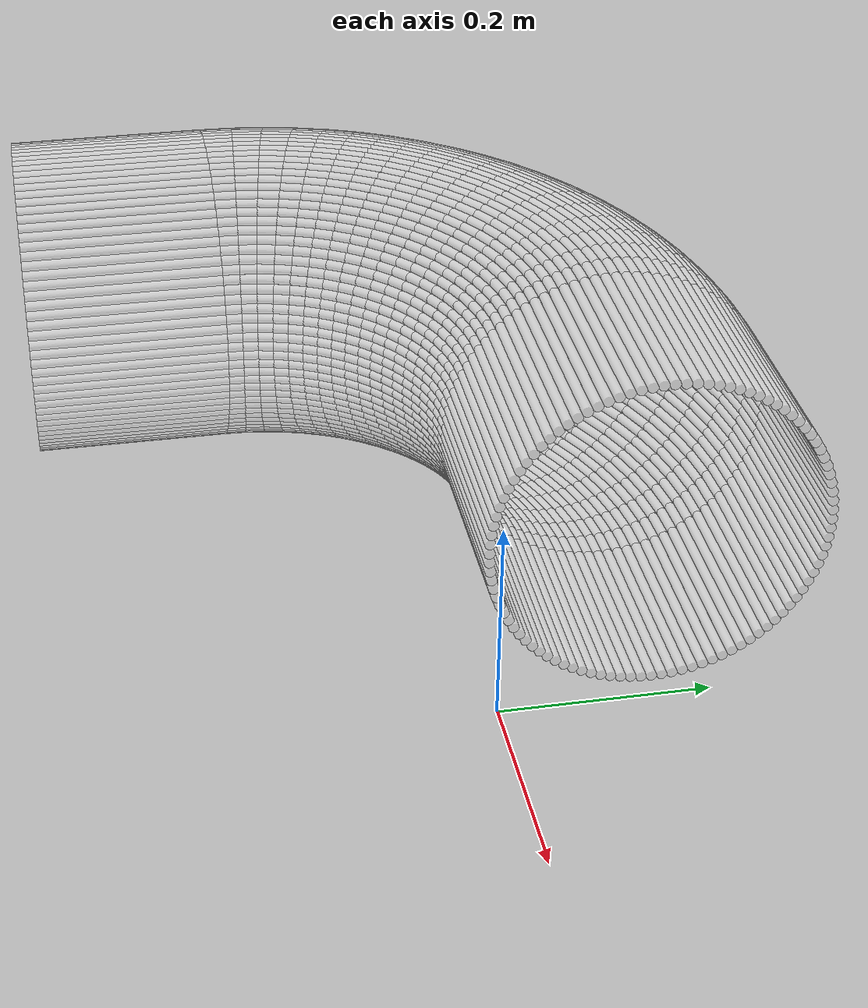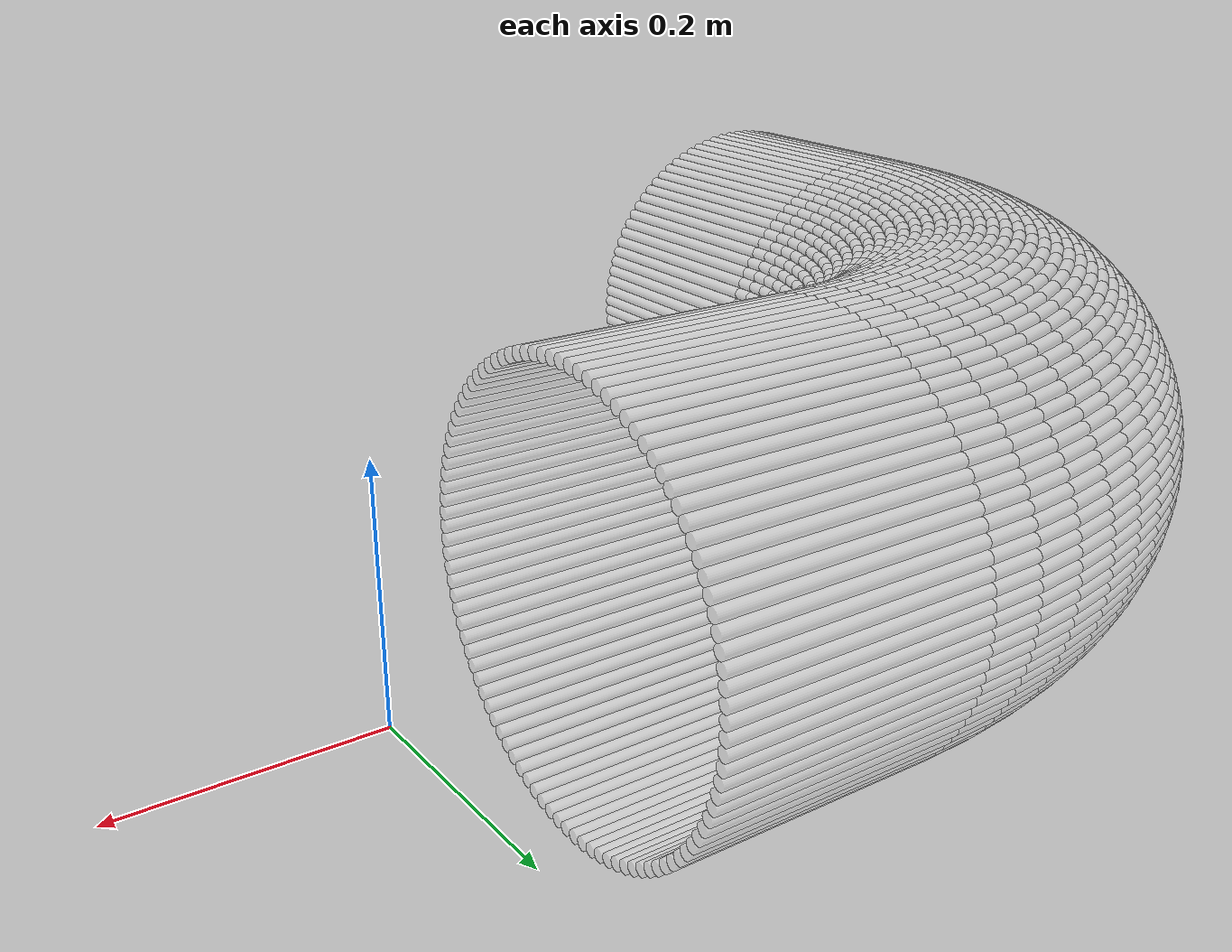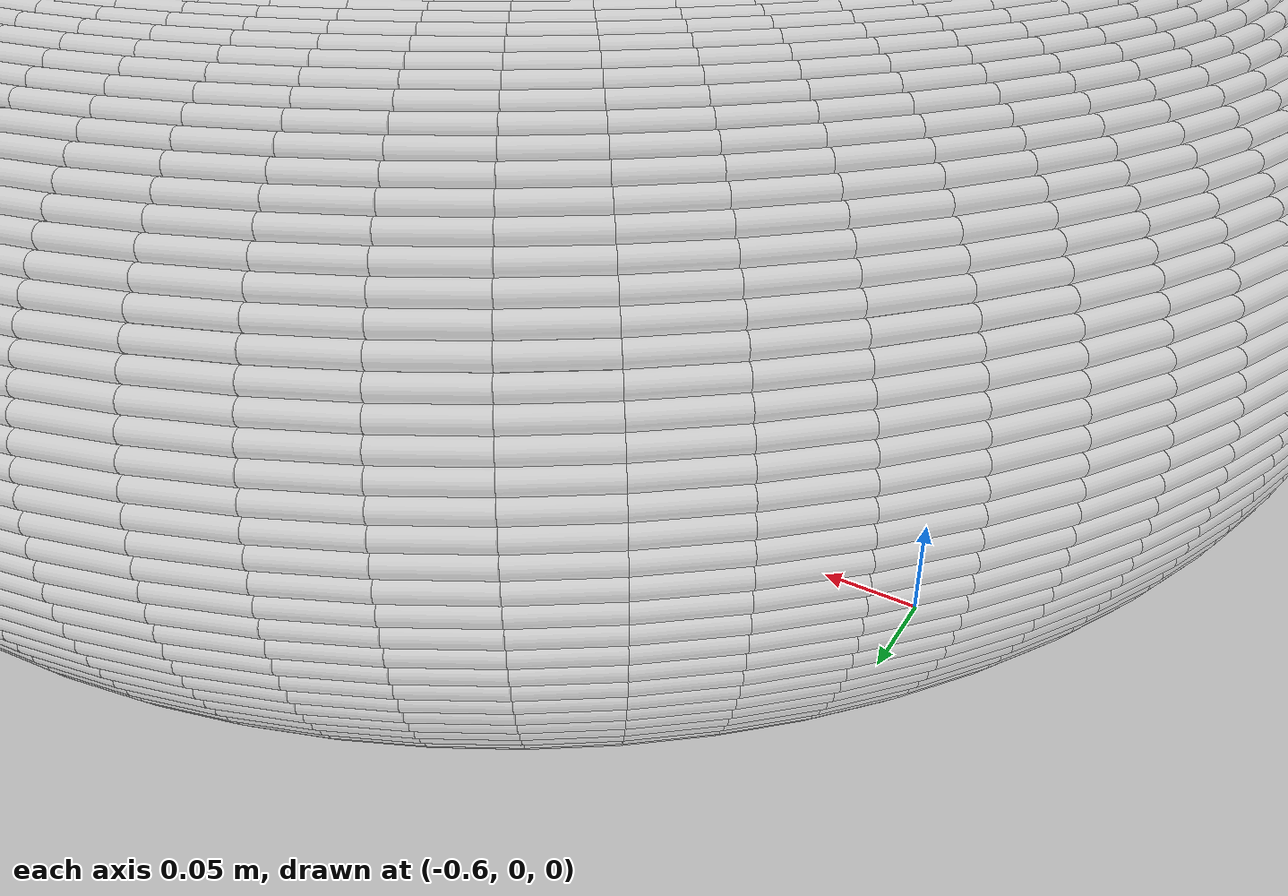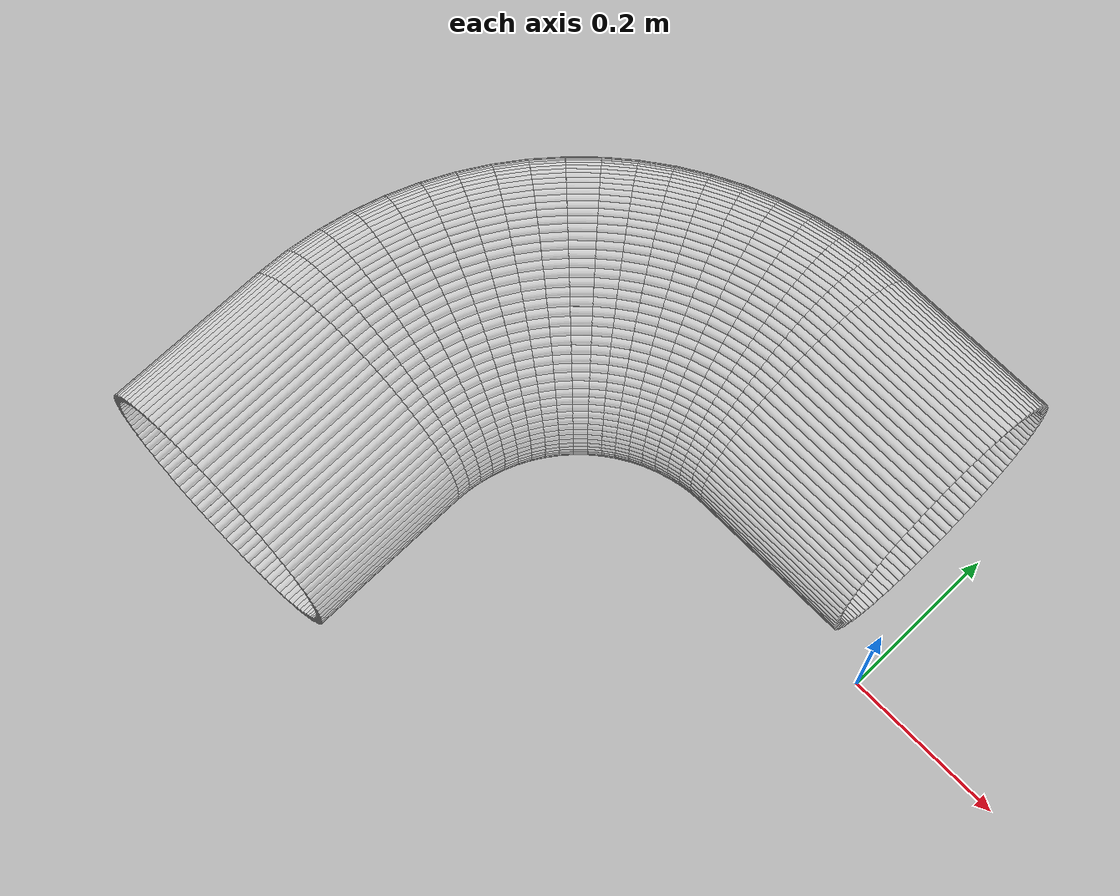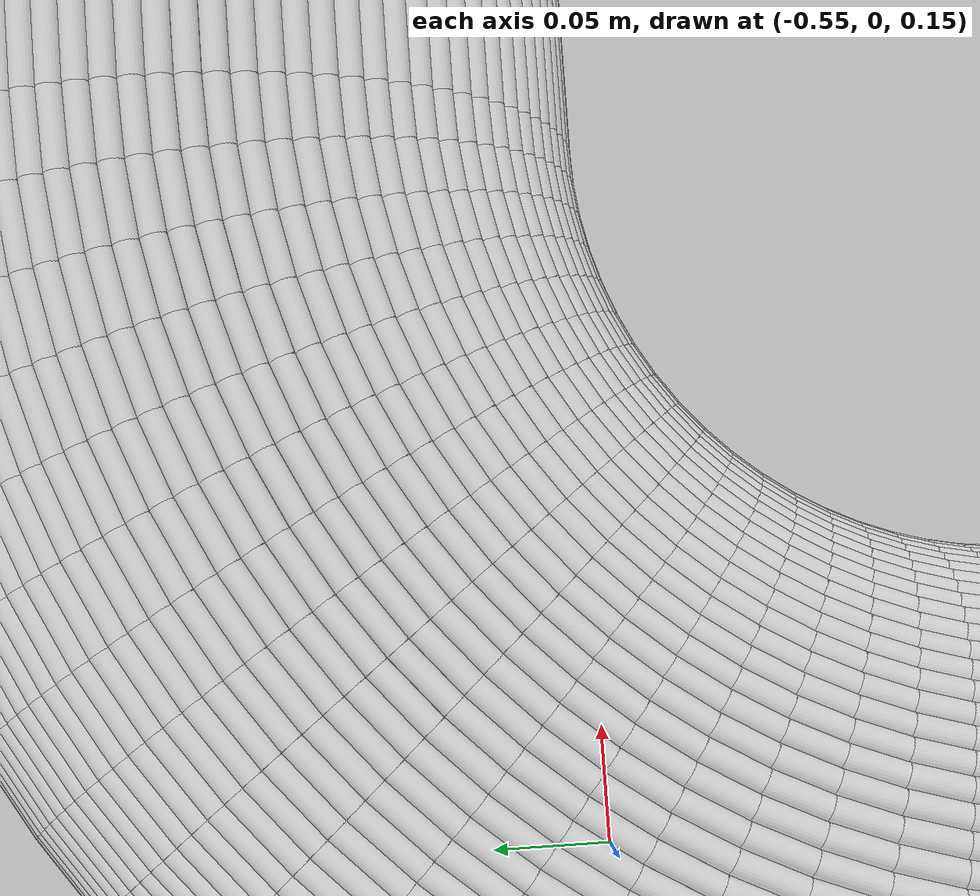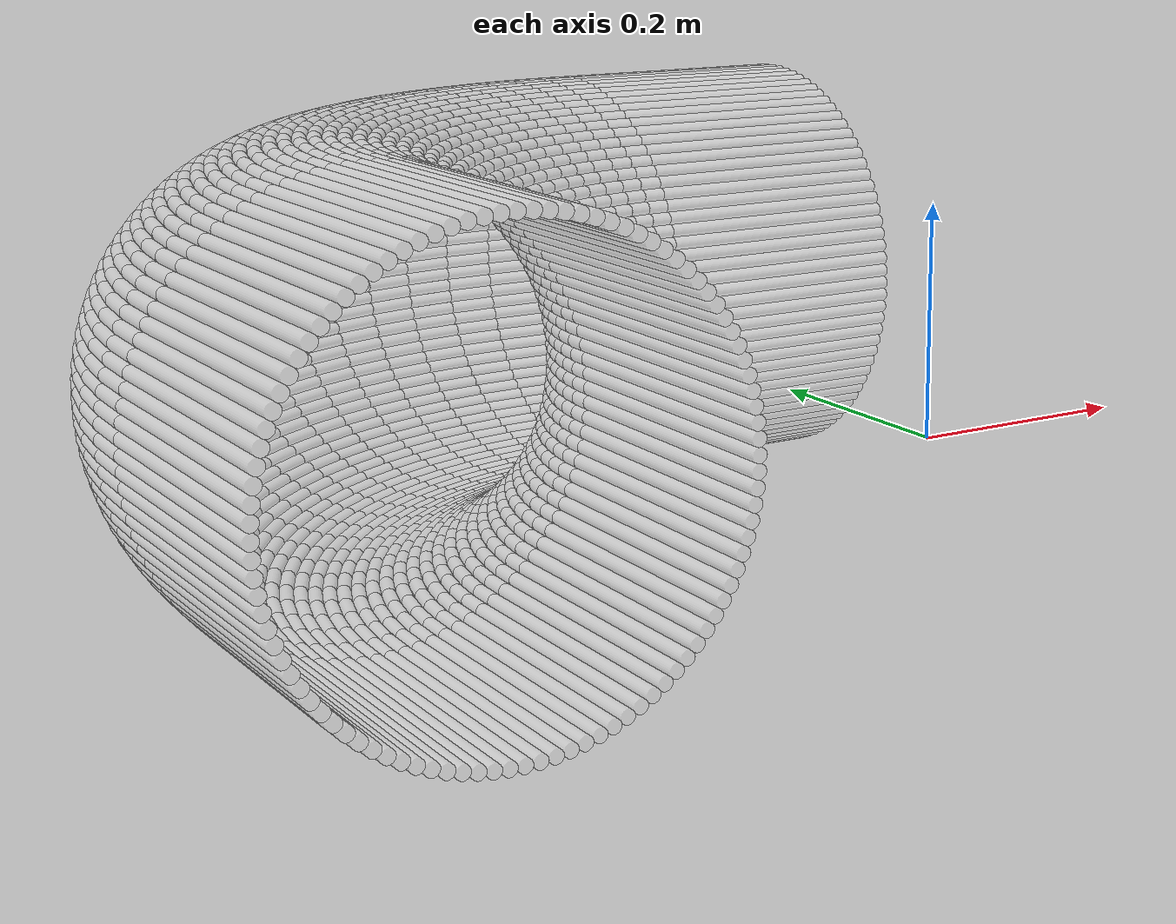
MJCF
<?xml version="1.0" encoding="utf-8"?>
<mujoco>
   <worldbody>
   <body pos="-0.25 -0.19 -0.02" euler="0 0 90">
      <geom euler=" 0 10 0 " fromto="0.51 -0.2 0.16 0.51 0 0.16" rgba="1 1 1 0.35"
            size="0.0050257"
            type="cylinder"/>
      <geom euler=" 0 20 0 " fromto="0.50968 -0.2 0.17005 0.50968 0 0.17005"
            rgba="1 1 1 0.35"
            size="0.0050257"
            type="cylinder"/>
      <geom euler=" 0 30 0 " fromto="0.50874 -0.2 0.18005 0.50874 0 0.18005"
            rgba="1 1 1 0.35"
            size="0.0050257"
            type="cylinder"/>
      <geom euler=" 0 40 0 " fromto="0.50717 -0.2 0.18998 0.50717 0 0.18998"
            rgba="1 1 1 0.35"
            size="0.0050257"
            type="cylinder"/>
      <geom euler=" 0 50 0 " fromto="0.50497 -0.2 0.19979 0.50497 0 0.19979"
            rgba="1 1 1 0.35"
            size="0.0050257"
            type="cylinder"/>
      <geom euler=" 0 60 0 " fromto="0.50217 -0.2 0.20944 0.50217 0 0.20944"
            rgba="1 1 1 0.35"
            size="0.0050257"
            type="cylinder"/>
      <geom euler=" 0 70 0 " fromto="0.49876 -0.2 0.2189 0.49876 0 0.2189"
            rgba="1 1 1 0.35"
            size="0.0050257"
            type="cylinder"/>
      <geom euler=" 0 80 0 " fromto="0.49477 -0.2 0.22812 0.49477 0 0.22812"
            rgba="1 1 1 0.35"
            size="0.0050257"
            type="cylinder"/>
      <geom euler=" 0 90 0 " fromto="0.49021 -0.2 0.23708 0.49021 0 0.23708"
            rgba="1 1 1 0.35"
            size="0.0050257"
            type="cylinder"/>
      <geom euler=" 0 100 0 " fromto="0.48509 -0.2 0.24573 0.48509 0 0.24573"
            rgba="1 1 1 0.35"
            size="0.0050257"
            type="cylinder"/>
      <geom euler=" 0 110 0 " fromto="0.47944 -0.2 0.25405 0.47944 0 0.25405"
            rgba="1 1 1 0.35"
            size="0.0050257"
            type="cylinder"/>
      <geom euler=" 0 120 0 " fromto="0.47328 -0.2 0.26199 0.47328 0 0.26199"
            rgba="1 1 1 0.35"
            size="0.0050257"
            type="cylinder"/>
      <geom euler=" 0 130 0 " fromto="0.46663 -0.2 0.26953 0.46663 0 0.26953"
            rgba="1 1 1 0.35"
            size="0.0050257"
            type="cylinder"/>
      <geom euler=" 0 140 0 " fromto="0.45953 -0.2 0.27663 0.45953 0 0.27663"
            rgba="1 1 1 0.35"
            size="0.0050257"
            type="cylinder"/>
      <geom euler=" 0 150 0 " fromto="0.45199 -0.2 0.28328 0.45199 0 0.28328"
            rgba="1 1 1 0.35"
            size="0.0050257"
            type="cylinder"/>
      <geom euler=" 0 160 0 " fromto="0.44405 -0.2 0.28944 0.44405 0 0.28944"
            rgba="1 1 1 0.35"
            size="0.0050257"
            type="cylinder"/>
      <geom euler=" 0 170 0 " fromto="0.43573 -0.2 0.29509 0.43573 0 0.29509"
            rgba="1 1 1 0.35"
            size="0.0050257"
            type="cylinder"/>
      <geom euler=" 0 180 0 " fromto="0.42708 -0.2 0.30021 0.42708 0 0.30021"
            rgba="1 1 1 0.35"
            size="0.0050257"
            type="cylinder"/>
      <geom euler=" 0 190 0 " fromto="0.41812 -0.2 0.30477 0.41812 0 0.30477"
            rgba="1 1 1 0.35"
            size="0.0050257"
            type="cylinder"/>
      <geom euler=" 0 200 0 " fromto="0.4089 -0.2 0.30876 0.4089 0 0.30876"
            rgba="1 1 1 0.35"
            size="0.0050257"
            type="cylinder"/>
      <geom euler=" 0 210 0 " fromto="0.39944 -0.2 0.31217 0.39944 0 0.31217"
            rgba="1 1 1 0.35"
            size="0.0050257"
            type="cylinder"/>
      <geom euler=" 0 220 0 " fromto="0.38979 -0.2 0.31497 0.38979 0 0.31497"
            rgba="1 1 1 0.35"
            size="0.0050257"
            type="cylinder"/>
      <geom euler=" 0 230 0 " fromto="0.37998 -0.2 0.31717 0.37998 0 0.31717"
            rgba="1 1 1 0.35"
            size="0.0050257"
            type="cylinder"/>
      <geom euler=" 0 240 0 " fromto="0.37005 -0.2 0.31874 0.37005 0 0.31874"
            rgba="1 1 1 0.35"
            size="0.0050257"
            type="cylinder"/>
      <geom euler=" 0 250 0 " fromto="0.36005 -0.2 0.31968 0.36005 0 0.31968"
            rgba="1 1 1 0.35"
            size="0.0050257"
            type="cylinder"/>
      <geom euler=" 0 260 0 " fromto="0.35 -0.2 0.32 0.35 0 0.32" rgba="1 1 1 0.35"
            size="0.0050257"
            type="cylinder"/>
      <geom euler=" 0 270 0 " fromto="0.33995 -0.2 0.31968 0.33995 0 0.31968"
            rgba="1 1 1 0.35"
            size="0.0050257"
            type="cylinder"/>
      <geom euler=" 0 280 0 " fromto="0.32995 -0.2 0.31874 0.32995 0 0.31874"
            rgba="1 1 1 0.35"
            size="0.0050257"
            type="cylinder"/>
      <geom euler=" 0 290 0 " fromto="0.32002 -0.2 0.31717 0.32002 0 0.31717"
            rgba="1 1 1 0.35"
            size="0.0050257"
            type="cylinder"/>
      <geom euler=" 0 300 0 " fromto="0.31021 -0.2 0.31497 0.31021 0 0.31497"
            rgba="1 1 1 0.35"
            size="0.0050257"
            type="cylinder"/>
      <geom euler=" 0 310 0 " fromto="0.30056 -0.2 0.31217 0.30056 0 0.31217"
            rgba="1 1 1 0.35"
            size="0.0050257"
            type="cylinder"/>
      <geom euler=" 0 320 0 " fromto="0.2911 -0.2 0.30876 0.2911 0 0.30876"
            rgba="1 1 1 0.35"
            size="0.0050257"
            type="cylinder"/>
      <geom euler=" 0 330 0 " fromto="0.28188 -0.2 0.30477 0.28188 0 0.30477"
            rgba="1 1 1 0.35"
            size="0.0050257"
            type="cylinder"/>
      <geom euler=" 0 340 0 " fromto="0.27292 -0.2 0.30021 0.27292 0 0.30021"
            rgba="1 1 1 0.35"
            size="0.0050257"
            type="cylinder"/>
      <geom euler=" 0 350 0 " fromto="0.26427 -0.2 0.29509 0.26427 0 0.29509"
            rgba="1 1 1 0.35"
            size="0.0050257"
            type="cylinder"/>
      <geom euler=" 0 360 0 " fromto="0.25595 -0.2 0.28944 0.25595 0 0.28944"
            rgba="1 1 1 0.35"
            size="0.0050257"
            type="cylinder"/>
      <geom euler=" 0 370 0 " fromto="0.24801 -0.2 0.28328 0.24801 0 0.28328"
            rgba="1 1 1 0.35"
            size="0.0050257"
            type="cylinder"/>
      <geom euler=" 0 380 0 " fromto="0.24047 -0.2 0.27663 0.24047 0 0.27663"
            rgba="1 1 1 0.35"
            size="0.0050257"
            type="cylinder"/>
      <geom euler=" 0 390 0 " fromto="0.23337 -0.2 0.26953 0.23337 0 0.26953"
            rgba="1 1 1 0.35"
            size="0.0050257"
            type="cylinder"/>
      <geom euler=" 0 400 0 " fromto="0.22672 -0.2 0.26199 0.22672 0 0.26199"
            rgba="1 1 1 0.35"
            size="0.0050257"
            type="cylinder"/>
      <geom euler=" 0 410 0 " fromto="0.22056 -0.2 0.25405 0.22056 0 0.25405"
            rgba="1 1 1 0.35"
            size="0.0050257"
            type="cylinder"/>
      <geom euler=" 0 420 0 " fromto="0.21491 -0.2 0.24573 0.21491 0 0.24573"
            rgba="1 1 1 0.35"
            size="0.0050257"
            type="cylinder"/>
      <geom euler=" 0 430 0 " fromto="0.20979 -0.2 0.23708 0.20979 0 0.23708"
            rgba="1 1 1 0.35"
            size="0.0050257"
            type="cylinder"/>
      <geom euler=" 0 440 0 " fromto="0.20523 -0.2 0.22812 0.20523 0 0.22812"
            rgba="1 1 1 0.35"
            size="0.0050257"
            type="cylinder"/>
      <geom euler=" 0 450 0 " fromto="0.20124 -0.2 0.2189 0.20124 0 0.2189"
            rgba="1 1 1 0.35"
            size="0.0050257"
            type="cylinder"/>
      <geom euler=" 0 460 0 " fromto="0.19783 -0.2 0.20944 0.19783 0 0.20944"
            rgba="1 1 1 0.35"
            size="0.0050257"
            type="cylinder"/>
      <geom euler=" 0 470 0 " fromto="0.19503 -0.2 0.19979 0.19503 0 0.19979"
            rgba="1 1 1 0.35"
            size="0.0050257"
            type="cylinder"/>
      <geom euler=" 0 480 0 " fromto="0.19283 -0.2 0.18998 0.19283 0 0.18998"
            rgba="1 1 1 0.35"
            size="0.0050257"
            type="cylinder"/>
      <geom euler=" 0 490 0 " fromto="0.19126 -0.2 0.18005 0.19126 0 0.18005"
            rgba="1 1 1 0.35"
            size="0.0050257"
            type="cylinder"/>
      <geom euler=" 0 500 0 " fromto="0.19032 -0.2 0.17005 0.19032 0 0.17005"
            rgba="1 1 1 0.35"
            size="0.0050257"
            type="cylinder"/>
      <geom euler=" 0 510 0 " fromto="0.19 -0.2 0.16 0.19 0 0.16" rgba="1 1 1 0.35"
            size="0.0050257"
            type="cylinder"/>
      <geom euler=" 0 520 0 " fromto="0.19032 -0.2 0.14995 0.19032 0 0.14995"
            rgba="1 1 1 0.35"
            size="0.0050257"
            type="cylinder"/>
      <geom euler=" 0 530 0 " fromto="0.19126 -0.2 0.13995 0.19126 0 0.13995"
            rgba="1 1 1 0.35"
            size="0.0050257"
            type="cylinder"/>
      <geom euler=" 0 540 0 " fromto="0.19283 -0.2 0.13002 0.19283 0 0.13002"
            rgba="1 1 1 0.35"
            size="0.0050257"
            type="cylinder"/>
      <geom euler=" 0 550 0 " fromto="0.19503 -0.2 0.12021 0.19503 0 0.12021"
            rgba="1 1 1 0.35"
            size="0.0050257"
            type="cylinder"/>
      <geom euler=" 0 560 0 " fromto="0.19783 -0.2 0.11056 0.19783 0 0.11056"
            rgba="1 1 1 0.35"
            size="0.0050257"
            type="cylinder"/>
      <geom euler=" 0 570 0 " fromto="0.20124 -0.2 0.1011 0.20124 0 0.1011"
            rgba="1 1 1 0.35"
            size="0.0050257"
            type="cylinder"/>
      <geom euler=" 0 580 0 " fromto="0.20523 -0.2 0.091875 0.20523 0 0.091875"
            rgba="1 1 1 0.35"
            size="0.0050257"
            type="cylinder"/>
      <geom euler=" 0 590 0 " fromto="0.20979 -0.2 0.082919 0.20979 0 0.082919"
            rgba="1 1 1 0.35"
            size="0.0050257"
            type="cylinder"/>
      <geom euler=" 0 600 0 " fromto="0.21491 -0.2 0.074268 0.21491 0 0.074268"
            rgba="1 1 1 0.35"
            size="0.0050257"
            type="cylinder"/>
      <geom euler=" 0 610 0 " fromto="0.22056 -0.2 0.065954 0.22056 0 0.065954"
            rgba="1 1 1 0.35"
            size="0.0050257"
            type="cylinder"/>
      <geom euler=" 0 620 0 " fromto="0.22672 -0.2 0.058012 0.22672 0 0.058012"
            rgba="1 1 1 0.35"
            size="0.0050257"
            type="cylinder"/>
      <geom euler=" 0 630 0 " fromto="0.23337 -0.2 0.050472 0.23337 0 0.050472"
            rgba="1 1 1 0.35"
            size="0.0050257"
            type="cylinder"/>
      <geom euler=" 0 640 0 " fromto="0.24047 -0.2 0.043365 0.24047 0 0.043365"
            rgba="1 1 1 0.35"
            size="0.0050257"
            type="cylinder"/>
      <geom euler=" 0 650 0 " fromto="0.24801 -0.2 0.036718 0.24801 0 0.036718"
            rgba="1 1 1 0.35"
            size="0.0050257"
            type="cylinder"/>
      <geom euler=" 0 660 0 " fromto="0.25595 -0.2 0.030557 0.25595 0 0.030557"
            rgba="1 1 1 0.35"
            size="0.0050257"
            type="cylinder"/>
      <geom euler=" 0 670 0 " fromto="0.26427 -0.2 0.024908 0.26427 0 0.024908"
            rgba="1 1 1 0.35"
            size="0.0050257"
            type="cylinder"/>
      <geom euler=" 0 680 0 " fromto="0.27292 -0.2 0.019791 0.27292 0 0.019791"
            rgba="1 1 1 0.35"
            size="0.0050257"
            type="cylinder"/>
      <geom euler=" 0 690 0 " fromto="0.28188 -0.2 0.015228 0.28188 0 0.015228"
            rgba="1 1 1 0.35"
            size="0.0050257"
            type="cylinder"/>
      <geom euler=" 0 700 0 " fromto="0.2911 -0.2 0.011236 0.2911 0 0.011236"
            rgba="1 1 1 0.35"
            size="0.0050257"
            type="cylinder"/>
      <geom euler=" 0 710 0 " fromto="0.30056 -0.2 0.007831 0.30056 0 0.007831"
            rgba="1 1 1 0.35"
            size="0.0050257"
            type="cylinder"/>
      <geom euler=" 0 720 0 " fromto="0.31021 -0.2 0.0050267 0.31021 0 0.0050267"
            rgba="1 1 1 0.35"
            size="0.0050257"
            type="cylinder"/>
      <geom euler=" 0 730 0 " fromto="0.32002 -0.2 0.002834 0.32002 0 0.002834"
            rgba="1 1 1 0.35"
            size="0.0050257"
            type="cylinder"/>
      <geom euler=" 0 740 0 " fromto="0.32995 -0.2 0.0012616 0.32995 0 0.0012616"
            rgba="1 1 1 0.35"
            size="0.0050257"
            type="cylinder"/>
      <geom euler=" 0 750 0 " fromto="0.33995 -0.2 0.00031572 0.33995 0 0.00031572"
            rgba="1 1 1 0.35"
            size="0.0050257"
            type="cylinder"/>
      <geom euler=" 0 760 0 " fromto="0.35 -0.2 0 0.35 0 0" rgba="1 1 1 0.35"
            size="0.0050257"
            type="cylinder"/>
      <geom euler=" 0 770 0 " fromto="0.36005 -0.2 0.00031572 0.36005 0 0.00031572"
            rgba="1 1 1 0.35"
            size="0.0050257"
            type="cylinder"/>
      <geom euler=" 0 780 0 " fromto="0.37005 -0.2 0.0012616 0.37005 0 0.0012616"
            rgba="1 1 1 0.35"
            size="0.0050257"
            type="cylinder"/>
      <geom euler=" 0 790 0 " fromto="0.37998 -0.2 0.002834 0.37998 0 0.002834"
            rgba="1 1 1 0.35"
            size="0.0050257"
            type="cylinder"/>
      <geom euler=" 0 800 0 " fromto="0.38979 -0.2 0.0050267 0.38979 0 0.0050267"
            rgba="1 1 1 0.35"
            size="0.0050257"
            type="cylinder"/>
      <geom euler=" 0 810 0 " fromto="0.39944 -0.2 0.007831 0.39944 0 0.007831"
            rgba="1 1 1 0.35"
            size="0.0050257"
            type="cylinder"/>
      <geom euler=" 0 820 0 " fromto="0.4089 -0.2 0.011236 0.4089 0 0.011236"
            rgba="1 1 1 0.35"
            size="0.0050257"
            type="cylinder"/>
      <geom euler=" 0 830 0 " fromto="0.41812 -0.2 0.015228 0.41812 0 0.015228"
            rgba="1 1 1 0.35"
            size="0.0050257"
            type="cylinder"/>
      <geom euler=" 0 840 0 " fromto="0.42708 -0.2 0.019791 0.42708 0 0.019791"
            rgba="1 1 1 0.35"
            size="0.0050257"
            type="cylinder"/>
      <geom euler=" 0 850 0 " fromto="0.43573 -0.2 0.024908 0.43573 0 0.024908"
            rgba="1 1 1 0.35"
            size="0.0050257"
            type="cylinder"/>
      <geom euler=" 0 860 0 " fromto="0.44405 -0.2 0.030557 0.44405 0 0.030557"
            rgba="1 1 1 0.35"
            size="0.0050257"
            type="cylinder"/>
      <geom euler=" 0 870 0 " fromto="0.45199 -0.2 0.036718 0.45199 0 0.036718"
            rgba="1 1 1 0.35"
            size="0.0050257"
            type="cylinder"/>
      <geom euler=" 0 880 0 " fromto="0.45953 -0.2 0.043365 0.45953 0 0.043365"
            rgba="1 1 1 0.35"
            size="0.0050257"
            type="cylinder"/>
      <geom euler=" 0 890 0 " fromto="0.46663 -0.2 0.050472 0.46663 0 0.050472"
            rgba="1 1 1 0.35"
            size="0.0050257"
            type="cylinder"/>
      <geom euler=" 0 900 0 " fromto="0.47328 -0.2 0.058012 0.47328 0 0.058012"
            rgba="1 1 1 0.35"
            size="0.0050257"
            type="cylinder"/>
      <geom euler=" 0 910 0 " fromto="0.47944 -0.2 0.065954 0.47944 0 0.065954"
            rgba="1 1 1 0.35"
            size="0.0050257"
            type="cylinder"/>
      <geom euler=" 0 920 0 " fromto="0.48509 -0.2 0.074268 0.48509 0 0.074268"
            rgba="1 1 1 0.35"
            size="0.0050257"
            type="cylinder"/>
      <geom euler=" 0 930 0 " fromto="0.49021 -0.2 0.082919 0.49021 0 0.082919"
            rgba="1 1 1 0.35"
            size="0.0050257"
            type="cylinder"/>
      <geom euler=" 0 940 0 " fromto="0.49477 -0.2 0.091875 0.49477 0 0.091875"
            rgba="1 1 1 0.35"
            size="0.0050257"
            type="cylinder"/>
      <geom euler=" 0 950 0 " fromto="0.49876 -0.2 0.1011 0.49876 0 0.1011"
            rgba="1 1 1 0.35"
            size="0.0050257"
            type="cylinder"/>
      <geom euler=" 0 960 0 " fromto="0.50217 -0.2 0.11056 0.50217 0 0.11056"
            rgba="1 1 1 0.35"
            size="0.0050257"
            type="cylinder"/>
      <geom euler=" 0 970 0 " fromto="0.50497 -0.2 0.12021 0.50497 0 0.12021"
            rgba="1 1 1 0.35"
            size="0.0050257"
            type="cylinder"/>
      <geom euler=" 0 980 0 " fromto="0.50717 -0.2 0.13002 0.50717 0 0.13002"
            rgba="1 1 1 0.35"
            size="0.0050257"
            type="cylinder"/>
      <geom euler=" 0 990 0 " fromto="0.50874 -0.2 0.13995 0.50874 0 0.13995"
            rgba="1 1 1 0.35"
            size="0.0050257"
            type="cylinder"/>
      <geom euler=" 0 1000 0 " fromto="0.50968 -0.2 0.14995 0.50968 0 0.14995"
            rgba="1 1 1 0.35"
            size="0.0050257"
            type="cylinder"/>
      <geom euler=" 0 10 0 " fromto="0.51 0 0.16 0.50826 0.042115 0.16" rgba="1 1 1 0.35"
            size="0.0050257"
            type="cylinder"/>
      <geom euler=" 0 20 0 " fromto="0.50968 0 0.17005 0.50794 0.042089 0.17005"
            rgba="1 1 1 0.35"
            size="0.0050257"
            type="cylinder"/>
      <geom euler=" 0 30 0 " fromto="0.50874 0 0.18005 0.507 0.042011 0.18005"
            rgba="1 1 1 0.35"
            size="0.0050257"
            type="cylinder"/>
      <geom euler=" 0 40 0 " fromto="0.50717 0 0.18998 0.50543 0.041881 0.18998"
            rgba="1 1 1 0.35"
            size="0.0050257"
            type="cylinder"/>
      <geom euler=" 0 50 0 " fromto="0.50497 0 0.19979 0.50325 0.0417 0.19979"
            rgba="1 1 1 0.35"
            size="0.0050257"
            type="cylinder"/>
      <geom euler=" 0 60 0 " fromto="0.50217 0 0.20944 0.50045 0.041469 0.20944"
            rgba="1 1 1 0.35"
            size="0.0050257"
            type="cylinder"/>
      <geom euler=" 0 70 0 " fromto="0.49876 0 0.2189 0.49706 0.041188 0.2189"
            rgba="1 1 1 0.35"
            size="0.0050257"
            type="cylinder"/>
      <geom euler=" 0 80 0 " fromto="0.49477 0 0.22812 0.49308 0.040858 0.22812"
            rgba="1 1 1 0.35"
            size="0.0050257"
            type="cylinder"/>
      <geom euler=" 0 90 0 " fromto="0.49021 0 0.23708 0.48853 0.040481 0.23708"
            rgba="1 1 1 0.35"
            size="0.0050257"
            type="cylinder"/>
      <geom euler=" 0 100 0 " fromto="0.48509 0 0.24573 0.48344 0.040059 0.24573"
            rgba="1 1 1 0.35"
            size="0.0050257"
            type="cylinder"/>
      <geom euler=" 0 110 0 " fromto="0.47944 0 0.25405 0.47781 0.039592 0.25405"
            rgba="1 1 1 0.35"
            size="0.0050257"
            type="cylinder"/>
      <geom euler=" 0 120 0 " fromto="0.47328 0 0.26199 0.47167 0.039083 0.26199"
            rgba="1 1 1 0.35"
            size="0.0050257"
            type="cylinder"/>
      <geom euler=" 0 130 0 " fromto="0.46663 0 0.26953 0.46504 0.038534 0.26953"
            rgba="1 1 1 0.35"
            size="0.0050257"
            type="cylinder"/>
      <geom euler=" 0 140 0 " fromto="0.45953 0 0.27663 0.45796 0.037947 0.27663"
            rgba="1 1 1 0.35"
            size="0.0050257"
            type="cylinder"/>
      <geom euler=" 0 150 0 " fromto="0.45199 0 0.28328 0.45044 0.037325 0.28328"
            rgba="1 1 1 0.35"
            size="0.0050257"
            type="cylinder"/>
      <geom euler=" 0 160 0 " fromto="0.44405 0 0.28944 0.44253 0.036669 0.28944"
            rgba="1 1 1 0.35"
            size="0.0050257"
            type="cylinder"/>
      <geom euler=" 0 170 0 " fromto="0.43573 0 0.29509 0.43424 0.035982 0.29509"
            rgba="1 1 1 0.35"
            size="0.0050257"
            type="cylinder"/>
      <geom euler=" 0 180 0 " fromto="0.42708 0 0.30021 0.42562 0.035268 0.30021"
            rgba="1 1 1 0.35"
            size="0.0050257"
            type="cylinder"/>
      <geom euler=" 0 190 0 " fromto="0.41812 0 0.30477 0.4167 0.034528 0.30477"
            rgba="1 1 1 0.35"
            size="0.0050257"
            type="cylinder"/>
      <geom euler=" 0 200 0 " fromto="0.4089 0 0.30876 0.4075 0.033767 0.30876"
            rgba="1 1 1 0.35"
            size="0.0050257"
            type="cylinder"/>
      <geom euler=" 0 210 0 " fromto="0.39944 0 0.31217 0.39808 0.032986 0.31217"
            rgba="1 1 1 0.35"
            size="0.0050257"
            type="cylinder"/>
      <geom euler=" 0 220 0 " fromto="0.38979 0 0.31497 0.38846 0.032189 0.31497"
            rgba="1 1 1 0.35"
            size="0.0050257"
            type="cylinder"/>
      <geom euler=" 0 230 0 " fromto="0.37998 0 0.31717 0.37868 0.031379 0.31717"
            rgba="1 1 1 0.35"
            size="0.0050257"
            type="cylinder"/>
      <geom euler=" 0 240 0 " fromto="0.37005 0 0.31874 0.36879 0.030559 0.31874"
            rgba="1 1 1 0.35"
            size="0.0050257"
            type="cylinder"/>
      <geom euler=" 0 250 0 " fromto="0.36005 0 0.31968 0.35882 0.029732 0.31968"
            rgba="1 1 1 0.35"
            size="0.0050257"
            type="cylinder"/>
      <geom euler=" 0 260 0 " fromto="0.35 0 0.32 0.3488 0.028903 0.32" rgba="1 1 1 0.35"
            size="0.0050257"
            type="cylinder"/>
      <geom euler=" 0 270 0 " fromto="0.33995 0 0.31968 0.33879 0.028073 0.31968"
            rgba="1 1 1 0.35"
            size="0.0050257"
            type="cylinder"/>
      <geom euler=" 0 280 0 " fromto="0.32995 0 0.31874 0.32882 0.027247 0.31874"
            rgba="1 1 1 0.35"
            size="0.0050257"
            type="cylinder"/>
      <geom euler=" 0 290 0 " fromto="0.32002 0 0.31717 0.31893 0.026427 0.31717"
            rgba="1 1 1 0.35"
            size="0.0050257"
            type="cylinder"/>
      <geom euler=" 0 300 0 " fromto="0.31021 0 0.31497 0.30915 0.025617 0.31497"
            rgba="1 1 1 0.35"
            size="0.0050257"
            type="cylinder"/>
      <geom euler=" 0 310 0 " fromto="0.30056 0 0.31217 0.29953 0.02482 0.31217"
            rgba="1 1 1 0.35"
            size="0.0050257"
            type="cylinder"/>
      <geom euler=" 0 320 0 " fromto="0.2911 0 0.30876 0.29011 0.024039 0.30876"
            rgba="1 1 1 0.35"
            size="0.0050257"
            type="cylinder"/>
      <geom euler=" 0 330 0 " fromto="0.28188 0 0.30477 0.28091 0.023277 0.30477"
            rgba="1 1 1 0.35"
            size="0.0050257"
            type="cylinder"/>
      <geom euler=" 0 340 0 " fromto="0.27292 0 0.30021 0.27199 0.022538 0.30021"
            rgba="1 1 1 0.35"
            size="0.0050257"
            type="cylinder"/>
      <geom euler=" 0 350 0 " fromto="0.26427 0 0.29509 0.26337 0.021823 0.29509"
            rgba="1 1 1 0.35"
            size="0.0050257"
            type="cylinder"/>
      <geom euler=" 0 360 0 " fromto="0.25595 0 0.28944 0.25508 0.021137 0.28944"
            rgba="1 1 1 0.35"
            size="0.0050257"
            type="cylinder"/>
      <geom euler=" 0 370 0 " fromto="0.24801 0 0.28328 0.24717 0.020481 0.28328"
            rgba="1 1 1 0.35"
            size="0.0050257"
            type="cylinder"/>
      <geom euler=" 0 380 0 " fromto="0.24047 0 0.27663 0.23965 0.019858 0.27663"
            rgba="1 1 1 0.35"
            size="0.0050257"
            type="cylinder"/>
      <geom euler=" 0 390 0 " fromto="0.23337 0 0.26953 0.23257 0.019271 0.26953"
            rgba="1 1 1 0.35"
            size="0.0050257"
            type="cylinder"/>
      <geom euler=" 0 400 0 " fromto="0.22672 0 0.26199 0.22594 0.018722 0.26199"
            rgba="1 1 1 0.35"
            size="0.0050257"
            type="cylinder"/>
      <geom euler=" 0 410 0 " fromto="0.22056 0 0.25405 0.2198 0.018213 0.25405"
            rgba="1 1 1 0.35"
            size="0.0050257"
            type="cylinder"/>
      <geom euler=" 0 420 0 " fromto="0.21491 0 0.24573 0.21417 0.017747 0.24573"
            rgba="1 1 1 0.35"
            size="0.0050257"
            type="cylinder"/>
      <geom euler=" 0 430 0 " fromto="0.20979 0 0.23708 0.20907 0.017324 0.23708"
            rgba="1 1 1 0.35"
            size="0.0050257"
            type="cylinder"/>
      <geom euler=" 0 440 0 " fromto="0.20523 0 0.22812 0.20453 0.016948 0.22812"
            rgba="1 1 1 0.35"
            size="0.0050257"
            type="cylinder"/>
      <geom euler=" 0 450 0 " fromto="0.20124 0 0.2189 0.20055 0.016618 0.2189"
            rgba="1 1 1 0.35"
            size="0.0050257"
            type="cylinder"/>
      <geom euler=" 0 460 0 " fromto="0.19783 0 0.20944 0.19716 0.016337 0.20944"
            rgba="1 1 1 0.35"
            size="0.0050257"
            type="cylinder"/>
      <geom euler=" 0 470 0 " fromto="0.19503 0 0.19979 0.19436 0.016105 0.19979"
            rgba="1 1 1 0.35"
            size="0.0050257"
            type="cylinder"/>
      <geom euler=" 0 480 0 " fromto="0.19283 0 0.18998 0.19218 0.015924 0.18998"
            rgba="1 1 1 0.35"
            size="0.0050257"
            type="cylinder"/>
      <geom euler=" 0 490 0 " fromto="0.19126 0 0.18005 0.19061 0.015794 0.18005"
            rgba="1 1 1 0.35"
            size="0.0050257"
            type="cylinder"/>
      <geom euler=" 0 500 0 " fromto="0.19032 0 0.17005 0.18967 0.015716 0.17005"
            rgba="1 1 1 0.35"
            size="0.0050257"
            type="cylinder"/>
      <geom euler=" 0 510 0 " fromto="0.19 0 0.16 0.18935 0.01569 0.16" rgba="1 1 1 0.35"
            size="0.0050257"
            type="cylinder"/>
      <geom euler=" 0 520 0 " fromto="0.19032 0 0.14995 0.18967 0.015716 0.14995"
            rgba="1 1 1 0.35"
            size="0.0050257"
            type="cylinder"/>
      <geom euler=" 0 530 0 " fromto="0.19126 0 0.13995 0.19061 0.015794 0.13995"
            rgba="1 1 1 0.35"
            size="0.0050257"
            type="cylinder"/>
      <geom euler=" 0 540 0 " fromto="0.19283 0 0.13002 0.19218 0.015924 0.13002"
            rgba="1 1 1 0.35"
            size="0.0050257"
            type="cylinder"/>
      <geom euler=" 0 550 0 " fromto="0.19503 0 0.12021 0.19436 0.016105 0.12021"
            rgba="1 1 1 0.35"
            size="0.0050257"
            type="cylinder"/>
      <geom euler=" 0 560 0 " fromto="0.19783 0 0.11056 0.19716 0.016337 0.11056"
            rgba="1 1 1 0.35"
            size="0.0050257"
            type="cylinder"/>
      <geom euler=" 0 570 0 " fromto="0.20124 0 0.1011 0.20055 0.016618 0.1011"
            rgba="1 1 1 0.35"
            size="0.0050257"
            type="cylinder"/>
      <geom euler=" 0 580 0 " fromto="0.20523 0 0.091875 0.20453 0.016948 0.091875"
            rgba="1 1 1 0.35"
            size="0.0050257"
            type="cylinder"/>
      <geom euler=" 0 590 0 " fromto="0.20979 0 0.082919 0.20907 0.017324 0.082919"
            rgba="1 1 1 0.35"
            size="0.0050257"
            type="cylinder"/>
      <geom euler=" 0 600 0 " fromto="0.21491 0 0.074268 0.21417 0.017747 0.074268"
            rgba="1 1 1 0.35"
            size="0.0050257"
            type="cylinder"/>
      <geom euler=" 0 610 0 " fromto="0.22056 0 0.065954 0.2198 0.018213 0.065954"
            rgba="1 1 1 0.35"
            size="0.0050257"
            type="cylinder"/>
      <geom euler=" 0 620 0 " fromto="0.22672 0 0.058012 0.22594 0.018722 0.058012"
            rgba="1 1 1 0.35"
            size="0.0050257"
            type="cylinder"/>
      <geom euler=" 0 630 0 " fromto="0.23337 0 0.050472 0.23257 0.019271 0.050472"
            rgba="1 1 1 0.35"
            size="0.0050257"
            type="cylinder"/>
      <geom euler=" 0 640 0 " fromto="0.24047 0 0.043365 0.23965 0.019858 0.043365"
            rgba="1 1 1 0.35"
            size="0.0050257"
            type="cylinder"/>
      <geom euler=" 0 650 0 " fromto="0.24801 0 0.036718 0.24717 0.020481 0.036718"
            rgba="1 1 1 0.35"
            size="0.0050257"
            type="cylinder"/>
      <geom euler=" 0 660 0 " fromto="0.25595 0 0.030557 0.25508 0.021137 0.030557"
            rgba="1 1 1 0.35"
            size="0.0050257"
            type="cylinder"/>
      <geom euler=" 0 670 0 " fromto="0.26427 0 0.024908 0.26337 0.021823 0.024908"
            rgba="1 1 1 0.35"
            size="0.0050257"
            type="cylinder"/>
      <geom euler=" 0 680 0 " fromto="0.27292 0 0.019791 0.27199 0.022538 0.019791"
            rgba="1 1 1 0.35"
            size="0.0050257"
            type="cylinder"/>
      <geom euler=" 0 690 0 " fromto="0.28188 0 0.015228 0.28091 0.023277 0.015228"
            rgba="1 1 1 0.35"
            size="0.0050257"
            type="cylinder"/>
      <geom euler=" 0 700 0 " fromto="0.2911 0 0.011236 0.29011 0.024039 0.011236"
            rgba="1 1 1 0.35"
            size="0.0050257"
            type="cylinder"/>
      <geom euler=" 0 710 0 " fromto="0.30056 0 0.007831 0.29953 0.02482 0.007831"
            rgba="1 1 1 0.35"
            size="0.0050257"
            type="cylinder"/>
      <geom euler=" 0 720 0 " fromto="0.31021 0 0.0050267 0.30915 0.025617 0.0050267"
            rgba="1 1 1 0.35"
            size="0.0050257"
            type="cylinder"/>
      <geom euler=" 0 730 0 " fromto="0.32002 0 0.002834 0.31893 0.026427 0.002834"
            rgba="1 1 1 0.35"
            size="0.0050257"
            type="cylinder"/>
      <geom euler=" 0 740 0 " fromto="0.32995 0 0.0012616 0.32882 0.027247 0.0012616"
            rgba="1 1 1 0.35"
            size="0.0050257"
            type="cylinder"/>
      <geom euler=" 0 750 0 " fromto="0.33995 0 0.00031572 0.33879 0.028073 0.00031572"
            rgba="1 1 1 0.35"
            size="0.0050257"
            type="cylinder"/>
      <geom euler=" 0 760 0 " fromto="0.35 0 0 0.3488 0.028903 0" rgba="1 1 1 0.35"
            size="0.0050257"
            type="cylinder"/>
      <geom euler=" 0 770 0 " fromto="0.36005 0 0.00031572 0.35882 0.029732 0.00031572"
            rgba="1 1 1 0.35"
            size="0.0050257"
            type="cylinder"/>
      <geom euler=" 0 780 0 " fromto="0.37005 0 0.0012616 0.36879 0.030559 0.0012616"
            rgba="1 1 1 0.35"
            size="0.0050257"
            type="cylinder"/>
      <geom euler=" 0 790 0 " fromto="0.37998 0 0.002834 0.37868 0.031379 0.002834"
            rgba="1 1 1 0.35"
            size="0.0050257"
            type="cylinder"/>
      <geom euler=" 0 800 0 " fromto="0.38979 0 0.0050267 0.38846 0.032189 0.0050267"
            rgba="1 1 1 0.35"
            size="0.0050257"
            type="cylinder"/>
      <geom euler=" 0 810 0 " fromto="0.39944 0 0.007831 0.39808 0.032986 0.007831"
            rgba="1 1 1 0.35"
            size="0.0050257"
            type="cylinder"/>
      <geom euler=" 0 820 0 " fromto="0.4089 0 0.011236 0.4075 0.033767 0.011236"
            rgba="1 1 1 0.35"
            size="0.0050257"
            type="cylinder"/>
      <geom euler=" 0 830 0 " fromto="0.41812 0 0.015228 0.4167 0.034528 0.015228"
            rgba="1 1 1 0.35"
            size="0.0050257"
            type="cylinder"/>
      <geom euler=" 0 840 0 " fromto="0.42708 0 0.019791 0.42562 0.035268 0.019791"
            rgba="1 1 1 0.35"
            size="0.0050257"
            type="cylinder"/>
      <geom euler=" 0 850 0 " fromto="0.43573 0 0.024908 0.43424 0.035982 0.024908"
            rgba="1 1 1 0.35"
            size="0.0050257"
            type="cylinder"/>
      <geom euler=" 0 860 0 " fromto="0.44405 0 0.030557 0.44253 0.036669 0.030557"
            rgba="1 1 1 0.35"
            size="0.0050257"
            type="cylinder"/>
      <geom euler=" 0 870 0 " fromto="0.45199 0 0.036718 0.45044 0.037325 0.036718"
            rgba="1 1 1 0.35"
            size="0.0050257"
            type="cylinder"/>
      <geom euler=" 0 880 0 " fromto="0.45953 0 0.043365 0.45796 0.037947 0.043365"
            rgba="1 1 1 0.35"
            size="0.0050257"
            type="cylinder"/>
      <geom euler=" 0 890 0 " fromto="0.46663 0 0.050472 0.46504 0.038534 0.050472"
            rgba="1 1 1 0.35"
            size="0.0050257"
            type="cylinder"/>
      <geom euler=" 0 900 0 " fromto="0.47328 0 0.058012 0.47167 0.039083 0.058012"
            rgba="1 1 1 0.35"
            size="0.0050257"
            type="cylinder"/>
      <geom euler=" 0 910 0 " fromto="0.47944 0 0.065954 0.47781 0.039592 0.065954"
            rgba="1 1 1 0.35"
            size="0.0050257"
            type="cylinder"/>
      <geom euler=" 0 920 0 " fromto="0.48509 0 0.074268 0.48344 0.040059 0.074268"
            rgba="1 1 1 0.35"
            size="0.0050257"
            type="cylinder"/>
      <geom euler=" 0 930 0 " fromto="0.49021 0 0.082919 0.48853 0.040481 0.082919"
            rgba="1 1 1 0.35"
            size="0.0050257"
            type="cylinder"/>
      <geom euler=" 0 940 0 " fromto="0.49477 0 0.091875 0.49308 0.040858 0.091875"
            rgba="1 1 1 0.35"
            size="0.0050257"
            type="cylinder"/>
      <geom euler=" 0 950 0 " fromto="0.49876 0 0.1011 0.49706 0.041188 0.1011"
            rgba="1 1 1 0.35"
            size="0.0050257"
            type="cylinder"/>
      <geom euler=" 0 960 0 " fromto="0.50217 0 0.11056 0.50045 0.041469 0.11056"
            rgba="1 1 1 0.35"
            size="0.0050257"
            type="cylinder"/>
      <geom euler=" 0 970 0 " fromto="0.50497 0 0.12021 0.50325 0.0417 0.12021"
            rgba="1 1 1 0.35"
            size="0.0050257"
            type="cylinder"/>
      <geom euler=" 0 980 0 " fromto="0.50717 0 0.13002 0.50543 0.041881 0.13002"
            rgba="1 1 1 0.35"
            size="0.0050257"
            type="cylinder"/>
      <geom euler=" 0 990 0 " fromto="0.50874 0 0.13995 0.507 0.042011 0.13995"
            rgba="1 1 1 0.35"
            size="0.0050257"
            type="cylinder"/>
      <geom euler=" 0 1000 0 " fromto="0.50968 0 0.14995 0.50794 0.042089 0.14995"
            rgba="1 1 1 0.35"
            size="0.0050257"
            type="cylinder"/>
      <geom euler=" 0 10 0 " fromto="0.50826 0.042115 0.16 0.50304 0.083943 0.16"
            rgba="1 1 1 0.35"
            size="0.0050257"
            type="cylinder"/>
      <geom euler=" 0 20 0 " fromto="0.50794 0.042089 0.17005 0.50273 0.083891 0.17005"
            rgba="1 1 1 0.35"
            size="0.0050257"
            type="cylinder"/>
      <geom euler=" 0 30 0 " fromto="0.507 0.042011 0.18005 0.5018 0.083736 0.18005"
            rgba="1 1 1 0.35"
            size="0.0050257"
            type="cylinder"/>
      <geom euler=" 0 40 0 " fromto="0.50543 0.041881 0.18998 0.50025 0.083477 0.18998"
            rgba="1 1 1 0.35"
            size="0.0050257"
            type="cylinder"/>
      <geom euler=" 0 50 0 " fromto="0.50325 0.0417 0.19979 0.49809 0.083116 0.19979"
            rgba="1 1 1 0.35"
            size="0.0050257"
            type="cylinder"/>
      <geom euler=" 0 60 0 " fromto="0.50045 0.041469 0.20944 0.49532 0.082654 0.20944"
            rgba="1 1 1 0.35"
            size="0.0050257"
            type="cylinder"/>
      <geom euler=" 0 70 0 " fromto="0.49706 0.041188 0.2189 0.49196 0.082094 0.2189"
            rgba="1 1 1 0.35"
            size="0.0050257"
            type="cylinder"/>
      <geom euler=" 0 80 0 " fromto="0.49308 0.040858 0.22812 0.48802 0.081437 0.22812"
            rgba="1 1 1 0.35"
            size="0.0050257"
            type="cylinder"/>
      <geom euler=" 0 90 0 " fromto="0.48853 0.040481 0.23708 0.48352 0.080686 0.23708"
            rgba="1 1 1 0.35"
            size="0.0050257"
            type="cylinder"/>
      <geom euler=" 0 100 0 " fromto="0.48344 0.040059 0.24573 0.47848 0.079844 0.24573"
            rgba="1 1 1 0.35"
            size="0.0050257"
            type="cylinder"/>
      <geom euler=" 0 110 0 " fromto="0.47781 0.039592 0.25405 0.4729 0.078914 0.25405"
            rgba="1 1 1 0.35"
            size="0.0050257"
            type="cylinder"/>
      <geom euler=" 0 120 0 " fromto="0.47167 0.039083 0.26199 0.46683 0.0779 0.26199"
            rgba="1 1 1 0.35"
            size="0.0050257"
            type="cylinder"/>
      <geom euler=" 0 130 0 " fromto="0.46504 0.038534 0.26953 0.46027 0.076806 0.26953"
            rgba="1 1 1 0.35"
            size="0.0050257"
            type="cylinder"/>
      <geom euler=" 0 140 0 " fromto="0.45796 0.037947 0.27663 0.45326 0.075636 0.27663"
            rgba="1 1 1 0.35"
            size="0.0050257"
            type="cylinder"/>
      <geom euler=" 0 150 0 " fromto="0.45044 0.037325 0.28328 0.44582 0.074395 0.28328"
            rgba="1 1 1 0.35"
            size="0.0050257"
            type="cylinder"/>
      <geom euler=" 0 160 0 " fromto="0.44253 0.036669 0.28944 0.43799 0.073088 0.28944"
            rgba="1 1 1 0.35"
            size="0.0050257"
            type="cylinder"/>
      <geom euler=" 0 170 0 " fromto="0.43424 0.035982 0.29509 0.42979 0.071719 0.29509"
            rgba="1 1 1 0.35"
            size="0.0050257"
            type="cylinder"/>
      <geom euler=" 0 180 0 " fromto="0.42562 0.035268 0.30021 0.42126 0.070295 0.30021"
            rgba="1 1 1 0.35"
            size="0.0050257"
            type="cylinder"/>
      <geom euler=" 0 190 0 " fromto="0.4167 0.034528 0.30477 0.41242 0.068821 0.30477"
            rgba="1 1 1 0.35"
            size="0.0050257"
            type="cylinder"/>
      <geom euler=" 0 200 0 " fromto="0.4075 0.033767 0.30876 0.40332 0.067303 0.30876"
            rgba="1 1 1 0.35"
            size="0.0050257"
            type="cylinder"/>
      <geom euler=" 0 210 0 " fromto="0.39808 0.032986 0.31217 0.39399 0.065746 0.31217"
            rgba="1 1 1 0.35"
            size="0.0050257"
            type="cylinder"/>
      <geom euler=" 0 220 0 " fromto="0.38846 0.032189 0.31497 0.38447 0.064157 0.31497"
            rgba="1 1 1 0.35"
            size="0.0050257"
            type="cylinder"/>
      <geom euler=" 0 230 0 " fromto="0.37868 0.031379 0.31717 0.3748 0.062543 0.31717"
            rgba="1 1 1 0.35"
            size="0.0050257"
            type="cylinder"/>
      <geom euler=" 0 240 0 " fromto="0.36879 0.030559 0.31874 0.36501 0.060909 0.31874"
            rgba="1 1 1 0.35"
            size="0.0050257"
            type="cylinder"/>
      <geom euler=" 0 250 0 " fromto="0.35882 0.029732 0.31968 0.35514 0.059262 0.31968"
            rgba="1 1 1 0.35"
            size="0.0050257"
            type="cylinder"/>
      <geom euler=" 0 260 0 " fromto="0.3488 0.028903 0.32 0.34523 0.057608 0.32"
            rgba="1 1 1 0.35"
            size="0.0050257"
            type="cylinder"/>
      <geom euler=" 0 270 0 " fromto="0.33879 0.028073 0.31968 0.33532 0.055955 0.31968"
            rgba="1 1 1 0.35"
            size="0.0050257"
            type="cylinder"/>
      <geom euler=" 0 280 0 " fromto="0.32882 0.027247 0.31874 0.32545 0.054307 0.31874"
            rgba="1 1 1 0.35"
            size="0.0050257"
            type="cylinder"/>
      <geom euler=" 0 290 0 " fromto="0.31893 0.026427 0.31717 0.31565 0.052673 0.31717"
            rgba="1 1 1 0.35"
            size="0.0050257"
            type="cylinder"/>
      <geom euler=" 0 300 0 " fromto="0.30915 0.025617 0.31497 0.30598 0.051059 0.31497"
            rgba="1 1 1 0.35"
            size="0.0050257"
            type="cylinder"/>
      <geom euler=" 0 310 0 " fromto="0.29953 0.02482 0.31217 0.29646 0.04947 0.31217"
            rgba="1 1 1 0.35"
            size="0.0050257"
            type="cylinder"/>
      <geom euler=" 0 320 0 " fromto="0.29011 0.024039 0.30876 0.28713 0.047913 0.30876"
            rgba="1 1 1 0.35"
            size="0.0050257"
            type="cylinder"/>
      <geom euler=" 0 330 0 " fromto="0.28091 0.023277 0.30477 0.27803 0.046395 0.30477"
            rgba="1 1 1 0.35"
            size="0.0050257"
            type="cylinder"/>
      <geom euler=" 0 340 0 " fromto="0.27199 0.022538 0.30021 0.2692 0.044921 0.30021"
            rgba="1 1 1 0.35"
            size="0.0050257"
            type="cylinder"/>
      <geom euler=" 0 350 0 " fromto="0.26337 0.021823 0.29509 0.26066 0.043497 0.29509"
            rgba="1 1 1 0.35"
            size="0.0050257"
            type="cylinder"/>
      <geom euler=" 0 360 0 " fromto="0.25508 0.021137 0.28944 0.25246 0.042129 0.28944"
            rgba="1 1 1 0.35"
            size="0.0050257"
            type="cylinder"/>
      <geom euler=" 0 370 0 " fromto="0.24717 0.020481 0.28328 0.24463 0.040821 0.28328"
            rgba="1 1 1 0.35"
            size="0.0050257"
            type="cylinder"/>
      <geom euler=" 0 380 0 " fromto="0.23965 0.019858 0.27663 0.23719 0.03958 0.27663"
            rgba="1 1 1 0.35"
            size="0.0050257"
            type="cylinder"/>
      <geom euler=" 0 390 0 " fromto="0.23257 0.019271 0.26953 0.23018 0.038411 0.26953"
            rgba="1 1 1 0.35"
            size="0.0050257"
            type="cylinder"/>
      <geom euler=" 0 400 0 " fromto="0.22594 0.018722 0.26199 0.22363 0.037317 0.26199"
            rgba="1 1 1 0.35"
            size="0.0050257"
            type="cylinder"/>
      <geom euler=" 0 410 0 " fromto="0.2198 0.018213 0.25405 0.21755 0.036303 0.25405"
            rgba="1 1 1 0.35"
            size="0.0050257"
            type="cylinder"/>
      <geom euler=" 0 420 0 " fromto="0.21417 0.017747 0.24573 0.21198 0.035373 0.24573"
            rgba="1 1 1 0.35"
            size="0.0050257"
            type="cylinder"/>
      <geom euler=" 0 430 0 " fromto="0.20907 0.017324 0.23708 0.20693 0.03453 0.23708"
            rgba="1 1 1 0.35"
            size="0.0050257"
            type="cylinder"/>
      <geom euler=" 0 440 0 " fromto="0.20453 0.016948 0.22812 0.20243 0.033779 0.22812"
            rgba="1 1 1 0.35"
            size="0.0050257"
            type="cylinder"/>
      <geom euler=" 0 450 0 " fromto="0.20055 0.016618 0.2189 0.19849 0.033122 0.2189"
            rgba="1 1 1 0.35"
            size="0.0050257"
            type="cylinder"/>
      <geom euler=" 0 460 0 " fromto="0.19716 0.016337 0.20944 0.19513 0.032562 0.20944"
            rgba="1 1 1 0.35"
            size="0.0050257"
            type="cylinder"/>
      <geom euler=" 0 470 0 " fromto="0.19436 0.016105 0.19979 0.19237 0.0321 0.19979"
            rgba="1 1 1 0.35"
            size="0.0050257"
            type="cylinder"/>
      <geom euler=" 0 480 0 " fromto="0.19218 0.015924 0.18998 0.1902 0.031739 0.18998"
            rgba="1 1 1 0.35"
            size="0.0050257"
            type="cylinder"/>
      <geom euler=" 0 490 0 " fromto="0.19061 0.015794 0.18005 0.18865 0.031481 0.18005"
            rgba="1 1 1 0.35"
            size="0.0050257"
            type="cylinder"/>
      <geom euler=" 0 500 0 " fromto="0.18967 0.015716 0.17005 0.18772 0.031325 0.17005"
            rgba="1 1 1 0.35"
            size="0.0050257"
            type="cylinder"/>
      <geom euler=" 0 510 0 " fromto="0.18935 0.01569 0.16 0.18741 0.031273 0.16"
            rgba="1 1 1 0.35"
            size="0.0050257"
            type="cylinder"/>
      <geom euler=" 0 520 0 " fromto="0.18967 0.015716 0.14995 0.18772 0.031325 0.14995"
            rgba="1 1 1 0.35"
            size="0.0050257"
            type="cylinder"/>
      <geom euler=" 0 530 0 " fromto="0.19061 0.015794 0.13995 0.18865 0.031481 0.13995"
            rgba="1 1 1 0.35"
            size="0.0050257"
            type="cylinder"/>
      <geom euler=" 0 540 0 " fromto="0.19218 0.015924 0.13002 0.1902 0.031739 0.13002"
            rgba="1 1 1 0.35"
            size="0.0050257"
            type="cylinder"/>
      <geom euler=" 0 550 0 " fromto="0.19436 0.016105 0.12021 0.19237 0.0321 0.12021"
            rgba="1 1 1 0.35"
            size="0.0050257"
            type="cylinder"/>
      <geom euler=" 0 560 0 " fromto="0.19716 0.016337 0.11056 0.19513 0.032562 0.11056"
            rgba="1 1 1 0.35"
            size="0.0050257"
            type="cylinder"/>
      <geom euler=" 0 570 0 " fromto="0.20055 0.016618 0.1011 0.19849 0.033122 0.1011"
            rgba="1 1 1 0.35"
            size="0.0050257"
            type="cylinder"/>
      <geom euler=" 0 580 0 " fromto="0.20453 0.016948 0.091875 0.20243 0.033779 0.091875"
            rgba="1 1 1 0.35"
            size="0.0050257"
            type="cylinder"/>
      <geom euler=" 0 590 0 " fromto="0.20907 0.017324 0.082919 0.20693 0.03453 0.082919"
            rgba="1 1 1 0.35"
            size="0.0050257"
            type="cylinder"/>
      <geom euler=" 0 600 0 " fromto="0.21417 0.017747 0.074268 0.21198 0.035373 0.074268"
            rgba="1 1 1 0.35"
            size="0.0050257"
            type="cylinder"/>
      <geom euler=" 0 610 0 " fromto="0.2198 0.018213 0.065954 0.21755 0.036303 0.065954"
            rgba="1 1 1 0.35"
            size="0.0050257"
            type="cylinder"/>
      <geom euler=" 0 620 0 " fromto="0.22594 0.018722 0.058012 0.22363 0.037317 0.058012"
            rgba="1 1 1 0.35"
            size="0.0050257"
            type="cylinder"/>
      <geom euler=" 0 630 0 " fromto="0.23257 0.019271 0.050472 0.23018 0.038411 0.050472"
            rgba="1 1 1 0.35"
            size="0.0050257"
            type="cylinder"/>
      <geom euler=" 0 640 0 " fromto="0.23965 0.019858 0.043365 0.23719 0.03958 0.043365"
            rgba="1 1 1 0.35"
            size="0.0050257"
            type="cylinder"/>
      <geom euler=" 0 650 0 " fromto="0.24717 0.020481 0.036718 0.24463 0.040821 0.036718"
            rgba="1 1 1 0.35"
            size="0.0050257"
            type="cylinder"/>
      <geom euler=" 0 660 0 " fromto="0.25508 0.021137 0.030557 0.25246 0.042129 0.030557"
            rgba="1 1 1 0.35"
            size="0.0050257"
            type="cylinder"/>
      <geom euler=" 0 670 0 " fromto="0.26337 0.021823 0.024908 0.26066 0.043497 0.024908"
            rgba="1 1 1 0.35"
            size="0.0050257"
            type="cylinder"/>
      <geom euler=" 0 680 0 " fromto="0.27199 0.022538 0.019791 0.2692 0.044921 0.019791"
            rgba="1 1 1 0.35"
            size="0.0050257"
            type="cylinder"/>
      <geom euler=" 0 690 0 " fromto="0.28091 0.023277 0.015228 0.27803 0.046395 0.015228"
            rgba="1 1 1 0.35"
            size="0.0050257"
            type="cylinder"/>
      <geom euler=" 0 700 0 " fromto="0.29011 0.024039 0.011236 0.28713 0.047913 0.011236"
            rgba="1 1 1 0.35"
            size="0.0050257"
            type="cylinder"/>
      <geom euler=" 0 710 0 " fromto="0.29953 0.02482 0.007831 0.29646 0.04947 0.007831"
            rgba="1 1 1 0.35"
            size="0.0050257"
            type="cylinder"/>
      <geom euler=" 0 720 0 "
            fromto="0.30915 0.025617 0.0050267 0.30598 0.051059 0.0050267"
            rgba="1 1 1 0.35"
            size="0.0050257"
            type="cylinder"/>
      <geom euler=" 0 730 0 " fromto="0.31893 0.026427 0.002834 0.31565 0.052673 0.002834"
            rgba="1 1 1 0.35"
            size="0.0050257"
            type="cylinder"/>
      <geom euler=" 0 740 0 "
            fromto="0.32882 0.027247 0.0012616 0.32545 0.054307 0.0012616"
            rgba="1 1 1 0.35"
            size="0.0050257"
            type="cylinder"/>
      <geom euler=" 0 750 0 "
            fromto="0.33879 0.028073 0.00031572 0.33532 0.055955 0.00031572"
            rgba="1 1 1 0.35"
            size="0.0050257"
            type="cylinder"/>
      <geom euler=" 0 760 0 " fromto="0.3488 0.028903 0 0.34523 0.057608 0"
            rgba="1 1 1 0.35"
            size="0.0050257"
            type="cylinder"/>
      <geom euler=" 0 770 0 "
            fromto="0.35882 0.029732 0.00031572 0.35514 0.059262 0.00031572"
            rgba="1 1 1 0.35"
            size="0.0050257"
            type="cylinder"/>
      <geom euler=" 0 780 0 "
            fromto="0.36879 0.030559 0.0012616 0.36501 0.060909 0.0012616"
            rgba="1 1 1 0.35"
            size="0.0050257"
            type="cylinder"/>
      <geom euler=" 0 790 0 " fromto="0.37868 0.031379 0.002834 0.3748 0.062543 0.002834"
            rgba="1 1 1 0.35"
            size="0.0050257"
            type="cylinder"/>
      <geom euler=" 0 800 0 "
            fromto="0.38846 0.032189 0.0050267 0.38447 0.064157 0.0050267"
            rgba="1 1 1 0.35"
            size="0.0050257"
            type="cylinder"/>
      <geom euler=" 0 810 0 " fromto="0.39808 0.032986 0.007831 0.39399 0.065746 0.007831"
            rgba="1 1 1 0.35"
            size="0.0050257"
            type="cylinder"/>
      <geom euler=" 0 820 0 " fromto="0.4075 0.033767 0.011236 0.40332 0.067303 0.011236"
            rgba="1 1 1 0.35"
            size="0.0050257"
            type="cylinder"/>
      <geom euler=" 0 830 0 " fromto="0.4167 0.034528 0.015228 0.41242 0.068821 0.015228"
            rgba="1 1 1 0.35"
            size="0.0050257"
            type="cylinder"/>
      <geom euler=" 0 840 0 " fromto="0.42562 0.035268 0.019791 0.42126 0.070295 0.019791"
            rgba="1 1 1 0.35"
            size="0.0050257"
            type="cylinder"/>
      <geom euler=" 0 850 0 " fromto="0.43424 0.035982 0.024908 0.42979 0.071719 0.024908"
            rgba="1 1 1 0.35"
            size="0.0050257"
            type="cylinder"/>
      <geom euler=" 0 860 0 " fromto="0.44253 0.036669 0.030557 0.43799 0.073088 0.030557"
            rgba="1 1 1 0.35"
            size="0.0050257"
            type="cylinder"/>
      <geom euler=" 0 870 0 " fromto="0.45044 0.037325 0.036718 0.44582 0.074395 0.036718"
            rgba="1 1 1 0.35"
            size="0.0050257"
            type="cylinder"/>
      <geom euler=" 0 880 0 " fromto="0.45796 0.037947 0.043365 0.45326 0.075636 0.043365"
            rgba="1 1 1 0.35"
            size="0.0050257"
            type="cylinder"/>
      <geom euler=" 0 890 0 " fromto="0.46504 0.038534 0.050472 0.46027 0.076806 0.050472"
            rgba="1 1 1 0.35"
            size="0.0050257"
            type="cylinder"/>
      <geom euler=" 0 900 0 " fromto="0.47167 0.039083 0.058012 0.46683 0.0779 0.058012"
            rgba="1 1 1 0.35"
            size="0.0050257"
            type="cylinder"/>
      <geom euler=" 0 910 0 " fromto="0.47781 0.039592 0.065954 0.4729 0.078914 0.065954"
            rgba="1 1 1 0.35"
            size="0.0050257"
            type="cylinder"/>
      <geom euler=" 0 920 0 " fromto="0.48344 0.040059 0.074268 0.47848 0.079844 0.074268"
            rgba="1 1 1 0.35"
            size="0.0050257"
            type="cylinder"/>
      <geom euler=" 0 930 0 " fromto="0.48853 0.040481 0.082919 0.48352 0.080686 0.082919"
            rgba="1 1 1 0.35"
            size="0.0050257"
            type="cylinder"/>
      <geom euler=" 0 940 0 " fromto="0.49308 0.040858 0.091875 0.48802 0.081437 0.091875"
            rgba="1 1 1 0.35"
            size="0.0050257"
            type="cylinder"/>
      <geom euler=" 0 950 0 " fromto="0.49706 0.041188 0.1011 0.49196 0.082094 0.1011"
            rgba="1 1 1 0.35"
            size="0.0050257"
            type="cylinder"/>
      <geom euler=" 0 960 0 " fromto="0.50045 0.041469 0.11056 0.49532 0.082654 0.11056"
            rgba="1 1 1 0.35"
            size="0.0050257"
            type="cylinder"/>
      <geom euler=" 0 970 0 " fromto="0.50325 0.0417 0.12021 0.49809 0.083116 0.12021"
            rgba="1 1 1 0.35"
            size="0.0050257"
            type="cylinder"/>
      <geom euler=" 0 980 0 " fromto="0.50543 0.041881 0.13002 0.50025 0.083477 0.13002"
            rgba="1 1 1 0.35"
            size="0.0050257"
            type="cylinder"/>
      <geom euler=" 0 990 0 " fromto="0.507 0.042011 0.13995 0.5018 0.083736 0.13995"
            rgba="1 1 1 0.35"
            size="0.0050257"
            type="cylinder"/>
      <geom euler=" 0 1000 0 " fromto="0.50794 0.042089 0.14995 0.50273 0.083891 0.14995"
            rgba="1 1 1 0.35"
            size="0.0050257"
            type="cylinder"/>
      <geom euler=" 0 10 0 " fromto="0.50304 0.083943 0.16 0.49439 0.1252 0.16"
            rgba="1 1 1 0.35"
            size="0.0050257"
            type="cylinder"/>
      <geom euler=" 0 20 0 " fromto="0.50273 0.083891 0.17005 0.49409 0.12512 0.17005"
            rgba="1 1 1 0.35"
            size="0.0050257"
            type="cylinder"/>
      <geom euler=" 0 30 0 " fromto="0.5018 0.083736 0.18005 0.49317 0.12489 0.18005"
            rgba="1 1 1 0.35"
            size="0.0050257"
            type="cylinder"/>
      <geom euler=" 0 40 0 " fromto="0.50025 0.083477 0.18998 0.49165 0.1245 0.18998"
            rgba="1 1 1 0.35"
            size="0.0050257"
            type="cylinder"/>
      <geom euler=" 0 50 0 " fromto="0.49809 0.083116 0.19979 0.48952 0.12396 0.19979"
            rgba="1 1 1 0.35"
            size="0.0050257"
            type="cylinder"/>
      <geom euler=" 0 60 0 " fromto="0.49532 0.082654 0.20944 0.4868 0.12328 0.20944"
            rgba="1 1 1 0.35"
            size="0.0050257"
            type="cylinder"/>
      <geom euler=" 0 70 0 " fromto="0.49196 0.082094 0.2189 0.4835 0.12244 0.2189"
            rgba="1 1 1 0.35"
            size="0.0050257"
            type="cylinder"/>
      <geom euler=" 0 80 0 " fromto="0.48802 0.081437 0.22812 0.47963 0.12146 0.22812"
            rgba="1 1 1 0.35"
            size="0.0050257"
            type="cylinder"/>
      <geom euler=" 0 90 0 " fromto="0.48352 0.080686 0.23708 0.47521 0.12034 0.23708"
            rgba="1 1 1 0.35"
            size="0.0050257"
            type="cylinder"/>
      <geom euler=" 0 100 0 " fromto="0.47848 0.079844 0.24573 0.47025 0.11908 0.24573"
            rgba="1 1 1 0.35"
            size="0.0050257"
            type="cylinder"/>
      <geom euler=" 0 110 0 " fromto="0.4729 0.078914 0.25405 0.46477 0.1177 0.25405"
            rgba="1 1 1 0.35"
            size="0.0050257"
            type="cylinder"/>
      <geom euler=" 0 120 0 " fromto="0.46683 0.0779 0.26199 0.4588 0.11618 0.26199"
            rgba="1 1 1 0.35"
            size="0.0050257"
            type="cylinder"/>
      <geom euler=" 0 130 0 " fromto="0.46027 0.076806 0.26953 0.45236 0.11455 0.26953"
            rgba="1 1 1 0.35"
            size="0.0050257"
            type="cylinder"/>
      <geom euler=" 0 140 0 " fromto="0.45326 0.075636 0.27663 0.44547 0.11281 0.27663"
            rgba="1 1 1 0.35"
            size="0.0050257"
            type="cylinder"/>
      <geom euler=" 0 150 0 " fromto="0.44582 0.074395 0.28328 0.43816 0.11096 0.28328"
            rgba="1 1 1 0.35"
            size="0.0050257"
            type="cylinder"/>
      <geom euler=" 0 160 0 " fromto="0.43799 0.073088 0.28944 0.43046 0.10901 0.28944"
            rgba="1 1 1 0.35"
            size="0.0050257"
            type="cylinder"/>
      <geom euler=" 0 170 0 " fromto="0.42979 0.071719 0.29509 0.4224 0.10697 0.29509"
            rgba="1 1 1 0.35"
            size="0.0050257"
            type="cylinder"/>
      <geom euler=" 0 180 0 " fromto="0.42126 0.070295 0.30021 0.41401 0.10484 0.30021"
            rgba="1 1 1 0.35"
            size="0.0050257"
            type="cylinder"/>
      <geom euler=" 0 190 0 " fromto="0.41242 0.068821 0.30477 0.40533 0.10264 0.30477"
            rgba="1 1 1 0.35"
            size="0.0050257"
            type="cylinder"/>
      <geom euler=" 0 200 0 " fromto="0.40332 0.067303 0.30876 0.39639 0.10038 0.30876"
            rgba="1 1 1 0.35"
            size="0.0050257"
            type="cylinder"/>
      <geom euler=" 0 210 0 " fromto="0.39399 0.065746 0.31217 0.38722 0.098057 0.31217"
            rgba="1 1 1 0.35"
            size="0.0050257"
            type="cylinder"/>
      <geom euler=" 0 220 0 " fromto="0.38447 0.064157 0.31497 0.37786 0.095688 0.31497"
            rgba="1 1 1 0.35"
            size="0.0050257"
            type="cylinder"/>
      <geom euler=" 0 230 0 " fromto="0.3748 0.062543 0.31717 0.36835 0.09328 0.31717"
            rgba="1 1 1 0.35"
            size="0.0050257"
            type="cylinder"/>
      <geom euler=" 0 240 0 " fromto="0.36501 0.060909 0.31874 0.35873 0.090843 0.31874"
            rgba="1 1 1 0.35"
            size="0.0050257"
            type="cylinder"/>
      <geom euler=" 0 250 0 " fromto="0.35514 0.059262 0.31968 0.34903 0.088386 0.31968"
            rgba="1 1 1 0.35"
            size="0.0050257"
            type="cylinder"/>
      <geom euler=" 0 260 0 " fromto="0.34523 0.057608 0.32 0.33929 0.08592 0.32"
            rgba="1 1 1 0.35"
            size="0.0050257"
            type="cylinder"/>
      <geom euler=" 0 270 0 " fromto="0.33532 0.055955 0.31968 0.32955 0.083454 0.31968"
            rgba="1 1 1 0.35"
            size="0.0050257"
            type="cylinder"/>
      <geom euler=" 0 280 0 " fromto="0.32545 0.054307 0.31874 0.31985 0.080997 0.31874"
            rgba="1 1 1 0.35"
            size="0.0050257"
            type="cylinder"/>
      <geom euler=" 0 290 0 " fromto="0.31565 0.052673 0.31717 0.31023 0.07856 0.31717"
            rgba="1 1 1 0.35"
            size="0.0050257"
            type="cylinder"/>
      <geom euler=" 0 300 0 " fromto="0.30598 0.051059 0.31497 0.30072 0.076152 0.31497"
            rgba="1 1 1 0.35"
            size="0.0050257"
            type="cylinder"/>
      <geom euler=" 0 310 0 " fromto="0.29646 0.04947 0.31217 0.29136 0.073782 0.31217"
            rgba="1 1 1 0.35"
            size="0.0050257"
            type="cylinder"/>
      <geom euler=" 0 320 0 " fromto="0.28713 0.047913 0.30876 0.28219 0.071461 0.30876"
            rgba="1 1 1 0.35"
            size="0.0050257"
            type="cylinder"/>
      <geom euler=" 0 330 0 " fromto="0.27803 0.046395 0.30477 0.27325 0.069196 0.30477"
            rgba="1 1 1 0.35"
            size="0.0050257"
            type="cylinder"/>
      <geom euler=" 0 340 0 " fromto="0.2692 0.044921 0.30021 0.26457 0.066998 0.30021"
            rgba="1 1 1 0.35"
            size="0.0050257"
            type="cylinder"/>
      <geom euler=" 0 350 0 " fromto="0.26066 0.043497 0.29509 0.25618 0.064874 0.29509"
            rgba="1 1 1 0.35"
            size="0.0050257"
            type="cylinder"/>
      <geom euler=" 0 360 0 " fromto="0.25246 0.042129 0.28944 0.24812 0.062833 0.28944"
            rgba="1 1 1 0.35"
            size="0.0050257"
            type="cylinder"/>
      <geom euler=" 0 370 0 " fromto="0.24463 0.040821 0.28328 0.24042 0.060883 0.28328"
            rgba="1 1 1 0.35"
            size="0.0050257"
            type="cylinder"/>
      <geom euler=" 0 380 0 " fromto="0.23719 0.03958 0.27663 0.23311 0.059032 0.27663"
            rgba="1 1 1 0.35"
            size="0.0050257"
            type="cylinder"/>
      <geom euler=" 0 390 0 " fromto="0.23018 0.038411 0.26953 0.22622 0.057288 0.26953"
            rgba="1 1 1 0.35"
            size="0.0050257"
            type="cylinder"/>
      <geom euler=" 0 400 0 " fromto="0.22363 0.037317 0.26199 0.21978 0.055656 0.26199"
            rgba="1 1 1 0.35"
            size="0.0050257"
            type="cylinder"/>
      <geom euler=" 0 410 0 " fromto="0.21755 0.036303 0.25405 0.21381 0.054144 0.25405"
            rgba="1 1 1 0.35"
            size="0.0050257"
            type="cylinder"/>
      <geom euler=" 0 420 0 " fromto="0.21198 0.035373 0.24573 0.20833 0.052757 0.24573"
            rgba="1 1 1 0.35"
            size="0.0050257"
            type="cylinder"/>
      <geom euler=" 0 430 0 " fromto="0.20693 0.03453 0.23708 0.20337 0.051501 0.23708"
            rgba="1 1 1 0.35"
            size="0.0050257"
            type="cylinder"/>
      <geom euler=" 0 440 0 " fromto="0.20243 0.033779 0.22812 0.19895 0.05038 0.22812"
            rgba="1 1 1 0.35"
            size="0.0050257"
            type="cylinder"/>
      <geom euler=" 0 450 0 " fromto="0.19849 0.033122 0.2189 0.19508 0.0494 0.2189"
            rgba="1 1 1 0.35"
            size="0.0050257"
            type="cylinder"/>
      <geom euler=" 0 460 0 " fromto="0.19513 0.032562 0.20944 0.19178 0.048565 0.20944"
            rgba="1 1 1 0.35"
            size="0.0050257"
            type="cylinder"/>
      <geom euler=" 0 470 0 " fromto="0.19237 0.0321 0.19979 0.18906 0.047876 0.19979"
            rgba="1 1 1 0.35"
            size="0.0050257"
            type="cylinder"/>
      <geom euler=" 0 480 0 " fromto="0.1902 0.031739 0.18998 0.18693 0.047338 0.18998"
            rgba="1 1 1 0.35"
            size="0.0050257"
            type="cylinder"/>
      <geom euler=" 0 490 0 " fromto="0.18865 0.031481 0.18005 0.18541 0.046952 0.18005"
            rgba="1 1 1 0.35"
            size="0.0050257"
            type="cylinder"/>
      <geom euler=" 0 500 0 " fromto="0.18772 0.031325 0.17005 0.18449 0.04672 0.17005"
            rgba="1 1 1 0.35"
            size="0.0050257"
            type="cylinder"/>
      <geom euler=" 0 510 0 " fromto="0.18741 0.031273 0.16 0.18419 0.046642 0.16"
            rgba="1 1 1 0.35"
            size="0.0050257"
            type="cylinder"/>
      <geom euler=" 0 520 0 " fromto="0.18772 0.031325 0.14995 0.18449 0.04672 0.14995"
            rgba="1 1 1 0.35"
            size="0.0050257"
            type="cylinder"/>
      <geom euler=" 0 530 0 " fromto="0.18865 0.031481 0.13995 0.18541 0.046952 0.13995"
            rgba="1 1 1 0.35"
            size="0.0050257"
            type="cylinder"/>
      <geom euler=" 0 540 0 " fromto="0.1902 0.031739 0.13002 0.18693 0.047338 0.13002"
            rgba="1 1 1 0.35"
            size="0.0050257"
            type="cylinder"/>
      <geom euler=" 0 550 0 " fromto="0.19237 0.0321 0.12021 0.18906 0.047876 0.12021"
            rgba="1 1 1 0.35"
            size="0.0050257"
            type="cylinder"/>
      <geom euler=" 0 560 0 " fromto="0.19513 0.032562 0.11056 0.19178 0.048565 0.11056"
            rgba="1 1 1 0.35"
            size="0.0050257"
            type="cylinder"/>
      <geom euler=" 0 570 0 " fromto="0.19849 0.033122 0.1011 0.19508 0.0494 0.1011"
            rgba="1 1 1 0.35"
            size="0.0050257"
            type="cylinder"/>
      <geom euler=" 0 580 0 " fromto="0.20243 0.033779 0.091875 0.19895 0.05038 0.091875"
            rgba="1 1 1 0.35"
            size="0.0050257"
            type="cylinder"/>
      <geom euler=" 0 590 0 " fromto="0.20693 0.03453 0.082919 0.20337 0.051501 0.082919"
            rgba="1 1 1 0.35"
            size="0.0050257"
            type="cylinder"/>
      <geom euler=" 0 600 0 " fromto="0.21198 0.035373 0.074268 0.20833 0.052757 0.074268"
            rgba="1 1 1 0.35"
            size="0.0050257"
            type="cylinder"/>
      <geom euler=" 0 610 0 " fromto="0.21755 0.036303 0.065954 0.21381 0.054144 0.065954"
            rgba="1 1 1 0.35"
            size="0.0050257"
            type="cylinder"/>
      <geom euler=" 0 620 0 " fromto="0.22363 0.037317 0.058012 0.21978 0.055656 0.058012"
            rgba="1 1 1 0.35"
            size="0.0050257"
            type="cylinder"/>
      <geom euler=" 0 630 0 " fromto="0.23018 0.038411 0.050472 0.22622 0.057288 0.050472"
            rgba="1 1 1 0.35"
            size="0.0050257"
            type="cylinder"/>
      <geom euler=" 0 640 0 " fromto="0.23719 0.03958 0.043365 0.23311 0.059032 0.043365"
            rgba="1 1 1 0.35"
            size="0.0050257"
            type="cylinder"/>
      <geom euler=" 0 650 0 " fromto="0.24463 0.040821 0.036718 0.24042 0.060883 0.036718"
            rgba="1 1 1 0.35"
            size="0.0050257"
            type="cylinder"/>
      <geom euler=" 0 660 0 " fromto="0.25246 0.042129 0.030557 0.24812 0.062833 0.030557"
            rgba="1 1 1 0.35"
            size="0.0050257"
            type="cylinder"/>
      <geom euler=" 0 670 0 " fromto="0.26066 0.043497 0.024908 0.25618 0.064874 0.024908"
            rgba="1 1 1 0.35"
            size="0.0050257"
            type="cylinder"/>
      <geom euler=" 0 680 0 " fromto="0.2692 0.044921 0.019791 0.26457 0.066998 0.019791"
            rgba="1 1 1 0.35"
            size="0.0050257"
            type="cylinder"/>
      <geom euler=" 0 690 0 " fromto="0.27803 0.046395 0.015228 0.27325 0.069196 0.015228"
            rgba="1 1 1 0.35"
            size="0.0050257"
            type="cylinder"/>
      <geom euler=" 0 700 0 " fromto="0.28713 0.047913 0.011236 0.28219 0.071461 0.011236"
            rgba="1 1 1 0.35"
            size="0.0050257"
            type="cylinder"/>
      <geom euler=" 0 710 0 " fromto="0.29646 0.04947 0.007831 0.29136 0.073782 0.007831"
            rgba="1 1 1 0.35"
            size="0.0050257"
            type="cylinder"/>
      <geom euler=" 0 720 0 "
            fromto="0.30598 0.051059 0.0050267 0.30072 0.076152 0.0050267"
            rgba="1 1 1 0.35"
            size="0.0050257"
            type="cylinder"/>
      <geom euler=" 0 730 0 " fromto="0.31565 0.052673 0.002834 0.31023 0.07856 0.002834"
            rgba="1 1 1 0.35"
            size="0.0050257"
            type="cylinder"/>
      <geom euler=" 0 740 0 "
            fromto="0.32545 0.054307 0.0012616 0.31985 0.080997 0.0012616"
            rgba="1 1 1 0.35"
            size="0.0050257"
            type="cylinder"/>
      <geom euler=" 0 750 0 "
            fromto="0.33532 0.055955 0.00031572 0.32955 0.083454 0.00031572"
            rgba="1 1 1 0.35"
            size="0.0050257"
            type="cylinder"/>
      <geom euler=" 0 760 0 " fromto="0.34523 0.057608 0 0.33929 0.08592 0"
            rgba="1 1 1 0.35"
            size="0.0050257"
            type="cylinder"/>
      <geom euler=" 0 770 0 "
            fromto="0.35514 0.059262 0.00031572 0.34903 0.088386 0.00031572"
            rgba="1 1 1 0.35"
            size="0.0050257"
            type="cylinder"/>
      <geom euler=" 0 780 0 "
            fromto="0.36501 0.060909 0.0012616 0.35873 0.090843 0.0012616"
            rgba="1 1 1 0.35"
            size="0.0050257"
            type="cylinder"/>
      <geom euler=" 0 790 0 " fromto="0.3748 0.062543 0.002834 0.36835 0.09328 0.002834"
            rgba="1 1 1 0.35"
            size="0.0050257"
            type="cylinder"/>
      <geom euler=" 0 800 0 "
            fromto="0.38447 0.064157 0.0050267 0.37786 0.095688 0.0050267"
            rgba="1 1 1 0.35"
            size="0.0050257"
            type="cylinder"/>
      <geom euler=" 0 810 0 " fromto="0.39399 0.065746 0.007831 0.38722 0.098057 0.007831"
            rgba="1 1 1 0.35"
            size="0.0050257"
            type="cylinder"/>
      <geom euler=" 0 820 0 " fromto="0.40332 0.067303 0.011236 0.39639 0.10038 0.011236"
            rgba="1 1 1 0.35"
            size="0.0050257"
            type="cylinder"/>
      <geom euler=" 0 830 0 " fromto="0.41242 0.068821 0.015228 0.40533 0.10264 0.015228"
            rgba="1 1 1 0.35"
            size="0.0050257"
            type="cylinder"/>
      <geom euler=" 0 840 0 " fromto="0.42126 0.070295 0.019791 0.41401 0.10484 0.019791"
            rgba="1 1 1 0.35"
            size="0.0050257"
            type="cylinder"/>
      <geom euler=" 0 850 0 " fromto="0.42979 0.071719 0.024908 0.4224 0.10697 0.024908"
            rgba="1 1 1 0.35"
            size="0.0050257"
            type="cylinder"/>
      <geom euler=" 0 860 0 " fromto="0.43799 0.073088 0.030557 0.43046 0.10901 0.030557"
            rgba="1 1 1 0.35"
            size="0.0050257"
            type="cylinder"/>
      <geom euler=" 0 870 0 " fromto="0.44582 0.074395 0.036718 0.43816 0.11096 0.036718"
            rgba="1 1 1 0.35"
            size="0.0050257"
            type="cylinder"/>
      <geom euler=" 0 880 0 " fromto="0.45326 0.075636 0.043365 0.44547 0.11281 0.043365"
            rgba="1 1 1 0.35"
            size="0.0050257"
            type="cylinder"/>
      <geom euler=" 0 890 0 " fromto="0.46027 0.076806 0.050472 0.45236 0.11455 0.050472"
            rgba="1 1 1 0.35"
            size="0.0050257"
            type="cylinder"/>
      <geom euler=" 0 900 0 " fromto="0.46683 0.0779 0.058012 0.4588 0.11618 0.058012"
            rgba="1 1 1 0.35"
            size="0.0050257"
            type="cylinder"/>
      <geom euler=" 0 910 0 " fromto="0.4729 0.078914 0.065954 0.46477 0.1177 0.065954"
            rgba="1 1 1 0.35"
            size="0.0050257"
            type="cylinder"/>
      <geom euler=" 0 920 0 " fromto="0.47848 0.079844 0.074268 0.47025 0.11908 0.074268"
            rgba="1 1 1 0.35"
            size="0.0050257"
            type="cylinder"/>
      <geom euler=" 0 930 0 " fromto="0.48352 0.080686 0.082919 0.47521 0.12034 0.082919"
            rgba="1 1 1 0.35"
            size="0.0050257"
            type="cylinder"/>
      <geom euler=" 0 940 0 " fromto="0.48802 0.081437 0.091875 0.47963 0.12146 0.091875"
            rgba="1 1 1 0.35"
            size="0.0050257"
            type="cylinder"/>
      <geom euler=" 0 950 0 " fromto="0.49196 0.082094 0.1011 0.4835 0.12244 0.1011"
            rgba="1 1 1 0.35"
            size="0.0050257"
            type="cylinder"/>
      <geom euler=" 0 960 0 " fromto="0.49532 0.082654 0.11056 0.4868 0.12328 0.11056"
            rgba="1 1 1 0.35"
            size="0.0050257"
            type="cylinder"/>
      <geom euler=" 0 970 0 " fromto="0.49809 0.083116 0.12021 0.48952 0.12396 0.12021"
            rgba="1 1 1 0.35"
            size="0.0050257"
            type="cylinder"/>
      <geom euler=" 0 980 0 " fromto="0.50025 0.083477 0.13002 0.49165 0.1245 0.13002"
            rgba="1 1 1 0.35"
            size="0.0050257"
            type="cylinder"/>
      <geom euler=" 0 990 0 " fromto="0.5018 0.083736 0.13995 0.49317 0.12489 0.13995"
            rgba="1 1 1 0.35"
            size="0.0050257"
            type="cylinder"/>
      <geom euler=" 0 1000 0 " fromto="0.50273 0.083891 0.14995 0.49409 0.12512 0.14995"
            rgba="1 1 1 0.35"
            size="0.0050257"
            type="cylinder"/>
      <geom euler=" 0 10 0 " fromto="0.49439 0.1252 0.16 0.48237 0.1656 0.16"
            rgba="1 1 1 0.35"
            size="0.0050257"
            type="cylinder"/>
      <geom euler=" 0 20 0 " fromto="0.49409 0.12512 0.17005 0.48207 0.16549 0.17005"
            rgba="1 1 1 0.35"
            size="0.0050257"
            type="cylinder"/>
      <geom euler=" 0 30 0 " fromto="0.49317 0.12489 0.18005 0.48117 0.16519 0.18005"
            rgba="1 1 1 0.35"
            size="0.0050257"
            type="cylinder"/>
      <geom euler=" 0 40 0 " fromto="0.49165 0.1245 0.18998 0.47969 0.16468 0.18998"
            rgba="1 1 1 0.35"
            size="0.0050257"
            type="cylinder"/>
      <geom euler=" 0 50 0 " fromto="0.48952 0.12396 0.19979 0.47761 0.16396 0.19979"
            rgba="1 1 1 0.35"
            size="0.0050257"
            type="cylinder"/>
      <geom euler=" 0 60 0 " fromto="0.4868 0.12328 0.20944 0.47496 0.16305 0.20944"
            rgba="1 1 1 0.35"
            size="0.0050257"
            type="cylinder"/>
      <geom euler=" 0 70 0 " fromto="0.4835 0.12244 0.2189 0.47174 0.16195 0.2189"
            rgba="1 1 1 0.35"
            size="0.0050257"
            type="cylinder"/>
      <geom euler=" 0 80 0 " fromto="0.47963 0.12146 0.22812 0.46796 0.16065 0.22812"
            rgba="1 1 1 0.35"
            size="0.0050257"
            type="cylinder"/>
      <geom euler=" 0 90 0 " fromto="0.47521 0.12034 0.23708 0.46365 0.15917 0.23708"
            rgba="1 1 1 0.35"
            size="0.0050257"
            type="cylinder"/>
      <geom euler=" 0 100 0 " fromto="0.47025 0.11908 0.24573 0.45881 0.15751 0.24573"
            rgba="1 1 1 0.35"
            size="0.0050257"
            type="cylinder"/>
      <geom euler=" 0 110 0 " fromto="0.46477 0.1177 0.25405 0.45347 0.15567 0.25405"
            rgba="1 1 1 0.35"
            size="0.0050257"
            type="cylinder"/>
      <geom euler=" 0 120 0 " fromto="0.4588 0.11618 0.26199 0.44764 0.15367 0.26199"
            rgba="1 1 1 0.35"
            size="0.0050257"
            type="cylinder"/>
      <geom euler=" 0 130 0 " fromto="0.45236 0.11455 0.26953 0.44135 0.15152 0.26953"
            rgba="1 1 1 0.35"
            size="0.0050257"
            type="cylinder"/>
      <geom euler=" 0 140 0 " fromto="0.44547 0.11281 0.27663 0.43463 0.14921 0.27663"
            rgba="1 1 1 0.35"
            size="0.0050257"
            type="cylinder"/>
      <geom euler=" 0 150 0 " fromto="0.43816 0.11096 0.28328 0.4275 0.14676 0.28328"
            rgba="1 1 1 0.35"
            size="0.0050257"
            type="cylinder"/>
      <geom euler=" 0 160 0 " fromto="0.43046 0.10901 0.28944 0.41999 0.14418 0.28944"
            rgba="1 1 1 0.35"
            size="0.0050257"
            type="cylinder"/>
      <geom euler=" 0 170 0 " fromto="0.4224 0.10697 0.29509 0.41212 0.14148 0.29509"
            rgba="1 1 1 0.35"
            size="0.0050257"
            type="cylinder"/>
      <geom euler=" 0 180 0 " fromto="0.41401 0.10484 0.30021 0.40394 0.13867 0.30021"
            rgba="1 1 1 0.35"
            size="0.0050257"
            type="cylinder"/>
      <geom euler=" 0 190 0 " fromto="0.40533 0.10264 0.30477 0.39547 0.13576 0.30477"
            rgba="1 1 1 0.35"
            size="0.0050257"
            type="cylinder"/>
      <geom euler=" 0 200 0 " fromto="0.39639 0.10038 0.30876 0.38674 0.13277 0.30876"
            rgba="1 1 1 0.35"
            size="0.0050257"
            type="cylinder"/>
      <geom euler=" 0 210 0 " fromto="0.38722 0.098057 0.31217 0.3778 0.1297 0.31217"
            rgba="1 1 1 0.35"
            size="0.0050257"
            type="cylinder"/>
      <geom euler=" 0 220 0 " fromto="0.37786 0.095688 0.31497 0.36867 0.12656 0.31497"
            rgba="1 1 1 0.35"
            size="0.0050257"
            type="cylinder"/>
      <geom euler=" 0 230 0 " fromto="0.36835 0.09328 0.31717 0.35939 0.12338 0.31717"
            rgba="1 1 1 0.35"
            size="0.0050257"
            type="cylinder"/>
      <geom euler=" 0 240 0 " fromto="0.35873 0.090843 0.31874 0.35 0.12016 0.31874"
            rgba="1 1 1 0.35"
            size="0.0050257"
            type="cylinder"/>
      <geom euler=" 0 250 0 " fromto="0.34903 0.088386 0.31968 0.34054 0.11691 0.31968"
            rgba="1 1 1 0.35"
            size="0.0050257"
            type="cylinder"/>
      <geom euler=" 0 260 0 " fromto="0.33929 0.08592 0.32 0.33104 0.11364 0.32"
            rgba="1 1 1 0.35"
            size="0.0050257"
            type="cylinder"/>
      <geom euler=" 0 270 0 " fromto="0.32955 0.083454 0.31968 0.32153 0.11038 0.31968"
            rgba="1 1 1 0.35"
            size="0.0050257"
            type="cylinder"/>
      <geom euler=" 0 280 0 " fromto="0.31985 0.080997 0.31874 0.31207 0.10713 0.31874"
            rgba="1 1 1 0.35"
            size="0.0050257"
            type="cylinder"/>
      <geom euler=" 0 290 0 " fromto="0.31023 0.07856 0.31717 0.30268 0.10391 0.31717"
            rgba="1 1 1 0.35"
            size="0.0050257"
            type="cylinder"/>
      <geom euler=" 0 300 0 " fromto="0.30072 0.076152 0.31497 0.2934 0.10072 0.31497"
            rgba="1 1 1 0.35"
            size="0.0050257"
            type="cylinder"/>
      <geom euler=" 0 310 0 " fromto="0.29136 0.073782 0.31217 0.28427 0.097591 0.31217"
            rgba="1 1 1 0.35"
            size="0.0050257"
            type="cylinder"/>
      <geom euler=" 0 320 0 " fromto="0.28219 0.071461 0.30876 0.27533 0.09452 0.30876"
            rgba="1 1 1 0.35"
            size="0.0050257"
            type="cylinder"/>
      <geom euler=" 0 330 0 " fromto="0.27325 0.069196 0.30477 0.2666 0.091525 0.30477"
            rgba="1 1 1 0.35"
            size="0.0050257"
            type="cylinder"/>
      <geom euler=" 0 340 0 " fromto="0.26457 0.066998 0.30021 0.25813 0.088617 0.30021"
            rgba="1 1 1 0.35"
            size="0.0050257"
            type="cylinder"/>
      <geom euler=" 0 350 0 " fromto="0.25618 0.064874 0.29509 0.24995 0.085808 0.29509"
            rgba="1 1 1 0.35"
            size="0.0050257"
            type="cylinder"/>
      <geom euler=" 0 360 0 " fromto="0.24812 0.062833 0.28944 0.24209 0.083108 0.28944"
            rgba="1 1 1 0.35"
            size="0.0050257"
            type="cylinder"/>
      <geom euler=" 0 370 0 " fromto="0.24042 0.060883 0.28328 0.23457 0.080529 0.28328"
            rgba="1 1 1 0.35"
            size="0.0050257"
            type="cylinder"/>
      <geom euler=" 0 380 0 " fromto="0.23311 0.059032 0.27663 0.22744 0.078081 0.27663"
            rgba="1 1 1 0.35"
            size="0.0050257"
            type="cylinder"/>
      <geom euler=" 0 390 0 " fromto="0.22622 0.057288 0.26953 0.22072 0.075773 0.26953"
            rgba="1 1 1 0.35"
            size="0.0050257"
            type="cylinder"/>
      <geom euler=" 0 400 0 " fromto="0.21978 0.055656 0.26199 0.21443 0.073615 0.26199"
            rgba="1 1 1 0.35"
            size="0.0050257"
            type="cylinder"/>
      <geom euler=" 0 410 0 " fromto="0.21381 0.054144 0.25405 0.20861 0.071615 0.25405"
            rgba="1 1 1 0.35"
            size="0.0050257"
            type="cylinder"/>
      <geom euler=" 0 420 0 " fromto="0.20833 0.052757 0.24573 0.20326 0.06978 0.24573"
            rgba="1 1 1 0.35"
            size="0.0050257"
            type="cylinder"/>
      <geom euler=" 0 430 0 " fromto="0.20337 0.051501 0.23708 0.19842 0.068119 0.23708"
            rgba="1 1 1 0.35"
            size="0.0050257"
            type="cylinder"/>
      <geom euler=" 0 440 0 " fromto="0.19895 0.05038 0.22812 0.19411 0.066637 0.22812"
            rgba="1 1 1 0.35"
            size="0.0050257"
            type="cylinder"/>
      <geom euler=" 0 450 0 " fromto="0.19508 0.0494 0.2189 0.19033 0.065341 0.2189"
            rgba="1 1 1 0.35"
            size="0.0050257"
            type="cylinder"/>
      <geom euler=" 0 460 0 " fromto="0.19178 0.048565 0.20944 0.18711 0.064236 0.20944"
            rgba="1 1 1 0.35"
            size="0.0050257"
            type="cylinder"/>
      <geom euler=" 0 470 0 " fromto="0.18906 0.047876 0.19979 0.18446 0.063325 0.19979"
            rgba="1 1 1 0.35"
            size="0.0050257"
            type="cylinder"/>
      <geom euler=" 0 480 0 " fromto="0.18693 0.047338 0.18998 0.18239 0.062613 0.18998"
            rgba="1 1 1 0.35"
            size="0.0050257"
            type="cylinder"/>
      <geom euler=" 0 490 0 " fromto="0.18541 0.046952 0.18005 0.1809 0.062103 0.18005"
            rgba="1 1 1 0.35"
            size="0.0050257"
            type="cylinder"/>
      <geom euler=" 0 500 0 " fromto="0.18449 0.04672 0.17005 0.18 0.061795 0.17005"
            rgba="1 1 1 0.35"
            size="0.0050257"
            type="cylinder"/>
      <geom euler=" 0 510 0 " fromto="0.18419 0.046642 0.16 0.17971 0.061693 0.16"
            rgba="1 1 1 0.35"
            size="0.0050257"
            type="cylinder"/>
      <geom euler=" 0 520 0 " fromto="0.18449 0.04672 0.14995 0.18 0.061795 0.14995"
            rgba="1 1 1 0.35"
            size="0.0050257"
            type="cylinder"/>
      <geom euler=" 0 530 0 " fromto="0.18541 0.046952 0.13995 0.1809 0.062103 0.13995"
            rgba="1 1 1 0.35"
            size="0.0050257"
            type="cylinder"/>
      <geom euler=" 0 540 0 " fromto="0.18693 0.047338 0.13002 0.18239 0.062613 0.13002"
            rgba="1 1 1 0.35"
            size="0.0050257"
            type="cylinder"/>
      <geom euler=" 0 550 0 " fromto="0.18906 0.047876 0.12021 0.18446 0.063325 0.12021"
            rgba="1 1 1 0.35"
            size="0.0050257"
            type="cylinder"/>
      <geom euler=" 0 560 0 " fromto="0.19178 0.048565 0.11056 0.18711 0.064236 0.11056"
            rgba="1 1 1 0.35"
            size="0.0050257"
            type="cylinder"/>
      <geom euler=" 0 570 0 " fromto="0.19508 0.0494 0.1011 0.19033 0.065341 0.1011"
            rgba="1 1 1 0.35"
            size="0.0050257"
            type="cylinder"/>
      <geom euler=" 0 580 0 " fromto="0.19895 0.05038 0.091875 0.19411 0.066637 0.091875"
            rgba="1 1 1 0.35"
            size="0.0050257"
            type="cylinder"/>
      <geom euler=" 0 590 0 " fromto="0.20337 0.051501 0.082919 0.19842 0.068119 0.082919"
            rgba="1 1 1 0.35"
            size="0.0050257"
            type="cylinder"/>
      <geom euler=" 0 600 0 " fromto="0.20833 0.052757 0.074268 0.20326 0.06978 0.074268"
            rgba="1 1 1 0.35"
            size="0.0050257"
            type="cylinder"/>
      <geom euler=" 0 610 0 " fromto="0.21381 0.054144 0.065954 0.20861 0.071615 0.065954"
            rgba="1 1 1 0.35"
            size="0.0050257"
            type="cylinder"/>
      <geom euler=" 0 620 0 " fromto="0.21978 0.055656 0.058012 0.21443 0.073615 0.058012"
            rgba="1 1 1 0.35"
            size="0.0050257"
            type="cylinder"/>
      <geom euler=" 0 630 0 " fromto="0.22622 0.057288 0.050472 0.22072 0.075773 0.050472"
            rgba="1 1 1 0.35"
            size="0.0050257"
            type="cylinder"/>
      <geom euler=" 0 640 0 " fromto="0.23311 0.059032 0.043365 0.22744 0.078081 0.043365"
            rgba="1 1 1 0.35"
            size="0.0050257"
            type="cylinder"/>
      <geom euler=" 0 650 0 " fromto="0.24042 0.060883 0.036718 0.23457 0.080529 0.036718"
            rgba="1 1 1 0.35"
            size="0.0050257"
            type="cylinder"/>
      <geom euler=" 0 660 0 " fromto="0.24812 0.062833 0.030557 0.24209 0.083108 0.030557"
            rgba="1 1 1 0.35"
            size="0.0050257"
            type="cylinder"/>
      <geom euler=" 0 670 0 " fromto="0.25618 0.064874 0.024908 0.24995 0.085808 0.024908"
            rgba="1 1 1 0.35"
            size="0.0050257"
            type="cylinder"/>
      <geom euler=" 0 680 0 " fromto="0.26457 0.066998 0.019791 0.25813 0.088617 0.019791"
            rgba="1 1 1 0.35"
            size="0.0050257"
            type="cylinder"/>
      <geom euler=" 0 690 0 " fromto="0.27325 0.069196 0.015228 0.2666 0.091525 0.015228"
            rgba="1 1 1 0.35"
            size="0.0050257"
            type="cylinder"/>
      <geom euler=" 0 700 0 " fromto="0.28219 0.071461 0.011236 0.27533 0.09452 0.011236"
            rgba="1 1 1 0.35"
            size="0.0050257"
            type="cylinder"/>
      <geom euler=" 0 710 0 " fromto="0.29136 0.073782 0.007831 0.28427 0.097591 0.007831"
            rgba="1 1 1 0.35"
            size="0.0050257"
            type="cylinder"/>
      <geom euler=" 0 720 0 " fromto="0.30072 0.076152 0.0050267 0.2934 0.10072 0.0050267"
            rgba="1 1 1 0.35"
            size="0.0050257"
            type="cylinder"/>
      <geom euler=" 0 730 0 " fromto="0.31023 0.07856 0.002834 0.30268 0.10391 0.002834"
            rgba="1 1 1 0.35"
            size="0.0050257"
            type="cylinder"/>
      <geom euler=" 0 740 0 " fromto="0.31985 0.080997 0.0012616 0.31207 0.10713 0.0012616"
            rgba="1 1 1 0.35"
            size="0.0050257"
            type="cylinder"/>
      <geom euler=" 0 750 0 "
            fromto="0.32955 0.083454 0.00031572 0.32153 0.11038 0.00031572"
            rgba="1 1 1 0.35"
            size="0.0050257"
            type="cylinder"/>
      <geom euler=" 0 760 0 " fromto="0.33929 0.08592 0 0.33104 0.11364 0"
            rgba="1 1 1 0.35"
            size="0.0050257"
            type="cylinder"/>
      <geom euler=" 0 770 0 "
            fromto="0.34903 0.088386 0.00031572 0.34054 0.11691 0.00031572"
            rgba="1 1 1 0.35"
            size="0.0050257"
            type="cylinder"/>
      <geom euler=" 0 780 0 " fromto="0.35873 0.090843 0.0012616 0.35 0.12016 0.0012616"
            rgba="1 1 1 0.35"
            size="0.0050257"
            type="cylinder"/>
      <geom euler=" 0 790 0 " fromto="0.36835 0.09328 0.002834 0.35939 0.12338 0.002834"
            rgba="1 1 1 0.35"
            size="0.0050257"
            type="cylinder"/>
      <geom euler=" 0 800 0 " fromto="0.37786 0.095688 0.0050267 0.36867 0.12656 0.0050267"
            rgba="1 1 1 0.35"
            size="0.0050257"
            type="cylinder"/>
      <geom euler=" 0 810 0 " fromto="0.38722 0.098057 0.007831 0.3778 0.1297 0.007831"
            rgba="1 1 1 0.35"
            size="0.0050257"
            type="cylinder"/>
      <geom euler=" 0 820 0 " fromto="0.39639 0.10038 0.011236 0.38674 0.13277 0.011236"
            rgba="1 1 1 0.35"
            size="0.0050257"
            type="cylinder"/>
      <geom euler=" 0 830 0 " fromto="0.40533 0.10264 0.015228 0.39547 0.13576 0.015228"
            rgba="1 1 1 0.35"
            size="0.0050257"
            type="cylinder"/>
      <geom euler=" 0 840 0 " fromto="0.41401 0.10484 0.019791 0.40394 0.13867 0.019791"
            rgba="1 1 1 0.35"
            size="0.0050257"
            type="cylinder"/>
      <geom euler=" 0 850 0 " fromto="0.4224 0.10697 0.024908 0.41212 0.14148 0.024908"
            rgba="1 1 1 0.35"
            size="0.0050257"
            type="cylinder"/>
      <geom euler=" 0 860 0 " fromto="0.43046 0.10901 0.030557 0.41999 0.14418 0.030557"
            rgba="1 1 1 0.35"
            size="0.0050257"
            type="cylinder"/>
      <geom euler=" 0 870 0 " fromto="0.43816 0.11096 0.036718 0.4275 0.14676 0.036718"
            rgba="1 1 1 0.35"
            size="0.0050257"
            type="cylinder"/>
      <geom euler=" 0 880 0 " fromto="0.44547 0.11281 0.043365 0.43463 0.14921 0.043365"
            rgba="1 1 1 0.35"
            size="0.0050257"
            type="cylinder"/>
      <geom euler=" 0 890 0 " fromto="0.45236 0.11455 0.050472 0.44135 0.15152 0.050472"
            rgba="1 1 1 0.35"
            size="0.0050257"
            type="cylinder"/>
      <geom euler=" 0 900 0 " fromto="0.4588 0.11618 0.058012 0.44764 0.15367 0.058012"
            rgba="1 1 1 0.35"
            size="0.0050257"
            type="cylinder"/>
      <geom euler=" 0 910 0 " fromto="0.46477 0.1177 0.065954 0.45347 0.15567 0.065954"
            rgba="1 1 1 0.35"
            size="0.0050257"
            type="cylinder"/>
      <geom euler=" 0 920 0 " fromto="0.47025 0.11908 0.074268 0.45881 0.15751 0.074268"
            rgba="1 1 1 0.35"
            size="0.0050257"
            type="cylinder"/>
      <geom euler=" 0 930 0 " fromto="0.47521 0.12034 0.082919 0.46365 0.15917 0.082919"
            rgba="1 1 1 0.35"
            size="0.0050257"
            type="cylinder"/>
      <geom euler=" 0 940 0 " fromto="0.47963 0.12146 0.091875 0.46796 0.16065 0.091875"
            rgba="1 1 1 0.35"
            size="0.0050257"
            type="cylinder"/>
      <geom euler=" 0 950 0 " fromto="0.4835 0.12244 0.1011 0.47174 0.16195 0.1011"
            rgba="1 1 1 0.35"
            size="0.0050257"
            type="cylinder"/>
      <geom euler=" 0 960 0 " fromto="0.4868 0.12328 0.11056 0.47496 0.16305 0.11056"
            rgba="1 1 1 0.35"
            size="0.0050257"
            type="cylinder"/>
      <geom euler=" 0 970 0 " fromto="0.48952 0.12396 0.12021 0.47761 0.16396 0.12021"
            rgba="1 1 1 0.35"
            size="0.0050257"
            type="cylinder"/>
      <geom euler=" 0 980 0 " fromto="0.49165 0.1245 0.13002 0.47969 0.16468 0.13002"
            rgba="1 1 1 0.35"
            size="0.0050257"
            type="cylinder"/>
      <geom euler=" 0 990 0 " fromto="0.49317 0.12489 0.13995 0.48117 0.16519 0.13995"
            rgba="1 1 1 0.35"
            size="0.0050257"
            type="cylinder"/>
      <geom euler=" 0 1000 0 " fromto="0.49409 0.12512 0.14995 0.48207 0.16549 0.14995"
            rgba="1 1 1 0.35"
            size="0.0050257"
            type="cylinder"/>
      <geom euler=" 0 10 0 " fromto="0.48237 0.1656 0.16 0.46704 0.20486 0.16"
            rgba="1 1 1 0.35"
            size="0.0050257"
            type="cylinder"/>
      <geom euler=" 0 20 0 " fromto="0.48207 0.16549 0.17005 0.46676 0.20474 0.17005"
            rgba="1 1 1 0.35"
            size="0.0050257"
            type="cylinder"/>
      <geom euler=" 0 30 0 " fromto="0.48117 0.16519 0.18005 0.46589 0.20436 0.18005"
            rgba="1 1 1 0.35"
            size="0.0050257"
            type="cylinder"/>
      <geom euler=" 0 40 0 " fromto="0.47969 0.16468 0.18998 0.46445 0.20373 0.18998"
            rgba="1 1 1 0.35"
            size="0.0050257"
            type="cylinder"/>
      <geom euler=" 0 50 0 " fromto="0.47761 0.16396 0.19979 0.46244 0.20285 0.19979"
            rgba="1 1 1 0.35"
            size="0.0050257"
            type="cylinder"/>
      <geom euler=" 0 60 0 " fromto="0.47496 0.16305 0.20944 0.45987 0.20172 0.20944"
            rgba="1 1 1 0.35"
            size="0.0050257"
            type="cylinder"/>
      <geom euler=" 0 70 0 " fromto="0.47174 0.16195 0.2189 0.45675 0.20035 0.2189"
            rgba="1 1 1 0.35"
            size="0.0050257"
            type="cylinder"/>
      <geom euler=" 0 80 0 " fromto="0.46796 0.16065 0.22812 0.4531 0.19875 0.22812"
            rgba="1 1 1 0.35"
            size="0.0050257"
            type="cylinder"/>
      <geom euler=" 0 90 0 " fromto="0.46365 0.15917 0.23708 0.44892 0.19691 0.23708"
            rgba="1 1 1 0.35"
            size="0.0050257"
            type="cylinder"/>
      <geom euler=" 0 100 0 " fromto="0.45881 0.15751 0.24573 0.44423 0.19486 0.24573"
            rgba="1 1 1 0.35"
            size="0.0050257"
            type="cylinder"/>
      <geom euler=" 0 110 0 " fromto="0.45347 0.15567 0.25405 0.43906 0.19259 0.25405"
            rgba="1 1 1 0.35"
            size="0.0050257"
            type="cylinder"/>
      <geom euler=" 0 120 0 " fromto="0.44764 0.15367 0.26199 0.43342 0.19012 0.26199"
            rgba="1 1 1 0.35"
            size="0.0050257"
            type="cylinder"/>
      <geom euler=" 0 130 0 " fromto="0.44135 0.15152 0.26953 0.42733 0.18745 0.26953"
            rgba="1 1 1 0.35"
            size="0.0050257"
            type="cylinder"/>
      <geom euler=" 0 140 0 " fromto="0.43463 0.14921 0.27663 0.42082 0.18459 0.27663"
            rgba="1 1 1 0.35"
            size="0.0050257"
            type="cylinder"/>
      <geom euler=" 0 150 0 " fromto="0.4275 0.14676 0.28328 0.41392 0.18156 0.28328"
            rgba="1 1 1 0.35"
            size="0.0050257"
            type="cylinder"/>
      <geom euler=" 0 160 0 " fromto="0.41999 0.14418 0.28944 0.40665 0.17837 0.28944"
            rgba="1 1 1 0.35"
            size="0.0050257"
            type="cylinder"/>
      <geom euler=" 0 170 0 " fromto="0.41212 0.14148 0.29509 0.39903 0.17503 0.29509"
            rgba="1 1 1 0.35"
            size="0.0050257"
            type="cylinder"/>
      <geom euler=" 0 180 0 " fromto="0.40394 0.13867 0.30021 0.39111 0.17156 0.30021"
            rgba="1 1 1 0.35"
            size="0.0050257"
            type="cylinder"/>
      <geom euler=" 0 190 0 " fromto="0.39547 0.13576 0.30477 0.38291 0.16796 0.30477"
            rgba="1 1 1 0.35"
            size="0.0050257"
            type="cylinder"/>
      <geom euler=" 0 200 0 " fromto="0.38674 0.13277 0.30876 0.37446 0.16425 0.30876"
            rgba="1 1 1 0.35"
            size="0.0050257"
            type="cylinder"/>
      <geom euler=" 0 210 0 " fromto="0.3778 0.1297 0.31217 0.3658 0.16045 0.31217"
            rgba="1 1 1 0.35"
            size="0.0050257"
            type="cylinder"/>
      <geom euler=" 0 220 0 " fromto="0.36867 0.12656 0.31497 0.35696 0.15658 0.31497"
            rgba="1 1 1 0.35"
            size="0.0050257"
            type="cylinder"/>
      <geom euler=" 0 230 0 " fromto="0.35939 0.12338 0.31717 0.34798 0.15264 0.31717"
            rgba="1 1 1 0.35"
            size="0.0050257"
            type="cylinder"/>
      <geom euler=" 0 240 0 " fromto="0.35 0.12016 0.31874 0.33888 0.14865 0.31874"
            rgba="1 1 1 0.35"
            size="0.0050257"
            type="cylinder"/>
      <geom euler=" 0 250 0 " fromto="0.34054 0.11691 0.31968 0.32972 0.14463 0.31968"
            rgba="1 1 1 0.35"
            size="0.0050257"
            type="cylinder"/>
      <geom euler=" 0 260 0 " fromto="0.33104 0.11364 0.32 0.32052 0.14059 0.32"
            rgba="1 1 1 0.35"
            size="0.0050257"
            type="cylinder"/>
      <geom euler=" 0 270 0 " fromto="0.32153 0.11038 0.31968 0.31132 0.13656 0.31968"
            rgba="1 1 1 0.35"
            size="0.0050257"
            type="cylinder"/>
      <geom euler=" 0 280 0 " fromto="0.31207 0.10713 0.31874 0.30216 0.13254 0.31874"
            rgba="1 1 1 0.35"
            size="0.0050257"
            type="cylinder"/>
      <geom euler=" 0 290 0 " fromto="0.30268 0.10391 0.31717 0.29306 0.12855 0.31717"
            rgba="1 1 1 0.35"
            size="0.0050257"
            type="cylinder"/>
      <geom euler=" 0 300 0 " fromto="0.2934 0.10072 0.31497 0.28408 0.12461 0.31497"
            rgba="1 1 1 0.35"
            size="0.0050257"
            type="cylinder"/>
      <geom euler=" 0 310 0 " fromto="0.28427 0.097591 0.31217 0.27524 0.12073 0.31217"
            rgba="1 1 1 0.35"
            size="0.0050257"
            type="cylinder"/>
      <geom euler=" 0 320 0 " fromto="0.27533 0.09452 0.30876 0.26658 0.11693 0.30876"
            rgba="1 1 1 0.35"
            size="0.0050257"
            type="cylinder"/>
      <geom euler=" 0 330 0 " fromto="0.2666 0.091525 0.30477 0.25813 0.11323 0.30477"
            rgba="1 1 1 0.35"
            size="0.0050257"
            type="cylinder"/>
      <geom euler=" 0 340 0 " fromto="0.25813 0.088617 0.30021 0.24993 0.10963 0.30021"
            rgba="1 1 1 0.35"
            size="0.0050257"
            type="cylinder"/>
      <geom euler=" 0 350 0 " fromto="0.24995 0.085808 0.29509 0.24201 0.10616 0.29509"
            rgba="1 1 1 0.35"
            size="0.0050257"
            type="cylinder"/>
      <geom euler=" 0 360 0 " fromto="0.24209 0.083108 0.28944 0.2344 0.10282 0.28944"
            rgba="1 1 1 0.35"
            size="0.0050257"
            type="cylinder"/>
      <geom euler=" 0 370 0 " fromto="0.23457 0.080529 0.28328 0.22712 0.099625 0.28328"
            rgba="1 1 1 0.35"
            size="0.0050257"
            type="cylinder"/>
      <geom euler=" 0 380 0 " fromto="0.22744 0.078081 0.27663 0.22022 0.096597 0.27663"
            rgba="1 1 1 0.35"
            size="0.0050257"
            type="cylinder"/>
      <geom euler=" 0 390 0 " fromto="0.22072 0.075773 0.26953 0.21371 0.093742 0.26953"
            rgba="1 1 1 0.35"
            size="0.0050257"
            type="cylinder"/>
      <geom euler=" 0 400 0 " fromto="0.21443 0.073615 0.26199 0.20762 0.091072 0.26199"
            rgba="1 1 1 0.35"
            size="0.0050257"
            type="cylinder"/>
      <geom euler=" 0 410 0 " fromto="0.20861 0.071615 0.25405 0.20198 0.088597 0.25405"
            rgba="1 1 1 0.35"
            size="0.0050257"
            type="cylinder"/>
      <geom euler=" 0 420 0 " fromto="0.20326 0.06978 0.24573 0.19681 0.086327 0.24573"
            rgba="1 1 1 0.35"
            size="0.0050257"
            type="cylinder"/>
      <geom euler=" 0 430 0 " fromto="0.19842 0.068119 0.23708 0.19212 0.084272 0.23708"
            rgba="1 1 1 0.35"
            size="0.0050257"
            type="cylinder"/>
      <geom euler=" 0 440 0 " fromto="0.19411 0.066637 0.22812 0.18794 0.082439 0.22812"
            rgba="1 1 1 0.35"
            size="0.0050257"
            type="cylinder"/>
      <geom euler=" 0 450 0 " fromto="0.19033 0.065341 0.2189 0.18429 0.080835 0.2189"
            rgba="1 1 1 0.35"
            size="0.0050257"
            type="cylinder"/>
      <geom euler=" 0 460 0 " fromto="0.18711 0.064236 0.20944 0.18117 0.079468 0.20944"
            rgba="1 1 1 0.35"
            size="0.0050257"
            type="cylinder"/>
      <geom euler=" 0 470 0 " fromto="0.18446 0.063325 0.19979 0.1786 0.078341 0.19979"
            rgba="1 1 1 0.35"
            size="0.0050257"
            type="cylinder"/>
      <geom euler=" 0 480 0 " fromto="0.18239 0.062613 0.18998 0.17659 0.077461 0.18998"
            rgba="1 1 1 0.35"
            size="0.0050257"
            type="cylinder"/>
      <geom euler=" 0 490 0 " fromto="0.1809 0.062103 0.18005 0.17515 0.076829 0.18005"
            rgba="1 1 1 0.35"
            size="0.0050257"
            type="cylinder"/>
      <geom euler=" 0 500 0 " fromto="0.18 0.061795 0.17005 0.17429 0.076449 0.17005"
            rgba="1 1 1 0.35"
            size="0.0050257"
            type="cylinder"/>
      <geom euler=" 0 510 0 " fromto="0.17971 0.061693 0.16 0.174 0.076322 0.16"
            rgba="1 1 1 0.35"
            size="0.0050257"
            type="cylinder"/>
      <geom euler=" 0 520 0 " fromto="0.18 0.061795 0.14995 0.17429 0.076449 0.14995"
            rgba="1 1 1 0.35"
            size="0.0050257"
            type="cylinder"/>
      <geom euler=" 0 530 0 " fromto="0.1809 0.062103 0.13995 0.17515 0.076829 0.13995"
            rgba="1 1 1 0.35"
            size="0.0050257"
            type="cylinder"/>
      <geom euler=" 0 540 0 " fromto="0.18239 0.062613 0.13002 0.17659 0.077461 0.13002"
            rgba="1 1 1 0.35"
            size="0.0050257"
            type="cylinder"/>
      <geom euler=" 0 550 0 " fromto="0.18446 0.063325 0.12021 0.1786 0.078341 0.12021"
            rgba="1 1 1 0.35"
            size="0.0050257"
            type="cylinder"/>
      <geom euler=" 0 560 0 " fromto="0.18711 0.064236 0.11056 0.18117 0.079468 0.11056"
            rgba="1 1 1 0.35"
            size="0.0050257"
            type="cylinder"/>
      <geom euler=" 0 570 0 " fromto="0.19033 0.065341 0.1011 0.18429 0.080835 0.1011"
            rgba="1 1 1 0.35"
            size="0.0050257"
            type="cylinder"/>
      <geom euler=" 0 580 0 " fromto="0.19411 0.066637 0.091875 0.18794 0.082439 0.091875"
            rgba="1 1 1 0.35"
            size="0.0050257"
            type="cylinder"/>
      <geom euler=" 0 590 0 " fromto="0.19842 0.068119 0.082919 0.19212 0.084272 0.082919"
            rgba="1 1 1 0.35"
            size="0.0050257"
            type="cylinder"/>
      <geom euler=" 0 600 0 " fromto="0.20326 0.06978 0.074268 0.19681 0.086327 0.074268"
            rgba="1 1 1 0.35"
            size="0.0050257"
            type="cylinder"/>
      <geom euler=" 0 610 0 " fromto="0.20861 0.071615 0.065954 0.20198 0.088597 0.065954"
            rgba="1 1 1 0.35"
            size="0.0050257"
            type="cylinder"/>
      <geom euler=" 0 620 0 " fromto="0.21443 0.073615 0.058012 0.20762 0.091072 0.058012"
            rgba="1 1 1 0.35"
            size="0.0050257"
            type="cylinder"/>
      <geom euler=" 0 630 0 " fromto="0.22072 0.075773 0.050472 0.21371 0.093742 0.050472"
            rgba="1 1 1 0.35"
            size="0.0050257"
            type="cylinder"/>
      <geom euler=" 0 640 0 " fromto="0.22744 0.078081 0.043365 0.22022 0.096597 0.043365"
            rgba="1 1 1 0.35"
            size="0.0050257"
            type="cylinder"/>
      <geom euler=" 0 650 0 " fromto="0.23457 0.080529 0.036718 0.22712 0.099625 0.036718"
            rgba="1 1 1 0.35"
            size="0.0050257"
            type="cylinder"/>
      <geom euler=" 0 660 0 " fromto="0.24209 0.083108 0.030557 0.2344 0.10282 0.030557"
            rgba="1 1 1 0.35"
            size="0.0050257"
            type="cylinder"/>
      <geom euler=" 0 670 0 " fromto="0.24995 0.085808 0.024908 0.24201 0.10616 0.024908"
            rgba="1 1 1 0.35"
            size="0.0050257"
            type="cylinder"/>
      <geom euler=" 0 680 0 " fromto="0.25813 0.088617 0.019791 0.24993 0.10963 0.019791"
            rgba="1 1 1 0.35"
            size="0.0050257"
            type="cylinder"/>
      <geom euler=" 0 690 0 " fromto="0.2666 0.091525 0.015228 0.25813 0.11323 0.015228"
            rgba="1 1 1 0.35"
            size="0.0050257"
            type="cylinder"/>
      <geom euler=" 0 700 0 " fromto="0.27533 0.09452 0.011236 0.26658 0.11693 0.011236"
            rgba="1 1 1 0.35"
            size="0.0050257"
            type="cylinder"/>
      <geom euler=" 0 710 0 " fromto="0.28427 0.097591 0.007831 0.27524 0.12073 0.007831"
            rgba="1 1 1 0.35"
            size="0.0050257"
            type="cylinder"/>
      <geom euler=" 0 720 0 " fromto="0.2934 0.10072 0.0050267 0.28408 0.12461 0.0050267"
            rgba="1 1 1 0.35"
            size="0.0050257"
            type="cylinder"/>
      <geom euler=" 0 730 0 " fromto="0.30268 0.10391 0.002834 0.29306 0.12855 0.002834"
            rgba="1 1 1 0.35"
            size="0.0050257"
            type="cylinder"/>
      <geom euler=" 0 740 0 " fromto="0.31207 0.10713 0.0012616 0.30216 0.13254 0.0012616"
            rgba="1 1 1 0.35"
            size="0.0050257"
            type="cylinder"/>
      <geom euler=" 0 750 0 "
            fromto="0.32153 0.11038 0.00031572 0.31132 0.13656 0.00031572"
            rgba="1 1 1 0.35"
            size="0.0050257"
            type="cylinder"/>
      <geom euler=" 0 760 0 " fromto="0.33104 0.11364 0 0.32052 0.14059 0"
            rgba="1 1 1 0.35"
            size="0.0050257"
            type="cylinder"/>
      <geom euler=" 0 770 0 "
            fromto="0.34054 0.11691 0.00031572 0.32972 0.14463 0.00031572"
            rgba="1 1 1 0.35"
            size="0.0050257"
            type="cylinder"/>
      <geom euler=" 0 780 0 " fromto="0.35 0.12016 0.0012616 0.33888 0.14865 0.0012616"
            rgba="1 1 1 0.35"
            size="0.0050257"
            type="cylinder"/>
      <geom euler=" 0 790 0 " fromto="0.35939 0.12338 0.002834 0.34798 0.15264 0.002834"
            rgba="1 1 1 0.35"
            size="0.0050257"
            type="cylinder"/>
      <geom euler=" 0 800 0 " fromto="0.36867 0.12656 0.0050267 0.35696 0.15658 0.0050267"
            rgba="1 1 1 0.35"
            size="0.0050257"
            type="cylinder"/>
      <geom euler=" 0 810 0 " fromto="0.3778 0.1297 0.007831 0.3658 0.16045 0.007831"
            rgba="1 1 1 0.35"
            size="0.0050257"
            type="cylinder"/>
      <geom euler=" 0 820 0 " fromto="0.38674 0.13277 0.011236 0.37446 0.16425 0.011236"
            rgba="1 1 1 0.35"
            size="0.0050257"
            type="cylinder"/>
      <geom euler=" 0 830 0 " fromto="0.39547 0.13576 0.015228 0.38291 0.16796 0.015228"
            rgba="1 1 1 0.35"
            size="0.0050257"
            type="cylinder"/>
      <geom euler=" 0 840 0 " fromto="0.40394 0.13867 0.019791 0.39111 0.17156 0.019791"
            rgba="1 1 1 0.35"
            size="0.0050257"
            type="cylinder"/>
      <geom euler=" 0 850 0 " fromto="0.41212 0.14148 0.024908 0.39903 0.17503 0.024908"
            rgba="1 1 1 0.35"
            size="0.0050257"
            type="cylinder"/>
      <geom euler=" 0 860 0 " fromto="0.41999 0.14418 0.030557 0.40665 0.17837 0.030557"
            rgba="1 1 1 0.35"
            size="0.0050257"
            type="cylinder"/>
      <geom euler=" 0 870 0 " fromto="0.4275 0.14676 0.036718 0.41392 0.18156 0.036718"
            rgba="1 1 1 0.35"
            size="0.0050257"
            type="cylinder"/>
      <geom euler=" 0 880 0 " fromto="0.43463 0.14921 0.043365 0.42082 0.18459 0.043365"
            rgba="1 1 1 0.35"
            size="0.0050257"
            type="cylinder"/>
      <geom euler=" 0 890 0 " fromto="0.44135 0.15152 0.050472 0.42733 0.18745 0.050472"
            rgba="1 1 1 0.35"
            size="0.0050257"
            type="cylinder"/>
      <geom euler=" 0 900 0 " fromto="0.44764 0.15367 0.058012 0.43342 0.19012 0.058012"
            rgba="1 1 1 0.35"
            size="0.0050257"
            type="cylinder"/>
      <geom euler=" 0 910 0 " fromto="0.45347 0.15567 0.065954 0.43906 0.19259 0.065954"
            rgba="1 1 1 0.35"
            size="0.0050257"
            type="cylinder"/>
      <geom euler=" 0 920 0 " fromto="0.45881 0.15751 0.074268 0.44423 0.19486 0.074268"
            rgba="1 1 1 0.35"
            size="0.0050257"
            type="cylinder"/>
      <geom euler=" 0 930 0 " fromto="0.46365 0.15917 0.082919 0.44892 0.19691 0.082919"
            rgba="1 1 1 0.35"
            size="0.0050257"
            type="cylinder"/>
      <geom euler=" 0 940 0 " fromto="0.46796 0.16065 0.091875 0.4531 0.19875 0.091875"
            rgba="1 1 1 0.35"
            size="0.0050257"
            type="cylinder"/>
      <geom euler=" 0 950 0 " fromto="0.47174 0.16195 0.1011 0.45675 0.20035 0.1011"
            rgba="1 1 1 0.35"
            size="0.0050257"
            type="cylinder"/>
      <geom euler=" 0 960 0 " fromto="0.47496 0.16305 0.11056 0.45987 0.20172 0.11056"
            rgba="1 1 1 0.35"
            size="0.0050257"
            type="cylinder"/>
      <geom euler=" 0 970 0 " fromto="0.47761 0.16396 0.12021 0.46244 0.20285 0.12021"
            rgba="1 1 1 0.35"
            size="0.0050257"
            type="cylinder"/>
      <geom euler=" 0 980 0 " fromto="0.47969 0.16468 0.13002 0.46445 0.20373 0.13002"
            rgba="1 1 1 0.35"
            size="0.0050257"
            type="cylinder"/>
      <geom euler=" 0 990 0 " fromto="0.48117 0.16519 0.13995 0.46589 0.20436 0.13995"
            rgba="1 1 1 0.35"
            size="0.0050257"
            type="cylinder"/>
      <geom euler=" 0 1000 0 " fromto="0.48207 0.16549 0.14995 0.46676 0.20474 0.14995"
            rgba="1 1 1 0.35"
            size="0.0050257"
            type="cylinder"/>
      <geom euler=" 0 10 0 " fromto="0.46704 0.20486 0.16 0.44853 0.24273 0.16"
            rgba="1 1 1 0.35"
            size="0.0050257"
            type="cylinder"/>
      <geom euler=" 0 20 0 " fromto="0.46676 0.20474 0.17005 0.44825 0.24258 0.17005"
            rgba="1 1 1 0.35"
            size="0.0050257"
            type="cylinder"/>
      <geom euler=" 0 30 0 " fromto="0.46589 0.20436 0.18005 0.44742 0.24213 0.18005"
            rgba="1 1 1 0.35"
            size="0.0050257"
            type="cylinder"/>
      <geom euler=" 0 40 0 " fromto="0.46445 0.20373 0.18998 0.44604 0.24138 0.18998"
            rgba="1 1 1 0.35"
            size="0.0050257"
            type="cylinder"/>
      <geom euler=" 0 50 0 " fromto="0.46244 0.20285 0.19979 0.44411 0.24034 0.19979"
            rgba="1 1 1 0.35"
            size="0.0050257"
            type="cylinder"/>
      <geom euler=" 0 60 0 " fromto="0.45987 0.20172 0.20944 0.44164 0.23901 0.20944"
            rgba="1 1 1 0.35"
            size="0.0050257"
            type="cylinder"/>
      <geom euler=" 0 70 0 " fromto="0.45675 0.20035 0.2189 0.43865 0.23739 0.2189"
            rgba="1 1 1 0.35"
            size="0.0050257"
            type="cylinder"/>
      <geom euler=" 0 80 0 " fromto="0.4531 0.19875 0.22812 0.43514 0.23549 0.22812"
            rgba="1 1 1 0.35"
            size="0.0050257"
            type="cylinder"/>
      <geom euler=" 0 90 0 " fromto="0.44892 0.19691 0.23708 0.43113 0.23331 0.23708"
            rgba="1 1 1 0.35"
            size="0.0050257"
            type="cylinder"/>
      <geom euler=" 0 100 0 " fromto="0.44423 0.19486 0.24573 0.42663 0.23088 0.24573"
            rgba="1 1 1 0.35"
            size="0.0050257"
            type="cylinder"/>
      <geom euler=" 0 110 0 " fromto="0.43906 0.19259 0.25405 0.42166 0.22819 0.25405"
            rgba="1 1 1 0.35"
            size="0.0050257"
            type="cylinder"/>
      <geom euler=" 0 120 0 " fromto="0.43342 0.19012 0.26199 0.41624 0.22526 0.26199"
            rgba="1 1 1 0.35"
            size="0.0050257"
            type="cylinder"/>
      <geom euler=" 0 130 0 " fromto="0.42733 0.18745 0.26953 0.41039 0.22209 0.26953"
            rgba="1 1 1 0.35"
            size="0.0050257"
            type="cylinder"/>
      <geom euler=" 0 140 0 " fromto="0.42082 0.18459 0.27663 0.40414 0.21871 0.27663"
            rgba="1 1 1 0.35"
            size="0.0050257"
            type="cylinder"/>
      <geom euler=" 0 150 0 " fromto="0.41392 0.18156 0.28328 0.39751 0.21512 0.28328"
            rgba="1 1 1 0.35"
            size="0.0050257"
            type="cylinder"/>
      <geom euler=" 0 160 0 " fromto="0.40665 0.17837 0.28944 0.39053 0.21134 0.28944"
            rgba="1 1 1 0.35"
            size="0.0050257"
            type="cylinder"/>
      <geom euler=" 0 170 0 " fromto="0.39903 0.17503 0.29509 0.38322 0.20739 0.29509"
            rgba="1 1 1 0.35"
            size="0.0050257"
            type="cylinder"/>
      <geom euler=" 0 180 0 " fromto="0.39111 0.17156 0.30021 0.37561 0.20327 0.30021"
            rgba="1 1 1 0.35"
            size="0.0050257"
            type="cylinder"/>
      <geom euler=" 0 190 0 " fromto="0.38291 0.16796 0.30477 0.36773 0.19901 0.30477"
            rgba="1 1 1 0.35"
            size="0.0050257"
            type="cylinder"/>
      <geom euler=" 0 200 0 " fromto="0.37446 0.16425 0.30876 0.35962 0.19461 0.30876"
            rgba="1 1 1 0.35"
            size="0.0050257"
            type="cylinder"/>
      <geom euler=" 0 210 0 " fromto="0.3658 0.16045 0.31217 0.3513 0.19011 0.31217"
            rgba="1 1 1 0.35"
            size="0.0050257"
            type="cylinder"/>
      <geom euler=" 0 220 0 " fromto="0.35696 0.15658 0.31497 0.34281 0.18552 0.31497"
            rgba="1 1 1 0.35"
            size="0.0050257"
            type="cylinder"/>
      <geom euler=" 0 230 0 " fromto="0.34798 0.15264 0.31717 0.33418 0.18085 0.31717"
            rgba="1 1 1 0.35"
            size="0.0050257"
            type="cylinder"/>
      <geom euler=" 0 240 0 " fromto="0.33888 0.14865 0.31874 0.32545 0.17613 0.31874"
            rgba="1 1 1 0.35"
            size="0.0050257"
            type="cylinder"/>
      <geom euler=" 0 250 0 " fromto="0.32972 0.14463 0.31968 0.31665 0.17136 0.31968"
            rgba="1 1 1 0.35"
            size="0.0050257"
            type="cylinder"/>
      <geom euler=" 0 260 0 " fromto="0.32052 0.14059 0.32 0.30782 0.16658 0.32"
            rgba="1 1 1 0.35"
            size="0.0050257"
            type="cylinder"/>
      <geom euler=" 0 270 0 " fromto="0.31132 0.13656 0.31968 0.29898 0.1618 0.31968"
            rgba="1 1 1 0.35"
            size="0.0050257"
            type="cylinder"/>
      <geom euler=" 0 280 0 " fromto="0.30216 0.13254 0.31874 0.29018 0.15704 0.31874"
            rgba="1 1 1 0.35"
            size="0.0050257"
            type="cylinder"/>
      <geom euler=" 0 290 0 " fromto="0.29306 0.12855 0.31717 0.28145 0.15231 0.31717"
            rgba="1 1 1 0.35"
            size="0.0050257"
            type="cylinder"/>
      <geom euler=" 0 300 0 " fromto="0.28408 0.12461 0.31497 0.27282 0.14764 0.31497"
            rgba="1 1 1 0.35"
            size="0.0050257"
            type="cylinder"/>
      <geom euler=" 0 310 0 " fromto="0.27524 0.12073 0.31217 0.26433 0.14305 0.31217"
            rgba="1 1 1 0.35"
            size="0.0050257"
            type="cylinder"/>
      <geom euler=" 0 320 0 " fromto="0.26658 0.11693 0.30876 0.25601 0.13855 0.30876"
            rgba="1 1 1 0.35"
            size="0.0050257"
            type="cylinder"/>
      <geom euler=" 0 330 0 " fromto="0.25813 0.11323 0.30477 0.2479 0.13416 0.30477"
            rgba="1 1 1 0.35"
            size="0.0050257"
            type="cylinder"/>
      <geom euler=" 0 340 0 " fromto="0.24993 0.10963 0.30021 0.24003 0.1299 0.30021"
            rgba="1 1 1 0.35"
            size="0.0050257"
            type="cylinder"/>
      <geom euler=" 0 350 0 " fromto="0.24201 0.10616 0.29509 0.23242 0.12578 0.29509"
            rgba="1 1 1 0.35"
            size="0.0050257"
            type="cylinder"/>
      <geom euler=" 0 360 0 " fromto="0.2344 0.10282 0.28944 0.22511 0.12182 0.28944"
            rgba="1 1 1 0.35"
            size="0.0050257"
            type="cylinder"/>
      <geom euler=" 0 370 0 " fromto="0.22712 0.099625 0.28328 0.21812 0.11804 0.28328"
            rgba="1 1 1 0.35"
            size="0.0050257"
            type="cylinder"/>
      <geom euler=" 0 380 0 " fromto="0.22022 0.096597 0.27663 0.21149 0.11445 0.27663"
            rgba="1 1 1 0.35"
            size="0.0050257"
            type="cylinder"/>
      <geom euler=" 0 390 0 " fromto="0.21371 0.093742 0.26953 0.20524 0.11107 0.26953"
            rgba="1 1 1 0.35"
            size="0.0050257"
            type="cylinder"/>
      <geom euler=" 0 400 0 " fromto="0.20762 0.091072 0.26199 0.19939 0.10791 0.26199"
            rgba="1 1 1 0.35"
            size="0.0050257"
            type="cylinder"/>
      <geom euler=" 0 410 0 " fromto="0.20198 0.088597 0.25405 0.19397 0.10497 0.25405"
            rgba="1 1 1 0.35"
            size="0.0050257"
            type="cylinder"/>
      <geom euler=" 0 420 0 " fromto="0.19681 0.086327 0.24573 0.18901 0.10228 0.24573"
            rgba="1 1 1 0.35"
            size="0.0050257"
            type="cylinder"/>
      <geom euler=" 0 430 0 " fromto="0.19212 0.084272 0.23708 0.18451 0.099849 0.23708"
            rgba="1 1 1 0.35"
            size="0.0050257"
            type="cylinder"/>
      <geom euler=" 0 440 0 " fromto="0.18794 0.082439 0.22812 0.18049 0.097678 0.22812"
            rgba="1 1 1 0.35"
            size="0.0050257"
            type="cylinder"/>
      <geom euler=" 0 450 0 " fromto="0.18429 0.080835 0.2189 0.17698 0.095778 0.2189"
            rgba="1 1 1 0.35"
            size="0.0050257"
            type="cylinder"/>
      <geom euler=" 0 460 0 " fromto="0.18117 0.079468 0.20944 0.17399 0.094157 0.20944"
            rgba="1 1 1 0.35"
            size="0.0050257"
            type="cylinder"/>
      <geom euler=" 0 470 0 " fromto="0.1786 0.078341 0.19979 0.17152 0.092822 0.19979"
            rgba="1 1 1 0.35"
            size="0.0050257"
            type="cylinder"/>
      <geom euler=" 0 480 0 " fromto="0.17659 0.077461 0.18998 0.16959 0.091779 0.18998"
            rgba="1 1 1 0.35"
            size="0.0050257"
            type="cylinder"/>
      <geom euler=" 0 490 0 " fromto="0.17515 0.076829 0.18005 0.16821 0.09103 0.18005"
            rgba="1 1 1 0.35"
            size="0.0050257"
            type="cylinder"/>
      <geom euler=" 0 500 0 " fromto="0.17429 0.076449 0.17005 0.16738 0.09058 0.17005"
            rgba="1 1 1 0.35"
            size="0.0050257"
            type="cylinder"/>
      <geom euler=" 0 510 0 " fromto="0.174 0.076322 0.16 0.1671 0.09043 0.16"
            rgba="1 1 1 0.35"
            size="0.0050257"
            type="cylinder"/>
      <geom euler=" 0 520 0 " fromto="0.17429 0.076449 0.14995 0.16738 0.09058 0.14995"
            rgba="1 1 1 0.35"
            size="0.0050257"
            type="cylinder"/>
      <geom euler=" 0 530 0 " fromto="0.17515 0.076829 0.13995 0.16821 0.09103 0.13995"
            rgba="1 1 1 0.35"
            size="0.0050257"
            type="cylinder"/>
      <geom euler=" 0 540 0 " fromto="0.17659 0.077461 0.13002 0.16959 0.091779 0.13002"
            rgba="1 1 1 0.35"
            size="0.0050257"
            type="cylinder"/>
      <geom euler=" 0 550 0 " fromto="0.1786 0.078341 0.12021 0.17152 0.092822 0.12021"
            rgba="1 1 1 0.35"
            size="0.0050257"
            type="cylinder"/>
      <geom euler=" 0 560 0 " fromto="0.18117 0.079468 0.11056 0.17399 0.094157 0.11056"
            rgba="1 1 1 0.35"
            size="0.0050257"
            type="cylinder"/>
      <geom euler=" 0 570 0 " fromto="0.18429 0.080835 0.1011 0.17698 0.095778 0.1011"
            rgba="1 1 1 0.35"
            size="0.0050257"
            type="cylinder"/>
      <geom euler=" 0 580 0 " fromto="0.18794 0.082439 0.091875 0.18049 0.097678 0.091875"
            rgba="1 1 1 0.35"
            size="0.0050257"
            type="cylinder"/>
      <geom euler=" 0 590 0 " fromto="0.19212 0.084272 0.082919 0.18451 0.099849 0.082919"
            rgba="1 1 1 0.35"
            size="0.0050257"
            type="cylinder"/>
      <geom euler=" 0 600 0 " fromto="0.19681 0.086327 0.074268 0.18901 0.10228 0.074268"
            rgba="1 1 1 0.35"
            size="0.0050257"
            type="cylinder"/>
      <geom euler=" 0 610 0 " fromto="0.20198 0.088597 0.065954 0.19397 0.10497 0.065954"
            rgba="1 1 1 0.35"
            size="0.0050257"
            type="cylinder"/>
      <geom euler=" 0 620 0 " fromto="0.20762 0.091072 0.058012 0.19939 0.10791 0.058012"
            rgba="1 1 1 0.35"
            size="0.0050257"
            type="cylinder"/>
      <geom euler=" 0 630 0 " fromto="0.21371 0.093742 0.050472 0.20524 0.11107 0.050472"
            rgba="1 1 1 0.35"
            size="0.0050257"
            type="cylinder"/>
      <geom euler=" 0 640 0 " fromto="0.22022 0.096597 0.043365 0.21149 0.11445 0.043365"
            rgba="1 1 1 0.35"
            size="0.0050257"
            type="cylinder"/>
      <geom euler=" 0 650 0 " fromto="0.22712 0.099625 0.036718 0.21812 0.11804 0.036718"
            rgba="1 1 1 0.35"
            size="0.0050257"
            type="cylinder"/>
      <geom euler=" 0 660 0 " fromto="0.2344 0.10282 0.030557 0.22511 0.12182 0.030557"
            rgba="1 1 1 0.35"
            size="0.0050257"
            type="cylinder"/>
      <geom euler=" 0 670 0 " fromto="0.24201 0.10616 0.024908 0.23242 0.12578 0.024908"
            rgba="1 1 1 0.35"
            size="0.0050257"
            type="cylinder"/>
      <geom euler=" 0 680 0 " fromto="0.24993 0.10963 0.019791 0.24003 0.1299 0.019791"
            rgba="1 1 1 0.35"
            size="0.0050257"
            type="cylinder"/>
      <geom euler=" 0 690 0 " fromto="0.25813 0.11323 0.015228 0.2479 0.13416 0.015228"
            rgba="1 1 1 0.35"
            size="0.0050257"
            type="cylinder"/>
      <geom euler=" 0 700 0 " fromto="0.26658 0.11693 0.011236 0.25601 0.13855 0.011236"
            rgba="1 1 1 0.35"
            size="0.0050257"
            type="cylinder"/>
      <geom euler=" 0 710 0 " fromto="0.27524 0.12073 0.007831 0.26433 0.14305 0.007831"
            rgba="1 1 1 0.35"
            size="0.0050257"
            type="cylinder"/>
      <geom euler=" 0 720 0 " fromto="0.28408 0.12461 0.0050267 0.27282 0.14764 0.0050267"
            rgba="1 1 1 0.35"
            size="0.0050257"
            type="cylinder"/>
      <geom euler=" 0 730 0 " fromto="0.29306 0.12855 0.002834 0.28145 0.15231 0.002834"
            rgba="1 1 1 0.35"
            size="0.0050257"
            type="cylinder"/>
      <geom euler=" 0 740 0 " fromto="0.30216 0.13254 0.0012616 0.29018 0.15704 0.0012616"
            rgba="1 1 1 0.35"
            size="0.0050257"
            type="cylinder"/>
      <geom euler=" 0 750 0 " fromto="0.31132 0.13656 0.00031572 0.29898 0.1618 0.00031572"
            rgba="1 1 1 0.35"
            size="0.0050257"
            type="cylinder"/>
      <geom euler=" 0 760 0 " fromto="0.32052 0.14059 0 0.30782 0.16658 0"
            rgba="1 1 1 0.35"
            size="0.0050257"
            type="cylinder"/>
      <geom euler=" 0 770 0 "
            fromto="0.32972 0.14463 0.00031572 0.31665 0.17136 0.00031572"
            rgba="1 1 1 0.35"
            size="0.0050257"
            type="cylinder"/>
      <geom euler=" 0 780 0 " fromto="0.33888 0.14865 0.0012616 0.32545 0.17613 0.0012616"
            rgba="1 1 1 0.35"
            size="0.0050257"
            type="cylinder"/>
      <geom euler=" 0 790 0 " fromto="0.34798 0.15264 0.002834 0.33418 0.18085 0.002834"
            rgba="1 1 1 0.35"
            size="0.0050257"
            type="cylinder"/>
      <geom euler=" 0 800 0 " fromto="0.35696 0.15658 0.0050267 0.34281 0.18552 0.0050267"
            rgba="1 1 1 0.35"
            size="0.0050257"
            type="cylinder"/>
      <geom euler=" 0 810 0 " fromto="0.3658 0.16045 0.007831 0.3513 0.19011 0.007831"
            rgba="1 1 1 0.35"
            size="0.0050257"
            type="cylinder"/>
      <geom euler=" 0 820 0 " fromto="0.37446 0.16425 0.011236 0.35962 0.19461 0.011236"
            rgba="1 1 1 0.35"
            size="0.0050257"
            type="cylinder"/>
      <geom euler=" 0 830 0 " fromto="0.38291 0.16796 0.015228 0.36773 0.19901 0.015228"
            rgba="1 1 1 0.35"
            size="0.0050257"
            type="cylinder"/>
      <geom euler=" 0 840 0 " fromto="0.39111 0.17156 0.019791 0.37561 0.20327 0.019791"
            rgba="1 1 1 0.35"
            size="0.0050257"
            type="cylinder"/>
      <geom euler=" 0 850 0 " fromto="0.39903 0.17503 0.024908 0.38322 0.20739 0.024908"
            rgba="1 1 1 0.35"
            size="0.0050257"
            type="cylinder"/>
      <geom euler=" 0 860 0 " fromto="0.40665 0.17837 0.030557 0.39053 0.21134 0.030557"
            rgba="1 1 1 0.35"
            size="0.0050257"
            type="cylinder"/>
      <geom euler=" 0 870 0 " fromto="0.41392 0.18156 0.036718 0.39751 0.21512 0.036718"
            rgba="1 1 1 0.35"
            size="0.0050257"
            type="cylinder"/>
      <geom euler=" 0 880 0 " fromto="0.42082 0.18459 0.043365 0.40414 0.21871 0.043365"
            rgba="1 1 1 0.35"
            size="0.0050257"
            type="cylinder"/>
      <geom euler=" 0 890 0 " fromto="0.42733 0.18745 0.050472 0.41039 0.22209 0.050472"
            rgba="1 1 1 0.35"
            size="0.0050257"
            type="cylinder"/>
      <geom euler=" 0 900 0 " fromto="0.43342 0.19012 0.058012 0.41624 0.22526 0.058012"
            rgba="1 1 1 0.35"
            size="0.0050257"
            type="cylinder"/>
      <geom euler=" 0 910 0 " fromto="0.43906 0.19259 0.065954 0.42166 0.22819 0.065954"
            rgba="1 1 1 0.35"
            size="0.0050257"
            type="cylinder"/>
      <geom euler=" 0 920 0 " fromto="0.44423 0.19486 0.074268 0.42663 0.23088 0.074268"
            rgba="1 1 1 0.35"
            size="0.0050257"
            type="cylinder"/>
      <geom euler=" 0 930 0 " fromto="0.44892 0.19691 0.082919 0.43113 0.23331 0.082919"
            rgba="1 1 1 0.35"
            size="0.0050257"
            type="cylinder"/>
      <geom euler=" 0 940 0 " fromto="0.4531 0.19875 0.091875 0.43514 0.23549 0.091875"
            rgba="1 1 1 0.35"
            size="0.0050257"
            type="cylinder"/>
      <geom euler=" 0 950 0 " fromto="0.45675 0.20035 0.1011 0.43865 0.23739 0.1011"
            rgba="1 1 1 0.35"
            size="0.0050257"
            type="cylinder"/>
      <geom euler=" 0 960 0 " fromto="0.45987 0.20172 0.11056 0.44164 0.23901 0.11056"
            rgba="1 1 1 0.35"
            size="0.0050257"
            type="cylinder"/>
      <geom euler=" 0 970 0 " fromto="0.46244 0.20285 0.12021 0.44411 0.24034 0.12021"
            rgba="1 1 1 0.35"
            size="0.0050257"
            type="cylinder"/>
      <geom euler=" 0 980 0 " fromto="0.46445 0.20373 0.13002 0.44604 0.24138 0.13002"
            rgba="1 1 1 0.35"
            size="0.0050257"
            type="cylinder"/>
      <geom euler=" 0 990 0 " fromto="0.46589 0.20436 0.13995 0.44742 0.24213 0.13995"
            rgba="1 1 1 0.35"
            size="0.0050257"
            type="cylinder"/>
      <geom euler=" 0 1000 0 " fromto="0.46676 0.20474 0.14995 0.44825 0.24258 0.14995"
            rgba="1 1 1 0.35"
            size="0.0050257"
            type="cylinder"/>
      <geom euler=" 0 10 0 " fromto="0.44853 0.24273 0.16 0.42695 0.27894 0.16"
            rgba="1 1 1 0.35"
            size="0.0050257"
            type="cylinder"/>
      <geom euler=" 0 20 0 " fromto="0.44825 0.24258 0.17005 0.42669 0.27877 0.17005"
            rgba="1 1 1 0.35"
            size="0.0050257"
            type="cylinder"/>
      <geom euler=" 0 30 0 " fromto="0.44742 0.24213 0.18005 0.4259 0.27825 0.18005"
            rgba="1 1 1 0.35"
            size="0.0050257"
            type="cylinder"/>
      <geom euler=" 0 40 0 " fromto="0.44604 0.24138 0.18998 0.42458 0.27739 0.18998"
            rgba="1 1 1 0.35"
            size="0.0050257"
            type="cylinder"/>
      <geom euler=" 0 50 0 " fromto="0.44411 0.24034 0.19979 0.42275 0.27619 0.19979"
            rgba="1 1 1 0.35"
            size="0.0050257"
            type="cylinder"/>
      <geom euler=" 0 60 0 " fromto="0.44164 0.23901 0.20944 0.4204 0.27466 0.20944"
            rgba="1 1 1 0.35"
            size="0.0050257"
            type="cylinder"/>
      <geom euler=" 0 70 0 " fromto="0.43865 0.23739 0.2189 0.41755 0.2728 0.2189"
            rgba="1 1 1 0.35"
            size="0.0050257"
            type="cylinder"/>
      <geom euler=" 0 80 0 " fromto="0.43514 0.23549 0.22812 0.41421 0.27061 0.22812"
            rgba="1 1 1 0.35"
            size="0.0050257"
            type="cylinder"/>
      <geom euler=" 0 90 0 " fromto="0.43113 0.23331 0.23708 0.41039 0.26812 0.23708"
            rgba="1 1 1 0.35"
            size="0.0050257"
            type="cylinder"/>
      <geom euler=" 0 100 0 " fromto="0.42663 0.23088 0.24573 0.4061 0.26532 0.24573"
            rgba="1 1 1 0.35"
            size="0.0050257"
            type="cylinder"/>
      <geom euler=" 0 110 0 " fromto="0.42166 0.22819 0.25405 0.40137 0.26223 0.25405"
            rgba="1 1 1 0.35"
            size="0.0050257"
            type="cylinder"/>
      <geom euler=" 0 120 0 " fromto="0.41624 0.22526 0.26199 0.39622 0.25886 0.26199"
            rgba="1 1 1 0.35"
            size="0.0050257"
            type="cylinder"/>
      <geom euler=" 0 130 0 " fromto="0.41039 0.22209 0.26953 0.39065 0.25523 0.26953"
            rgba="1 1 1 0.35"
            size="0.0050257"
            type="cylinder"/>
      <geom euler=" 0 140 0 " fromto="0.40414 0.21871 0.27663 0.3847 0.25134 0.27663"
            rgba="1 1 1 0.35"
            size="0.0050257"
            type="cylinder"/>
      <geom euler=" 0 150 0 " fromto="0.39751 0.21512 0.28328 0.37839 0.24721 0.28328"
            rgba="1 1 1 0.35"
            size="0.0050257"
            type="cylinder"/>
      <geom euler=" 0 160 0 " fromto="0.39053 0.21134 0.28944 0.37174 0.24287 0.28944"
            rgba="1 1 1 0.35"
            size="0.0050257"
            type="cylinder"/>
      <geom euler=" 0 170 0 " fromto="0.38322 0.20739 0.29509 0.36478 0.23832 0.29509"
            rgba="1 1 1 0.35"
            size="0.0050257"
            type="cylinder"/>
      <geom euler=" 0 180 0 " fromto="0.37561 0.20327 0.30021 0.35754 0.23359 0.30021"
            rgba="1 1 1 0.35"
            size="0.0050257"
            type="cylinder"/>
      <geom euler=" 0 190 0 " fromto="0.36773 0.19901 0.30477 0.35004 0.22869 0.30477"
            rgba="1 1 1 0.35"
            size="0.0050257"
            type="cylinder"/>
      <geom euler=" 0 200 0 " fromto="0.35962 0.19461 0.30876 0.34232 0.22365 0.30876"
            rgba="1 1 1 0.35"
            size="0.0050257"
            type="cylinder"/>
      <geom euler=" 0 210 0 " fromto="0.3513 0.19011 0.31217 0.3344 0.21847 0.31217"
            rgba="1 1 1 0.35"
            size="0.0050257"
            type="cylinder"/>
      <geom euler=" 0 220 0 " fromto="0.34281 0.18552 0.31497 0.32632 0.2132 0.31497"
            rgba="1 1 1 0.35"
            size="0.0050257"
            type="cylinder"/>
      <geom euler=" 0 230 0 " fromto="0.33418 0.18085 0.31717 0.31811 0.20783 0.31717"
            rgba="1 1 1 0.35"
            size="0.0050257"
            type="cylinder"/>
      <geom euler=" 0 240 0 " fromto="0.32545 0.17613 0.31874 0.3098 0.2024 0.31874"
            rgba="1 1 1 0.35"
            size="0.0050257"
            type="cylinder"/>
      <geom euler=" 0 250 0 " fromto="0.31665 0.17136 0.31968 0.30142 0.19693 0.31968"
            rgba="1 1 1 0.35"
            size="0.0050257"
            type="cylinder"/>
      <geom euler=" 0 260 0 " fromto="0.30782 0.16658 0.32 0.29301 0.19143 0.32"
            rgba="1 1 1 0.35"
            size="0.0050257"
            type="cylinder"/>
      <geom euler=" 0 270 0 " fromto="0.29898 0.1618 0.31968 0.2846 0.18594 0.31968"
            rgba="1 1 1 0.35"
            size="0.0050257"
            type="cylinder"/>
      <geom euler=" 0 280 0 " fromto="0.29018 0.15704 0.31874 0.27622 0.18046 0.31874"
            rgba="1 1 1 0.35"
            size="0.0050257"
            type="cylinder"/>
      <geom euler=" 0 290 0 " fromto="0.28145 0.15231 0.31717 0.26791 0.17503 0.31717"
            rgba="1 1 1 0.35"
            size="0.0050257"
            type="cylinder"/>
      <geom euler=" 0 300 0 " fromto="0.27282 0.14764 0.31497 0.2597 0.16967 0.31497"
            rgba="1 1 1 0.35"
            size="0.0050257"
            type="cylinder"/>
      <geom euler=" 0 310 0 " fromto="0.26433 0.14305 0.31217 0.25162 0.16439 0.31217"
            rgba="1 1 1 0.35"
            size="0.0050257"
            type="cylinder"/>
      <geom euler=" 0 320 0 " fromto="0.25601 0.13855 0.30876 0.2437 0.15922 0.30876"
            rgba="1 1 1 0.35"
            size="0.0050257"
            type="cylinder"/>
      <geom euler=" 0 330 0 " fromto="0.2479 0.13416 0.30477 0.23598 0.15417 0.30477"
            rgba="1 1 1 0.35"
            size="0.0050257"
            type="cylinder"/>
      <geom euler=" 0 340 0 " fromto="0.24003 0.1299 0.30021 0.22848 0.14927 0.30021"
            rgba="1 1 1 0.35"
            size="0.0050257"
            type="cylinder"/>
      <geom euler=" 0 350 0 " fromto="0.23242 0.12578 0.29509 0.22124 0.14454 0.29509"
            rgba="1 1 1 0.35"
            size="0.0050257"
            type="cylinder"/>
      <geom euler=" 0 360 0 " fromto="0.22511 0.12182 0.28944 0.21428 0.13999 0.28944"
            rgba="1 1 1 0.35"
            size="0.0050257"
            type="cylinder"/>
      <geom euler=" 0 370 0 " fromto="0.21812 0.11804 0.28328 0.20763 0.13565 0.28328"
            rgba="1 1 1 0.35"
            size="0.0050257"
            type="cylinder"/>
      <geom euler=" 0 380 0 " fromto="0.21149 0.11445 0.27663 0.20132 0.13153 0.27663"
            rgba="1 1 1 0.35"
            size="0.0050257"
            type="cylinder"/>
      <geom euler=" 0 390 0 " fromto="0.20524 0.11107 0.26953 0.19537 0.12764 0.26953"
            rgba="1 1 1 0.35"
            size="0.0050257"
            type="cylinder"/>
      <geom euler=" 0 400 0 " fromto="0.19939 0.10791 0.26199 0.1898 0.124 0.26199"
            rgba="1 1 1 0.35"
            size="0.0050257"
            type="cylinder"/>
      <geom euler=" 0 410 0 " fromto="0.19397 0.10497 0.25405 0.18464 0.12063 0.25405"
            rgba="1 1 1 0.35"
            size="0.0050257"
            type="cylinder"/>
      <geom euler=" 0 420 0 " fromto="0.18901 0.10228 0.24573 0.17991 0.11754 0.24573"
            rgba="1 1 1 0.35"
            size="0.0050257"
            type="cylinder"/>
      <geom euler=" 0 430 0 " fromto="0.18451 0.099849 0.23708 0.17563 0.11474 0.23708"
            rgba="1 1 1 0.35"
            size="0.0050257"
            type="cylinder"/>
      <geom euler=" 0 440 0 " fromto="0.18049 0.097678 0.22812 0.17181 0.11225 0.22812"
            rgba="1 1 1 0.35"
            size="0.0050257"
            type="cylinder"/>
      <geom euler=" 0 450 0 " fromto="0.17698 0.095778 0.2189 0.16847 0.11007 0.2189"
            rgba="1 1 1 0.35"
            size="0.0050257"
            type="cylinder"/>
      <geom euler=" 0 460 0 " fromto="0.17399 0.094157 0.20944 0.16562 0.1082 0.20944"
            rgba="1 1 1 0.35"
            size="0.0050257"
            type="cylinder"/>
      <geom euler=" 0 470 0 " fromto="0.17152 0.092822 0.19979 0.16327 0.10667 0.19979"
            rgba="1 1 1 0.35"
            size="0.0050257"
            type="cylinder"/>
      <geom euler=" 0 480 0 " fromto="0.16959 0.091779 0.18998 0.16143 0.10547 0.18998"
            rgba="1 1 1 0.35"
            size="0.0050257"
            type="cylinder"/>
      <geom euler=" 0 490 0 " fromto="0.16821 0.09103 0.18005 0.16012 0.10461 0.18005"
            rgba="1 1 1 0.35"
            size="0.0050257"
            type="cylinder"/>
      <geom euler=" 0 500 0 " fromto="0.16738 0.09058 0.17005 0.15933 0.10409 0.17005"
            rgba="1 1 1 0.35"
            size="0.0050257"
            type="cylinder"/>
      <geom euler=" 0 510 0 " fromto="0.1671 0.09043 0.16 0.15906 0.10392 0.16"
            rgba="1 1 1 0.35"
            size="0.0050257"
            type="cylinder"/>
      <geom euler=" 0 520 0 " fromto="0.16738 0.09058 0.14995 0.15933 0.10409 0.14995"
            rgba="1 1 1 0.35"
            size="0.0050257"
            type="cylinder"/>
      <geom euler=" 0 530 0 " fromto="0.16821 0.09103 0.13995 0.16012 0.10461 0.13995"
            rgba="1 1 1 0.35"
            size="0.0050257"
            type="cylinder"/>
      <geom euler=" 0 540 0 " fromto="0.16959 0.091779 0.13002 0.16143 0.10547 0.13002"
            rgba="1 1 1 0.35"
            size="0.0050257"
            type="cylinder"/>
      <geom euler=" 0 550 0 " fromto="0.17152 0.092822 0.12021 0.16327 0.10667 0.12021"
            rgba="1 1 1 0.35"
            size="0.0050257"
            type="cylinder"/>
      <geom euler=" 0 560 0 " fromto="0.17399 0.094157 0.11056 0.16562 0.1082 0.11056"
            rgba="1 1 1 0.35"
            size="0.0050257"
            type="cylinder"/>
      <geom euler=" 0 570 0 " fromto="0.17698 0.095778 0.1011 0.16847 0.11007 0.1011"
            rgba="1 1 1 0.35"
            size="0.0050257"
            type="cylinder"/>
      <geom euler=" 0 580 0 " fromto="0.18049 0.097678 0.091875 0.17181 0.11225 0.091875"
            rgba="1 1 1 0.35"
            size="0.0050257"
            type="cylinder"/>
      <geom euler=" 0 590 0 " fromto="0.18451 0.099849 0.082919 0.17563 0.11474 0.082919"
            rgba="1 1 1 0.35"
            size="0.0050257"
            type="cylinder"/>
      <geom euler=" 0 600 0 " fromto="0.18901 0.10228 0.074268 0.17991 0.11754 0.074268"
            rgba="1 1 1 0.35"
            size="0.0050257"
            type="cylinder"/>
      <geom euler=" 0 610 0 " fromto="0.19397 0.10497 0.065954 0.18464 0.12063 0.065954"
            rgba="1 1 1 0.35"
            size="0.0050257"
            type="cylinder"/>
      <geom euler=" 0 620 0 " fromto="0.19939 0.10791 0.058012 0.1898 0.124 0.058012"
            rgba="1 1 1 0.35"
            size="0.0050257"
            type="cylinder"/>
      <geom euler=" 0 630 0 " fromto="0.20524 0.11107 0.050472 0.19537 0.12764 0.050472"
            rgba="1 1 1 0.35"
            size="0.0050257"
            type="cylinder"/>
      <geom euler=" 0 640 0 " fromto="0.21149 0.11445 0.043365 0.20132 0.13153 0.043365"
            rgba="1 1 1 0.35"
            size="0.0050257"
            type="cylinder"/>
      <geom euler=" 0 650 0 " fromto="0.21812 0.11804 0.036718 0.20763 0.13565 0.036718"
            rgba="1 1 1 0.35"
            size="0.0050257"
            type="cylinder"/>
      <geom euler=" 0 660 0 " fromto="0.22511 0.12182 0.030557 0.21428 0.13999 0.030557"
            rgba="1 1 1 0.35"
            size="0.0050257"
            type="cylinder"/>
      <geom euler=" 0 670 0 " fromto="0.23242 0.12578 0.024908 0.22124 0.14454 0.024908"
            rgba="1 1 1 0.35"
            size="0.0050257"
            type="cylinder"/>
      <geom euler=" 0 680 0 " fromto="0.24003 0.1299 0.019791 0.22848 0.14927 0.019791"
            rgba="1 1 1 0.35"
            size="0.0050257"
            type="cylinder"/>
      <geom euler=" 0 690 0 " fromto="0.2479 0.13416 0.015228 0.23598 0.15417 0.015228"
            rgba="1 1 1 0.35"
            size="0.0050257"
            type="cylinder"/>
      <geom euler=" 0 700 0 " fromto="0.25601 0.13855 0.011236 0.2437 0.15922 0.011236"
            rgba="1 1 1 0.35"
            size="0.0050257"
            type="cylinder"/>
      <geom euler=" 0 710 0 " fromto="0.26433 0.14305 0.007831 0.25162 0.16439 0.007831"
            rgba="1 1 1 0.35"
            size="0.0050257"
            type="cylinder"/>
      <geom euler=" 0 720 0 " fromto="0.27282 0.14764 0.0050267 0.2597 0.16967 0.0050267"
            rgba="1 1 1 0.35"
            size="0.0050257"
            type="cylinder"/>
      <geom euler=" 0 730 0 " fromto="0.28145 0.15231 0.002834 0.26791 0.17503 0.002834"
            rgba="1 1 1 0.35"
            size="0.0050257"
            type="cylinder"/>
      <geom euler=" 0 740 0 " fromto="0.29018 0.15704 0.0012616 0.27622 0.18046 0.0012616"
            rgba="1 1 1 0.35"
            size="0.0050257"
            type="cylinder"/>
      <geom euler=" 0 750 0 " fromto="0.29898 0.1618 0.00031572 0.2846 0.18594 0.00031572"
            rgba="1 1 1 0.35"
            size="0.0050257"
            type="cylinder"/>
      <geom euler=" 0 760 0 " fromto="0.30782 0.16658 0 0.29301 0.19143 0"
            rgba="1 1 1 0.35"
            size="0.0050257"
            type="cylinder"/>
      <geom euler=" 0 770 0 "
            fromto="0.31665 0.17136 0.00031572 0.30142 0.19693 0.00031572"
            rgba="1 1 1 0.35"
            size="0.0050257"
            type="cylinder"/>
      <geom euler=" 0 780 0 " fromto="0.32545 0.17613 0.0012616 0.3098 0.2024 0.0012616"
            rgba="1 1 1 0.35"
            size="0.0050257"
            type="cylinder"/>
      <geom euler=" 0 790 0 " fromto="0.33418 0.18085 0.002834 0.31811 0.20783 0.002834"
            rgba="1 1 1 0.35"
            size="0.0050257"
            type="cylinder"/>
      <geom euler=" 0 800 0 " fromto="0.34281 0.18552 0.0050267 0.32632 0.2132 0.0050267"
            rgba="1 1 1 0.35"
            size="0.0050257"
            type="cylinder"/>
      <geom euler=" 0 810 0 " fromto="0.3513 0.19011 0.007831 0.3344 0.21847 0.007831"
            rgba="1 1 1 0.35"
            size="0.0050257"
            type="cylinder"/>
      <geom euler=" 0 820 0 " fromto="0.35962 0.19461 0.011236 0.34232 0.22365 0.011236"
            rgba="1 1 1 0.35"
            size="0.0050257"
            type="cylinder"/>
      <geom euler=" 0 830 0 " fromto="0.36773 0.19901 0.015228 0.35004 0.22869 0.015228"
            rgba="1 1 1 0.35"
            size="0.0050257"
            type="cylinder"/>
      <geom euler=" 0 840 0 " fromto="0.37561 0.20327 0.019791 0.35754 0.23359 0.019791"
            rgba="1 1 1 0.35"
            size="0.0050257"
            type="cylinder"/>
      <geom euler=" 0 850 0 " fromto="0.38322 0.20739 0.024908 0.36478 0.23832 0.024908"
            rgba="1 1 1 0.35"
            size="0.0050257"
            type="cylinder"/>
      <geom euler=" 0 860 0 " fromto="0.39053 0.21134 0.030557 0.37174 0.24287 0.030557"
            rgba="1 1 1 0.35"
            size="0.0050257"
            type="cylinder"/>
      <geom euler=" 0 870 0 " fromto="0.39751 0.21512 0.036718 0.37839 0.24721 0.036718"
            rgba="1 1 1 0.35"
            size="0.0050257"
            type="cylinder"/>
      <geom euler=" 0 880 0 " fromto="0.40414 0.21871 0.043365 0.3847 0.25134 0.043365"
            rgba="1 1 1 0.35"
            size="0.0050257"
            type="cylinder"/>
      <geom euler=" 0 890 0 " fromto="0.41039 0.22209 0.050472 0.39065 0.25523 0.050472"
            rgba="1 1 1 0.35"
            size="0.0050257"
            type="cylinder"/>
      <geom euler=" 0 900 0 " fromto="0.41624 0.22526 0.058012 0.39622 0.25886 0.058012"
            rgba="1 1 1 0.35"
            size="0.0050257"
            type="cylinder"/>
      <geom euler=" 0 910 0 " fromto="0.42166 0.22819 0.065954 0.40137 0.26223 0.065954"
            rgba="1 1 1 0.35"
            size="0.0050257"
            type="cylinder"/>
      <geom euler=" 0 920 0 " fromto="0.42663 0.23088 0.074268 0.4061 0.26532 0.074268"
            rgba="1 1 1 0.35"
            size="0.0050257"
            type="cylinder"/>
      <geom euler=" 0 930 0 " fromto="0.43113 0.23331 0.082919 0.41039 0.26812 0.082919"
            rgba="1 1 1 0.35"
            size="0.0050257"
            type="cylinder"/>
      <geom euler=" 0 940 0 " fromto="0.43514 0.23549 0.091875 0.41421 0.27061 0.091875"
            rgba="1 1 1 0.35"
            size="0.0050257"
            type="cylinder"/>
      <geom euler=" 0 950 0 " fromto="0.43865 0.23739 0.1011 0.41755 0.2728 0.1011"
            rgba="1 1 1 0.35"
            size="0.0050257"
            type="cylinder"/>
      <geom euler=" 0 960 0 " fromto="0.44164 0.23901 0.11056 0.4204 0.27466 0.11056"
            rgba="1 1 1 0.35"
            size="0.0050257"
            type="cylinder"/>
      <geom euler=" 0 970 0 " fromto="0.44411 0.24034 0.12021 0.42275 0.27619 0.12021"
            rgba="1 1 1 0.35"
            size="0.0050257"
            type="cylinder"/>
      <geom euler=" 0 980 0 " fromto="0.44604 0.24138 0.13002 0.42458 0.27739 0.13002"
            rgba="1 1 1 0.35"
            size="0.0050257"
            type="cylinder"/>
      <geom euler=" 0 990 0 " fromto="0.44742 0.24213 0.13995 0.4259 0.27825 0.13995"
            rgba="1 1 1 0.35"
            size="0.0050257"
            type="cylinder"/>
      <geom euler=" 0 1000 0 " fromto="0.44825 0.24258 0.14995 0.42669 0.27877 0.14995"
            rgba="1 1 1 0.35"
            size="0.0050257"
            type="cylinder"/>
      <geom euler=" 0 10 0 " fromto="0.42695 0.27894 0.16 0.40246 0.31325 0.16"
            rgba="1 1 1 0.35"
            size="0.0050257"
            type="cylinder"/>
      <geom euler=" 0 20 0 " fromto="0.42669 0.27877 0.17005 0.40221 0.31305 0.17005"
            rgba="1 1 1 0.35"
            size="0.0050257"
            type="cylinder"/>
      <geom euler=" 0 30 0 " fromto="0.4259 0.27825 0.18005 0.40147 0.31247 0.18005"
            rgba="1 1 1 0.35"
            size="0.0050257"
            type="cylinder"/>
      <geom euler=" 0 40 0 " fromto="0.42458 0.27739 0.18998 0.40023 0.31151 0.18998"
            rgba="1 1 1 0.35"
            size="0.0050257"
            type="cylinder"/>
      <geom euler=" 0 50 0 " fromto="0.42275 0.27619 0.19979 0.39849 0.31016 0.19979"
            rgba="1 1 1 0.35"
            size="0.0050257"
            type="cylinder"/>
      <geom euler=" 0 60 0 " fromto="0.4204 0.27466 0.20944 0.39628 0.30844 0.20944"
            rgba="1 1 1 0.35"
            size="0.0050257"
            type="cylinder"/>
      <geom euler=" 0 70 0 " fromto="0.41755 0.2728 0.2189 0.3936 0.30635 0.2189"
            rgba="1 1 1 0.35"
            size="0.0050257"
            type="cylinder"/>
      <geom euler=" 0 80 0 " fromto="0.41421 0.27061 0.22812 0.39044 0.3039 0.22812"
            rgba="1 1 1 0.35"
            size="0.0050257"
            type="cylinder"/>
      <geom euler=" 0 90 0 " fromto="0.41039 0.26812 0.23708 0.38684 0.30109 0.23708"
            rgba="1 1 1 0.35"
            size="0.0050257"
            type="cylinder"/>
      <geom euler=" 0 100 0 " fromto="0.4061 0.26532 0.24573 0.38281 0.29795 0.24573"
            rgba="1 1 1 0.35"
            size="0.0050257"
            type="cylinder"/>
      <geom euler=" 0 110 0 " fromto="0.40137 0.26223 0.25405 0.37835 0.29448 0.25405"
            rgba="1 1 1 0.35"
            size="0.0050257"
            type="cylinder"/>
      <geom euler=" 0 120 0 " fromto="0.39622 0.25886 0.26199 0.37349 0.2907 0.26199"
            rgba="1 1 1 0.35"
            size="0.0050257"
            type="cylinder"/>
      <geom euler=" 0 130 0 " fromto="0.39065 0.25523 0.26953 0.36824 0.28661 0.26953"
            rgba="1 1 1 0.35"
            size="0.0050257"
            type="cylinder"/>
      <geom euler=" 0 140 0 " fromto="0.3847 0.25134 0.27663 0.36263 0.28225 0.27663"
            rgba="1 1 1 0.35"
            size="0.0050257"
            type="cylinder"/>
      <geom euler=" 0 150 0 " fromto="0.37839 0.24721 0.28328 0.35668 0.27762 0.28328"
            rgba="1 1 1 0.35"
            size="0.0050257"
            type="cylinder"/>
      <geom euler=" 0 160 0 " fromto="0.37174 0.24287 0.28944 0.35041 0.27274 0.28944"
            rgba="1 1 1 0.35"
            size="0.0050257"
            type="cylinder"/>
      <geom euler=" 0 170 0 " fromto="0.36478 0.23832 0.29509 0.34385 0.26763 0.29509"
            rgba="1 1 1 0.35"
            size="0.0050257"
            type="cylinder"/>
      <geom euler=" 0 180 0 " fromto="0.35754 0.23359 0.30021 0.33703 0.26232 0.30021"
            rgba="1 1 1 0.35"
            size="0.0050257"
            type="cylinder"/>
      <geom euler=" 0 190 0 " fromto="0.35004 0.22869 0.30477 0.32996 0.25682 0.30477"
            rgba="1 1 1 0.35"
            size="0.0050257"
            type="cylinder"/>
      <geom euler=" 0 200 0 " fromto="0.34232 0.22365 0.30876 0.32268 0.25115 0.30876"
            rgba="1 1 1 0.35"
            size="0.0050257"
            type="cylinder"/>
      <geom euler=" 0 210 0 " fromto="0.3344 0.21847 0.31217 0.31522 0.24534 0.31217"
            rgba="1 1 1 0.35"
            size="0.0050257"
            type="cylinder"/>
      <geom euler=" 0 220 0 " fromto="0.32632 0.2132 0.31497 0.3076 0.23941 0.31497"
            rgba="1 1 1 0.35"
            size="0.0050257"
            type="cylinder"/>
      <geom euler=" 0 230 0 " fromto="0.31811 0.20783 0.31717 0.29986 0.23339 0.31717"
            rgba="1 1 1 0.35"
            size="0.0050257"
            type="cylinder"/>
      <geom euler=" 0 240 0 " fromto="0.3098 0.2024 0.31874 0.29202 0.22729 0.31874"
            rgba="1 1 1 0.35"
            size="0.0050257"
            type="cylinder"/>
      <geom euler=" 0 250 0 " fromto="0.30142 0.19693 0.31968 0.28413 0.22115 0.31968"
            rgba="1 1 1 0.35"
            size="0.0050257"
            type="cylinder"/>
      <geom euler=" 0 260 0 " fromto="0.29301 0.19143 0.32 0.2762 0.21497 0.32"
            rgba="1 1 1 0.35"
            size="0.0050257"
            type="cylinder"/>
      <geom euler=" 0 270 0 " fromto="0.2846 0.18594 0.31968 0.26827 0.2088 0.31968"
            rgba="1 1 1 0.35"
            size="0.0050257"
            type="cylinder"/>
      <geom euler=" 0 280 0 " fromto="0.27622 0.18046 0.31874 0.26037 0.20266 0.31874"
            rgba="1 1 1 0.35"
            size="0.0050257"
            type="cylinder"/>
      <geom euler=" 0 290 0 " fromto="0.26791 0.17503 0.31717 0.25254 0.19656 0.31717"
            rgba="1 1 1 0.35"
            size="0.0050257"
            type="cylinder"/>
      <geom euler=" 0 300 0 " fromto="0.2597 0.16967 0.31497 0.2448 0.19053 0.31497"
            rgba="1 1 1 0.35"
            size="0.0050257"
            type="cylinder"/>
      <geom euler=" 0 310 0 " fromto="0.25162 0.16439 0.31217 0.23718 0.18461 0.31217"
            rgba="1 1 1 0.35"
            size="0.0050257"
            type="cylinder"/>
      <geom euler=" 0 320 0 " fromto="0.2437 0.15922 0.30876 0.22972 0.1788 0.30876"
            rgba="1 1 1 0.35"
            size="0.0050257"
            type="cylinder"/>
      <geom euler=" 0 330 0 " fromto="0.23598 0.15417 0.30477 0.22244 0.17313 0.30477"
            rgba="1 1 1 0.35"
            size="0.0050257"
            type="cylinder"/>
      <geom euler=" 0 340 0 " fromto="0.22848 0.14927 0.30021 0.21537 0.16763 0.30021"
            rgba="1 1 1 0.35"
            size="0.0050257"
            type="cylinder"/>
      <geom euler=" 0 350 0 " fromto="0.22124 0.14454 0.29509 0.20854 0.16232 0.29509"
            rgba="1 1 1 0.35"
            size="0.0050257"
            type="cylinder"/>
      <geom euler=" 0 360 0 " fromto="0.21428 0.13999 0.28944 0.20198 0.15721 0.28944"
            rgba="1 1 1 0.35"
            size="0.0050257"
            type="cylinder"/>
      <geom euler=" 0 370 0 " fromto="0.20763 0.13565 0.28328 0.19572 0.15233 0.28328"
            rgba="1 1 1 0.35"
            size="0.0050257"
            type="cylinder"/>
      <geom euler=" 0 380 0 " fromto="0.20132 0.13153 0.27663 0.18977 0.1477 0.27663"
            rgba="1 1 1 0.35"
            size="0.0050257"
            type="cylinder"/>
      <geom euler=" 0 390 0 " fromto="0.19537 0.12764 0.26953 0.18416 0.14334 0.26953"
            rgba="1 1 1 0.35"
            size="0.0050257"
            type="cylinder"/>
      <geom euler=" 0 400 0 " fromto="0.1898 0.124 0.26199 0.17891 0.13925 0.26199"
            rgba="1 1 1 0.35"
            size="0.0050257"
            type="cylinder"/>
      <geom euler=" 0 410 0 " fromto="0.18464 0.12063 0.25405 0.17405 0.13547 0.25405"
            rgba="1 1 1 0.35"
            size="0.0050257"
            type="cylinder"/>
      <geom euler=" 0 420 0 " fromto="0.17991 0.11754 0.24573 0.16959 0.132 0.24573"
            rgba="1 1 1 0.35"
            size="0.0050257"
            type="cylinder"/>
      <geom euler=" 0 430 0 " fromto="0.17563 0.11474 0.23708 0.16555 0.12886 0.23708"
            rgba="1 1 1 0.35"
            size="0.0050257"
            type="cylinder"/>
      <geom euler=" 0 440 0 " fromto="0.17181 0.11225 0.22812 0.16195 0.12605 0.22812"
            rgba="1 1 1 0.35"
            size="0.0050257"
            type="cylinder"/>
      <geom euler=" 0 450 0 " fromto="0.16847 0.11007 0.2189 0.1588 0.1236 0.2189"
            rgba="1 1 1 0.35"
            size="0.0050257"
            type="cylinder"/>
      <geom euler=" 0 460 0 " fromto="0.16562 0.1082 0.20944 0.15612 0.12151 0.20944"
            rgba="1 1 1 0.35"
            size="0.0050257"
            type="cylinder"/>
      <geom euler=" 0 470 0 " fromto="0.16327 0.10667 0.19979 0.1539 0.11979 0.19979"
            rgba="1 1 1 0.35"
            size="0.0050257"
            type="cylinder"/>
      <geom euler=" 0 480 0 " fromto="0.16143 0.10547 0.18998 0.15217 0.11844 0.18998"
            rgba="1 1 1 0.35"
            size="0.0050257"
            type="cylinder"/>
      <geom euler=" 0 490 0 " fromto="0.16012 0.10461 0.18005 0.15093 0.11748 0.18005"
            rgba="1 1 1 0.35"
            size="0.0050257"
            type="cylinder"/>
      <geom euler=" 0 500 0 " fromto="0.15933 0.10409 0.17005 0.15019 0.11689 0.17005"
            rgba="1 1 1 0.35"
            size="0.0050257"
            type="cylinder"/>
      <geom euler=" 0 510 0 " fromto="0.15906 0.10392 0.16 0.14994 0.1167 0.16"
            rgba="1 1 1 0.35"
            size="0.0050257"
            type="cylinder"/>
      <geom euler=" 0 520 0 " fromto="0.15933 0.10409 0.14995 0.15019 0.11689 0.14995"
            rgba="1 1 1 0.35"
            size="0.0050257"
            type="cylinder"/>
      <geom euler=" 0 530 0 " fromto="0.16012 0.10461 0.13995 0.15093 0.11748 0.13995"
            rgba="1 1 1 0.35"
            size="0.0050257"
            type="cylinder"/>
      <geom euler=" 0 540 0 " fromto="0.16143 0.10547 0.13002 0.15217 0.11844 0.13002"
            rgba="1 1 1 0.35"
            size="0.0050257"
            type="cylinder"/>
      <geom euler=" 0 550 0 " fromto="0.16327 0.10667 0.12021 0.1539 0.11979 0.12021"
            rgba="1 1 1 0.35"
            size="0.0050257"
            type="cylinder"/>
      <geom euler=" 0 560 0 " fromto="0.16562 0.1082 0.11056 0.15612 0.12151 0.11056"
            rgba="1 1 1 0.35"
            size="0.0050257"
            type="cylinder"/>
      <geom euler=" 0 570 0 " fromto="0.16847 0.11007 0.1011 0.1588 0.1236 0.1011"
            rgba="1 1 1 0.35"
            size="0.0050257"
            type="cylinder"/>
      <geom euler=" 0 580 0 " fromto="0.17181 0.11225 0.091875 0.16195 0.12605 0.091875"
            rgba="1 1 1 0.35"
            size="0.0050257"
            type="cylinder"/>
      <geom euler=" 0 590 0 " fromto="0.17563 0.11474 0.082919 0.16555 0.12886 0.082919"
            rgba="1 1 1 0.35"
            size="0.0050257"
            type="cylinder"/>
      <geom euler=" 0 600 0 " fromto="0.17991 0.11754 0.074268 0.16959 0.132 0.074268"
            rgba="1 1 1 0.35"
            size="0.0050257"
            type="cylinder"/>
      <geom euler=" 0 610 0 " fromto="0.18464 0.12063 0.065954 0.17405 0.13547 0.065954"
            rgba="1 1 1 0.35"
            size="0.0050257"
            type="cylinder"/>
      <geom euler=" 0 620 0 " fromto="0.1898 0.124 0.058012 0.17891 0.13925 0.058012"
            rgba="1 1 1 0.35"
            size="0.0050257"
            type="cylinder"/>
      <geom euler=" 0 630 0 " fromto="0.19537 0.12764 0.050472 0.18416 0.14334 0.050472"
            rgba="1 1 1 0.35"
            size="0.0050257"
            type="cylinder"/>
      <geom euler=" 0 640 0 " fromto="0.20132 0.13153 0.043365 0.18977 0.1477 0.043365"
            rgba="1 1 1 0.35"
            size="0.0050257"
            type="cylinder"/>
      <geom euler=" 0 650 0 " fromto="0.20763 0.13565 0.036718 0.19572 0.15233 0.036718"
            rgba="1 1 1 0.35"
            size="0.0050257"
            type="cylinder"/>
      <geom euler=" 0 660 0 " fromto="0.21428 0.13999 0.030557 0.20198 0.15721 0.030557"
            rgba="1 1 1 0.35"
            size="0.0050257"
            type="cylinder"/>
      <geom euler=" 0 670 0 " fromto="0.22124 0.14454 0.024908 0.20854 0.16232 0.024908"
            rgba="1 1 1 0.35"
            size="0.0050257"
            type="cylinder"/>
      <geom euler=" 0 680 0 " fromto="0.22848 0.14927 0.019791 0.21537 0.16763 0.019791"
            rgba="1 1 1 0.35"
            size="0.0050257"
            type="cylinder"/>
      <geom euler=" 0 690 0 " fromto="0.23598 0.15417 0.015228 0.22244 0.17313 0.015228"
            rgba="1 1 1 0.35"
            size="0.0050257"
            type="cylinder"/>
      <geom euler=" 0 700 0 " fromto="0.2437 0.15922 0.011236 0.22972 0.1788 0.011236"
            rgba="1 1 1 0.35"
            size="0.0050257"
            type="cylinder"/>
      <geom euler=" 0 710 0 " fromto="0.25162 0.16439 0.007831 0.23718 0.18461 0.007831"
            rgba="1 1 1 0.35"
            size="0.0050257"
            type="cylinder"/>
      <geom euler=" 0 720 0 " fromto="0.2597 0.16967 0.0050267 0.2448 0.19053 0.0050267"
            rgba="1 1 1 0.35"
            size="0.0050257"
            type="cylinder"/>
      <geom euler=" 0 730 0 " fromto="0.26791 0.17503 0.002834 0.25254 0.19656 0.002834"
            rgba="1 1 1 0.35"
            size="0.0050257"
            type="cylinder"/>
      <geom euler=" 0 740 0 " fromto="0.27622 0.18046 0.0012616 0.26037 0.20266 0.0012616"
            rgba="1 1 1 0.35"
            size="0.0050257"
            type="cylinder"/>
      <geom euler=" 0 750 0 " fromto="0.2846 0.18594 0.00031572 0.26827 0.2088 0.00031572"
            rgba="1 1 1 0.35"
            size="0.0050257"
            type="cylinder"/>
      <geom euler=" 0 760 0 " fromto="0.29301 0.19143 0 0.2762 0.21497 0" rgba="1 1 1 0.35"
            size="0.0050257"
            type="cylinder"/>
      <geom euler=" 0 770 0 "
            fromto="0.30142 0.19693 0.00031572 0.28413 0.22115 0.00031572"
            rgba="1 1 1 0.35"
            size="0.0050257"
            type="cylinder"/>
      <geom euler=" 0 780 0 " fromto="0.3098 0.2024 0.0012616 0.29202 0.22729 0.0012616"
            rgba="1 1 1 0.35"
            size="0.0050257"
            type="cylinder"/>
      <geom euler=" 0 790 0 " fromto="0.31811 0.20783 0.002834 0.29986 0.23339 0.002834"
            rgba="1 1 1 0.35"
            size="0.0050257"
            type="cylinder"/>
      <geom euler=" 0 800 0 " fromto="0.32632 0.2132 0.0050267 0.3076 0.23941 0.0050267"
            rgba="1 1 1 0.35"
            size="0.0050257"
            type="cylinder"/>
      <geom euler=" 0 810 0 " fromto="0.3344 0.21847 0.007831 0.31522 0.24534 0.007831"
            rgba="1 1 1 0.35"
            size="0.0050257"
            type="cylinder"/>
      <geom euler=" 0 820 0 " fromto="0.34232 0.22365 0.011236 0.32268 0.25115 0.011236"
            rgba="1 1 1 0.35"
            size="0.0050257"
            type="cylinder"/>
      <geom euler=" 0 830 0 " fromto="0.35004 0.22869 0.015228 0.32996 0.25682 0.015228"
            rgba="1 1 1 0.35"
            size="0.0050257"
            type="cylinder"/>
      <geom euler=" 0 840 0 " fromto="0.35754 0.23359 0.019791 0.33703 0.26232 0.019791"
            rgba="1 1 1 0.35"
            size="0.0050257"
            type="cylinder"/>
      <geom euler=" 0 850 0 " fromto="0.36478 0.23832 0.024908 0.34385 0.26763 0.024908"
            rgba="1 1 1 0.35"
            size="0.0050257"
            type="cylinder"/>
      <geom euler=" 0 860 0 " fromto="0.37174 0.24287 0.030557 0.35041 0.27274 0.030557"
            rgba="1 1 1 0.35"
            size="0.0050257"
            type="cylinder"/>
      <geom euler=" 0 870 0 " fromto="0.37839 0.24721 0.036718 0.35668 0.27762 0.036718"
            rgba="1 1 1 0.35"
            size="0.0050257"
            type="cylinder"/>
      <geom euler=" 0 880 0 " fromto="0.3847 0.25134 0.043365 0.36263 0.28225 0.043365"
            rgba="1 1 1 0.35"
            size="0.0050257"
            type="cylinder"/>
      <geom euler=" 0 890 0 " fromto="0.39065 0.25523 0.050472 0.36824 0.28661 0.050472"
            rgba="1 1 1 0.35"
            size="0.0050257"
            type="cylinder"/>
      <geom euler=" 0 900 0 " fromto="0.39622 0.25886 0.058012 0.37349 0.2907 0.058012"
            rgba="1 1 1 0.35"
            size="0.0050257"
            type="cylinder"/>
      <geom euler=" 0 910 0 " fromto="0.40137 0.26223 0.065954 0.37835 0.29448 0.065954"
            rgba="1 1 1 0.35"
            size="0.0050257"
            type="cylinder"/>
      <geom euler=" 0 920 0 " fromto="0.4061 0.26532 0.074268 0.38281 0.29795 0.074268"
            rgba="1 1 1 0.35"
            size="0.0050257"
            type="cylinder"/>
      <geom euler=" 0 930 0 " fromto="0.41039 0.26812 0.082919 0.38684 0.30109 0.082919"
            rgba="1 1 1 0.35"
            size="0.0050257"
            type="cylinder"/>
      <geom euler=" 0 940 0 " fromto="0.41421 0.27061 0.091875 0.39044 0.3039 0.091875"
            rgba="1 1 1 0.35"
            size="0.0050257"
            type="cylinder"/>
      <geom euler=" 0 950 0 " fromto="0.41755 0.2728 0.1011 0.3936 0.30635 0.1011"
            rgba="1 1 1 0.35"
            size="0.0050257"
            type="cylinder"/>
      <geom euler=" 0 960 0 " fromto="0.4204 0.27466 0.11056 0.39628 0.30844 0.11056"
            rgba="1 1 1 0.35"
            size="0.0050257"
            type="cylinder"/>
      <geom euler=" 0 970 0 " fromto="0.42275 0.27619 0.12021 0.39849 0.31016 0.12021"
            rgba="1 1 1 0.35"
            size="0.0050257"
            type="cylinder"/>
      <geom euler=" 0 980 0 " fromto="0.42458 0.27739 0.13002 0.40023 0.31151 0.13002"
            rgba="1 1 1 0.35"
            size="0.0050257"
            type="cylinder"/>
      <geom euler=" 0 990 0 " fromto="0.4259 0.27825 0.13995 0.40147 0.31247 0.13995"
            rgba="1 1 1 0.35"
            size="0.0050257"
            type="cylinder"/>
      <geom euler=" 0 1000 0 " fromto="0.42669 0.27877 0.14995 0.40221 0.31305 0.14995"
            rgba="1 1 1 0.35"
            size="0.0050257"
            type="cylinder"/>
      <geom euler=" 0 10 0 " fromto="0.40246 0.31325 0.16 0.37522 0.34541 0.16"
            rgba="1 1 1 0.35"
            size="0.0050257"
            type="cylinder"/>
      <geom euler=" 0 20 0 " fromto="0.40221 0.31305 0.17005 0.37499 0.3452 0.17005"
            rgba="1 1 1 0.35"
            size="0.0050257"
            type="cylinder"/>
      <geom euler=" 0 30 0 " fromto="0.40147 0.31247 0.18005 0.37429 0.34456 0.18005"
            rgba="1 1 1 0.35"
            size="0.0050257"
            type="cylinder"/>
      <geom euler=" 0 40 0 " fromto="0.40023 0.31151 0.18998 0.37313 0.34349 0.18998"
            rgba="1 1 1 0.35"
            size="0.0050257"
            type="cylinder"/>
      <geom euler=" 0 50 0 " fromto="0.39849 0.31016 0.19979 0.37152 0.34201 0.19979"
            rgba="1 1 1 0.35"
            size="0.0050257"
            type="cylinder"/>
      <geom euler=" 0 60 0 " fromto="0.39628 0.30844 0.20944 0.36946 0.34011 0.20944"
            rgba="1 1 1 0.35"
            size="0.0050257"
            type="cylinder"/>
      <geom euler=" 0 70 0 " fromto="0.3936 0.30635 0.2189 0.36695 0.3378 0.2189"
            rgba="1 1 1 0.35"
            size="0.0050257"
            type="cylinder"/>
      <geom euler=" 0 80 0 " fromto="0.39044 0.3039 0.22812 0.36402 0.3351 0.22812"
            rgba="1 1 1 0.35"
            size="0.0050257"
            type="cylinder"/>
      <geom euler=" 0 90 0 " fromto="0.38684 0.30109 0.23708 0.36066 0.33201 0.23708"
            rgba="1 1 1 0.35"
            size="0.0050257"
            type="cylinder"/>
      <geom euler=" 0 100 0 " fromto="0.38281 0.29795 0.24573 0.35689 0.32854 0.24573"
            rgba="1 1 1 0.35"
            size="0.0050257"
            type="cylinder"/>
      <geom euler=" 0 110 0 " fromto="0.37835 0.29448 0.25405 0.35274 0.32472 0.25405"
            rgba="1 1 1 0.35"
            size="0.0050257"
            type="cylinder"/>
      <geom euler=" 0 120 0 " fromto="0.37349 0.2907 0.26199 0.3482 0.32055 0.26199"
            rgba="1 1 1 0.35"
            size="0.0050257"
            type="cylinder"/>
      <geom euler=" 0 130 0 " fromto="0.36824 0.28661 0.26953 0.34331 0.31604 0.26953"
            rgba="1 1 1 0.35"
            size="0.0050257"
            type="cylinder"/>
      <geom euler=" 0 140 0 " fromto="0.36263 0.28225 0.27663 0.33809 0.31123 0.27663"
            rgba="1 1 1 0.35"
            size="0.0050257"
            type="cylinder"/>
      <geom euler=" 0 150 0 " fromto="0.35668 0.27762 0.28328 0.33254 0.30612 0.28328"
            rgba="1 1 1 0.35"
            size="0.0050257"
            type="cylinder"/>
      <geom euler=" 0 160 0 " fromto="0.35041 0.27274 0.28944 0.32669 0.30074 0.28944"
            rgba="1 1 1 0.35"
            size="0.0050257"
            type="cylinder"/>
      <geom euler=" 0 170 0 " fromto="0.34385 0.26763 0.29509 0.32058 0.29511 0.29509"
            rgba="1 1 1 0.35"
            size="0.0050257"
            type="cylinder"/>
      <geom euler=" 0 180 0 " fromto="0.33703 0.26232 0.30021 0.31421 0.28925 0.30021"
            rgba="1 1 1 0.35"
            size="0.0050257"
            type="cylinder"/>
      <geom euler=" 0 190 0 " fromto="0.32996 0.25682 0.30477 0.30762 0.28319 0.30477"
            rgba="1 1 1 0.35"
            size="0.0050257"
            type="cylinder"/>
      <geom euler=" 0 200 0 " fromto="0.32268 0.25115 0.30876 0.30084 0.27694 0.30876"
            rgba="1 1 1 0.35"
            size="0.0050257"
            type="cylinder"/>
      <geom euler=" 0 210 0 " fromto="0.31522 0.24534 0.31217 0.29388 0.27054 0.31217"
            rgba="1 1 1 0.35"
            size="0.0050257"
            type="cylinder"/>
      <geom euler=" 0 220 0 " fromto="0.3076 0.23941 0.31497 0.28678 0.264 0.31497"
            rgba="1 1 1 0.35"
            size="0.0050257"
            type="cylinder"/>
      <geom euler=" 0 230 0 " fromto="0.29986 0.23339 0.31717 0.27956 0.25735 0.31717"
            rgba="1 1 1 0.35"
            size="0.0050257"
            type="cylinder"/>
      <geom euler=" 0 240 0 " fromto="0.29202 0.22729 0.31874 0.27226 0.25063 0.31874"
            rgba="1 1 1 0.35"
            size="0.0050257"
            type="cylinder"/>
      <geom euler=" 0 250 0 " fromto="0.28413 0.22115 0.31968 0.26489 0.24385 0.31968"
            rgba="1 1 1 0.35"
            size="0.0050257"
            type="cylinder"/>
      <geom euler=" 0 260 0 " fromto="0.2762 0.21497 0.32 0.2575 0.23705 0.32"
            rgba="1 1 1 0.35"
            size="0.0050257"
            type="cylinder"/>
      <geom euler=" 0 270 0 " fromto="0.26827 0.2088 0.31968 0.25011 0.23024 0.31968"
            rgba="1 1 1 0.35"
            size="0.0050257"
            type="cylinder"/>
      <geom euler=" 0 280 0 " fromto="0.26037 0.20266 0.31874 0.24275 0.22347 0.31874"
            rgba="1 1 1 0.35"
            size="0.0050257"
            type="cylinder"/>
      <geom euler=" 0 290 0 " fromto="0.25254 0.19656 0.31717 0.23545 0.21674 0.31717"
            rgba="1 1 1 0.35"
            size="0.0050257"
            type="cylinder"/>
      <geom euler=" 0 300 0 " fromto="0.2448 0.19053 0.31497 0.22823 0.2101 0.31497"
            rgba="1 1 1 0.35"
            size="0.0050257"
            type="cylinder"/>
      <geom euler=" 0 310 0 " fromto="0.23718 0.18461 0.31217 0.22113 0.20356 0.31217"
            rgba="1 1 1 0.35"
            size="0.0050257"
            type="cylinder"/>
      <geom euler=" 0 320 0 " fromto="0.22972 0.1788 0.30876 0.21417 0.19716 0.30876"
            rgba="1 1 1 0.35"
            size="0.0050257"
            type="cylinder"/>
      <geom euler=" 0 330 0 " fromto="0.22244 0.17313 0.30477 0.20738 0.19091 0.30477"
            rgba="1 1 1 0.35"
            size="0.0050257"
            type="cylinder"/>
      <geom euler=" 0 340 0 " fromto="0.21537 0.16763 0.30021 0.20079 0.18484 0.30021"
            rgba="1 1 1 0.35"
            size="0.0050257"
            type="cylinder"/>
      <geom euler=" 0 350 0 " fromto="0.20854 0.16232 0.29509 0.19443 0.17898 0.29509"
            rgba="1 1 1 0.35"
            size="0.0050257"
            type="cylinder"/>
      <geom euler=" 0 360 0 " fromto="0.20198 0.15721 0.28944 0.18831 0.17335 0.28944"
            rgba="1 1 1 0.35"
            size="0.0050257"
            type="cylinder"/>
      <geom euler=" 0 370 0 " fromto="0.19572 0.15233 0.28328 0.18247 0.16797 0.28328"
            rgba="1 1 1 0.35"
            size="0.0050257"
            type="cylinder"/>
      <geom euler=" 0 380 0 " fromto="0.18977 0.1477 0.27663 0.17692 0.16287 0.27663"
            rgba="1 1 1 0.35"
            size="0.0050257"
            type="cylinder"/>
      <geom euler=" 0 390 0 " fromto="0.18416 0.14334 0.26953 0.17169 0.15805 0.26953"
            rgba="1 1 1 0.35"
            size="0.0050257"
            type="cylinder"/>
      <geom euler=" 0 400 0 " fromto="0.17891 0.13925 0.26199 0.1668 0.15355 0.26199"
            rgba="1 1 1 0.35"
            size="0.0050257"
            type="cylinder"/>
      <geom euler=" 0 410 0 " fromto="0.17405 0.13547 0.25405 0.16227 0.14938 0.25405"
            rgba="1 1 1 0.35"
            size="0.0050257"
            type="cylinder"/>
      <geom euler=" 0 420 0 " fromto="0.16959 0.132 0.24573 0.15811 0.14555 0.24573"
            rgba="1 1 1 0.35"
            size="0.0050257"
            type="cylinder"/>
      <geom euler=" 0 430 0 " fromto="0.16555 0.12886 0.23708 0.15435 0.14209 0.23708"
            rgba="1 1 1 0.35"
            size="0.0050257"
            type="cylinder"/>
      <geom euler=" 0 440 0 " fromto="0.16195 0.12605 0.22812 0.15099 0.139 0.22812"
            rgba="1 1 1 0.35"
            size="0.0050257"
            type="cylinder"/>
      <geom euler=" 0 450 0 " fromto="0.1588 0.1236 0.2189 0.14805 0.13629 0.2189"
            rgba="1 1 1 0.35"
            size="0.0050257"
            type="cylinder"/>
      <geom euler=" 0 460 0 " fromto="0.15612 0.12151 0.20944 0.14555 0.13399 0.20944"
            rgba="1 1 1 0.35"
            size="0.0050257"
            type="cylinder"/>
      <geom euler=" 0 470 0 " fromto="0.1539 0.11979 0.19979 0.14349 0.13209 0.19979"
            rgba="1 1 1 0.35"
            size="0.0050257"
            type="cylinder"/>
      <geom euler=" 0 480 0 " fromto="0.15217 0.11844 0.18998 0.14187 0.1306 0.18998"
            rgba="1 1 1 0.35"
            size="0.0050257"
            type="cylinder"/>
      <geom euler=" 0 490 0 " fromto="0.15093 0.11748 0.18005 0.14072 0.12954 0.18005"
            rgba="1 1 1 0.35"
            size="0.0050257"
            type="cylinder"/>
      <geom euler=" 0 500 0 " fromto="0.15019 0.11689 0.17005 0.14002 0.1289 0.17005"
            rgba="1 1 1 0.35"
            size="0.0050257"
            type="cylinder"/>
      <geom euler=" 0 510 0 " fromto="0.14994 0.1167 0.16 0.13979 0.12868 0.16"
            rgba="1 1 1 0.35"
            size="0.0050257"
            type="cylinder"/>
      <geom euler=" 0 520 0 " fromto="0.15019 0.11689 0.14995 0.14002 0.1289 0.14995"
            rgba="1 1 1 0.35"
            size="0.0050257"
            type="cylinder"/>
      <geom euler=" 0 530 0 " fromto="0.15093 0.11748 0.13995 0.14072 0.12954 0.13995"
            rgba="1 1 1 0.35"
            size="0.0050257"
            type="cylinder"/>
      <geom euler=" 0 540 0 " fromto="0.15217 0.11844 0.13002 0.14187 0.1306 0.13002"
            rgba="1 1 1 0.35"
            size="0.0050257"
            type="cylinder"/>
      <geom euler=" 0 550 0 " fromto="0.1539 0.11979 0.12021 0.14349 0.13209 0.12021"
            rgba="1 1 1 0.35"
            size="0.0050257"
            type="cylinder"/>
      <geom euler=" 0 560 0 " fromto="0.15612 0.12151 0.11056 0.14555 0.13399 0.11056"
            rgba="1 1 1 0.35"
            size="0.0050257"
            type="cylinder"/>
      <geom euler=" 0 570 0 " fromto="0.1588 0.1236 0.1011 0.14805 0.13629 0.1011"
            rgba="1 1 1 0.35"
            size="0.0050257"
            type="cylinder"/>
      <geom euler=" 0 580 0 " fromto="0.16195 0.12605 0.091875 0.15099 0.139 0.091875"
            rgba="1 1 1 0.35"
            size="0.0050257"
            type="cylinder"/>
      <geom euler=" 0 590 0 " fromto="0.16555 0.12886 0.082919 0.15435 0.14209 0.082919"
            rgba="1 1 1 0.35"
            size="0.0050257"
            type="cylinder"/>
      <geom euler=" 0 600 0 " fromto="0.16959 0.132 0.074268 0.15811 0.14555 0.074268"
            rgba="1 1 1 0.35"
            size="0.0050257"
            type="cylinder"/>
      <geom euler=" 0 610 0 " fromto="0.17405 0.13547 0.065954 0.16227 0.14938 0.065954"
            rgba="1 1 1 0.35"
            size="0.0050257"
            type="cylinder"/>
      <geom euler=" 0 620 0 " fromto="0.17891 0.13925 0.058012 0.1668 0.15355 0.058012"
            rgba="1 1 1 0.35"
            size="0.0050257"
            type="cylinder"/>
      <geom euler=" 0 630 0 " fromto="0.18416 0.14334 0.050472 0.17169 0.15805 0.050472"
            rgba="1 1 1 0.35"
            size="0.0050257"
            type="cylinder"/>
      <geom euler=" 0 640 0 " fromto="0.18977 0.1477 0.043365 0.17692 0.16287 0.043365"
            rgba="1 1 1 0.35"
            size="0.0050257"
            type="cylinder"/>
      <geom euler=" 0 650 0 " fromto="0.19572 0.15233 0.036718 0.18247 0.16797 0.036718"
            rgba="1 1 1 0.35"
            size="0.0050257"
            type="cylinder"/>
      <geom euler=" 0 660 0 " fromto="0.20198 0.15721 0.030557 0.18831 0.17335 0.030557"
            rgba="1 1 1 0.35"
            size="0.0050257"
            type="cylinder"/>
      <geom euler=" 0 670 0 " fromto="0.20854 0.16232 0.024908 0.19443 0.17898 0.024908"
            rgba="1 1 1 0.35"
            size="0.0050257"
            type="cylinder"/>
      <geom euler=" 0 680 0 " fromto="0.21537 0.16763 0.019791 0.20079 0.18484 0.019791"
            rgba="1 1 1 0.35"
            size="0.0050257"
            type="cylinder"/>
      <geom euler=" 0 690 0 " fromto="0.22244 0.17313 0.015228 0.20738 0.19091 0.015228"
            rgba="1 1 1 0.35"
            size="0.0050257"
            type="cylinder"/>
      <geom euler=" 0 700 0 " fromto="0.22972 0.1788 0.011236 0.21417 0.19716 0.011236"
            rgba="1 1 1 0.35"
            size="0.0050257"
            type="cylinder"/>
      <geom euler=" 0 710 0 " fromto="0.23718 0.18461 0.007831 0.22113 0.20356 0.007831"
            rgba="1 1 1 0.35"
            size="0.0050257"
            type="cylinder"/>
      <geom euler=" 0 720 0 " fromto="0.2448 0.19053 0.0050267 0.22823 0.2101 0.0050267"
            rgba="1 1 1 0.35"
            size="0.0050257"
            type="cylinder"/>
      <geom euler=" 0 730 0 " fromto="0.25254 0.19656 0.002834 0.23545 0.21674 0.002834"
            rgba="1 1 1 0.35"
            size="0.0050257"
            type="cylinder"/>
      <geom euler=" 0 740 0 " fromto="0.26037 0.20266 0.0012616 0.24275 0.22347 0.0012616"
            rgba="1 1 1 0.35"
            size="0.0050257"
            type="cylinder"/>
      <geom euler=" 0 750 0 " fromto="0.26827 0.2088 0.00031572 0.25011 0.23024 0.00031572"
            rgba="1 1 1 0.35"
            size="0.0050257"
            type="cylinder"/>
      <geom euler=" 0 760 0 " fromto="0.2762 0.21497 0 0.2575 0.23705 0" rgba="1 1 1 0.35"
            size="0.0050257"
            type="cylinder"/>
      <geom euler=" 0 770 0 "
            fromto="0.28413 0.22115 0.00031572 0.26489 0.24385 0.00031572"
            rgba="1 1 1 0.35"
            size="0.0050257"
            type="cylinder"/>
      <geom euler=" 0 780 0 " fromto="0.29202 0.22729 0.0012616 0.27226 0.25063 0.0012616"
            rgba="1 1 1 0.35"
            size="0.0050257"
            type="cylinder"/>
      <geom euler=" 0 790 0 " fromto="0.29986 0.23339 0.002834 0.27956 0.25735 0.002834"
            rgba="1 1 1 0.35"
            size="0.0050257"
            type="cylinder"/>
      <geom euler=" 0 800 0 " fromto="0.3076 0.23941 0.0050267 0.28678 0.264 0.0050267"
            rgba="1 1 1 0.35"
            size="0.0050257"
            type="cylinder"/>
      <geom euler=" 0 810 0 " fromto="0.31522 0.24534 0.007831 0.29388 0.27054 0.007831"
            rgba="1 1 1 0.35"
            size="0.0050257"
            type="cylinder"/>
      <geom euler=" 0 820 0 " fromto="0.32268 0.25115 0.011236 0.30084 0.27694 0.011236"
            rgba="1 1 1 0.35"
            size="0.0050257"
            type="cylinder"/>
      <geom euler=" 0 830 0 " fromto="0.32996 0.25682 0.015228 0.30762 0.28319 0.015228"
            rgba="1 1 1 0.35"
            size="0.0050257"
            type="cylinder"/>
      <geom euler=" 0 840 0 " fromto="0.33703 0.26232 0.019791 0.31421 0.28925 0.019791"
            rgba="1 1 1 0.35"
            size="0.0050257"
            type="cylinder"/>
      <geom euler=" 0 850 0 " fromto="0.34385 0.26763 0.024908 0.32058 0.29511 0.024908"
            rgba="1 1 1 0.35"
            size="0.0050257"
            type="cylinder"/>
      <geom euler=" 0 860 0 " fromto="0.35041 0.27274 0.030557 0.32669 0.30074 0.030557"
            rgba="1 1 1 0.35"
            size="0.0050257"
            type="cylinder"/>
      <geom euler=" 0 870 0 " fromto="0.35668 0.27762 0.036718 0.33254 0.30612 0.036718"
            rgba="1 1 1 0.35"
            size="0.0050257"
            type="cylinder"/>
      <geom euler=" 0 880 0 " fromto="0.36263 0.28225 0.043365 0.33809 0.31123 0.043365"
            rgba="1 1 1 0.35"
            size="0.0050257"
            type="cylinder"/>
      <geom euler=" 0 890 0 " fromto="0.36824 0.28661 0.050472 0.34331 0.31604 0.050472"
            rgba="1 1 1 0.35"
            size="0.0050257"
            type="cylinder"/>
      <geom euler=" 0 900 0 " fromto="0.37349 0.2907 0.058012 0.3482 0.32055 0.058012"
            rgba="1 1 1 0.35"
            size="0.0050257"
            type="cylinder"/>
      <geom euler=" 0 910 0 " fromto="0.37835 0.29448 0.065954 0.35274 0.32472 0.065954"
            rgba="1 1 1 0.35"
            size="0.0050257"
            type="cylinder"/>
      <geom euler=" 0 920 0 " fromto="0.38281 0.29795 0.074268 0.35689 0.32854 0.074268"
            rgba="1 1 1 0.35"
            size="0.0050257"
            type="cylinder"/>
      <geom euler=" 0 930 0 " fromto="0.38684 0.30109 0.082919 0.36066 0.33201 0.082919"
            rgba="1 1 1 0.35"
            size="0.0050257"
            type="cylinder"/>
      <geom euler=" 0 940 0 " fromto="0.39044 0.3039 0.091875 0.36402 0.3351 0.091875"
            rgba="1 1 1 0.35"
            size="0.0050257"
            type="cylinder"/>
      <geom euler=" 0 950 0 " fromto="0.3936 0.30635 0.1011 0.36695 0.3378 0.1011"
            rgba="1 1 1 0.35"
            size="0.0050257"
            type="cylinder"/>
      <geom euler=" 0 960 0 " fromto="0.39628 0.30844 0.11056 0.36946 0.34011 0.11056"
            rgba="1 1 1 0.35"
            size="0.0050257"
            type="cylinder"/>
      <geom euler=" 0 970 0 " fromto="0.39849 0.31016 0.12021 0.37152 0.34201 0.12021"
            rgba="1 1 1 0.35"
            size="0.0050257"
            type="cylinder"/>
      <geom euler=" 0 980 0 " fromto="0.40023 0.31151 0.13002 0.37313 0.34349 0.13002"
            rgba="1 1 1 0.35"
            size="0.0050257"
            type="cylinder"/>
      <geom euler=" 0 990 0 " fromto="0.40147 0.31247 0.13995 0.37429 0.34456 0.13995"
            rgba="1 1 1 0.35"
            size="0.0050257"
            type="cylinder"/>
      <geom euler=" 0 1000 0 " fromto="0.40221 0.31305 0.14995 0.37499 0.3452 0.14995"
            rgba="1 1 1 0.35"
            size="0.0050257"
            type="cylinder"/>
      <geom euler=" 0 10 0 " fromto="0.37522 0.34541 0.16 0.34541 0.37522 0.16"
            rgba="1 1 1 0.35"
            size="0.0050257"
            type="cylinder"/>
      <geom euler=" 0 20 0 " fromto="0.37499 0.3452 0.17005 0.3452 0.37499 0.17005"
            rgba="1 1 1 0.35"
            size="0.0050257"
            type="cylinder"/>
      <geom euler=" 0 30 0 " fromto="0.37429 0.34456 0.18005 0.34456 0.37429 0.18005"
            rgba="1 1 1 0.35"
            size="0.0050257"
            type="cylinder"/>
      <geom euler=" 0 40 0 " fromto="0.37313 0.34349 0.18998 0.34349 0.37313 0.18998"
            rgba="1 1 1 0.35"
            size="0.0050257"
            type="cylinder"/>
      <geom euler=" 0 50 0 " fromto="0.37152 0.34201 0.19979 0.34201 0.37152 0.19979"
            rgba="1 1 1 0.35"
            size="0.0050257"
            type="cylinder"/>
      <geom euler=" 0 60 0 " fromto="0.36946 0.34011 0.20944 0.34011 0.36946 0.20944"
            rgba="1 1 1 0.35"
            size="0.0050257"
            type="cylinder"/>
      <geom euler=" 0 70 0 " fromto="0.36695 0.3378 0.2189 0.3378 0.36695 0.2189"
            rgba="1 1 1 0.35"
            size="0.0050257"
            type="cylinder"/>
      <geom euler=" 0 80 0 " fromto="0.36402 0.3351 0.22812 0.3351 0.36402 0.22812"
            rgba="1 1 1 0.35"
            size="0.0050257"
            type="cylinder"/>
      <geom euler=" 0 90 0 " fromto="0.36066 0.33201 0.23708 0.33201 0.36066 0.23708"
            rgba="1 1 1 0.35"
            size="0.0050257"
            type="cylinder"/>
      <geom euler=" 0 100 0 " fromto="0.35689 0.32854 0.24573 0.32854 0.35689 0.24573"
            rgba="1 1 1 0.35"
            size="0.0050257"
            type="cylinder"/>
      <geom euler=" 0 110 0 " fromto="0.35274 0.32472 0.25405 0.32472 0.35274 0.25405"
            rgba="1 1 1 0.35"
            size="0.0050257"
            type="cylinder"/>
      <geom euler=" 0 120 0 " fromto="0.3482 0.32055 0.26199 0.32055 0.3482 0.26199"
            rgba="1 1 1 0.35"
            size="0.0050257"
            type="cylinder"/>
      <geom euler=" 0 130 0 " fromto="0.34331 0.31604 0.26953 0.31604 0.34331 0.26953"
            rgba="1 1 1 0.35"
            size="0.0050257"
            type="cylinder"/>
      <geom euler=" 0 140 0 " fromto="0.33809 0.31123 0.27663 0.31123 0.33809 0.27663"
            rgba="1 1 1 0.35"
            size="0.0050257"
            type="cylinder"/>
      <geom euler=" 0 150 0 " fromto="0.33254 0.30612 0.28328 0.30612 0.33254 0.28328"
            rgba="1 1 1 0.35"
            size="0.0050257"
            type="cylinder"/>
      <geom euler=" 0 160 0 " fromto="0.32669 0.30074 0.28944 0.30074 0.32669 0.28944"
            rgba="1 1 1 0.35"
            size="0.0050257"
            type="cylinder"/>
      <geom euler=" 0 170 0 " fromto="0.32058 0.29511 0.29509 0.29511 0.32058 0.29509"
            rgba="1 1 1 0.35"
            size="0.0050257"
            type="cylinder"/>
      <geom euler=" 0 180 0 " fromto="0.31421 0.28925 0.30021 0.28925 0.31421 0.30021"
            rgba="1 1 1 0.35"
            size="0.0050257"
            type="cylinder"/>
      <geom euler=" 0 190 0 " fromto="0.30762 0.28319 0.30477 0.28319 0.30762 0.30477"
            rgba="1 1 1 0.35"
            size="0.0050257"
            type="cylinder"/>
      <geom euler=" 0 200 0 " fromto="0.30084 0.27694 0.30876 0.27694 0.30084 0.30876"
            rgba="1 1 1 0.35"
            size="0.0050257"
            type="cylinder"/>
      <geom euler=" 0 210 0 " fromto="0.29388 0.27054 0.31217 0.27054 0.29388 0.31217"
            rgba="1 1 1 0.35"
            size="0.0050257"
            type="cylinder"/>
      <geom euler=" 0 220 0 " fromto="0.28678 0.264 0.31497 0.264 0.28678 0.31497"
            rgba="1 1 1 0.35"
            size="0.0050257"
            type="cylinder"/>
      <geom euler=" 0 230 0 " fromto="0.27956 0.25735 0.31717 0.25735 0.27956 0.31717"
            rgba="1 1 1 0.35"
            size="0.0050257"
            type="cylinder"/>
      <geom euler=" 0 240 0 " fromto="0.27226 0.25063 0.31874 0.25063 0.27226 0.31874"
            rgba="1 1 1 0.35"
            size="0.0050257"
            type="cylinder"/>
      <geom euler=" 0 250 0 " fromto="0.26489 0.24385 0.31968 0.24385 0.26489 0.31968"
            rgba="1 1 1 0.35"
            size="0.0050257"
            type="cylinder"/>
      <geom euler=" 0 260 0 " fromto="0.2575 0.23705 0.32 0.23705 0.2575 0.32"
            rgba="1 1 1 0.35"
            size="0.0050257"
            type="cylinder"/>
      <geom euler=" 0 270 0 " fromto="0.25011 0.23024 0.31968 0.23024 0.25011 0.31968"
            rgba="1 1 1 0.35"
            size="0.0050257"
            type="cylinder"/>
      <geom euler=" 0 280 0 " fromto="0.24275 0.22347 0.31874 0.22347 0.24275 0.31874"
            rgba="1 1 1 0.35"
            size="0.0050257"
            type="cylinder"/>
      <geom euler=" 0 290 0 " fromto="0.23545 0.21674 0.31717 0.21674 0.23545 0.31717"
            rgba="1 1 1 0.35"
            size="0.0050257"
            type="cylinder"/>
      <geom euler=" 0 300 0 " fromto="0.22823 0.2101 0.31497 0.2101 0.22823 0.31497"
            rgba="1 1 1 0.35"
            size="0.0050257"
            type="cylinder"/>
      <geom euler=" 0 310 0 " fromto="0.22113 0.20356 0.31217 0.20356 0.22113 0.31217"
            rgba="1 1 1 0.35"
            size="0.0050257"
            type="cylinder"/>
      <geom euler=" 0 320 0 " fromto="0.21417 0.19716 0.30876 0.19716 0.21417 0.30876"
            rgba="1 1 1 0.35"
            size="0.0050257"
            type="cylinder"/>
      <geom euler=" 0 330 0 " fromto="0.20738 0.19091 0.30477 0.19091 0.20738 0.30477"
            rgba="1 1 1 0.35"
            size="0.0050257"
            type="cylinder"/>
      <geom euler=" 0 340 0 " fromto="0.20079 0.18484 0.30021 0.18484 0.20079 0.30021"
            rgba="1 1 1 0.35"
            size="0.0050257"
            type="cylinder"/>
      <geom euler=" 0 350 0 " fromto="0.19443 0.17898 0.29509 0.17898 0.19443 0.29509"
            rgba="1 1 1 0.35"
            size="0.0050257"
            type="cylinder"/>
      <geom euler=" 0 360 0 " fromto="0.18831 0.17335 0.28944 0.17335 0.18831 0.28944"
            rgba="1 1 1 0.35"
            size="0.0050257"
            type="cylinder"/>
      <geom euler=" 0 370 0 " fromto="0.18247 0.16797 0.28328 0.16797 0.18247 0.28328"
            rgba="1 1 1 0.35"
            size="0.0050257"
            type="cylinder"/>
      <geom euler=" 0 380 0 " fromto="0.17692 0.16287 0.27663 0.16287 0.17692 0.27663"
            rgba="1 1 1 0.35"
            size="0.0050257"
            type="cylinder"/>
      <geom euler=" 0 390 0 " fromto="0.17169 0.15805 0.26953 0.15805 0.17169 0.26953"
            rgba="1 1 1 0.35"
            size="0.0050257"
            type="cylinder"/>
      <geom euler=" 0 400 0 " fromto="0.1668 0.15355 0.26199 0.15355 0.1668 0.26199"
            rgba="1 1 1 0.35"
            size="0.0050257"
            type="cylinder"/>
      <geom euler=" 0 410 0 " fromto="0.16227 0.14938 0.25405 0.14938 0.16227 0.25405"
            rgba="1 1 1 0.35"
            size="0.0050257"
            type="cylinder"/>
      <geom euler=" 0 420 0 " fromto="0.15811 0.14555 0.24573 0.14555 0.15811 0.24573"
            rgba="1 1 1 0.35"
            size="0.0050257"
            type="cylinder"/>
      <geom euler=" 0 430 0 " fromto="0.15435 0.14209 0.23708 0.14209 0.15435 0.23708"
            rgba="1 1 1 0.35"
            size="0.0050257"
            type="cylinder"/>
      <geom euler=" 0 440 0 " fromto="0.15099 0.139 0.22812 0.139 0.15099 0.22812"
            rgba="1 1 1 0.35"
            size="0.0050257"
            type="cylinder"/>
      <geom euler=" 0 450 0 " fromto="0.14805 0.13629 0.2189 0.13629 0.14805 0.2189"
            rgba="1 1 1 0.35"
            size="0.0050257"
            type="cylinder"/>
      <geom euler=" 0 460 0 " fromto="0.14555 0.13399 0.20944 0.13399 0.14555 0.20944"
            rgba="1 1 1 0.35"
            size="0.0050257"
            type="cylinder"/>
      <geom euler=" 0 470 0 " fromto="0.14349 0.13209 0.19979 0.13209 0.14349 0.19979"
            rgba="1 1 1 0.35"
            size="0.0050257"
            type="cylinder"/>
      <geom euler=" 0 480 0 " fromto="0.14187 0.1306 0.18998 0.1306 0.14187 0.18998"
            rgba="1 1 1 0.35"
            size="0.0050257"
            type="cylinder"/>
      <geom euler=" 0 490 0 " fromto="0.14072 0.12954 0.18005 0.12954 0.14072 0.18005"
            rgba="1 1 1 0.35"
            size="0.0050257"
            type="cylinder"/>
      <geom euler=" 0 500 0 " fromto="0.14002 0.1289 0.17005 0.1289 0.14002 0.17005"
            rgba="1 1 1 0.35"
            size="0.0050257"
            type="cylinder"/>
      <geom euler=" 0 510 0 " fromto="0.13979 0.12868 0.16 0.12868 0.13979 0.16"
            rgba="1 1 1 0.35"
            size="0.0050257"
            type="cylinder"/>
      <geom euler=" 0 520 0 " fromto="0.14002 0.1289 0.14995 0.1289 0.14002 0.14995"
            rgba="1 1 1 0.35"
            size="0.0050257"
            type="cylinder"/>
      <geom euler=" 0 530 0 " fromto="0.14072 0.12954 0.13995 0.12954 0.14072 0.13995"
            rgba="1 1 1 0.35"
            size="0.0050257"
            type="cylinder"/>
      <geom euler=" 0 540 0 " fromto="0.14187 0.1306 0.13002 0.1306 0.14187 0.13002"
            rgba="1 1 1 0.35"
            size="0.0050257"
            type="cylinder"/>
      <geom euler=" 0 550 0 " fromto="0.14349 0.13209 0.12021 0.13209 0.14349 0.12021"
            rgba="1 1 1 0.35"
            size="0.0050257"
            type="cylinder"/>
      <geom euler=" 0 560 0 " fromto="0.14555 0.13399 0.11056 0.13399 0.14555 0.11056"
            rgba="1 1 1 0.35"
            size="0.0050257"
            type="cylinder"/>
      <geom euler=" 0 570 0 " fromto="0.14805 0.13629 0.1011 0.13629 0.14805 0.1011"
            rgba="1 1 1 0.35"
            size="0.0050257"
            type="cylinder"/>
      <geom euler=" 0 580 0 " fromto="0.15099 0.139 0.091875 0.139 0.15099 0.091875"
            rgba="1 1 1 0.35"
            size="0.0050257"
            type="cylinder"/>
      <geom euler=" 0 590 0 " fromto="0.15435 0.14209 0.082919 0.14209 0.15435 0.082919"
            rgba="1 1 1 0.35"
            size="0.0050257"
            type="cylinder"/>
      <geom euler=" 0 600 0 " fromto="0.15811 0.14555 0.074268 0.14555 0.15811 0.074268"
            rgba="1 1 1 0.35"
            size="0.0050257"
            type="cylinder"/>
      <geom euler=" 0 610 0 " fromto="0.16227 0.14938 0.065954 0.14938 0.16227 0.065954"
            rgba="1 1 1 0.35"
            size="0.0050257"
            type="cylinder"/>
      <geom euler=" 0 620 0 " fromto="0.1668 0.15355 0.058012 0.15355 0.1668 0.058012"
            rgba="1 1 1 0.35"
            size="0.0050257"
            type="cylinder"/>
      <geom euler=" 0 630 0 " fromto="0.17169 0.15805 0.050472 0.15805 0.17169 0.050472"
            rgba="1 1 1 0.35"
            size="0.0050257"
            type="cylinder"/>
      <geom euler=" 0 640 0 " fromto="0.17692 0.16287 0.043365 0.16287 0.17692 0.043365"
            rgba="1 1 1 0.35"
            size="0.0050257"
            type="cylinder"/>
      <geom euler=" 0 650 0 " fromto="0.18247 0.16797 0.036718 0.16797 0.18247 0.036718"
            rgba="1 1 1 0.35"
            size="0.0050257"
            type="cylinder"/>
      <geom euler=" 0 660 0 " fromto="0.18831 0.17335 0.030557 0.17335 0.18831 0.030557"
            rgba="1 1 1 0.35"
            size="0.0050257"
            type="cylinder"/>
      <geom euler=" 0 670 0 " fromto="0.19443 0.17898 0.024908 0.17898 0.19443 0.024908"
            rgba="1 1 1 0.35"
            size="0.0050257"
            type="cylinder"/>
      <geom euler=" 0 680 0 " fromto="0.20079 0.18484 0.019791 0.18484 0.20079 0.019791"
            rgba="1 1 1 0.35"
            size="0.0050257"
            type="cylinder"/>
      <geom euler=" 0 690 0 " fromto="0.20738 0.19091 0.015228 0.19091 0.20738 0.015228"
            rgba="1 1 1 0.35"
            size="0.0050257"
            type="cylinder"/>
      <geom euler=" 0 700 0 " fromto="0.21417 0.19716 0.011236 0.19716 0.21417 0.011236"
            rgba="1 1 1 0.35"
            size="0.0050257"
            type="cylinder"/>
      <geom euler=" 0 710 0 " fromto="0.22113 0.20356 0.007831 0.20356 0.22113 0.007831"
            rgba="1 1 1 0.35"
            size="0.0050257"
            type="cylinder"/>
      <geom euler=" 0 720 0 " fromto="0.22823 0.2101 0.0050267 0.2101 0.22823 0.0050267"
            rgba="1 1 1 0.35"
            size="0.0050257"
            type="cylinder"/>
      <geom euler=" 0 730 0 " fromto="0.23545 0.21674 0.002834 0.21674 0.23545 0.002834"
            rgba="1 1 1 0.35"
            size="0.0050257"
            type="cylinder"/>
      <geom euler=" 0 740 0 " fromto="0.24275 0.22347 0.0012616 0.22347 0.24275 0.0012616"
            rgba="1 1 1 0.35"
            size="0.0050257"
            type="cylinder"/>
      <geom euler=" 0 750 0 "
            fromto="0.25011 0.23024 0.00031572 0.23024 0.25011 0.00031572"
            rgba="1 1 1 0.35"
            size="0.0050257"
            type="cylinder"/>
      <geom euler=" 0 760 0 " fromto="0.2575 0.23705 0 0.23705 0.2575 0" rgba="1 1 1 0.35"
            size="0.0050257"
            type="cylinder"/>
      <geom euler=" 0 770 0 "
            fromto="0.26489 0.24385 0.00031572 0.24385 0.26489 0.00031572"
            rgba="1 1 1 0.35"
            size="0.0050257"
            type="cylinder"/>
      <geom euler=" 0 780 0 " fromto="0.27226 0.25063 0.0012616 0.25063 0.27226 0.0012616"
            rgba="1 1 1 0.35"
            size="0.0050257"
            type="cylinder"/>
      <geom euler=" 0 790 0 " fromto="0.27956 0.25735 0.002834 0.25735 0.27956 0.002834"
            rgba="1 1 1 0.35"
            size="0.0050257"
            type="cylinder"/>
      <geom euler=" 0 800 0 " fromto="0.28678 0.264 0.0050267 0.264 0.28678 0.0050267"
            rgba="1 1 1 0.35"
            size="0.0050257"
            type="cylinder"/>
      <geom euler=" 0 810 0 " fromto="0.29388 0.27054 0.007831 0.27054 0.29388 0.007831"
            rgba="1 1 1 0.35"
            size="0.0050257"
            type="cylinder"/>
      <geom euler=" 0 820 0 " fromto="0.30084 0.27694 0.011236 0.27694 0.30084 0.011236"
            rgba="1 1 1 0.35"
            size="0.0050257"
            type="cylinder"/>
      <geom euler=" 0 830 0 " fromto="0.30762 0.28319 0.015228 0.28319 0.30762 0.015228"
            rgba="1 1 1 0.35"
            size="0.0050257"
            type="cylinder"/>
      <geom euler=" 0 840 0 " fromto="0.31421 0.28925 0.019791 0.28925 0.31421 0.019791"
            rgba="1 1 1 0.35"
            size="0.0050257"
            type="cylinder"/>
      <geom euler=" 0 850 0 " fromto="0.32058 0.29511 0.024908 0.29511 0.32058 0.024908"
            rgba="1 1 1 0.35"
            size="0.0050257"
            type="cylinder"/>
      <geom euler=" 0 860 0 " fromto="0.32669 0.30074 0.030557 0.30074 0.32669 0.030557"
            rgba="1 1 1 0.35"
            size="0.0050257"
            type="cylinder"/>
      <geom euler=" 0 870 0 " fromto="0.33254 0.30612 0.036718 0.30612 0.33254 0.036718"
            rgba="1 1 1 0.35"
            size="0.0050257"
            type="cylinder"/>
      <geom euler=" 0 880 0 " fromto="0.33809 0.31123 0.043365 0.31123 0.33809 0.043365"
            rgba="1 1 1 0.35"
            size="0.0050257"
            type="cylinder"/>
      <geom euler=" 0 890 0 " fromto="0.34331 0.31604 0.050472 0.31604 0.34331 0.050472"
            rgba="1 1 1 0.35"
            size="0.0050257"
            type="cylinder"/>
      <geom euler=" 0 900 0 " fromto="0.3482 0.32055 0.058012 0.32055 0.3482 0.058012"
            rgba="1 1 1 0.35"
            size="0.0050257"
            type="cylinder"/>
      <geom euler=" 0 910 0 " fromto="0.35274 0.32472 0.065954 0.32472 0.35274 0.065954"
            rgba="1 1 1 0.35"
            size="0.0050257"
            type="cylinder"/>
      <geom euler=" 0 920 0 " fromto="0.35689 0.32854 0.074268 0.32854 0.35689 0.074268"
            rgba="1 1 1 0.35"
            size="0.0050257"
            type="cylinder"/>
      <geom euler=" 0 930 0 " fromto="0.36066 0.33201 0.082919 0.33201 0.36066 0.082919"
            rgba="1 1 1 0.35"
            size="0.0050257"
            type="cylinder"/>
      <geom euler=" 0 940 0 " fromto="0.36402 0.3351 0.091875 0.3351 0.36402 0.091875"
            rgba="1 1 1 0.35"
            size="0.0050257"
            type="cylinder"/>
      <geom euler=" 0 950 0 " fromto="0.36695 0.3378 0.1011 0.3378 0.36695 0.1011"
            rgba="1 1 1 0.35"
            size="0.0050257"
            type="cylinder"/>
      <geom euler=" 0 960 0 " fromto="0.36946 0.34011 0.11056 0.34011 0.36946 0.11056"
            rgba="1 1 1 0.35"
            size="0.0050257"
            type="cylinder"/>
      <geom euler=" 0 970 0 " fromto="0.37152 0.34201 0.12021 0.34201 0.37152 0.12021"
            rgba="1 1 1 0.35"
            size="0.0050257"
            type="cylinder"/>
      <geom euler=" 0 980 0 " fromto="0.37313 0.34349 0.13002 0.34349 0.37313 0.13002"
            rgba="1 1 1 0.35"
            size="0.0050257"
            type="cylinder"/>
      <geom euler=" 0 990 0 " fromto="0.37429 0.34456 0.13995 0.34456 0.37429 0.13995"
            rgba="1 1 1 0.35"
            size="0.0050257"
            type="cylinder"/>
      <geom euler=" 0 1000 0 " fromto="0.37499 0.3452 0.14995 0.3452 0.37499 0.14995"
            rgba="1 1 1 0.35"
            size="0.0050257"
            type="cylinder"/>
      <geom euler=" 0 10 0 " fromto="0.34541 0.37522 0.16 0.31325 0.40246 0.16"
            rgba="1 1 1 0.35"
            size="0.0050257"
            type="cylinder"/>
      <geom euler=" 0 20 0 " fromto="0.3452 0.37499 0.17005 0.31305 0.40221 0.17005"
            rgba="1 1 1 0.35"
            size="0.0050257"
            type="cylinder"/>
      <geom euler=" 0 30 0 " fromto="0.34456 0.37429 0.18005 0.31247 0.40147 0.18005"
            rgba="1 1 1 0.35"
            size="0.0050257"
            type="cylinder"/>
      <geom euler=" 0 40 0 " fromto="0.34349 0.37313 0.18998 0.31151 0.40023 0.18998"
            rgba="1 1 1 0.35"
            size="0.0050257"
            type="cylinder"/>
      <geom euler=" 0 50 0 " fromto="0.34201 0.37152 0.19979 0.31016 0.39849 0.19979"
            rgba="1 1 1 0.35"
            size="0.0050257"
            type="cylinder"/>
      <geom euler=" 0 60 0 " fromto="0.34011 0.36946 0.20944 0.30844 0.39628 0.20944"
            rgba="1 1 1 0.35"
            size="0.0050257"
            type="cylinder"/>
      <geom euler=" 0 70 0 " fromto="0.3378 0.36695 0.2189 0.30635 0.3936 0.2189"
            rgba="1 1 1 0.35"
            size="0.0050257"
            type="cylinder"/>
      <geom euler=" 0 80 0 " fromto="0.3351 0.36402 0.22812 0.3039 0.39044 0.22812"
            rgba="1 1 1 0.35"
            size="0.0050257"
            type="cylinder"/>
      <geom euler=" 0 90 0 " fromto="0.33201 0.36066 0.23708 0.30109 0.38684 0.23708"
            rgba="1 1 1 0.35"
            size="0.0050257"
            type="cylinder"/>
      <geom euler=" 0 100 0 " fromto="0.32854 0.35689 0.24573 0.29795 0.38281 0.24573"
            rgba="1 1 1 0.35"
            size="0.0050257"
            type="cylinder"/>
      <geom euler=" 0 110 0 " fromto="0.32472 0.35274 0.25405 0.29448 0.37835 0.25405"
            rgba="1 1 1 0.35"
            size="0.0050257"
            type="cylinder"/>
      <geom euler=" 0 120 0 " fromto="0.32055 0.3482 0.26199 0.2907 0.37349 0.26199"
            rgba="1 1 1 0.35"
            size="0.0050257"
            type="cylinder"/>
      <geom euler=" 0 130 0 " fromto="0.31604 0.34331 0.26953 0.28661 0.36824 0.26953"
            rgba="1 1 1 0.35"
            size="0.0050257"
            type="cylinder"/>
      <geom euler=" 0 140 0 " fromto="0.31123 0.33809 0.27663 0.28225 0.36263 0.27663"
            rgba="1 1 1 0.35"
            size="0.0050257"
            type="cylinder"/>
      <geom euler=" 0 150 0 " fromto="0.30612 0.33254 0.28328 0.27762 0.35668 0.28328"
            rgba="1 1 1 0.35"
            size="0.0050257"
            type="cylinder"/>
      <geom euler=" 0 160 0 " fromto="0.30074 0.32669 0.28944 0.27274 0.35041 0.28944"
            rgba="1 1 1 0.35"
            size="0.0050257"
            type="cylinder"/>
      <geom euler=" 0 170 0 " fromto="0.29511 0.32058 0.29509 0.26763 0.34385 0.29509"
            rgba="1 1 1 0.35"
            size="0.0050257"
            type="cylinder"/>
      <geom euler=" 0 180 0 " fromto="0.28925 0.31421 0.30021 0.26232 0.33703 0.30021"
            rgba="1 1 1 0.35"
            size="0.0050257"
            type="cylinder"/>
      <geom euler=" 0 190 0 " fromto="0.28319 0.30762 0.30477 0.25682 0.32996 0.30477"
            rgba="1 1 1 0.35"
            size="0.0050257"
            type="cylinder"/>
      <geom euler=" 0 200 0 " fromto="0.27694 0.30084 0.30876 0.25115 0.32268 0.30876"
            rgba="1 1 1 0.35"
            size="0.0050257"
            type="cylinder"/>
      <geom euler=" 0 210 0 " fromto="0.27054 0.29388 0.31217 0.24534 0.31522 0.31217"
            rgba="1 1 1 0.35"
            size="0.0050257"
            type="cylinder"/>
      <geom euler=" 0 220 0 " fromto="0.264 0.28678 0.31497 0.23941 0.3076 0.31497"
            rgba="1 1 1 0.35"
            size="0.0050257"
            type="cylinder"/>
      <geom euler=" 0 230 0 " fromto="0.25735 0.27956 0.31717 0.23339 0.29986 0.31717"
            rgba="1 1 1 0.35"
            size="0.0050257"
            type="cylinder"/>
      <geom euler=" 0 240 0 " fromto="0.25063 0.27226 0.31874 0.22729 0.29202 0.31874"
            rgba="1 1 1 0.35"
            size="0.0050257"
            type="cylinder"/>
      <geom euler=" 0 250 0 " fromto="0.24385 0.26489 0.31968 0.22115 0.28413 0.31968"
            rgba="1 1 1 0.35"
            size="0.0050257"
            type="cylinder"/>
      <geom euler=" 0 260 0 " fromto="0.23705 0.2575 0.32 0.21497 0.2762 0.32"
            rgba="1 1 1 0.35"
            size="0.0050257"
            type="cylinder"/>
      <geom euler=" 0 270 0 " fromto="0.23024 0.25011 0.31968 0.2088 0.26827 0.31968"
            rgba="1 1 1 0.35"
            size="0.0050257"
            type="cylinder"/>
      <geom euler=" 0 280 0 " fromto="0.22347 0.24275 0.31874 0.20266 0.26037 0.31874"
            rgba="1 1 1 0.35"
            size="0.0050257"
            type="cylinder"/>
      <geom euler=" 0 290 0 " fromto="0.21674 0.23545 0.31717 0.19656 0.25254 0.31717"
            rgba="1 1 1 0.35"
            size="0.0050257"
            type="cylinder"/>
      <geom euler=" 0 300 0 " fromto="0.2101 0.22823 0.31497 0.19053 0.2448 0.31497"
            rgba="1 1 1 0.35"
            size="0.0050257"
            type="cylinder"/>
      <geom euler=" 0 310 0 " fromto="0.20356 0.22113 0.31217 0.18461 0.23718 0.31217"
            rgba="1 1 1 0.35"
            size="0.0050257"
            type="cylinder"/>
      <geom euler=" 0 320 0 " fromto="0.19716 0.21417 0.30876 0.1788 0.22972 0.30876"
            rgba="1 1 1 0.35"
            size="0.0050257"
            type="cylinder"/>
      <geom euler=" 0 330 0 " fromto="0.19091 0.20738 0.30477 0.17313 0.22244 0.30477"
            rgba="1 1 1 0.35"
            size="0.0050257"
            type="cylinder"/>
      <geom euler=" 0 340 0 " fromto="0.18484 0.20079 0.30021 0.16763 0.21537 0.30021"
            rgba="1 1 1 0.35"
            size="0.0050257"
            type="cylinder"/>
      <geom euler=" 0 350 0 " fromto="0.17898 0.19443 0.29509 0.16232 0.20854 0.29509"
            rgba="1 1 1 0.35"
            size="0.0050257"
            type="cylinder"/>
      <geom euler=" 0 360 0 " fromto="0.17335 0.18831 0.28944 0.15721 0.20198 0.28944"
            rgba="1 1 1 0.35"
            size="0.0050257"
            type="cylinder"/>
      <geom euler=" 0 370 0 " fromto="0.16797 0.18247 0.28328 0.15233 0.19572 0.28328"
            rgba="1 1 1 0.35"
            size="0.0050257"
            type="cylinder"/>
      <geom euler=" 0 380 0 " fromto="0.16287 0.17692 0.27663 0.1477 0.18977 0.27663"
            rgba="1 1 1 0.35"
            size="0.0050257"
            type="cylinder"/>
      <geom euler=" 0 390 0 " fromto="0.15805 0.17169 0.26953 0.14334 0.18416 0.26953"
            rgba="1 1 1 0.35"
            size="0.0050257"
            type="cylinder"/>
      <geom euler=" 0 400 0 " fromto="0.15355 0.1668 0.26199 0.13925 0.17891 0.26199"
            rgba="1 1 1 0.35"
            size="0.0050257"
            type="cylinder"/>
      <geom euler=" 0 410 0 " fromto="0.14938 0.16227 0.25405 0.13547 0.17405 0.25405"
            rgba="1 1 1 0.35"
            size="0.0050257"
            type="cylinder"/>
      <geom euler=" 0 420 0 " fromto="0.14555 0.15811 0.24573 0.132 0.16959 0.24573"
            rgba="1 1 1 0.35"
            size="0.0050257"
            type="cylinder"/>
      <geom euler=" 0 430 0 " fromto="0.14209 0.15435 0.23708 0.12886 0.16555 0.23708"
            rgba="1 1 1 0.35"
            size="0.0050257"
            type="cylinder"/>
      <geom euler=" 0 440 0 " fromto="0.139 0.15099 0.22812 0.12605 0.16195 0.22812"
            rgba="1 1 1 0.35"
            size="0.0050257"
            type="cylinder"/>
      <geom euler=" 0 450 0 " fromto="0.13629 0.14805 0.2189 0.1236 0.1588 0.2189"
            rgba="1 1 1 0.35"
            size="0.0050257"
            type="cylinder"/>
      <geom euler=" 0 460 0 " fromto="0.13399 0.14555 0.20944 0.12151 0.15612 0.20944"
            rgba="1 1 1 0.35"
            size="0.0050257"
            type="cylinder"/>
      <geom euler=" 0 470 0 " fromto="0.13209 0.14349 0.19979 0.11979 0.1539 0.19979"
            rgba="1 1 1 0.35"
            size="0.0050257"
            type="cylinder"/>
      <geom euler=" 0 480 0 " fromto="0.1306 0.14187 0.18998 0.11844 0.15217 0.18998"
            rgba="1 1 1 0.35"
            size="0.0050257"
            type="cylinder"/>
      <geom euler=" 0 490 0 " fromto="0.12954 0.14072 0.18005 0.11748 0.15093 0.18005"
            rgba="1 1 1 0.35"
            size="0.0050257"
            type="cylinder"/>
      <geom euler=" 0 500 0 " fromto="0.1289 0.14002 0.17005 0.11689 0.15019 0.17005"
            rgba="1 1 1 0.35"
            size="0.0050257"
            type="cylinder"/>
      <geom euler=" 0 510 0 " fromto="0.12868 0.13979 0.16 0.1167 0.14994 0.16"
            rgba="1 1 1 0.35"
            size="0.0050257"
            type="cylinder"/>
      <geom euler=" 0 520 0 " fromto="0.1289 0.14002 0.14995 0.11689 0.15019 0.14995"
            rgba="1 1 1 0.35"
            size="0.0050257"
            type="cylinder"/>
      <geom euler=" 0 530 0 " fromto="0.12954 0.14072 0.13995 0.11748 0.15093 0.13995"
            rgba="1 1 1 0.35"
            size="0.0050257"
            type="cylinder"/>
      <geom euler=" 0 540 0 " fromto="0.1306 0.14187 0.13002 0.11844 0.15217 0.13002"
            rgba="1 1 1 0.35"
            size="0.0050257"
            type="cylinder"/>
      <geom euler=" 0 550 0 " fromto="0.13209 0.14349 0.12021 0.11979 0.1539 0.12021"
            rgba="1 1 1 0.35"
            size="0.0050257"
            type="cylinder"/>
      <geom euler=" 0 560 0 " fromto="0.13399 0.14555 0.11056 0.12151 0.15612 0.11056"
            rgba="1 1 1 0.35"
            size="0.0050257"
            type="cylinder"/>
      <geom euler=" 0 570 0 " fromto="0.13629 0.14805 0.1011 0.1236 0.1588 0.1011"
            rgba="1 1 1 0.35"
            size="0.0050257"
            type="cylinder"/>
      <geom euler=" 0 580 0 " fromto="0.139 0.15099 0.091875 0.12605 0.16195 0.091875"
            rgba="1 1 1 0.35"
            size="0.0050257"
            type="cylinder"/>
      <geom euler=" 0 590 0 " fromto="0.14209 0.15435 0.082919 0.12886 0.16555 0.082919"
            rgba="1 1 1 0.35"
            size="0.0050257"
            type="cylinder"/>
      <geom euler=" 0 600 0 " fromto="0.14555 0.15811 0.074268 0.132 0.16959 0.074268"
            rgba="1 1 1 0.35"
            size="0.0050257"
            type="cylinder"/>
      <geom euler=" 0 610 0 " fromto="0.14938 0.16227 0.065954 0.13547 0.17405 0.065954"
            rgba="1 1 1 0.35"
            size="0.0050257"
            type="cylinder"/>
      <geom euler=" 0 620 0 " fromto="0.15355 0.1668 0.058012 0.13925 0.17891 0.058012"
            rgba="1 1 1 0.35"
            size="0.0050257"
            type="cylinder"/>
      <geom euler=" 0 630 0 " fromto="0.15805 0.17169 0.050472 0.14334 0.18416 0.050472"
            rgba="1 1 1 0.35"
            size="0.0050257"
            type="cylinder"/>
      <geom euler=" 0 640 0 " fromto="0.16287 0.17692 0.043365 0.1477 0.18977 0.043365"
            rgba="1 1 1 0.35"
            size="0.0050257"
            type="cylinder"/>
      <geom euler=" 0 650 0 " fromto="0.16797 0.18247 0.036718 0.15233 0.19572 0.036718"
            rgba="1 1 1 0.35"
            size="0.0050257"
            type="cylinder"/>
      <geom euler=" 0 660 0 " fromto="0.17335 0.18831 0.030557 0.15721 0.20198 0.030557"
            rgba="1 1 1 0.35"
            size="0.0050257"
            type="cylinder"/>
      <geom euler=" 0 670 0 " fromto="0.17898 0.19443 0.024908 0.16232 0.20854 0.024908"
            rgba="1 1 1 0.35"
            size="0.0050257"
            type="cylinder"/>
      <geom euler=" 0 680 0 " fromto="0.18484 0.20079 0.019791 0.16763 0.21537 0.019791"
            rgba="1 1 1 0.35"
            size="0.0050257"
            type="cylinder"/>
      <geom euler=" 0 690 0 " fromto="0.19091 0.20738 0.015228 0.17313 0.22244 0.015228"
            rgba="1 1 1 0.35"
            size="0.0050257"
            type="cylinder"/>
      <geom euler=" 0 700 0 " fromto="0.19716 0.21417 0.011236 0.1788 0.22972 0.011236"
            rgba="1 1 1 0.35"
            size="0.0050257"
            type="cylinder"/>
      <geom euler=" 0 710 0 " fromto="0.20356 0.22113 0.007831 0.18461 0.23718 0.007831"
            rgba="1 1 1 0.35"
            size="0.0050257"
            type="cylinder"/>
      <geom euler=" 0 720 0 " fromto="0.2101 0.22823 0.0050267 0.19053 0.2448 0.0050267"
            rgba="1 1 1 0.35"
            size="0.0050257"
            type="cylinder"/>
      <geom euler=" 0 730 0 " fromto="0.21674 0.23545 0.002834 0.19656 0.25254 0.002834"
            rgba="1 1 1 0.35"
            size="0.0050257"
            type="cylinder"/>
      <geom euler=" 0 740 0 " fromto="0.22347 0.24275 0.0012616 0.20266 0.26037 0.0012616"
            rgba="1 1 1 0.35"
            size="0.0050257"
            type="cylinder"/>
      <geom euler=" 0 750 0 " fromto="0.23024 0.25011 0.00031572 0.2088 0.26827 0.00031572"
            rgba="1 1 1 0.35"
            size="0.0050257"
            type="cylinder"/>
      <geom euler=" 0 760 0 " fromto="0.23705 0.2575 0 0.21497 0.2762 0" rgba="1 1 1 0.35"
            size="0.0050257"
            type="cylinder"/>
      <geom euler=" 0 770 0 "
            fromto="0.24385 0.26489 0.00031572 0.22115 0.28413 0.00031572"
            rgba="1 1 1 0.35"
            size="0.0050257"
            type="cylinder"/>
      <geom euler=" 0 780 0 " fromto="0.25063 0.27226 0.0012616 0.22729 0.29202 0.0012616"
            rgba="1 1 1 0.35"
            size="0.0050257"
            type="cylinder"/>
      <geom euler=" 0 790 0 " fromto="0.25735 0.27956 0.002834 0.23339 0.29986 0.002834"
            rgba="1 1 1 0.35"
            size="0.0050257"
            type="cylinder"/>
      <geom euler=" 0 800 0 " fromto="0.264 0.28678 0.0050267 0.23941 0.3076 0.0050267"
            rgba="1 1 1 0.35"
            size="0.0050257"
            type="cylinder"/>
      <geom euler=" 0 810 0 " fromto="0.27054 0.29388 0.007831 0.24534 0.31522 0.007831"
            rgba="1 1 1 0.35"
            size="0.0050257"
            type="cylinder"/>
      <geom euler=" 0 820 0 " fromto="0.27694 0.30084 0.011236 0.25115 0.32268 0.011236"
            rgba="1 1 1 0.35"
            size="0.0050257"
            type="cylinder"/>
      <geom euler=" 0 830 0 " fromto="0.28319 0.30762 0.015228 0.25682 0.32996 0.015228"
            rgba="1 1 1 0.35"
            size="0.0050257"
            type="cylinder"/>
      <geom euler=" 0 840 0 " fromto="0.28925 0.31421 0.019791 0.26232 0.33703 0.019791"
            rgba="1 1 1 0.35"
            size="0.0050257"
            type="cylinder"/>
      <geom euler=" 0 850 0 " fromto="0.29511 0.32058 0.024908 0.26763 0.34385 0.024908"
            rgba="1 1 1 0.35"
            size="0.0050257"
            type="cylinder"/>
      <geom euler=" 0 860 0 " fromto="0.30074 0.32669 0.030557 0.27274 0.35041 0.030557"
            rgba="1 1 1 0.35"
            size="0.0050257"
            type="cylinder"/>
      <geom euler=" 0 870 0 " fromto="0.30612 0.33254 0.036718 0.27762 0.35668 0.036718"
            rgba="1 1 1 0.35"
            size="0.0050257"
            type="cylinder"/>
      <geom euler=" 0 880 0 " fromto="0.31123 0.33809 0.043365 0.28225 0.36263 0.043365"
            rgba="1 1 1 0.35"
            size="0.0050257"
            type="cylinder"/>
      <geom euler=" 0 890 0 " fromto="0.31604 0.34331 0.050472 0.28661 0.36824 0.050472"
            rgba="1 1 1 0.35"
            size="0.0050257"
            type="cylinder"/>
      <geom euler=" 0 900 0 " fromto="0.32055 0.3482 0.058012 0.2907 0.37349 0.058012"
            rgba="1 1 1 0.35"
            size="0.0050257"
            type="cylinder"/>
      <geom euler=" 0 910 0 " fromto="0.32472 0.35274 0.065954 0.29448 0.37835 0.065954"
            rgba="1 1 1 0.35"
            size="0.0050257"
            type="cylinder"/>
      <geom euler=" 0 920 0 " fromto="0.32854 0.35689 0.074268 0.29795 0.38281 0.074268"
            rgba="1 1 1 0.35"
            size="0.0050257"
            type="cylinder"/>
      <geom euler=" 0 930 0 " fromto="0.33201 0.36066 0.082919 0.30109 0.38684 0.082919"
            rgba="1 1 1 0.35"
            size="0.0050257"
            type="cylinder"/>
      <geom euler=" 0 940 0 " fromto="0.3351 0.36402 0.091875 0.3039 0.39044 0.091875"
            rgba="1 1 1 0.35"
            size="0.0050257"
            type="cylinder"/>
      <geom euler=" 0 950 0 " fromto="0.3378 0.36695 0.1011 0.30635 0.3936 0.1011"
            rgba="1 1 1 0.35"
            size="0.0050257"
            type="cylinder"/>
      <geom euler=" 0 960 0 " fromto="0.34011 0.36946 0.11056 0.30844 0.39628 0.11056"
            rgba="1 1 1 0.35"
            size="0.0050257"
            type="cylinder"/>
      <geom euler=" 0 970 0 " fromto="0.34201 0.37152 0.12021 0.31016 0.39849 0.12021"
            rgba="1 1 1 0.35"
            size="0.0050257"
            type="cylinder"/>
      <geom euler=" 0 980 0 " fromto="0.34349 0.37313 0.13002 0.31151 0.40023 0.13002"
            rgba="1 1 1 0.35"
            size="0.0050257"
            type="cylinder"/>
      <geom euler=" 0 990 0 " fromto="0.34456 0.37429 0.13995 0.31247 0.40147 0.13995"
            rgba="1 1 1 0.35"
            size="0.0050257"
            type="cylinder"/>
      <geom euler=" 0 1000 0 " fromto="0.3452 0.37499 0.14995 0.31305 0.40221 0.14995"
            rgba="1 1 1 0.35"
            size="0.0050257"
            type="cylinder"/>
      <geom euler=" 0 10 0 " fromto="0.31325 0.40246 0.16 0.27894 0.42695 0.16"
            rgba="1 1 1 0.35"
            size="0.0050257"
            type="cylinder"/>
      <geom euler=" 0 20 0 " fromto="0.31305 0.40221 0.17005 0.27877 0.42669 0.17005"
            rgba="1 1 1 0.35"
            size="0.0050257"
            type="cylinder"/>
      <geom euler=" 0 30 0 " fromto="0.31247 0.40147 0.18005 0.27825 0.4259 0.18005"
            rgba="1 1 1 0.35"
            size="0.0050257"
            type="cylinder"/>
      <geom euler=" 0 40 0 " fromto="0.31151 0.40023 0.18998 0.27739 0.42458 0.18998"
            rgba="1 1 1 0.35"
            size="0.0050257"
            type="cylinder"/>
      <geom euler=" 0 50 0 " fromto="0.31016 0.39849 0.19979 0.27619 0.42275 0.19979"
            rgba="1 1 1 0.35"
            size="0.0050257"
            type="cylinder"/>
      <geom euler=" 0 60 0 " fromto="0.30844 0.39628 0.20944 0.27466 0.4204 0.20944"
            rgba="1 1 1 0.35"
            size="0.0050257"
            type="cylinder"/>
      <geom euler=" 0 70 0 " fromto="0.30635 0.3936 0.2189 0.2728 0.41755 0.2189"
            rgba="1 1 1 0.35"
            size="0.0050257"
            type="cylinder"/>
      <geom euler=" 0 80 0 " fromto="0.3039 0.39044 0.22812 0.27061 0.41421 0.22812"
            rgba="1 1 1 0.35"
            size="0.0050257"
            type="cylinder"/>
      <geom euler=" 0 90 0 " fromto="0.30109 0.38684 0.23708 0.26812 0.41039 0.23708"
            rgba="1 1 1 0.35"
            size="0.0050257"
            type="cylinder"/>
      <geom euler=" 0 100 0 " fromto="0.29795 0.38281 0.24573 0.26532 0.4061 0.24573"
            rgba="1 1 1 0.35"
            size="0.0050257"
            type="cylinder"/>
      <geom euler=" 0 110 0 " fromto="0.29448 0.37835 0.25405 0.26223 0.40137 0.25405"
            rgba="1 1 1 0.35"
            size="0.0050257"
            type="cylinder"/>
      <geom euler=" 0 120 0 " fromto="0.2907 0.37349 0.26199 0.25886 0.39622 0.26199"
            rgba="1 1 1 0.35"
            size="0.0050257"
            type="cylinder"/>
      <geom euler=" 0 130 0 " fromto="0.28661 0.36824 0.26953 0.25523 0.39065 0.26953"
            rgba="1 1 1 0.35"
            size="0.0050257"
            type="cylinder"/>
      <geom euler=" 0 140 0 " fromto="0.28225 0.36263 0.27663 0.25134 0.3847 0.27663"
            rgba="1 1 1 0.35"
            size="0.0050257"
            type="cylinder"/>
      <geom euler=" 0 150 0 " fromto="0.27762 0.35668 0.28328 0.24721 0.37839 0.28328"
            rgba="1 1 1 0.35"
            size="0.0050257"
            type="cylinder"/>
      <geom euler=" 0 160 0 " fromto="0.27274 0.35041 0.28944 0.24287 0.37174 0.28944"
            rgba="1 1 1 0.35"
            size="0.0050257"
            type="cylinder"/>
      <geom euler=" 0 170 0 " fromto="0.26763 0.34385 0.29509 0.23832 0.36478 0.29509"
            rgba="1 1 1 0.35"
            size="0.0050257"
            type="cylinder"/>
      <geom euler=" 0 180 0 " fromto="0.26232 0.33703 0.30021 0.23359 0.35754 0.30021"
            rgba="1 1 1 0.35"
            size="0.0050257"
            type="cylinder"/>
      <geom euler=" 0 190 0 " fromto="0.25682 0.32996 0.30477 0.22869 0.35004 0.30477"
            rgba="1 1 1 0.35"
            size="0.0050257"
            type="cylinder"/>
      <geom euler=" 0 200 0 " fromto="0.25115 0.32268 0.30876 0.22365 0.34232 0.30876"
            rgba="1 1 1 0.35"
            size="0.0050257"
            type="cylinder"/>
      <geom euler=" 0 210 0 " fromto="0.24534 0.31522 0.31217 0.21847 0.3344 0.31217"
            rgba="1 1 1 0.35"
            size="0.0050257"
            type="cylinder"/>
      <geom euler=" 0 220 0 " fromto="0.23941 0.3076 0.31497 0.2132 0.32632 0.31497"
            rgba="1 1 1 0.35"
            size="0.0050257"
            type="cylinder"/>
      <geom euler=" 0 230 0 " fromto="0.23339 0.29986 0.31717 0.20783 0.31811 0.31717"
            rgba="1 1 1 0.35"
            size="0.0050257"
            type="cylinder"/>
      <geom euler=" 0 240 0 " fromto="0.22729 0.29202 0.31874 0.2024 0.3098 0.31874"
            rgba="1 1 1 0.35"
            size="0.0050257"
            type="cylinder"/>
      <geom euler=" 0 250 0 " fromto="0.22115 0.28413 0.31968 0.19693 0.30142 0.31968"
            rgba="1 1 1 0.35"
            size="0.0050257"
            type="cylinder"/>
      <geom euler=" 0 260 0 " fromto="0.21497 0.2762 0.32 0.19143 0.29301 0.32"
            rgba="1 1 1 0.35"
            size="0.0050257"
            type="cylinder"/>
      <geom euler=" 0 270 0 " fromto="0.2088 0.26827 0.31968 0.18594 0.2846 0.31968"
            rgba="1 1 1 0.35"
            size="0.0050257"
            type="cylinder"/>
      <geom euler=" 0 280 0 " fromto="0.20266 0.26037 0.31874 0.18046 0.27622 0.31874"
            rgba="1 1 1 0.35"
            size="0.0050257"
            type="cylinder"/>
      <geom euler=" 0 290 0 " fromto="0.19656 0.25254 0.31717 0.17503 0.26791 0.31717"
            rgba="1 1 1 0.35"
            size="0.0050257"
            type="cylinder"/>
      <geom euler=" 0 300 0 " fromto="0.19053 0.2448 0.31497 0.16967 0.2597 0.31497"
            rgba="1 1 1 0.35"
            size="0.0050257"
            type="cylinder"/>
      <geom euler=" 0 310 0 " fromto="0.18461 0.23718 0.31217 0.16439 0.25162 0.31217"
            rgba="1 1 1 0.35"
            size="0.0050257"
            type="cylinder"/>
      <geom euler=" 0 320 0 " fromto="0.1788 0.22972 0.30876 0.15922 0.2437 0.30876"
            rgba="1 1 1 0.35"
            size="0.0050257"
            type="cylinder"/>
      <geom euler=" 0 330 0 " fromto="0.17313 0.22244 0.30477 0.15417 0.23598 0.30477"
            rgba="1 1 1 0.35"
            size="0.0050257"
            type="cylinder"/>
      <geom euler=" 0 340 0 " fromto="0.16763 0.21537 0.30021 0.14927 0.22848 0.30021"
            rgba="1 1 1 0.35"
            size="0.0050257"
            type="cylinder"/>
      <geom euler=" 0 350 0 " fromto="0.16232 0.20854 0.29509 0.14454 0.22124 0.29509"
            rgba="1 1 1 0.35"
            size="0.0050257"
            type="cylinder"/>
      <geom euler=" 0 360 0 " fromto="0.15721 0.20198 0.28944 0.13999 0.21428 0.28944"
            rgba="1 1 1 0.35"
            size="0.0050257"
            type="cylinder"/>
      <geom euler=" 0 370 0 " fromto="0.15233 0.19572 0.28328 0.13565 0.20763 0.28328"
            rgba="1 1 1 0.35"
            size="0.0050257"
            type="cylinder"/>
      <geom euler=" 0 380 0 " fromto="0.1477 0.18977 0.27663 0.13153 0.20132 0.27663"
            rgba="1 1 1 0.35"
            size="0.0050257"
            type="cylinder"/>
      <geom euler=" 0 390 0 " fromto="0.14334 0.18416 0.26953 0.12764 0.19537 0.26953"
            rgba="1 1 1 0.35"
            size="0.0050257"
            type="cylinder"/>
      <geom euler=" 0 400 0 " fromto="0.13925 0.17891 0.26199 0.124 0.1898 0.26199"
            rgba="1 1 1 0.35"
            size="0.0050257"
            type="cylinder"/>
      <geom euler=" 0 410 0 " fromto="0.13547 0.17405 0.25405 0.12063 0.18464 0.25405"
            rgba="1 1 1 0.35"
            size="0.0050257"
            type="cylinder"/>
      <geom euler=" 0 420 0 " fromto="0.132 0.16959 0.24573 0.11754 0.17991 0.24573"
            rgba="1 1 1 0.35"
            size="0.0050257"
            type="cylinder"/>
      <geom euler=" 0 430 0 " fromto="0.12886 0.16555 0.23708 0.11474 0.17563 0.23708"
            rgba="1 1 1 0.35"
            size="0.0050257"
            type="cylinder"/>
      <geom euler=" 0 440 0 " fromto="0.12605 0.16195 0.22812 0.11225 0.17181 0.22812"
            rgba="1 1 1 0.35"
            size="0.0050257"
            type="cylinder"/>
      <geom euler=" 0 450 0 " fromto="0.1236 0.1588 0.2189 0.11007 0.16847 0.2189"
            rgba="1 1 1 0.35"
            size="0.0050257"
            type="cylinder"/>
      <geom euler=" 0 460 0 " fromto="0.12151 0.15612 0.20944 0.1082 0.16562 0.20944"
            rgba="1 1 1 0.35"
            size="0.0050257"
            type="cylinder"/>
      <geom euler=" 0 470 0 " fromto="0.11979 0.1539 0.19979 0.10667 0.16327 0.19979"
            rgba="1 1 1 0.35"
            size="0.0050257"
            type="cylinder"/>
      <geom euler=" 0 480 0 " fromto="0.11844 0.15217 0.18998 0.10547 0.16143 0.18998"
            rgba="1 1 1 0.35"
            size="0.0050257"
            type="cylinder"/>
      <geom euler=" 0 490 0 " fromto="0.11748 0.15093 0.18005 0.10461 0.16012 0.18005"
            rgba="1 1 1 0.35"
            size="0.0050257"
            type="cylinder"/>
      <geom euler=" 0 500 0 " fromto="0.11689 0.15019 0.17005 0.10409 0.15933 0.17005"
            rgba="1 1 1 0.35"
            size="0.0050257"
            type="cylinder"/>
      <geom euler=" 0 510 0 " fromto="0.1167 0.14994 0.16 0.10392 0.15906 0.16"
            rgba="1 1 1 0.35"
            size="0.0050257"
            type="cylinder"/>
      <geom euler=" 0 520 0 " fromto="0.11689 0.15019 0.14995 0.10409 0.15933 0.14995"
            rgba="1 1 1 0.35"
            size="0.0050257"
            type="cylinder"/>
      <geom euler=" 0 530 0 " fromto="0.11748 0.15093 0.13995 0.10461 0.16012 0.13995"
            rgba="1 1 1 0.35"
            size="0.0050257"
            type="cylinder"/>
      <geom euler=" 0 540 0 " fromto="0.11844 0.15217 0.13002 0.10547 0.16143 0.13002"
            rgba="1 1 1 0.35"
            size="0.0050257"
            type="cylinder"/>
      <geom euler=" 0 550 0 " fromto="0.11979 0.1539 0.12021 0.10667 0.16327 0.12021"
            rgba="1 1 1 0.35"
            size="0.0050257"
            type="cylinder"/>
      <geom euler=" 0 560 0 " fromto="0.12151 0.15612 0.11056 0.1082 0.16562 0.11056"
            rgba="1 1 1 0.35"
            size="0.0050257"
            type="cylinder"/>
      <geom euler=" 0 570 0 " fromto="0.1236 0.1588 0.1011 0.11007 0.16847 0.1011"
            rgba="1 1 1 0.35"
            size="0.0050257"
            type="cylinder"/>
      <geom euler=" 0 580 0 " fromto="0.12605 0.16195 0.091875 0.11225 0.17181 0.091875"
            rgba="1 1 1 0.35"
            size="0.0050257"
            type="cylinder"/>
      <geom euler=" 0 590 0 " fromto="0.12886 0.16555 0.082919 0.11474 0.17563 0.082919"
            rgba="1 1 1 0.35"
            size="0.0050257"
            type="cylinder"/>
      <geom euler=" 0 600 0 " fromto="0.132 0.16959 0.074268 0.11754 0.17991 0.074268"
            rgba="1 1 1 0.35"
            size="0.0050257"
            type="cylinder"/>
      <geom euler=" 0 610 0 " fromto="0.13547 0.17405 0.065954 0.12063 0.18464 0.065954"
            rgba="1 1 1 0.35"
            size="0.0050257"
            type="cylinder"/>
      <geom euler=" 0 620 0 " fromto="0.13925 0.17891 0.058012 0.124 0.1898 0.058012"
            rgba="1 1 1 0.35"
            size="0.0050257"
            type="cylinder"/>
      <geom euler=" 0 630 0 " fromto="0.14334 0.18416 0.050472 0.12764 0.19537 0.050472"
            rgba="1 1 1 0.35"
            size="0.0050257"
            type="cylinder"/>
      <geom euler=" 0 640 0 " fromto="0.1477 0.18977 0.043365 0.13153 0.20132 0.043365"
            rgba="1 1 1 0.35"
            size="0.0050257"
            type="cylinder"/>
      <geom euler=" 0 650 0 " fromto="0.15233 0.19572 0.036718 0.13565 0.20763 0.036718"
            rgba="1 1 1 0.35"
            size="0.0050257"
            type="cylinder"/>
      <geom euler=" 0 660 0 " fromto="0.15721 0.20198 0.030557 0.13999 0.21428 0.030557"
            rgba="1 1 1 0.35"
            size="0.0050257"
            type="cylinder"/>
      <geom euler=" 0 670 0 " fromto="0.16232 0.20854 0.024908 0.14454 0.22124 0.024908"
            rgba="1 1 1 0.35"
            size="0.0050257"
            type="cylinder"/>
      <geom euler=" 0 680 0 " fromto="0.16763 0.21537 0.019791 0.14927 0.22848 0.019791"
            rgba="1 1 1 0.35"
            size="0.0050257"
            type="cylinder"/>
      <geom euler=" 0 690 0 " fromto="0.17313 0.22244 0.015228 0.15417 0.23598 0.015228"
            rgba="1 1 1 0.35"
            size="0.0050257"
            type="cylinder"/>
      <geom euler=" 0 700 0 " fromto="0.1788 0.22972 0.011236 0.15922 0.2437 0.011236"
            rgba="1 1 1 0.35"
            size="0.0050257"
            type="cylinder"/>
      <geom euler=" 0 710 0 " fromto="0.18461 0.23718 0.007831 0.16439 0.25162 0.007831"
            rgba="1 1 1 0.35"
            size="0.0050257"
            type="cylinder"/>
      <geom euler=" 0 720 0 " fromto="0.19053 0.2448 0.0050267 0.16967 0.2597 0.0050267"
            rgba="1 1 1 0.35"
            size="0.0050257"
            type="cylinder"/>
      <geom euler=" 0 730 0 " fromto="0.19656 0.25254 0.002834 0.17503 0.26791 0.002834"
            rgba="1 1 1 0.35"
            size="0.0050257"
            type="cylinder"/>
      <geom euler=" 0 740 0 " fromto="0.20266 0.26037 0.0012616 0.18046 0.27622 0.0012616"
            rgba="1 1 1 0.35"
            size="0.0050257"
            type="cylinder"/>
      <geom euler=" 0 750 0 " fromto="0.2088 0.26827 0.00031572 0.18594 0.2846 0.00031572"
            rgba="1 1 1 0.35"
            size="0.0050257"
            type="cylinder"/>
      <geom euler=" 0 760 0 " fromto="0.21497 0.2762 0 0.19143 0.29301 0" rgba="1 1 1 0.35"
            size="0.0050257"
            type="cylinder"/>
      <geom euler=" 0 770 0 "
            fromto="0.22115 0.28413 0.00031572 0.19693 0.30142 0.00031572"
            rgba="1 1 1 0.35"
            size="0.0050257"
            type="cylinder"/>
      <geom euler=" 0 780 0 " fromto="0.22729 0.29202 0.0012616 0.2024 0.3098 0.0012616"
            rgba="1 1 1 0.35"
            size="0.0050257"
            type="cylinder"/>
      <geom euler=" 0 790 0 " fromto="0.23339 0.29986 0.002834 0.20783 0.31811 0.002834"
            rgba="1 1 1 0.35"
            size="0.0050257"
            type="cylinder"/>
      <geom euler=" 0 800 0 " fromto="0.23941 0.3076 0.0050267 0.2132 0.32632 0.0050267"
            rgba="1 1 1 0.35"
            size="0.0050257"
            type="cylinder"/>
      <geom euler=" 0 810 0 " fromto="0.24534 0.31522 0.007831 0.21847 0.3344 0.007831"
            rgba="1 1 1 0.35"
            size="0.0050257"
            type="cylinder"/>
      <geom euler=" 0 820 0 " fromto="0.25115 0.32268 0.011236 0.22365 0.34232 0.011236"
            rgba="1 1 1 0.35"
            size="0.0050257"
            type="cylinder"/>
      <geom euler=" 0 830 0 " fromto="0.25682 0.32996 0.015228 0.22869 0.35004 0.015228"
            rgba="1 1 1 0.35"
            size="0.0050257"
            type="cylinder"/>
      <geom euler=" 0 840 0 " fromto="0.26232 0.33703 0.019791 0.23359 0.35754 0.019791"
            rgba="1 1 1 0.35"
            size="0.0050257"
            type="cylinder"/>
      <geom euler=" 0 850 0 " fromto="0.26763 0.34385 0.024908 0.23832 0.36478 0.024908"
            rgba="1 1 1 0.35"
            size="0.0050257"
            type="cylinder"/>
      <geom euler=" 0 860 0 " fromto="0.27274 0.35041 0.030557 0.24287 0.37174 0.030557"
            rgba="1 1 1 0.35"
            size="0.0050257"
            type="cylinder"/>
      <geom euler=" 0 870 0 " fromto="0.27762 0.35668 0.036718 0.24721 0.37839 0.036718"
            rgba="1 1 1 0.35"
            size="0.0050257"
            type="cylinder"/>
      <geom euler=" 0 880 0 " fromto="0.28225 0.36263 0.043365 0.25134 0.3847 0.043365"
            rgba="1 1 1 0.35"
            size="0.0050257"
            type="cylinder"/>
      <geom euler=" 0 890 0 " fromto="0.28661 0.36824 0.050472 0.25523 0.39065 0.050472"
            rgba="1 1 1 0.35"
            size="0.0050257"
            type="cylinder"/>
      <geom euler=" 0 900 0 " fromto="0.2907 0.37349 0.058012 0.25886 0.39622 0.058012"
            rgba="1 1 1 0.35"
            size="0.0050257"
            type="cylinder"/>
      <geom euler=" 0 910 0 " fromto="0.29448 0.37835 0.065954 0.26223 0.40137 0.065954"
            rgba="1 1 1 0.35"
            size="0.0050257"
            type="cylinder"/>
      <geom euler=" 0 920 0 " fromto="0.29795 0.38281 0.074268 0.26532 0.4061 0.074268"
            rgba="1 1 1 0.35"
            size="0.0050257"
            type="cylinder"/>
      <geom euler=" 0 930 0 " fromto="0.30109 0.38684 0.082919 0.26812 0.41039 0.082919"
            rgba="1 1 1 0.35"
            size="0.0050257"
            type="cylinder"/>
      <geom euler=" 0 940 0 " fromto="0.3039 0.39044 0.091875 0.27061 0.41421 0.091875"
            rgba="1 1 1 0.35"
            size="0.0050257"
            type="cylinder"/>
      <geom euler=" 0 950 0 " fromto="0.30635 0.3936 0.1011 0.2728 0.41755 0.1011"
            rgba="1 1 1 0.35"
            size="0.0050257"
            type="cylinder"/>
      <geom euler=" 0 960 0 " fromto="0.30844 0.39628 0.11056 0.27466 0.4204 0.11056"
            rgba="1 1 1 0.35"
            size="0.0050257"
            type="cylinder"/>
      <geom euler=" 0 970 0 " fromto="0.31016 0.39849 0.12021 0.27619 0.42275 0.12021"
            rgba="1 1 1 0.35"
            size="0.0050257"
            type="cylinder"/>
      <geom euler=" 0 980 0 " fromto="0.31151 0.40023 0.13002 0.27739 0.42458 0.13002"
            rgba="1 1 1 0.35"
            size="0.0050257"
            type="cylinder"/>
      <geom euler=" 0 990 0 " fromto="0.31247 0.40147 0.13995 0.27825 0.4259 0.13995"
            rgba="1 1 1 0.35"
            size="0.0050257"
            type="cylinder"/>
      <geom euler=" 0 1000 0 " fromto="0.31305 0.40221 0.14995 0.27877 0.42669 0.14995"
            rgba="1 1 1 0.35"
            size="0.0050257"
            type="cylinder"/>
      <geom euler=" 0 10 0 " fromto="0.27894 0.42695 0.16 0.24273 0.44853 0.16"
            rgba="1 1 1 0.35"
            size="0.0050257"
            type="cylinder"/>
      <geom euler=" 0 20 0 " fromto="0.27877 0.42669 0.17005 0.24258 0.44825 0.17005"
            rgba="1 1 1 0.35"
            size="0.0050257"
            type="cylinder"/>
      <geom euler=" 0 30 0 " fromto="0.27825 0.4259 0.18005 0.24213 0.44742 0.18005"
            rgba="1 1 1 0.35"
            size="0.0050257"
            type="cylinder"/>
      <geom euler=" 0 40 0 " fromto="0.27739 0.42458 0.18998 0.24138 0.44604 0.18998"
            rgba="1 1 1 0.35"
            size="0.0050257"
            type="cylinder"/>
      <geom euler=" 0 50 0 " fromto="0.27619 0.42275 0.19979 0.24034 0.44411 0.19979"
            rgba="1 1 1 0.35"
            size="0.0050257"
            type="cylinder"/>
      <geom euler=" 0 60 0 " fromto="0.27466 0.4204 0.20944 0.23901 0.44164 0.20944"
            rgba="1 1 1 0.35"
            size="0.0050257"
            type="cylinder"/>
      <geom euler=" 0 70 0 " fromto="0.2728 0.41755 0.2189 0.23739 0.43865 0.2189"
            rgba="1 1 1 0.35"
            size="0.0050257"
            type="cylinder"/>
      <geom euler=" 0 80 0 " fromto="0.27061 0.41421 0.22812 0.23549 0.43514 0.22812"
            rgba="1 1 1 0.35"
            size="0.0050257"
            type="cylinder"/>
      <geom euler=" 0 90 0 " fromto="0.26812 0.41039 0.23708 0.23331 0.43113 0.23708"
            rgba="1 1 1 0.35"
            size="0.0050257"
            type="cylinder"/>
      <geom euler=" 0 100 0 " fromto="0.26532 0.4061 0.24573 0.23088 0.42663 0.24573"
            rgba="1 1 1 0.35"
            size="0.0050257"
            type="cylinder"/>
      <geom euler=" 0 110 0 " fromto="0.26223 0.40137 0.25405 0.22819 0.42166 0.25405"
            rgba="1 1 1 0.35"
            size="0.0050257"
            type="cylinder"/>
      <geom euler=" 0 120 0 " fromto="0.25886 0.39622 0.26199 0.22526 0.41624 0.26199"
            rgba="1 1 1 0.35"
            size="0.0050257"
            type="cylinder"/>
      <geom euler=" 0 130 0 " fromto="0.25523 0.39065 0.26953 0.22209 0.41039 0.26953"
            rgba="1 1 1 0.35"
            size="0.0050257"
            type="cylinder"/>
      <geom euler=" 0 140 0 " fromto="0.25134 0.3847 0.27663 0.21871 0.40414 0.27663"
            rgba="1 1 1 0.35"
            size="0.0050257"
            type="cylinder"/>
      <geom euler=" 0 150 0 " fromto="0.24721 0.37839 0.28328 0.21512 0.39751 0.28328"
            rgba="1 1 1 0.35"
            size="0.0050257"
            type="cylinder"/>
      <geom euler=" 0 160 0 " fromto="0.24287 0.37174 0.28944 0.21134 0.39053 0.28944"
            rgba="1 1 1 0.35"
            size="0.0050257"
            type="cylinder"/>
      <geom euler=" 0 170 0 " fromto="0.23832 0.36478 0.29509 0.20739 0.38322 0.29509"
            rgba="1 1 1 0.35"
            size="0.0050257"
            type="cylinder"/>
      <geom euler=" 0 180 0 " fromto="0.23359 0.35754 0.30021 0.20327 0.37561 0.30021"
            rgba="1 1 1 0.35"
            size="0.0050257"
            type="cylinder"/>
      <geom euler=" 0 190 0 " fromto="0.22869 0.35004 0.30477 0.19901 0.36773 0.30477"
            rgba="1 1 1 0.35"
            size="0.0050257"
            type="cylinder"/>
      <geom euler=" 0 200 0 " fromto="0.22365 0.34232 0.30876 0.19461 0.35962 0.30876"
            rgba="1 1 1 0.35"
            size="0.0050257"
            type="cylinder"/>
      <geom euler=" 0 210 0 " fromto="0.21847 0.3344 0.31217 0.19011 0.3513 0.31217"
            rgba="1 1 1 0.35"
            size="0.0050257"
            type="cylinder"/>
      <geom euler=" 0 220 0 " fromto="0.2132 0.32632 0.31497 0.18552 0.34281 0.31497"
            rgba="1 1 1 0.35"
            size="0.0050257"
            type="cylinder"/>
      <geom euler=" 0 230 0 " fromto="0.20783 0.31811 0.31717 0.18085 0.33418 0.31717"
            rgba="1 1 1 0.35"
            size="0.0050257"
            type="cylinder"/>
      <geom euler=" 0 240 0 " fromto="0.2024 0.3098 0.31874 0.17613 0.32545 0.31874"
            rgba="1 1 1 0.35"
            size="0.0050257"
            type="cylinder"/>
      <geom euler=" 0 250 0 " fromto="0.19693 0.30142 0.31968 0.17136 0.31665 0.31968"
            rgba="1 1 1 0.35"
            size="0.0050257"
            type="cylinder"/>
      <geom euler=" 0 260 0 " fromto="0.19143 0.29301 0.32 0.16658 0.30782 0.32"
            rgba="1 1 1 0.35"
            size="0.0050257"
            type="cylinder"/>
      <geom euler=" 0 270 0 " fromto="0.18594 0.2846 0.31968 0.1618 0.29898 0.31968"
            rgba="1 1 1 0.35"
            size="0.0050257"
            type="cylinder"/>
      <geom euler=" 0 280 0 " fromto="0.18046 0.27622 0.31874 0.15704 0.29018 0.31874"
            rgba="1 1 1 0.35"
            size="0.0050257"
            type="cylinder"/>
      <geom euler=" 0 290 0 " fromto="0.17503 0.26791 0.31717 0.15231 0.28145 0.31717"
            rgba="1 1 1 0.35"
            size="0.0050257"
            type="cylinder"/>
      <geom euler=" 0 300 0 " fromto="0.16967 0.2597 0.31497 0.14764 0.27282 0.31497"
            rgba="1 1 1 0.35"
            size="0.0050257"
            type="cylinder"/>
      <geom euler=" 0 310 0 " fromto="0.16439 0.25162 0.31217 0.14305 0.26433 0.31217"
            rgba="1 1 1 0.35"
            size="0.0050257"
            type="cylinder"/>
      <geom euler=" 0 320 0 " fromto="0.15922 0.2437 0.30876 0.13855 0.25601 0.30876"
            rgba="1 1 1 0.35"
            size="0.0050257"
            type="cylinder"/>
      <geom euler=" 0 330 0 " fromto="0.15417 0.23598 0.30477 0.13416 0.2479 0.30477"
            rgba="1 1 1 0.35"
            size="0.0050257"
            type="cylinder"/>
      <geom euler=" 0 340 0 " fromto="0.14927 0.22848 0.30021 0.1299 0.24003 0.30021"
            rgba="1 1 1 0.35"
            size="0.0050257"
            type="cylinder"/>
      <geom euler=" 0 350 0 " fromto="0.14454 0.22124 0.29509 0.12578 0.23242 0.29509"
            rgba="1 1 1 0.35"
            size="0.0050257"
            type="cylinder"/>
      <geom euler=" 0 360 0 " fromto="0.13999 0.21428 0.28944 0.12182 0.22511 0.28944"
            rgba="1 1 1 0.35"
            size="0.0050257"
            type="cylinder"/>
      <geom euler=" 0 370 0 " fromto="0.13565 0.20763 0.28328 0.11804 0.21812 0.28328"
            rgba="1 1 1 0.35"
            size="0.0050257"
            type="cylinder"/>
      <geom euler=" 0 380 0 " fromto="0.13153 0.20132 0.27663 0.11445 0.21149 0.27663"
            rgba="1 1 1 0.35"
            size="0.0050257"
            type="cylinder"/>
      <geom euler=" 0 390 0 " fromto="0.12764 0.19537 0.26953 0.11107 0.20524 0.26953"
            rgba="1 1 1 0.35"
            size="0.0050257"
            type="cylinder"/>
      <geom euler=" 0 400 0 " fromto="0.124 0.1898 0.26199 0.10791 0.19939 0.26199"
            rgba="1 1 1 0.35"
            size="0.0050257"
            type="cylinder"/>
      <geom euler=" 0 410 0 " fromto="0.12063 0.18464 0.25405 0.10497 0.19397 0.25405"
            rgba="1 1 1 0.35"
            size="0.0050257"
            type="cylinder"/>
      <geom euler=" 0 420 0 " fromto="0.11754 0.17991 0.24573 0.10228 0.18901 0.24573"
            rgba="1 1 1 0.35"
            size="0.0050257"
            type="cylinder"/>
      <geom euler=" 0 430 0 " fromto="0.11474 0.17563 0.23708 0.099849 0.18451 0.23708"
            rgba="1 1 1 0.35"
            size="0.0050257"
            type="cylinder"/>
      <geom euler=" 0 440 0 " fromto="0.11225 0.17181 0.22812 0.097678 0.18049 0.22812"
            rgba="1 1 1 0.35"
            size="0.0050257"
            type="cylinder"/>
      <geom euler=" 0 450 0 " fromto="0.11007 0.16847 0.2189 0.095778 0.17698 0.2189"
            rgba="1 1 1 0.35"
            size="0.0050257"
            type="cylinder"/>
      <geom euler=" 0 460 0 " fromto="0.1082 0.16562 0.20944 0.094157 0.17399 0.20944"
            rgba="1 1 1 0.35"
            size="0.0050257"
            type="cylinder"/>
      <geom euler=" 0 470 0 " fromto="0.10667 0.16327 0.19979 0.092822 0.17152 0.19979"
            rgba="1 1 1 0.35"
            size="0.0050257"
            type="cylinder"/>
      <geom euler=" 0 480 0 " fromto="0.10547 0.16143 0.18998 0.091779 0.16959 0.18998"
            rgba="1 1 1 0.35"
            size="0.0050257"
            type="cylinder"/>
      <geom euler=" 0 490 0 " fromto="0.10461 0.16012 0.18005 0.09103 0.16821 0.18005"
            rgba="1 1 1 0.35"
            size="0.0050257"
            type="cylinder"/>
      <geom euler=" 0 500 0 " fromto="0.10409 0.15933 0.17005 0.09058 0.16738 0.17005"
            rgba="1 1 1 0.35"
            size="0.0050257"
            type="cylinder"/>
      <geom euler=" 0 510 0 " fromto="0.10392 0.15906 0.16 0.09043 0.1671 0.16"
            rgba="1 1 1 0.35"
            size="0.0050257"
            type="cylinder"/>
      <geom euler=" 0 520 0 " fromto="0.10409 0.15933 0.14995 0.09058 0.16738 0.14995"
            rgba="1 1 1 0.35"
            size="0.0050257"
            type="cylinder"/>
      <geom euler=" 0 530 0 " fromto="0.10461 0.16012 0.13995 0.09103 0.16821 0.13995"
            rgba="1 1 1 0.35"
            size="0.0050257"
            type="cylinder"/>
      <geom euler=" 0 540 0 " fromto="0.10547 0.16143 0.13002 0.091779 0.16959 0.13002"
            rgba="1 1 1 0.35"
            size="0.0050257"
            type="cylinder"/>
      <geom euler=" 0 550 0 " fromto="0.10667 0.16327 0.12021 0.092822 0.17152 0.12021"
            rgba="1 1 1 0.35"
            size="0.0050257"
            type="cylinder"/>
      <geom euler=" 0 560 0 " fromto="0.1082 0.16562 0.11056 0.094157 0.17399 0.11056"
            rgba="1 1 1 0.35"
            size="0.0050257"
            type="cylinder"/>
      <geom euler=" 0 570 0 " fromto="0.11007 0.16847 0.1011 0.095778 0.17698 0.1011"
            rgba="1 1 1 0.35"
            size="0.0050257"
            type="cylinder"/>
      <geom euler=" 0 580 0 " fromto="0.11225 0.17181 0.091875 0.097678 0.18049 0.091875"
            rgba="1 1 1 0.35"
            size="0.0050257"
            type="cylinder"/>
      <geom euler=" 0 590 0 " fromto="0.11474 0.17563 0.082919 0.099849 0.18451 0.082919"
            rgba="1 1 1 0.35"
            size="0.0050257"
            type="cylinder"/>
      <geom euler=" 0 600 0 " fromto="0.11754 0.17991 0.074268 0.10228 0.18901 0.074268"
            rgba="1 1 1 0.35"
            size="0.0050257"
            type="cylinder"/>
      <geom euler=" 0 610 0 " fromto="0.12063 0.18464 0.065954 0.10497 0.19397 0.065954"
            rgba="1 1 1 0.35"
            size="0.0050257"
            type="cylinder"/>
      <geom euler=" 0 620 0 " fromto="0.124 0.1898 0.058012 0.10791 0.19939 0.058012"
            rgba="1 1 1 0.35"
            size="0.0050257"
            type="cylinder"/>
      <geom euler=" 0 630 0 " fromto="0.12764 0.19537 0.050472 0.11107 0.20524 0.050472"
            rgba="1 1 1 0.35"
            size="0.0050257"
            type="cylinder"/>
      <geom euler=" 0 640 0 " fromto="0.13153 0.20132 0.043365 0.11445 0.21149 0.043365"
            rgba="1 1 1 0.35"
            size="0.0050257"
            type="cylinder"/>
      <geom euler=" 0 650 0 " fromto="0.13565 0.20763 0.036718 0.11804 0.21812 0.036718"
            rgba="1 1 1 0.35"
            size="0.0050257"
            type="cylinder"/>
      <geom euler=" 0 660 0 " fromto="0.13999 0.21428 0.030557 0.12182 0.22511 0.030557"
            rgba="1 1 1 0.35"
            size="0.0050257"
            type="cylinder"/>
      <geom euler=" 0 670 0 " fromto="0.14454 0.22124 0.024908 0.12578 0.23242 0.024908"
            rgba="1 1 1 0.35"
            size="0.0050257"
            type="cylinder"/>
      <geom euler=" 0 680 0 " fromto="0.14927 0.22848 0.019791 0.1299 0.24003 0.019791"
            rgba="1 1 1 0.35"
            size="0.0050257"
            type="cylinder"/>
      <geom euler=" 0 690 0 " fromto="0.15417 0.23598 0.015228 0.13416 0.2479 0.015228"
            rgba="1 1 1 0.35"
            size="0.0050257"
            type="cylinder"/>
      <geom euler=" 0 700 0 " fromto="0.15922 0.2437 0.011236 0.13855 0.25601 0.011236"
            rgba="1 1 1 0.35"
            size="0.0050257"
            type="cylinder"/>
      <geom euler=" 0 710 0 " fromto="0.16439 0.25162 0.007831 0.14305 0.26433 0.007831"
            rgba="1 1 1 0.35"
            size="0.0050257"
            type="cylinder"/>
      <geom euler=" 0 720 0 " fromto="0.16967 0.2597 0.0050267 0.14764 0.27282 0.0050267"
            rgba="1 1 1 0.35"
            size="0.0050257"
            type="cylinder"/>
      <geom euler=" 0 730 0 " fromto="0.17503 0.26791 0.002834 0.15231 0.28145 0.002834"
            rgba="1 1 1 0.35"
            size="0.0050257"
            type="cylinder"/>
      <geom euler=" 0 740 0 " fromto="0.18046 0.27622 0.0012616 0.15704 0.29018 0.0012616"
            rgba="1 1 1 0.35"
            size="0.0050257"
            type="cylinder"/>
      <geom euler=" 0 750 0 " fromto="0.18594 0.2846 0.00031572 0.1618 0.29898 0.00031572"
            rgba="1 1 1 0.35"
            size="0.0050257"
            type="cylinder"/>
      <geom euler=" 0 760 0 " fromto="0.19143 0.29301 0 0.16658 0.30782 0"
            rgba="1 1 1 0.35"
            size="0.0050257"
            type="cylinder"/>
      <geom euler=" 0 770 0 "
            fromto="0.19693 0.30142 0.00031572 0.17136 0.31665 0.00031572"
            rgba="1 1 1 0.35"
            size="0.0050257"
            type="cylinder"/>
      <geom euler=" 0 780 0 " fromto="0.2024 0.3098 0.0012616 0.17613 0.32545 0.0012616"
            rgba="1 1 1 0.35"
            size="0.0050257"
            type="cylinder"/>
      <geom euler=" 0 790 0 " fromto="0.20783 0.31811 0.002834 0.18085 0.33418 0.002834"
            rgba="1 1 1 0.35"
            size="0.0050257"
            type="cylinder"/>
      <geom euler=" 0 800 0 " fromto="0.2132 0.32632 0.0050267 0.18552 0.34281 0.0050267"
            rgba="1 1 1 0.35"
            size="0.0050257"
            type="cylinder"/>
      <geom euler=" 0 810 0 " fromto="0.21847 0.3344 0.007831 0.19011 0.3513 0.007831"
            rgba="1 1 1 0.35"
            size="0.0050257"
            type="cylinder"/>
      <geom euler=" 0 820 0 " fromto="0.22365 0.34232 0.011236 0.19461 0.35962 0.011236"
            rgba="1 1 1 0.35"
            size="0.0050257"
            type="cylinder"/>
      <geom euler=" 0 830 0 " fromto="0.22869 0.35004 0.015228 0.19901 0.36773 0.015228"
            rgba="1 1 1 0.35"
            size="0.0050257"
            type="cylinder"/>
      <geom euler=" 0 840 0 " fromto="0.23359 0.35754 0.019791 0.20327 0.37561 0.019791"
            rgba="1 1 1 0.35"
            size="0.0050257"
            type="cylinder"/>
      <geom euler=" 0 850 0 " fromto="0.23832 0.36478 0.024908 0.20739 0.38322 0.024908"
            rgba="1 1 1 0.35"
            size="0.0050257"
            type="cylinder"/>
      <geom euler=" 0 860 0 " fromto="0.24287 0.37174 0.030557 0.21134 0.39053 0.030557"
            rgba="1 1 1 0.35"
            size="0.0050257"
            type="cylinder"/>
      <geom euler=" 0 870 0 " fromto="0.24721 0.37839 0.036718 0.21512 0.39751 0.036718"
            rgba="1 1 1 0.35"
            size="0.0050257"
            type="cylinder"/>
      <geom euler=" 0 880 0 " fromto="0.25134 0.3847 0.043365 0.21871 0.40414 0.043365"
            rgba="1 1 1 0.35"
            size="0.0050257"
            type="cylinder"/>
      <geom euler=" 0 890 0 " fromto="0.25523 0.39065 0.050472 0.22209 0.41039 0.050472"
            rgba="1 1 1 0.35"
            size="0.0050257"
            type="cylinder"/>
      <geom euler=" 0 900 0 " fromto="0.25886 0.39622 0.058012 0.22526 0.41624 0.058012"
            rgba="1 1 1 0.35"
            size="0.0050257"
            type="cylinder"/>
      <geom euler=" 0 910 0 " fromto="0.26223 0.40137 0.065954 0.22819 0.42166 0.065954"
            rgba="1 1 1 0.35"
            size="0.0050257"
            type="cylinder"/>
      <geom euler=" 0 920 0 " fromto="0.26532 0.4061 0.074268 0.23088 0.42663 0.074268"
            rgba="1 1 1 0.35"
            size="0.0050257"
            type="cylinder"/>
      <geom euler=" 0 930 0 " fromto="0.26812 0.41039 0.082919 0.23331 0.43113 0.082919"
            rgba="1 1 1 0.35"
            size="0.0050257"
            type="cylinder"/>
      <geom euler=" 0 940 0 " fromto="0.27061 0.41421 0.091875 0.23549 0.43514 0.091875"
            rgba="1 1 1 0.35"
            size="0.0050257"
            type="cylinder"/>
      <geom euler=" 0 950 0 " fromto="0.2728 0.41755 0.1011 0.23739 0.43865 0.1011"
            rgba="1 1 1 0.35"
            size="0.0050257"
            type="cylinder"/>
      <geom euler=" 0 960 0 " fromto="0.27466 0.4204 0.11056 0.23901 0.44164 0.11056"
            rgba="1 1 1 0.35"
            size="0.0050257"
            type="cylinder"/>
      <geom euler=" 0 970 0 " fromto="0.27619 0.42275 0.12021 0.24034 0.44411 0.12021"
            rgba="1 1 1 0.35"
            size="0.0050257"
            type="cylinder"/>
      <geom euler=" 0 980 0 " fromto="0.27739 0.42458 0.13002 0.24138 0.44604 0.13002"
            rgba="1 1 1 0.35"
            size="0.0050257"
            type="cylinder"/>
      <geom euler=" 0 990 0 " fromto="0.27825 0.4259 0.13995 0.24213 0.44742 0.13995"
            rgba="1 1 1 0.35"
            size="0.0050257"
            type="cylinder"/>
      <geom euler=" 0 1000 0 " fromto="0.27877 0.42669 0.14995 0.24258 0.44825 0.14995"
            rgba="1 1 1 0.35"
            size="0.0050257"
            type="cylinder"/>
      <geom euler=" 0 10 0 " fromto="0.24273 0.44853 0.16 0.20486 0.46704 0.16"
            rgba="1 1 1 0.35"
            size="0.0050257"
            type="cylinder"/>
      <geom euler=" 0 20 0 " fromto="0.24258 0.44825 0.17005 0.20474 0.46676 0.17005"
            rgba="1 1 1 0.35"
            size="0.0050257"
            type="cylinder"/>
      <geom euler=" 0 30 0 " fromto="0.24213 0.44742 0.18005 0.20436 0.46589 0.18005"
            rgba="1 1 1 0.35"
            size="0.0050257"
            type="cylinder"/>
      <geom euler=" 0 40 0 " fromto="0.24138 0.44604 0.18998 0.20373 0.46445 0.18998"
            rgba="1 1 1 0.35"
            size="0.0050257"
            type="cylinder"/>
      <geom euler=" 0 50 0 " fromto="0.24034 0.44411 0.19979 0.20285 0.46244 0.19979"
            rgba="1 1 1 0.35"
            size="0.0050257"
            type="cylinder"/>
      <geom euler=" 0 60 0 " fromto="0.23901 0.44164 0.20944 0.20172 0.45987 0.20944"
            rgba="1 1 1 0.35"
            size="0.0050257"
            type="cylinder"/>
      <geom euler=" 0 70 0 " fromto="0.23739 0.43865 0.2189 0.20035 0.45675 0.2189"
            rgba="1 1 1 0.35"
            size="0.0050257"
            type="cylinder"/>
      <geom euler=" 0 80 0 " fromto="0.23549 0.43514 0.22812 0.19875 0.4531 0.22812"
            rgba="1 1 1 0.35"
            size="0.0050257"
            type="cylinder"/>
      <geom euler=" 0 90 0 " fromto="0.23331 0.43113 0.23708 0.19691 0.44892 0.23708"
            rgba="1 1 1 0.35"
            size="0.0050257"
            type="cylinder"/>
      <geom euler=" 0 100 0 " fromto="0.23088 0.42663 0.24573 0.19486 0.44423 0.24573"
            rgba="1 1 1 0.35"
            size="0.0050257"
            type="cylinder"/>
      <geom euler=" 0 110 0 " fromto="0.22819 0.42166 0.25405 0.19259 0.43906 0.25405"
            rgba="1 1 1 0.35"
            size="0.0050257"
            type="cylinder"/>
      <geom euler=" 0 120 0 " fromto="0.22526 0.41624 0.26199 0.19012 0.43342 0.26199"
            rgba="1 1 1 0.35"
            size="0.0050257"
            type="cylinder"/>
      <geom euler=" 0 130 0 " fromto="0.22209 0.41039 0.26953 0.18745 0.42733 0.26953"
            rgba="1 1 1 0.35"
            size="0.0050257"
            type="cylinder"/>
      <geom euler=" 0 140 0 " fromto="0.21871 0.40414 0.27663 0.18459 0.42082 0.27663"
            rgba="1 1 1 0.35"
            size="0.0050257"
            type="cylinder"/>
      <geom euler=" 0 150 0 " fromto="0.21512 0.39751 0.28328 0.18156 0.41392 0.28328"
            rgba="1 1 1 0.35"
            size="0.0050257"
            type="cylinder"/>
      <geom euler=" 0 160 0 " fromto="0.21134 0.39053 0.28944 0.17837 0.40665 0.28944"
            rgba="1 1 1 0.35"
            size="0.0050257"
            type="cylinder"/>
      <geom euler=" 0 170 0 " fromto="0.20739 0.38322 0.29509 0.17503 0.39903 0.29509"
            rgba="1 1 1 0.35"
            size="0.0050257"
            type="cylinder"/>
      <geom euler=" 0 180 0 " fromto="0.20327 0.37561 0.30021 0.17156 0.39111 0.30021"
            rgba="1 1 1 0.35"
            size="0.0050257"
            type="cylinder"/>
      <geom euler=" 0 190 0 " fromto="0.19901 0.36773 0.30477 0.16796 0.38291 0.30477"
            rgba="1 1 1 0.35"
            size="0.0050257"
            type="cylinder"/>
      <geom euler=" 0 200 0 " fromto="0.19461 0.35962 0.30876 0.16425 0.37446 0.30876"
            rgba="1 1 1 0.35"
            size="0.0050257"
            type="cylinder"/>
      <geom euler=" 0 210 0 " fromto="0.19011 0.3513 0.31217 0.16045 0.3658 0.31217"
            rgba="1 1 1 0.35"
            size="0.0050257"
            type="cylinder"/>
      <geom euler=" 0 220 0 " fromto="0.18552 0.34281 0.31497 0.15658 0.35696 0.31497"
            rgba="1 1 1 0.35"
            size="0.0050257"
            type="cylinder"/>
      <geom euler=" 0 230 0 " fromto="0.18085 0.33418 0.31717 0.15264 0.34798 0.31717"
            rgba="1 1 1 0.35"
            size="0.0050257"
            type="cylinder"/>
      <geom euler=" 0 240 0 " fromto="0.17613 0.32545 0.31874 0.14865 0.33888 0.31874"
            rgba="1 1 1 0.35"
            size="0.0050257"
            type="cylinder"/>
      <geom euler=" 0 250 0 " fromto="0.17136 0.31665 0.31968 0.14463 0.32972 0.31968"
            rgba="1 1 1 0.35"
            size="0.0050257"
            type="cylinder"/>
      <geom euler=" 0 260 0 " fromto="0.16658 0.30782 0.32 0.14059 0.32052 0.32"
            rgba="1 1 1 0.35"
            size="0.0050257"
            type="cylinder"/>
      <geom euler=" 0 270 0 " fromto="0.1618 0.29898 0.31968 0.13656 0.31132 0.31968"
            rgba="1 1 1 0.35"
            size="0.0050257"
            type="cylinder"/>
      <geom euler=" 0 280 0 " fromto="0.15704 0.29018 0.31874 0.13254 0.30216 0.31874"
            rgba="1 1 1 0.35"
            size="0.0050257"
            type="cylinder"/>
      <geom euler=" 0 290 0 " fromto="0.15231 0.28145 0.31717 0.12855 0.29306 0.31717"
            rgba="1 1 1 0.35"
            size="0.0050257"
            type="cylinder"/>
      <geom euler=" 0 300 0 " fromto="0.14764 0.27282 0.31497 0.12461 0.28408 0.31497"
            rgba="1 1 1 0.35"
            size="0.0050257"
            type="cylinder"/>
      <geom euler=" 0 310 0 " fromto="0.14305 0.26433 0.31217 0.12073 0.27524 0.31217"
            rgba="1 1 1 0.35"
            size="0.0050257"
            type="cylinder"/>
      <geom euler=" 0 320 0 " fromto="0.13855 0.25601 0.30876 0.11693 0.26658 0.30876"
            rgba="1 1 1 0.35"
            size="0.0050257"
            type="cylinder"/>
      <geom euler=" 0 330 0 " fromto="0.13416 0.2479 0.30477 0.11323 0.25813 0.30477"
            rgba="1 1 1 0.35"
            size="0.0050257"
            type="cylinder"/>
      <geom euler=" 0 340 0 " fromto="0.1299 0.24003 0.30021 0.10963 0.24993 0.30021"
            rgba="1 1 1 0.35"
            size="0.0050257"
            type="cylinder"/>
      <geom euler=" 0 350 0 " fromto="0.12578 0.23242 0.29509 0.10616 0.24201 0.29509"
            rgba="1 1 1 0.35"
            size="0.0050257"
            type="cylinder"/>
      <geom euler=" 0 360 0 " fromto="0.12182 0.22511 0.28944 0.10282 0.2344 0.28944"
            rgba="1 1 1 0.35"
            size="0.0050257"
            type="cylinder"/>
      <geom euler=" 0 370 0 " fromto="0.11804 0.21812 0.28328 0.099625 0.22712 0.28328"
            rgba="1 1 1 0.35"
            size="0.0050257"
            type="cylinder"/>
      <geom euler=" 0 380 0 " fromto="0.11445 0.21149 0.27663 0.096597 0.22022 0.27663"
            rgba="1 1 1 0.35"
            size="0.0050257"
            type="cylinder"/>
      <geom euler=" 0 390 0 " fromto="0.11107 0.20524 0.26953 0.093742 0.21371 0.26953"
            rgba="1 1 1 0.35"
            size="0.0050257"
            type="cylinder"/>
      <geom euler=" 0 400 0 " fromto="0.10791 0.19939 0.26199 0.091072 0.20762 0.26199"
            rgba="1 1 1 0.35"
            size="0.0050257"
            type="cylinder"/>
      <geom euler=" 0 410 0 " fromto="0.10497 0.19397 0.25405 0.088597 0.20198 0.25405"
            rgba="1 1 1 0.35"
            size="0.0050257"
            type="cylinder"/>
      <geom euler=" 0 420 0 " fromto="0.10228 0.18901 0.24573 0.086327 0.19681 0.24573"
            rgba="1 1 1 0.35"
            size="0.0050257"
            type="cylinder"/>
      <geom euler=" 0 430 0 " fromto="0.099849 0.18451 0.23708 0.084272 0.19212 0.23708"
            rgba="1 1 1 0.35"
            size="0.0050257"
            type="cylinder"/>
      <geom euler=" 0 440 0 " fromto="0.097678 0.18049 0.22812 0.082439 0.18794 0.22812"
            rgba="1 1 1 0.35"
            size="0.0050257"
            type="cylinder"/>
      <geom euler=" 0 450 0 " fromto="0.095778 0.17698 0.2189 0.080835 0.18429 0.2189"
            rgba="1 1 1 0.35"
            size="0.0050257"
            type="cylinder"/>
      <geom euler=" 0 460 0 " fromto="0.094157 0.17399 0.20944 0.079468 0.18117 0.20944"
            rgba="1 1 1 0.35"
            size="0.0050257"
            type="cylinder"/>
      <geom euler=" 0 470 0 " fromto="0.092822 0.17152 0.19979 0.078341 0.1786 0.19979"
            rgba="1 1 1 0.35"
            size="0.0050257"
            type="cylinder"/>
      <geom euler=" 0 480 0 " fromto="0.091779 0.16959 0.18998 0.077461 0.17659 0.18998"
            rgba="1 1 1 0.35"
            size="0.0050257"
            type="cylinder"/>
      <geom euler=" 0 490 0 " fromto="0.09103 0.16821 0.18005 0.076829 0.17515 0.18005"
            rgba="1 1 1 0.35"
            size="0.0050257"
            type="cylinder"/>
      <geom euler=" 0 500 0 " fromto="0.09058 0.16738 0.17005 0.076449 0.17429 0.17005"
            rgba="1 1 1 0.35"
            size="0.0050257"
            type="cylinder"/>
      <geom euler=" 0 510 0 " fromto="0.09043 0.1671 0.16 0.076322 0.174 0.16"
            rgba="1 1 1 0.35"
            size="0.0050257"
            type="cylinder"/>
      <geom euler=" 0 520 0 " fromto="0.09058 0.16738 0.14995 0.076449 0.17429 0.14995"
            rgba="1 1 1 0.35"
            size="0.0050257"
            type="cylinder"/>
      <geom euler=" 0 530 0 " fromto="0.09103 0.16821 0.13995 0.076829 0.17515 0.13995"
            rgba="1 1 1 0.35"
            size="0.0050257"
            type="cylinder"/>
      <geom euler=" 0 540 0 " fromto="0.091779 0.16959 0.13002 0.077461 0.17659 0.13002"
            rgba="1 1 1 0.35"
            size="0.0050257"
            type="cylinder"/>
      <geom euler=" 0 550 0 " fromto="0.092822 0.17152 0.12021 0.078341 0.1786 0.12021"
            rgba="1 1 1 0.35"
            size="0.0050257"
            type="cylinder"/>
      <geom euler=" 0 560 0 " fromto="0.094157 0.17399 0.11056 0.079468 0.18117 0.11056"
            rgba="1 1 1 0.35"
            size="0.0050257"
            type="cylinder"/>
      <geom euler=" 0 570 0 " fromto="0.095778 0.17698 0.1011 0.080835 0.18429 0.1011"
            rgba="1 1 1 0.35"
            size="0.0050257"
            type="cylinder"/>
      <geom euler=" 0 580 0 " fromto="0.097678 0.18049 0.091875 0.082439 0.18794 0.091875"
            rgba="1 1 1 0.35"
            size="0.0050257"
            type="cylinder"/>
      <geom euler=" 0 590 0 " fromto="0.099849 0.18451 0.082919 0.084272 0.19212 0.082919"
            rgba="1 1 1 0.35"
            size="0.0050257"
            type="cylinder"/>
      <geom euler=" 0 600 0 " fromto="0.10228 0.18901 0.074268 0.086327 0.19681 0.074268"
            rgba="1 1 1 0.35"
            size="0.0050257"
            type="cylinder"/>
      <geom euler=" 0 610 0 " fromto="0.10497 0.19397 0.065954 0.088597 0.20198 0.065954"
            rgba="1 1 1 0.35"
            size="0.0050257"
            type="cylinder"/>
      <geom euler=" 0 620 0 " fromto="0.10791 0.19939 0.058012 0.091072 0.20762 0.058012"
            rgba="1 1 1 0.35"
            size="0.0050257"
            type="cylinder"/>
      <geom euler=" 0 630 0 " fromto="0.11107 0.20524 0.050472 0.093742 0.21371 0.050472"
            rgba="1 1 1 0.35"
            size="0.0050257"
            type="cylinder"/>
      <geom euler=" 0 640 0 " fromto="0.11445 0.21149 0.043365 0.096597 0.22022 0.043365"
            rgba="1 1 1 0.35"
            size="0.0050257"
            type="cylinder"/>
      <geom euler=" 0 650 0 " fromto="0.11804 0.21812 0.036718 0.099625 0.22712 0.036718"
            rgba="1 1 1 0.35"
            size="0.0050257"
            type="cylinder"/>
      <geom euler=" 0 660 0 " fromto="0.12182 0.22511 0.030557 0.10282 0.2344 0.030557"
            rgba="1 1 1 0.35"
            size="0.0050257"
            type="cylinder"/>
      <geom euler=" 0 670 0 " fromto="0.12578 0.23242 0.024908 0.10616 0.24201 0.024908"
            rgba="1 1 1 0.35"
            size="0.0050257"
            type="cylinder"/>
      <geom euler=" 0 680 0 " fromto="0.1299 0.24003 0.019791 0.10963 0.24993 0.019791"
            rgba="1 1 1 0.35"
            size="0.0050257"
            type="cylinder"/>
      <geom euler=" 0 690 0 " fromto="0.13416 0.2479 0.015228 0.11323 0.25813 0.015228"
            rgba="1 1 1 0.35"
            size="0.0050257"
            type="cylinder"/>
      <geom euler=" 0 700 0 " fromto="0.13855 0.25601 0.011236 0.11693 0.26658 0.011236"
            rgba="1 1 1 0.35"
            size="0.0050257"
            type="cylinder"/>
      <geom euler=" 0 710 0 " fromto="0.14305 0.26433 0.007831 0.12073 0.27524 0.007831"
            rgba="1 1 1 0.35"
            size="0.0050257"
            type="cylinder"/>
      <geom euler=" 0 720 0 " fromto="0.14764 0.27282 0.0050267 0.12461 0.28408 0.0050267"
            rgba="1 1 1 0.35"
            size="0.0050257"
            type="cylinder"/>
      <geom euler=" 0 730 0 " fromto="0.15231 0.28145 0.002834 0.12855 0.29306 0.002834"
            rgba="1 1 1 0.35"
            size="0.0050257"
            type="cylinder"/>
      <geom euler=" 0 740 0 " fromto="0.15704 0.29018 0.0012616 0.13254 0.30216 0.0012616"
            rgba="1 1 1 0.35"
            size="0.0050257"
            type="cylinder"/>
      <geom euler=" 0 750 0 " fromto="0.1618 0.29898 0.00031572 0.13656 0.31132 0.00031572"
            rgba="1 1 1 0.35"
            size="0.0050257"
            type="cylinder"/>
      <geom euler=" 0 760 0 " fromto="0.16658 0.30782 0 0.14059 0.32052 0"
            rgba="1 1 1 0.35"
            size="0.0050257"
            type="cylinder"/>
      <geom euler=" 0 770 0 "
            fromto="0.17136 0.31665 0.00031572 0.14463 0.32972 0.00031572"
            rgba="1 1 1 0.35"
            size="0.0050257"
            type="cylinder"/>
      <geom euler=" 0 780 0 " fromto="0.17613 0.32545 0.0012616 0.14865 0.33888 0.0012616"
            rgba="1 1 1 0.35"
            size="0.0050257"
            type="cylinder"/>
      <geom euler=" 0 790 0 " fromto="0.18085 0.33418 0.002834 0.15264 0.34798 0.002834"
            rgba="1 1 1 0.35"
            size="0.0050257"
            type="cylinder"/>
      <geom euler=" 0 800 0 " fromto="0.18552 0.34281 0.0050267 0.15658 0.35696 0.0050267"
            rgba="1 1 1 0.35"
            size="0.0050257"
            type="cylinder"/>
      <geom euler=" 0 810 0 " fromto="0.19011 0.3513 0.007831 0.16045 0.3658 0.007831"
            rgba="1 1 1 0.35"
            size="0.0050257"
            type="cylinder"/>
      <geom euler=" 0 820 0 " fromto="0.19461 0.35962 0.011236 0.16425 0.37446 0.011236"
            rgba="1 1 1 0.35"
            size="0.0050257"
            type="cylinder"/>
      <geom euler=" 0 830 0 " fromto="0.19901 0.36773 0.015228 0.16796 0.38291 0.015228"
            rgba="1 1 1 0.35"
            size="0.0050257"
            type="cylinder"/>
      <geom euler=" 0 840 0 " fromto="0.20327 0.37561 0.019791 0.17156 0.39111 0.019791"
            rgba="1 1 1 0.35"
            size="0.0050257"
            type="cylinder"/>
      <geom euler=" 0 850 0 " fromto="0.20739 0.38322 0.024908 0.17503 0.39903 0.024908"
            rgba="1 1 1 0.35"
            size="0.0050257"
            type="cylinder"/>
      <geom euler=" 0 860 0 " fromto="0.21134 0.39053 0.030557 0.17837 0.40665 0.030557"
            rgba="1 1 1 0.35"
            size="0.0050257"
            type="cylinder"/>
      <geom euler=" 0 870 0 " fromto="0.21512 0.39751 0.036718 0.18156 0.41392 0.036718"
            rgba="1 1 1 0.35"
            size="0.0050257"
            type="cylinder"/>
      <geom euler=" 0 880 0 " fromto="0.21871 0.40414 0.043365 0.18459 0.42082 0.043365"
            rgba="1 1 1 0.35"
            size="0.0050257"
            type="cylinder"/>
      <geom euler=" 0 890 0 " fromto="0.22209 0.41039 0.050472 0.18745 0.42733 0.050472"
            rgba="1 1 1 0.35"
            size="0.0050257"
            type="cylinder"/>
      <geom euler=" 0 900 0 " fromto="0.22526 0.41624 0.058012 0.19012 0.43342 0.058012"
            rgba="1 1 1 0.35"
            size="0.0050257"
            type="cylinder"/>
      <geom euler=" 0 910 0 " fromto="0.22819 0.42166 0.065954 0.19259 0.43906 0.065954"
            rgba="1 1 1 0.35"
            size="0.0050257"
            type="cylinder"/>
      <geom euler=" 0 920 0 " fromto="0.23088 0.42663 0.074268 0.19486 0.44423 0.074268"
            rgba="1 1 1 0.35"
            size="0.0050257"
            type="cylinder"/>
      <geom euler=" 0 930 0 " fromto="0.23331 0.43113 0.082919 0.19691 0.44892 0.082919"
            rgba="1 1 1 0.35"
            size="0.0050257"
            type="cylinder"/>
      <geom euler=" 0 940 0 " fromto="0.23549 0.43514 0.091875 0.19875 0.4531 0.091875"
            rgba="1 1 1 0.35"
            size="0.0050257"
            type="cylinder"/>
      <geom euler=" 0 950 0 " fromto="0.23739 0.43865 0.1011 0.20035 0.45675 0.1011"
            rgba="1 1 1 0.35"
            size="0.0050257"
            type="cylinder"/>
      <geom euler=" 0 960 0 " fromto="0.23901 0.44164 0.11056 0.20172 0.45987 0.11056"
            rgba="1 1 1 0.35"
            size="0.0050257"
            type="cylinder"/>
      <geom euler=" 0 970 0 " fromto="0.24034 0.44411 0.12021 0.20285 0.46244 0.12021"
            rgba="1 1 1 0.35"
            size="0.0050257"
            type="cylinder"/>
      <geom euler=" 0 980 0 " fromto="0.24138 0.44604 0.13002 0.20373 0.46445 0.13002"
            rgba="1 1 1 0.35"
            size="0.0050257"
            type="cylinder"/>
      <geom euler=" 0 990 0 " fromto="0.24213 0.44742 0.13995 0.20436 0.46589 0.13995"
            rgba="1 1 1 0.35"
            size="0.0050257"
            type="cylinder"/>
      <geom euler=" 0 1000 0 " fromto="0.24258 0.44825 0.14995 0.20474 0.46676 0.14995"
            rgba="1 1 1 0.35"
            size="0.0050257"
            type="cylinder"/>
      <geom euler=" 0 10 0 " fromto="0.20486 0.46704 0.16 0.1656 0.48237 0.16"
            rgba="1 1 1 0.35"
            size="0.0050257"
            type="cylinder"/>
      <geom euler=" 0 20 0 " fromto="0.20474 0.46676 0.17005 0.16549 0.48207 0.17005"
            rgba="1 1 1 0.35"
            size="0.0050257"
            type="cylinder"/>
      <geom euler=" 0 30 0 " fromto="0.20436 0.46589 0.18005 0.16519 0.48117 0.18005"
            rgba="1 1 1 0.35"
            size="0.0050257"
            type="cylinder"/>
      <geom euler=" 0 40 0 " fromto="0.20373 0.46445 0.18998 0.16468 0.47969 0.18998"
            rgba="1 1 1 0.35"
            size="0.0050257"
            type="cylinder"/>
      <geom euler=" 0 50 0 " fromto="0.20285 0.46244 0.19979 0.16396 0.47761 0.19979"
            rgba="1 1 1 0.35"
            size="0.0050257"
            type="cylinder"/>
      <geom euler=" 0 60 0 " fromto="0.20172 0.45987 0.20944 0.16305 0.47496 0.20944"
            rgba="1 1 1 0.35"
            size="0.0050257"
            type="cylinder"/>
      <geom euler=" 0 70 0 " fromto="0.20035 0.45675 0.2189 0.16195 0.47174 0.2189"
            rgba="1 1 1 0.35"
            size="0.0050257"
            type="cylinder"/>
      <geom euler=" 0 80 0 " fromto="0.19875 0.4531 0.22812 0.16065 0.46796 0.22812"
            rgba="1 1 1 0.35"
            size="0.0050257"
            type="cylinder"/>
      <geom euler=" 0 90 0 " fromto="0.19691 0.44892 0.23708 0.15917 0.46365 0.23708"
            rgba="1 1 1 0.35"
            size="0.0050257"
            type="cylinder"/>
      <geom euler=" 0 100 0 " fromto="0.19486 0.44423 0.24573 0.15751 0.45881 0.24573"
            rgba="1 1 1 0.35"
            size="0.0050257"
            type="cylinder"/>
      <geom euler=" 0 110 0 " fromto="0.19259 0.43906 0.25405 0.15567 0.45347 0.25405"
            rgba="1 1 1 0.35"
            size="0.0050257"
            type="cylinder"/>
      <geom euler=" 0 120 0 " fromto="0.19012 0.43342 0.26199 0.15367 0.44764 0.26199"
            rgba="1 1 1 0.35"
            size="0.0050257"
            type="cylinder"/>
      <geom euler=" 0 130 0 " fromto="0.18745 0.42733 0.26953 0.15152 0.44135 0.26953"
            rgba="1 1 1 0.35"
            size="0.0050257"
            type="cylinder"/>
      <geom euler=" 0 140 0 " fromto="0.18459 0.42082 0.27663 0.14921 0.43463 0.27663"
            rgba="1 1 1 0.35"
            size="0.0050257"
            type="cylinder"/>
      <geom euler=" 0 150 0 " fromto="0.18156 0.41392 0.28328 0.14676 0.4275 0.28328"
            rgba="1 1 1 0.35"
            size="0.0050257"
            type="cylinder"/>
      <geom euler=" 0 160 0 " fromto="0.17837 0.40665 0.28944 0.14418 0.41999 0.28944"
            rgba="1 1 1 0.35"
            size="0.0050257"
            type="cylinder"/>
      <geom euler=" 0 170 0 " fromto="0.17503 0.39903 0.29509 0.14148 0.41212 0.29509"
            rgba="1 1 1 0.35"
            size="0.0050257"
            type="cylinder"/>
      <geom euler=" 0 180 0 " fromto="0.17156 0.39111 0.30021 0.13867 0.40394 0.30021"
            rgba="1 1 1 0.35"
            size="0.0050257"
            type="cylinder"/>
      <geom euler=" 0 190 0 " fromto="0.16796 0.38291 0.30477 0.13576 0.39547 0.30477"
            rgba="1 1 1 0.35"
            size="0.0050257"
            type="cylinder"/>
      <geom euler=" 0 200 0 " fromto="0.16425 0.37446 0.30876 0.13277 0.38674 0.30876"
            rgba="1 1 1 0.35"
            size="0.0050257"
            type="cylinder"/>
      <geom euler=" 0 210 0 " fromto="0.16045 0.3658 0.31217 0.1297 0.3778 0.31217"
            rgba="1 1 1 0.35"
            size="0.0050257"
            type="cylinder"/>
      <geom euler=" 0 220 0 " fromto="0.15658 0.35696 0.31497 0.12656 0.36867 0.31497"
            rgba="1 1 1 0.35"
            size="0.0050257"
            type="cylinder"/>
      <geom euler=" 0 230 0 " fromto="0.15264 0.34798 0.31717 0.12338 0.35939 0.31717"
            rgba="1 1 1 0.35"
            size="0.0050257"
            type="cylinder"/>
      <geom euler=" 0 240 0 " fromto="0.14865 0.33888 0.31874 0.12016 0.35 0.31874"
            rgba="1 1 1 0.35"
            size="0.0050257"
            type="cylinder"/>
      <geom euler=" 0 250 0 " fromto="0.14463 0.32972 0.31968 0.11691 0.34054 0.31968"
            rgba="1 1 1 0.35"
            size="0.0050257"
            type="cylinder"/>
      <geom euler=" 0 260 0 " fromto="0.14059 0.32052 0.32 0.11364 0.33104 0.32"
            rgba="1 1 1 0.35"
            size="0.0050257"
            type="cylinder"/>
      <geom euler=" 0 270 0 " fromto="0.13656 0.31132 0.31968 0.11038 0.32153 0.31968"
            rgba="1 1 1 0.35"
            size="0.0050257"
            type="cylinder"/>
      <geom euler=" 0 280 0 " fromto="0.13254 0.30216 0.31874 0.10713 0.31207 0.31874"
            rgba="1 1 1 0.35"
            size="0.0050257"
            type="cylinder"/>
      <geom euler=" 0 290 0 " fromto="0.12855 0.29306 0.31717 0.10391 0.30268 0.31717"
            rgba="1 1 1 0.35"
            size="0.0050257"
            type="cylinder"/>
      <geom euler=" 0 300 0 " fromto="0.12461 0.28408 0.31497 0.10072 0.2934 0.31497"
            rgba="1 1 1 0.35"
            size="0.0050257"
            type="cylinder"/>
      <geom euler=" 0 310 0 " fromto="0.12073 0.27524 0.31217 0.097591 0.28427 0.31217"
            rgba="1 1 1 0.35"
            size="0.0050257"
            type="cylinder"/>
      <geom euler=" 0 320 0 " fromto="0.11693 0.26658 0.30876 0.09452 0.27533 0.30876"
            rgba="1 1 1 0.35"
            size="0.0050257"
            type="cylinder"/>
      <geom euler=" 0 330 0 " fromto="0.11323 0.25813 0.30477 0.091525 0.2666 0.30477"
            rgba="1 1 1 0.35"
            size="0.0050257"
            type="cylinder"/>
      <geom euler=" 0 340 0 " fromto="0.10963 0.24993 0.30021 0.088617 0.25813 0.30021"
            rgba="1 1 1 0.35"
            size="0.0050257"
            type="cylinder"/>
      <geom euler=" 0 350 0 " fromto="0.10616 0.24201 0.29509 0.085808 0.24995 0.29509"
            rgba="1 1 1 0.35"
            size="0.0050257"
            type="cylinder"/>
      <geom euler=" 0 360 0 " fromto="0.10282 0.2344 0.28944 0.083108 0.24209 0.28944"
            rgba="1 1 1 0.35"
            size="0.0050257"
            type="cylinder"/>
      <geom euler=" 0 370 0 " fromto="0.099625 0.22712 0.28328 0.080529 0.23457 0.28328"
            rgba="1 1 1 0.35"
            size="0.0050257"
            type="cylinder"/>
      <geom euler=" 0 380 0 " fromto="0.096597 0.22022 0.27663 0.078081 0.22744 0.27663"
            rgba="1 1 1 0.35"
            size="0.0050257"
            type="cylinder"/>
      <geom euler=" 0 390 0 " fromto="0.093742 0.21371 0.26953 0.075773 0.22072 0.26953"
            rgba="1 1 1 0.35"
            size="0.0050257"
            type="cylinder"/>
      <geom euler=" 0 400 0 " fromto="0.091072 0.20762 0.26199 0.073615 0.21443 0.26199"
            rgba="1 1 1 0.35"
            size="0.0050257"
            type="cylinder"/>
      <geom euler=" 0 410 0 " fromto="0.088597 0.20198 0.25405 0.071615 0.20861 0.25405"
            rgba="1 1 1 0.35"
            size="0.0050257"
            type="cylinder"/>
      <geom euler=" 0 420 0 " fromto="0.086327 0.19681 0.24573 0.06978 0.20326 0.24573"
            rgba="1 1 1 0.35"
            size="0.0050257"
            type="cylinder"/>
      <geom euler=" 0 430 0 " fromto="0.084272 0.19212 0.23708 0.068119 0.19842 0.23708"
            rgba="1 1 1 0.35"
            size="0.0050257"
            type="cylinder"/>
      <geom euler=" 0 440 0 " fromto="0.082439 0.18794 0.22812 0.066637 0.19411 0.22812"
            rgba="1 1 1 0.35"
            size="0.0050257"
            type="cylinder"/>
      <geom euler=" 0 450 0 " fromto="0.080835 0.18429 0.2189 0.065341 0.19033 0.2189"
            rgba="1 1 1 0.35"
            size="0.0050257"
            type="cylinder"/>
      <geom euler=" 0 460 0 " fromto="0.079468 0.18117 0.20944 0.064236 0.18711 0.20944"
            rgba="1 1 1 0.35"
            size="0.0050257"
            type="cylinder"/>
      <geom euler=" 0 470 0 " fromto="0.078341 0.1786 0.19979 0.063325 0.18446 0.19979"
            rgba="1 1 1 0.35"
            size="0.0050257"
            type="cylinder"/>
      <geom euler=" 0 480 0 " fromto="0.077461 0.17659 0.18998 0.062613 0.18239 0.18998"
            rgba="1 1 1 0.35"
            size="0.0050257"
            type="cylinder"/>
      <geom euler=" 0 490 0 " fromto="0.076829 0.17515 0.18005 0.062103 0.1809 0.18005"
            rgba="1 1 1 0.35"
            size="0.0050257"
            type="cylinder"/>
      <geom euler=" 0 500 0 " fromto="0.076449 0.17429 0.17005 0.061795 0.18 0.17005"
            rgba="1 1 1 0.35"
            size="0.0050257"
            type="cylinder"/>
      <geom euler=" 0 510 0 " fromto="0.076322 0.174 0.16 0.061693 0.17971 0.16"
            rgba="1 1 1 0.35"
            size="0.0050257"
            type="cylinder"/>
      <geom euler=" 0 520 0 " fromto="0.076449 0.17429 0.14995 0.061795 0.18 0.14995"
            rgba="1 1 1 0.35"
            size="0.0050257"
            type="cylinder"/>
      <geom euler=" 0 530 0 " fromto="0.076829 0.17515 0.13995 0.062103 0.1809 0.13995"
            rgba="1 1 1 0.35"
            size="0.0050257"
            type="cylinder"/>
      <geom euler=" 0 540 0 " fromto="0.077461 0.17659 0.13002 0.062613 0.18239 0.13002"
            rgba="1 1 1 0.35"
            size="0.0050257"
            type="cylinder"/>
      <geom euler=" 0 550 0 " fromto="0.078341 0.1786 0.12021 0.063325 0.18446 0.12021"
            rgba="1 1 1 0.35"
            size="0.0050257"
            type="cylinder"/>
      <geom euler=" 0 560 0 " fromto="0.079468 0.18117 0.11056 0.064236 0.18711 0.11056"
            rgba="1 1 1 0.35"
            size="0.0050257"
            type="cylinder"/>
      <geom euler=" 0 570 0 " fromto="0.080835 0.18429 0.1011 0.065341 0.19033 0.1011"
            rgba="1 1 1 0.35"
            size="0.0050257"
            type="cylinder"/>
      <geom euler=" 0 580 0 " fromto="0.082439 0.18794 0.091875 0.066637 0.19411 0.091875"
            rgba="1 1 1 0.35"
            size="0.0050257"
            type="cylinder"/>
      <geom euler=" 0 590 0 " fromto="0.084272 0.19212 0.082919 0.068119 0.19842 0.082919"
            rgba="1 1 1 0.35"
            size="0.0050257"
            type="cylinder"/>
      <geom euler=" 0 600 0 " fromto="0.086327 0.19681 0.074268 0.06978 0.20326 0.074268"
            rgba="1 1 1 0.35"
            size="0.0050257"
            type="cylinder"/>
      <geom euler=" 0 610 0 " fromto="0.088597 0.20198 0.065954 0.071615 0.20861 0.065954"
            rgba="1 1 1 0.35"
            size="0.0050257"
            type="cylinder"/>
      <geom euler=" 0 620 0 " fromto="0.091072 0.20762 0.058012 0.073615 0.21443 0.058012"
            rgba="1 1 1 0.35"
            size="0.0050257"
            type="cylinder"/>
      <geom euler=" 0 630 0 " fromto="0.093742 0.21371 0.050472 0.075773 0.22072 0.050472"
            rgba="1 1 1 0.35"
            size="0.0050257"
            type="cylinder"/>
      <geom euler=" 0 640 0 " fromto="0.096597 0.22022 0.043365 0.078081 0.22744 0.043365"
            rgba="1 1 1 0.35"
            size="0.0050257"
            type="cylinder"/>
      <geom euler=" 0 650 0 " fromto="0.099625 0.22712 0.036718 0.080529 0.23457 0.036718"
            rgba="1 1 1 0.35"
            size="0.0050257"
            type="cylinder"/>
      <geom euler=" 0 660 0 " fromto="0.10282 0.2344 0.030557 0.083108 0.24209 0.030557"
            rgba="1 1 1 0.35"
            size="0.0050257"
            type="cylinder"/>
      <geom euler=" 0 670 0 " fromto="0.10616 0.24201 0.024908 0.085808 0.24995 0.024908"
            rgba="1 1 1 0.35"
            size="0.0050257"
            type="cylinder"/>
      <geom euler=" 0 680 0 " fromto="0.10963 0.24993 0.019791 0.088617 0.25813 0.019791"
            rgba="1 1 1 0.35"
            size="0.0050257"
            type="cylinder"/>
      <geom euler=" 0 690 0 " fromto="0.11323 0.25813 0.015228 0.091525 0.2666 0.015228"
            rgba="1 1 1 0.35"
            size="0.0050257"
            type="cylinder"/>
      <geom euler=" 0 700 0 " fromto="0.11693 0.26658 0.011236 0.09452 0.27533 0.011236"
            rgba="1 1 1 0.35"
            size="0.0050257"
            type="cylinder"/>
      <geom euler=" 0 710 0 " fromto="0.12073 0.27524 0.007831 0.097591 0.28427 0.007831"
            rgba="1 1 1 0.35"
            size="0.0050257"
            type="cylinder"/>
      <geom euler=" 0 720 0 " fromto="0.12461 0.28408 0.0050267 0.10072 0.2934 0.0050267"
            rgba="1 1 1 0.35"
            size="0.0050257"
            type="cylinder"/>
      <geom euler=" 0 730 0 " fromto="0.12855 0.29306 0.002834 0.10391 0.30268 0.002834"
            rgba="1 1 1 0.35"
            size="0.0050257"
            type="cylinder"/>
      <geom euler=" 0 740 0 " fromto="0.13254 0.30216 0.0012616 0.10713 0.31207 0.0012616"
            rgba="1 1 1 0.35"
            size="0.0050257"
            type="cylinder"/>
      <geom euler=" 0 750 0 "
            fromto="0.13656 0.31132 0.00031572 0.11038 0.32153 0.00031572"
            rgba="1 1 1 0.35"
            size="0.0050257"
            type="cylinder"/>
      <geom euler=" 0 760 0 " fromto="0.14059 0.32052 0 0.11364 0.33104 0"
            rgba="1 1 1 0.35"
            size="0.0050257"
            type="cylinder"/>
      <geom euler=" 0 770 0 "
            fromto="0.14463 0.32972 0.00031572 0.11691 0.34054 0.00031572"
            rgba="1 1 1 0.35"
            size="0.0050257"
            type="cylinder"/>
      <geom euler=" 0 780 0 " fromto="0.14865 0.33888 0.0012616 0.12016 0.35 0.0012616"
            rgba="1 1 1 0.35"
            size="0.0050257"
            type="cylinder"/>
      <geom euler=" 0 790 0 " fromto="0.15264 0.34798 0.002834 0.12338 0.35939 0.002834"
            rgba="1 1 1 0.35"
            size="0.0050257"
            type="cylinder"/>
      <geom euler=" 0 800 0 " fromto="0.15658 0.35696 0.0050267 0.12656 0.36867 0.0050267"
            rgba="1 1 1 0.35"
            size="0.0050257"
            type="cylinder"/>
      <geom euler=" 0 810 0 " fromto="0.16045 0.3658 0.007831 0.1297 0.3778 0.007831"
            rgba="1 1 1 0.35"
            size="0.0050257"
            type="cylinder"/>
      <geom euler=" 0 820 0 " fromto="0.16425 0.37446 0.011236 0.13277 0.38674 0.011236"
            rgba="1 1 1 0.35"
            size="0.0050257"
            type="cylinder"/>
      <geom euler=" 0 830 0 " fromto="0.16796 0.38291 0.015228 0.13576 0.39547 0.015228"
            rgba="1 1 1 0.35"
            size="0.0050257"
            type="cylinder"/>
      <geom euler=" 0 840 0 " fromto="0.17156 0.39111 0.019791 0.13867 0.40394 0.019791"
            rgba="1 1 1 0.35"
            size="0.0050257"
            type="cylinder"/>
      <geom euler=" 0 850 0 " fromto="0.17503 0.39903 0.024908 0.14148 0.41212 0.024908"
            rgba="1 1 1 0.35"
            size="0.0050257"
            type="cylinder"/>
      <geom euler=" 0 860 0 " fromto="0.17837 0.40665 0.030557 0.14418 0.41999 0.030557"
            rgba="1 1 1 0.35"
            size="0.0050257"
            type="cylinder"/>
      <geom euler=" 0 870 0 " fromto="0.18156 0.41392 0.036718 0.14676 0.4275 0.036718"
            rgba="1 1 1 0.35"
            size="0.0050257"
            type="cylinder"/>
      <geom euler=" 0 880 0 " fromto="0.18459 0.42082 0.043365 0.14921 0.43463 0.043365"
            rgba="1 1 1 0.35"
            size="0.0050257"
            type="cylinder"/>
      <geom euler=" 0 890 0 " fromto="0.18745 0.42733 0.050472 0.15152 0.44135 0.050472"
            rgba="1 1 1 0.35"
            size="0.0050257"
            type="cylinder"/>
      <geom euler=" 0 900 0 " fromto="0.19012 0.43342 0.058012 0.15367 0.44764 0.058012"
            rgba="1 1 1 0.35"
            size="0.0050257"
            type="cylinder"/>
      <geom euler=" 0 910 0 " fromto="0.19259 0.43906 0.065954 0.15567 0.45347 0.065954"
            rgba="1 1 1 0.35"
            size="0.0050257"
            type="cylinder"/>
      <geom euler=" 0 920 0 " fromto="0.19486 0.44423 0.074268 0.15751 0.45881 0.074268"
            rgba="1 1 1 0.35"
            size="0.0050257"
            type="cylinder"/>
      <geom euler=" 0 930 0 " fromto="0.19691 0.44892 0.082919 0.15917 0.46365 0.082919"
            rgba="1 1 1 0.35"
            size="0.0050257"
            type="cylinder"/>
      <geom euler=" 0 940 0 " fromto="0.19875 0.4531 0.091875 0.16065 0.46796 0.091875"
            rgba="1 1 1 0.35"
            size="0.0050257"
            type="cylinder"/>
      <geom euler=" 0 950 0 " fromto="0.20035 0.45675 0.1011 0.16195 0.47174 0.1011"
            rgba="1 1 1 0.35"
            size="0.0050257"
            type="cylinder"/>
      <geom euler=" 0 960 0 " fromto="0.20172 0.45987 0.11056 0.16305 0.47496 0.11056"
            rgba="1 1 1 0.35"
            size="0.0050257"
            type="cylinder"/>
      <geom euler=" 0 970 0 " fromto="0.20285 0.46244 0.12021 0.16396 0.47761 0.12021"
            rgba="1 1 1 0.35"
            size="0.0050257"
            type="cylinder"/>
      <geom euler=" 0 980 0 " fromto="0.20373 0.46445 0.13002 0.16468 0.47969 0.13002"
            rgba="1 1 1 0.35"
            size="0.0050257"
            type="cylinder"/>
      <geom euler=" 0 990 0 " fromto="0.20436 0.46589 0.13995 0.16519 0.48117 0.13995"
            rgba="1 1 1 0.35"
            size="0.0050257"
            type="cylinder"/>
      <geom euler=" 0 1000 0 " fromto="0.20474 0.46676 0.14995 0.16549 0.48207 0.14995"
            rgba="1 1 1 0.35"
            size="0.0050257"
            type="cylinder"/>
      <geom euler=" 0 10 0 " fromto="0.1656 0.48237 0.16 0.1252 0.49439 0.16"
            rgba="1 1 1 0.35"
            size="0.0050257"
            type="cylinder"/>
      <geom euler=" 0 20 0 " fromto="0.16549 0.48207 0.17005 0.12512 0.49409 0.17005"
            rgba="1 1 1 0.35"
            size="0.0050257"
            type="cylinder"/>
      <geom euler=" 0 30 0 " fromto="0.16519 0.48117 0.18005 0.12489 0.49317 0.18005"
            rgba="1 1 1 0.35"
            size="0.0050257"
            type="cylinder"/>
      <geom euler=" 0 40 0 " fromto="0.16468 0.47969 0.18998 0.1245 0.49165 0.18998"
            rgba="1 1 1 0.35"
            size="0.0050257"
            type="cylinder"/>
      <geom euler=" 0 50 0 " fromto="0.16396 0.47761 0.19979 0.12396 0.48952 0.19979"
            rgba="1 1 1 0.35"
            size="0.0050257"
            type="cylinder"/>
      <geom euler=" 0 60 0 " fromto="0.16305 0.47496 0.20944 0.12328 0.4868 0.20944"
            rgba="1 1 1 0.35"
            size="0.0050257"
            type="cylinder"/>
      <geom euler=" 0 70 0 " fromto="0.16195 0.47174 0.2189 0.12244 0.4835 0.2189"
            rgba="1 1 1 0.35"
            size="0.0050257"
            type="cylinder"/>
      <geom euler=" 0 80 0 " fromto="0.16065 0.46796 0.22812 0.12146 0.47963 0.22812"
            rgba="1 1 1 0.35"
            size="0.0050257"
            type="cylinder"/>
      <geom euler=" 0 90 0 " fromto="0.15917 0.46365 0.23708 0.12034 0.47521 0.23708"
            rgba="1 1 1 0.35"
            size="0.0050257"
            type="cylinder"/>
      <geom euler=" 0 100 0 " fromto="0.15751 0.45881 0.24573 0.11908 0.47025 0.24573"
            rgba="1 1 1 0.35"
            size="0.0050257"
            type="cylinder"/>
      <geom euler=" 0 110 0 " fromto="0.15567 0.45347 0.25405 0.1177 0.46477 0.25405"
            rgba="1 1 1 0.35"
            size="0.0050257"
            type="cylinder"/>
      <geom euler=" 0 120 0 " fromto="0.15367 0.44764 0.26199 0.11618 0.4588 0.26199"
            rgba="1 1 1 0.35"
            size="0.0050257"
            type="cylinder"/>
      <geom euler=" 0 130 0 " fromto="0.15152 0.44135 0.26953 0.11455 0.45236 0.26953"
            rgba="1 1 1 0.35"
            size="0.0050257"
            type="cylinder"/>
      <geom euler=" 0 140 0 " fromto="0.14921 0.43463 0.27663 0.11281 0.44547 0.27663"
            rgba="1 1 1 0.35"
            size="0.0050257"
            type="cylinder"/>
      <geom euler=" 0 150 0 " fromto="0.14676 0.4275 0.28328 0.11096 0.43816 0.28328"
            rgba="1 1 1 0.35"
            size="0.0050257"
            type="cylinder"/>
      <geom euler=" 0 160 0 " fromto="0.14418 0.41999 0.28944 0.10901 0.43046 0.28944"
            rgba="1 1 1 0.35"
            size="0.0050257"
            type="cylinder"/>
      <geom euler=" 0 170 0 " fromto="0.14148 0.41212 0.29509 0.10697 0.4224 0.29509"
            rgba="1 1 1 0.35"
            size="0.0050257"
            type="cylinder"/>
      <geom euler=" 0 180 0 " fromto="0.13867 0.40394 0.30021 0.10484 0.41401 0.30021"
            rgba="1 1 1 0.35"
            size="0.0050257"
            type="cylinder"/>
      <geom euler=" 0 190 0 " fromto="0.13576 0.39547 0.30477 0.10264 0.40533 0.30477"
            rgba="1 1 1 0.35"
            size="0.0050257"
            type="cylinder"/>
      <geom euler=" 0 200 0 " fromto="0.13277 0.38674 0.30876 0.10038 0.39639 0.30876"
            rgba="1 1 1 0.35"
            size="0.0050257"
            type="cylinder"/>
      <geom euler=" 0 210 0 " fromto="0.1297 0.3778 0.31217 0.098057 0.38722 0.31217"
            rgba="1 1 1 0.35"
            size="0.0050257"
            type="cylinder"/>
      <geom euler=" 0 220 0 " fromto="0.12656 0.36867 0.31497 0.095688 0.37786 0.31497"
            rgba="1 1 1 0.35"
            size="0.0050257"
            type="cylinder"/>
      <geom euler=" 0 230 0 " fromto="0.12338 0.35939 0.31717 0.09328 0.36835 0.31717"
            rgba="1 1 1 0.35"
            size="0.0050257"
            type="cylinder"/>
      <geom euler=" 0 240 0 " fromto="0.12016 0.35 0.31874 0.090843 0.35873 0.31874"
            rgba="1 1 1 0.35"
            size="0.0050257"
            type="cylinder"/>
      <geom euler=" 0 250 0 " fromto="0.11691 0.34054 0.31968 0.088386 0.34903 0.31968"
            rgba="1 1 1 0.35"
            size="0.0050257"
            type="cylinder"/>
      <geom euler=" 0 260 0 " fromto="0.11364 0.33104 0.32 0.08592 0.33929 0.32"
            rgba="1 1 1 0.35"
            size="0.0050257"
            type="cylinder"/>
      <geom euler=" 0 270 0 " fromto="0.11038 0.32153 0.31968 0.083454 0.32955 0.31968"
            rgba="1 1 1 0.35"
            size="0.0050257"
            type="cylinder"/>
      <geom euler=" 0 280 0 " fromto="0.10713 0.31207 0.31874 0.080997 0.31985 0.31874"
            rgba="1 1 1 0.35"
            size="0.0050257"
            type="cylinder"/>
      <geom euler=" 0 290 0 " fromto="0.10391 0.30268 0.31717 0.07856 0.31023 0.31717"
            rgba="1 1 1 0.35"
            size="0.0050257"
            type="cylinder"/>
      <geom euler=" 0 300 0 " fromto="0.10072 0.2934 0.31497 0.076152 0.30072 0.31497"
            rgba="1 1 1 0.35"
            size="0.0050257"
            type="cylinder"/>
      <geom euler=" 0 310 0 " fromto="0.097591 0.28427 0.31217 0.073782 0.29136 0.31217"
            rgba="1 1 1 0.35"
            size="0.0050257"
            type="cylinder"/>
      <geom euler=" 0 320 0 " fromto="0.09452 0.27533 0.30876 0.071461 0.28219 0.30876"
            rgba="1 1 1 0.35"
            size="0.0050257"
            type="cylinder"/>
      <geom euler=" 0 330 0 " fromto="0.091525 0.2666 0.30477 0.069196 0.27325 0.30477"
            rgba="1 1 1 0.35"
            size="0.0050257"
            type="cylinder"/>
      <geom euler=" 0 340 0 " fromto="0.088617 0.25813 0.30021 0.066998 0.26457 0.30021"
            rgba="1 1 1 0.35"
            size="0.0050257"
            type="cylinder"/>
      <geom euler=" 0 350 0 " fromto="0.085808 0.24995 0.29509 0.064874 0.25618 0.29509"
            rgba="1 1 1 0.35"
            size="0.0050257"
            type="cylinder"/>
      <geom euler=" 0 360 0 " fromto="0.083108 0.24209 0.28944 0.062833 0.24812 0.28944"
            rgba="1 1 1 0.35"
            size="0.0050257"
            type="cylinder"/>
      <geom euler=" 0 370 0 " fromto="0.080529 0.23457 0.28328 0.060883 0.24042 0.28328"
            rgba="1 1 1 0.35"
            size="0.0050257"
            type="cylinder"/>
      <geom euler=" 0 380 0 " fromto="0.078081 0.22744 0.27663 0.059032 0.23311 0.27663"
            rgba="1 1 1 0.35"
            size="0.0050257"
            type="cylinder"/>
      <geom euler=" 0 390 0 " fromto="0.075773 0.22072 0.26953 0.057288 0.22622 0.26953"
            rgba="1 1 1 0.35"
            size="0.0050257"
            type="cylinder"/>
      <geom euler=" 0 400 0 " fromto="0.073615 0.21443 0.26199 0.055656 0.21978 0.26199"
            rgba="1 1 1 0.35"
            size="0.0050257"
            type="cylinder"/>
      <geom euler=" 0 410 0 " fromto="0.071615 0.20861 0.25405 0.054144 0.21381 0.25405"
            rgba="1 1 1 0.35"
            size="0.0050257"
            type="cylinder"/>
      <geom euler=" 0 420 0 " fromto="0.06978 0.20326 0.24573 0.052757 0.20833 0.24573"
            rgba="1 1 1 0.35"
            size="0.0050257"
            type="cylinder"/>
      <geom euler=" 0 430 0 " fromto="0.068119 0.19842 0.23708 0.051501 0.20337 0.23708"
            rgba="1 1 1 0.35"
            size="0.0050257"
            type="cylinder"/>
      <geom euler=" 0 440 0 " fromto="0.066637 0.19411 0.22812 0.05038 0.19895 0.22812"
            rgba="1 1 1 0.35"
            size="0.0050257"
            type="cylinder"/>
      <geom euler=" 0 450 0 " fromto="0.065341 0.19033 0.2189 0.0494 0.19508 0.2189"
            rgba="1 1 1 0.35"
            size="0.0050257"
            type="cylinder"/>
      <geom euler=" 0 460 0 " fromto="0.064236 0.18711 0.20944 0.048565 0.19178 0.20944"
            rgba="1 1 1 0.35"
            size="0.0050257"
            type="cylinder"/>
      <geom euler=" 0 470 0 " fromto="0.063325 0.18446 0.19979 0.047876 0.18906 0.19979"
            rgba="1 1 1 0.35"
            size="0.0050257"
            type="cylinder"/>
      <geom euler=" 0 480 0 " fromto="0.062613 0.18239 0.18998 0.047338 0.18693 0.18998"
            rgba="1 1 1 0.35"
            size="0.0050257"
            type="cylinder"/>
      <geom euler=" 0 490 0 " fromto="0.062103 0.1809 0.18005 0.046952 0.18541 0.18005"
            rgba="1 1 1 0.35"
            size="0.0050257"
            type="cylinder"/>
      <geom euler=" 0 500 0 " fromto="0.061795 0.18 0.17005 0.04672 0.18449 0.17005"
            rgba="1 1 1 0.35"
            size="0.0050257"
            type="cylinder"/>
      <geom euler=" 0 510 0 " fromto="0.061693 0.17971 0.16 0.046642 0.18419 0.16"
            rgba="1 1 1 0.35"
            size="0.0050257"
            type="cylinder"/>
      <geom euler=" 0 520 0 " fromto="0.061795 0.18 0.14995 0.04672 0.18449 0.14995"
            rgba="1 1 1 0.35"
            size="0.0050257"
            type="cylinder"/>
      <geom euler=" 0 530 0 " fromto="0.062103 0.1809 0.13995 0.046952 0.18541 0.13995"
            rgba="1 1 1 0.35"
            size="0.0050257"
            type="cylinder"/>
      <geom euler=" 0 540 0 " fromto="0.062613 0.18239 0.13002 0.047338 0.18693 0.13002"
            rgba="1 1 1 0.35"
            size="0.0050257"
            type="cylinder"/>
      <geom euler=" 0 550 0 " fromto="0.063325 0.18446 0.12021 0.047876 0.18906 0.12021"
            rgba="1 1 1 0.35"
            size="0.0050257"
            type="cylinder"/>
      <geom euler=" 0 560 0 " fromto="0.064236 0.18711 0.11056 0.048565 0.19178 0.11056"
            rgba="1 1 1 0.35"
            size="0.0050257"
            type="cylinder"/>
      <geom euler=" 0 570 0 " fromto="0.065341 0.19033 0.1011 0.0494 0.19508 0.1011"
            rgba="1 1 1 0.35"
            size="0.0050257"
            type="cylinder"/>
      <geom euler=" 0 580 0 " fromto="0.066637 0.19411 0.091875 0.05038 0.19895 0.091875"
            rgba="1 1 1 0.35"
            size="0.0050257"
            type="cylinder"/>
      <geom euler=" 0 590 0 " fromto="0.068119 0.19842 0.082919 0.051501 0.20337 0.082919"
            rgba="1 1 1 0.35"
            size="0.0050257"
            type="cylinder"/>
      <geom euler=" 0 600 0 " fromto="0.06978 0.20326 0.074268 0.052757 0.20833 0.074268"
            rgba="1 1 1 0.35"
            size="0.0050257"
            type="cylinder"/>
      <geom euler=" 0 610 0 " fromto="0.071615 0.20861 0.065954 0.054144 0.21381 0.065954"
            rgba="1 1 1 0.35"
            size="0.0050257"
            type="cylinder"/>
      <geom euler=" 0 620 0 " fromto="0.073615 0.21443 0.058012 0.055656 0.21978 0.058012"
            rgba="1 1 1 0.35"
            size="0.0050257"
            type="cylinder"/>
      <geom euler=" 0 630 0 " fromto="0.075773 0.22072 0.050472 0.057288 0.22622 0.050472"
            rgba="1 1 1 0.35"
            size="0.0050257"
            type="cylinder"/>
      <geom euler=" 0 640 0 " fromto="0.078081 0.22744 0.043365 0.059032 0.23311 0.043365"
            rgba="1 1 1 0.35"
            size="0.0050257"
            type="cylinder"/>
      <geom euler=" 0 650 0 " fromto="0.080529 0.23457 0.036718 0.060883 0.24042 0.036718"
            rgba="1 1 1 0.35"
            size="0.0050257"
            type="cylinder"/>
      <geom euler=" 0 660 0 " fromto="0.083108 0.24209 0.030557 0.062833 0.24812 0.030557"
            rgba="1 1 1 0.35"
            size="0.0050257"
            type="cylinder"/>
      <geom euler=" 0 670 0 " fromto="0.085808 0.24995 0.024908 0.064874 0.25618 0.024908"
            rgba="1 1 1 0.35"
            size="0.0050257"
            type="cylinder"/>
      <geom euler=" 0 680 0 " fromto="0.088617 0.25813 0.019791 0.066998 0.26457 0.019791"
            rgba="1 1 1 0.35"
            size="0.0050257"
            type="cylinder"/>
      <geom euler=" 0 690 0 " fromto="0.091525 0.2666 0.015228 0.069196 0.27325 0.015228"
            rgba="1 1 1 0.35"
            size="0.0050257"
            type="cylinder"/>
      <geom euler=" 0 700 0 " fromto="0.09452 0.27533 0.011236 0.071461 0.28219 0.011236"
            rgba="1 1 1 0.35"
            size="0.0050257"
            type="cylinder"/>
      <geom euler=" 0 710 0 " fromto="0.097591 0.28427 0.007831 0.073782 0.29136 0.007831"
            rgba="1 1 1 0.35"
            size="0.0050257"
            type="cylinder"/>
      <geom euler=" 0 720 0 " fromto="0.10072 0.2934 0.0050267 0.076152 0.30072 0.0050267"
            rgba="1 1 1 0.35"
            size="0.0050257"
            type="cylinder"/>
      <geom euler=" 0 730 0 " fromto="0.10391 0.30268 0.002834 0.07856 0.31023 0.002834"
            rgba="1 1 1 0.35"
            size="0.0050257"
            type="cylinder"/>
      <geom euler=" 0 740 0 " fromto="0.10713 0.31207 0.0012616 0.080997 0.31985 0.0012616"
            rgba="1 1 1 0.35"
            size="0.0050257"
            type="cylinder"/>
      <geom euler=" 0 750 0 "
            fromto="0.11038 0.32153 0.00031572 0.083454 0.32955 0.00031572"
            rgba="1 1 1 0.35"
            size="0.0050257"
            type="cylinder"/>
      <geom euler=" 0 760 0 " fromto="0.11364 0.33104 0 0.08592 0.33929 0"
            rgba="1 1 1 0.35"
            size="0.0050257"
            type="cylinder"/>
      <geom euler=" 0 770 0 "
            fromto="0.11691 0.34054 0.00031572 0.088386 0.34903 0.00031572"
            rgba="1 1 1 0.35"
            size="0.0050257"
            type="cylinder"/>
      <geom euler=" 0 780 0 " fromto="0.12016 0.35 0.0012616 0.090843 0.35873 0.0012616"
            rgba="1 1 1 0.35"
            size="0.0050257"
            type="cylinder"/>
      <geom euler=" 0 790 0 " fromto="0.12338 0.35939 0.002834 0.09328 0.36835 0.002834"
            rgba="1 1 1 0.35"
            size="0.0050257"
            type="cylinder"/>
      <geom euler=" 0 800 0 " fromto="0.12656 0.36867 0.0050267 0.095688 0.37786 0.0050267"
            rgba="1 1 1 0.35"
            size="0.0050257"
            type="cylinder"/>
      <geom euler=" 0 810 0 " fromto="0.1297 0.3778 0.007831 0.098057 0.38722 0.007831"
            rgba="1 1 1 0.35"
            size="0.0050257"
            type="cylinder"/>
      <geom euler=" 0 820 0 " fromto="0.13277 0.38674 0.011236 0.10038 0.39639 0.011236"
            rgba="1 1 1 0.35"
            size="0.0050257"
            type="cylinder"/>
      <geom euler=" 0 830 0 " fromto="0.13576 0.39547 0.015228 0.10264 0.40533 0.015228"
            rgba="1 1 1 0.35"
            size="0.0050257"
            type="cylinder"/>
      <geom euler=" 0 840 0 " fromto="0.13867 0.40394 0.019791 0.10484 0.41401 0.019791"
            rgba="1 1 1 0.35"
            size="0.0050257"
            type="cylinder"/>
      <geom euler=" 0 850 0 " fromto="0.14148 0.41212 0.024908 0.10697 0.4224 0.024908"
            rgba="1 1 1 0.35"
            size="0.0050257"
            type="cylinder"/>
      <geom euler=" 0 860 0 " fromto="0.14418 0.41999 0.030557 0.10901 0.43046 0.030557"
            rgba="1 1 1 0.35"
            size="0.0050257"
            type="cylinder"/>
      <geom euler=" 0 870 0 " fromto="0.14676 0.4275 0.036718 0.11096 0.43816 0.036718"
            rgba="1 1 1 0.35"
            size="0.0050257"
            type="cylinder"/>
      <geom euler=" 0 880 0 " fromto="0.14921 0.43463 0.043365 0.11281 0.44547 0.043365"
            rgba="1 1 1 0.35"
            size="0.0050257"
            type="cylinder"/>
      <geom euler=" 0 890 0 " fromto="0.15152 0.44135 0.050472 0.11455 0.45236 0.050472"
            rgba="1 1 1 0.35"
            size="0.0050257"
            type="cylinder"/>
      <geom euler=" 0 900 0 " fromto="0.15367 0.44764 0.058012 0.11618 0.4588 0.058012"
            rgba="1 1 1 0.35"
            size="0.0050257"
            type="cylinder"/>
      <geom euler=" 0 910 0 " fromto="0.15567 0.45347 0.065954 0.1177 0.46477 0.065954"
            rgba="1 1 1 0.35"
            size="0.0050257"
            type="cylinder"/>
      <geom euler=" 0 920 0 " fromto="0.15751 0.45881 0.074268 0.11908 0.47025 0.074268"
            rgba="1 1 1 0.35"
            size="0.0050257"
            type="cylinder"/>
      <geom euler=" 0 930 0 " fromto="0.15917 0.46365 0.082919 0.12034 0.47521 0.082919"
            rgba="1 1 1 0.35"
            size="0.0050257"
            type="cylinder"/>
      <geom euler=" 0 940 0 " fromto="0.16065 0.46796 0.091875 0.12146 0.47963 0.091875"
            rgba="1 1 1 0.35"
            size="0.0050257"
            type="cylinder"/>
      <geom euler=" 0 950 0 " fromto="0.16195 0.47174 0.1011 0.12244 0.4835 0.1011"
            rgba="1 1 1 0.35"
            size="0.0050257"
            type="cylinder"/>
      <geom euler=" 0 960 0 " fromto="0.16305 0.47496 0.11056 0.12328 0.4868 0.11056"
            rgba="1 1 1 0.35"
            size="0.0050257"
            type="cylinder"/>
      <geom euler=" 0 970 0 " fromto="0.16396 0.47761 0.12021 0.12396 0.48952 0.12021"
            rgba="1 1 1 0.35"
            size="0.0050257"
            type="cylinder"/>
      <geom euler=" 0 980 0 " fromto="0.16468 0.47969 0.13002 0.1245 0.49165 0.13002"
            rgba="1 1 1 0.35"
            size="0.0050257"
            type="cylinder"/>
      <geom euler=" 0 990 0 " fromto="0.16519 0.48117 0.13995 0.12489 0.49317 0.13995"
            rgba="1 1 1 0.35"
            size="0.0050257"
            type="cylinder"/>
      <geom euler=" 0 1000 0 " fromto="0.16549 0.48207 0.14995 0.12512 0.49409 0.14995"
            rgba="1 1 1 0.35"
            size="0.0050257"
            type="cylinder"/>
      <geom euler=" 0 10 0 " fromto="0.1252 0.49439 0.16 0.083943 0.50304 0.16"
            rgba="1 1 1 0.35"
            size="0.0050257"
            type="cylinder"/>
      <geom euler=" 0 20 0 " fromto="0.12512 0.49409 0.17005 0.083891 0.50273 0.17005"
            rgba="1 1 1 0.35"
            size="0.0050257"
            type="cylinder"/>
      <geom euler=" 0 30 0 " fromto="0.12489 0.49317 0.18005 0.083736 0.5018 0.18005"
            rgba="1 1 1 0.35"
            size="0.0050257"
            type="cylinder"/>
      <geom euler=" 0 40 0 " fromto="0.1245 0.49165 0.18998 0.083477 0.50025 0.18998"
            rgba="1 1 1 0.35"
            size="0.0050257"
            type="cylinder"/>
      <geom euler=" 0 50 0 " fromto="0.12396 0.48952 0.19979 0.083116 0.49809 0.19979"
            rgba="1 1 1 0.35"
            size="0.0050257"
            type="cylinder"/>
      <geom euler=" 0 60 0 " fromto="0.12328 0.4868 0.20944 0.082654 0.49532 0.20944"
            rgba="1 1 1 0.35"
            size="0.0050257"
            type="cylinder"/>
      <geom euler=" 0 70 0 " fromto="0.12244 0.4835 0.2189 0.082094 0.49196 0.2189"
            rgba="1 1 1 0.35"
            size="0.0050257"
            type="cylinder"/>
      <geom euler=" 0 80 0 " fromto="0.12146 0.47963 0.22812 0.081437 0.48802 0.22812"
            rgba="1 1 1 0.35"
            size="0.0050257"
            type="cylinder"/>
      <geom euler=" 0 90 0 " fromto="0.12034 0.47521 0.23708 0.080686 0.48352 0.23708"
            rgba="1 1 1 0.35"
            size="0.0050257"
            type="cylinder"/>
      <geom euler=" 0 100 0 " fromto="0.11908 0.47025 0.24573 0.079844 0.47848 0.24573"
            rgba="1 1 1 0.35"
            size="0.0050257"
            type="cylinder"/>
      <geom euler=" 0 110 0 " fromto="0.1177 0.46477 0.25405 0.078914 0.4729 0.25405"
            rgba="1 1 1 0.35"
            size="0.0050257"
            type="cylinder"/>
      <geom euler=" 0 120 0 " fromto="0.11618 0.4588 0.26199 0.0779 0.46683 0.26199"
            rgba="1 1 1 0.35"
            size="0.0050257"
            type="cylinder"/>
      <geom euler=" 0 130 0 " fromto="0.11455 0.45236 0.26953 0.076806 0.46027 0.26953"
            rgba="1 1 1 0.35"
            size="0.0050257"
            type="cylinder"/>
      <geom euler=" 0 140 0 " fromto="0.11281 0.44547 0.27663 0.075636 0.45326 0.27663"
            rgba="1 1 1 0.35"
            size="0.0050257"
            type="cylinder"/>
      <geom euler=" 0 150 0 " fromto="0.11096 0.43816 0.28328 0.074395 0.44582 0.28328"
            rgba="1 1 1 0.35"
            size="0.0050257"
            type="cylinder"/>
      <geom euler=" 0 160 0 " fromto="0.10901 0.43046 0.28944 0.073088 0.43799 0.28944"
            rgba="1 1 1 0.35"
            size="0.0050257"
            type="cylinder"/>
      <geom euler=" 0 170 0 " fromto="0.10697 0.4224 0.29509 0.071719 0.42979 0.29509"
            rgba="1 1 1 0.35"
            size="0.0050257"
            type="cylinder"/>
      <geom euler=" 0 180 0 " fromto="0.10484 0.41401 0.30021 0.070295 0.42126 0.30021"
            rgba="1 1 1 0.35"
            size="0.0050257"
            type="cylinder"/>
      <geom euler=" 0 190 0 " fromto="0.10264 0.40533 0.30477 0.068821 0.41242 0.30477"
            rgba="1 1 1 0.35"
            size="0.0050257"
            type="cylinder"/>
      <geom euler=" 0 200 0 " fromto="0.10038 0.39639 0.30876 0.067303 0.40332 0.30876"
            rgba="1 1 1 0.35"
            size="0.0050257"
            type="cylinder"/>
      <geom euler=" 0 210 0 " fromto="0.098057 0.38722 0.31217 0.065746 0.39399 0.31217"
            rgba="1 1 1 0.35"
            size="0.0050257"
            type="cylinder"/>
      <geom euler=" 0 220 0 " fromto="0.095688 0.37786 0.31497 0.064157 0.38447 0.31497"
            rgba="1 1 1 0.35"
            size="0.0050257"
            type="cylinder"/>
      <geom euler=" 0 230 0 " fromto="0.09328 0.36835 0.31717 0.062543 0.3748 0.31717"
            rgba="1 1 1 0.35"
            size="0.0050257"
            type="cylinder"/>
      <geom euler=" 0 240 0 " fromto="0.090843 0.35873 0.31874 0.060909 0.36501 0.31874"
            rgba="1 1 1 0.35"
            size="0.0050257"
            type="cylinder"/>
      <geom euler=" 0 250 0 " fromto="0.088386 0.34903 0.31968 0.059262 0.35514 0.31968"
            rgba="1 1 1 0.35"
            size="0.0050257"
            type="cylinder"/>
      <geom euler=" 0 260 0 " fromto="0.08592 0.33929 0.32 0.057608 0.34523 0.32"
            rgba="1 1 1 0.35"
            size="0.0050257"
            type="cylinder"/>
      <geom euler=" 0 270 0 " fromto="0.083454 0.32955 0.31968 0.055955 0.33532 0.31968"
            rgba="1 1 1 0.35"
            size="0.0050257"
            type="cylinder"/>
      <geom euler=" 0 280 0 " fromto="0.080997 0.31985 0.31874 0.054307 0.32545 0.31874"
            rgba="1 1 1 0.35"
            size="0.0050257"
            type="cylinder"/>
      <geom euler=" 0 290 0 " fromto="0.07856 0.31023 0.31717 0.052673 0.31565 0.31717"
            rgba="1 1 1 0.35"
            size="0.0050257"
            type="cylinder"/>
      <geom euler=" 0 300 0 " fromto="0.076152 0.30072 0.31497 0.051059 0.30598 0.31497"
            rgba="1 1 1 0.35"
            size="0.0050257"
            type="cylinder"/>
      <geom euler=" 0 310 0 " fromto="0.073782 0.29136 0.31217 0.04947 0.29646 0.31217"
            rgba="1 1 1 0.35"
            size="0.0050257"
            type="cylinder"/>
      <geom euler=" 0 320 0 " fromto="0.071461 0.28219 0.30876 0.047913 0.28713 0.30876"
            rgba="1 1 1 0.35"
            size="0.0050257"
            type="cylinder"/>
      <geom euler=" 0 330 0 " fromto="0.069196 0.27325 0.30477 0.046395 0.27803 0.30477"
            rgba="1 1 1 0.35"
            size="0.0050257"
            type="cylinder"/>
      <geom euler=" 0 340 0 " fromto="0.066998 0.26457 0.30021 0.044921 0.2692 0.30021"
            rgba="1 1 1 0.35"
            size="0.0050257"
            type="cylinder"/>
      <geom euler=" 0 350 0 " fromto="0.064874 0.25618 0.29509 0.043497 0.26066 0.29509"
            rgba="1 1 1 0.35"
            size="0.0050257"
            type="cylinder"/>
      <geom euler=" 0 360 0 " fromto="0.062833 0.24812 0.28944 0.042129 0.25246 0.28944"
            rgba="1 1 1 0.35"
            size="0.0050257"
            type="cylinder"/>
      <geom euler=" 0 370 0 " fromto="0.060883 0.24042 0.28328 0.040821 0.24463 0.28328"
            rgba="1 1 1 0.35"
            size="0.0050257"
            type="cylinder"/>
      <geom euler=" 0 380 0 " fromto="0.059032 0.23311 0.27663 0.03958 0.23719 0.27663"
            rgba="1 1 1 0.35"
            size="0.0050257"
            type="cylinder"/>
      <geom euler=" 0 390 0 " fromto="0.057288 0.22622 0.26953 0.038411 0.23018 0.26953"
            rgba="1 1 1 0.35"
            size="0.0050257"
            type="cylinder"/>
      <geom euler=" 0 400 0 " fromto="0.055656 0.21978 0.26199 0.037317 0.22363 0.26199"
            rgba="1 1 1 0.35"
            size="0.0050257"
            type="cylinder"/>
      <geom euler=" 0 410 0 " fromto="0.054144 0.21381 0.25405 0.036303 0.21755 0.25405"
            rgba="1 1 1 0.35"
            size="0.0050257"
            type="cylinder"/>
      <geom euler=" 0 420 0 " fromto="0.052757 0.20833 0.24573 0.035373 0.21198 0.24573"
            rgba="1 1 1 0.35"
            size="0.0050257"
            type="cylinder"/>
      <geom euler=" 0 430 0 " fromto="0.051501 0.20337 0.23708 0.03453 0.20693 0.23708"
            rgba="1 1 1 0.35"
            size="0.0050257"
            type="cylinder"/>
      <geom euler=" 0 440 0 " fromto="0.05038 0.19895 0.22812 0.033779 0.20243 0.22812"
            rgba="1 1 1 0.35"
            size="0.0050257"
            type="cylinder"/>
      <geom euler=" 0 450 0 " fromto="0.0494 0.19508 0.2189 0.033122 0.19849 0.2189"
            rgba="1 1 1 0.35"
            size="0.0050257"
            type="cylinder"/>
      <geom euler=" 0 460 0 " fromto="0.048565 0.19178 0.20944 0.032562 0.19513 0.20944"
            rgba="1 1 1 0.35"
            size="0.0050257"
            type="cylinder"/>
      <geom euler=" 0 470 0 " fromto="0.047876 0.18906 0.19979 0.0321 0.19237 0.19979"
            rgba="1 1 1 0.35"
            size="0.0050257"
            type="cylinder"/>
      <geom euler=" 0 480 0 " fromto="0.047338 0.18693 0.18998 0.031739 0.1902 0.18998"
            rgba="1 1 1 0.35"
            size="0.0050257"
            type="cylinder"/>
      <geom euler=" 0 490 0 " fromto="0.046952 0.18541 0.18005 0.031481 0.18865 0.18005"
            rgba="1 1 1 0.35"
            size="0.0050257"
            type="cylinder"/>
      <geom euler=" 0 500 0 " fromto="0.04672 0.18449 0.17005 0.031325 0.18772 0.17005"
            rgba="1 1 1 0.35"
            size="0.0050257"
            type="cylinder"/>
      <geom euler=" 0 510 0 " fromto="0.046642 0.18419 0.16 0.031273 0.18741 0.16"
            rgba="1 1 1 0.35"
            size="0.0050257"
            type="cylinder"/>
      <geom euler=" 0 520 0 " fromto="0.04672 0.18449 0.14995 0.031325 0.18772 0.14995"
            rgba="1 1 1 0.35"
            size="0.0050257"
            type="cylinder"/>
      <geom euler=" 0 530 0 " fromto="0.046952 0.18541 0.13995 0.031481 0.18865 0.13995"
            rgba="1 1 1 0.35"
            size="0.0050257"
            type="cylinder"/>
      <geom euler=" 0 540 0 " fromto="0.047338 0.18693 0.13002 0.031739 0.1902 0.13002"
            rgba="1 1 1 0.35"
            size="0.0050257"
            type="cylinder"/>
      <geom euler=" 0 550 0 " fromto="0.047876 0.18906 0.12021 0.0321 0.19237 0.12021"
            rgba="1 1 1 0.35"
            size="0.0050257"
            type="cylinder"/>
      <geom euler=" 0 560 0 " fromto="0.048565 0.19178 0.11056 0.032562 0.19513 0.11056"
            rgba="1 1 1 0.35"
            size="0.0050257"
            type="cylinder"/>
      <geom euler=" 0 570 0 " fromto="0.0494 0.19508 0.1011 0.033122 0.19849 0.1011"
            rgba="1 1 1 0.35"
            size="0.0050257"
            type="cylinder"/>
      <geom euler=" 0 580 0 " fromto="0.05038 0.19895 0.091875 0.033779 0.20243 0.091875"
            rgba="1 1 1 0.35"
            size="0.0050257"
            type="cylinder"/>
      <geom euler=" 0 590 0 " fromto="0.051501 0.20337 0.082919 0.03453 0.20693 0.082919"
            rgba="1 1 1 0.35"
            size="0.0050257"
            type="cylinder"/>
      <geom euler=" 0 600 0 " fromto="0.052757 0.20833 0.074268 0.035373 0.21198 0.074268"
            rgba="1 1 1 0.35"
            size="0.0050257"
            type="cylinder"/>
      <geom euler=" 0 610 0 " fromto="0.054144 0.21381 0.065954 0.036303 0.21755 0.065954"
            rgba="1 1 1 0.35"
            size="0.0050257"
            type="cylinder"/>
      <geom euler=" 0 620 0 " fromto="0.055656 0.21978 0.058012 0.037317 0.22363 0.058012"
            rgba="1 1 1 0.35"
            size="0.0050257"
            type="cylinder"/>
      <geom euler=" 0 630 0 " fromto="0.057288 0.22622 0.050472 0.038411 0.23018 0.050472"
            rgba="1 1 1 0.35"
            size="0.0050257"
            type="cylinder"/>
      <geom euler=" 0 640 0 " fromto="0.059032 0.23311 0.043365 0.03958 0.23719 0.043365"
            rgba="1 1 1 0.35"
            size="0.0050257"
            type="cylinder"/>
      <geom euler=" 0 650 0 " fromto="0.060883 0.24042 0.036718 0.040821 0.24463 0.036718"
            rgba="1 1 1 0.35"
            size="0.0050257"
            type="cylinder"/>
      <geom euler=" 0 660 0 " fromto="0.062833 0.24812 0.030557 0.042129 0.25246 0.030557"
            rgba="1 1 1 0.35"
            size="0.0050257"
            type="cylinder"/>
      <geom euler=" 0 670 0 " fromto="0.064874 0.25618 0.024908 0.043497 0.26066 0.024908"
            rgba="1 1 1 0.35"
            size="0.0050257"
            type="cylinder"/>
      <geom euler=" 0 680 0 " fromto="0.066998 0.26457 0.019791 0.044921 0.2692 0.019791"
            rgba="1 1 1 0.35"
            size="0.0050257"
            type="cylinder"/>
      <geom euler=" 0 690 0 " fromto="0.069196 0.27325 0.015228 0.046395 0.27803 0.015228"
            rgba="1 1 1 0.35"
            size="0.0050257"
            type="cylinder"/>
      <geom euler=" 0 700 0 " fromto="0.071461 0.28219 0.011236 0.047913 0.28713 0.011236"
            rgba="1 1 1 0.35"
            size="0.0050257"
            type="cylinder"/>
      <geom euler=" 0 710 0 " fromto="0.073782 0.29136 0.007831 0.04947 0.29646 0.007831"
            rgba="1 1 1 0.35"
            size="0.0050257"
            type="cylinder"/>
      <geom euler=" 0 720 0 "
            fromto="0.076152 0.30072 0.0050267 0.051059 0.30598 0.0050267"
            rgba="1 1 1 0.35"
            size="0.0050257"
            type="cylinder"/>
      <geom euler=" 0 730 0 " fromto="0.07856 0.31023 0.002834 0.052673 0.31565 0.002834"
            rgba="1 1 1 0.35"
            size="0.0050257"
            type="cylinder"/>
      <geom euler=" 0 740 0 "
            fromto="0.080997 0.31985 0.0012616 0.054307 0.32545 0.0012616"
            rgba="1 1 1 0.35"
            size="0.0050257"
            type="cylinder"/>
      <geom euler=" 0 750 0 "
            fromto="0.083454 0.32955 0.00031572 0.055955 0.33532 0.00031572"
            rgba="1 1 1 0.35"
            size="0.0050257"
            type="cylinder"/>
      <geom euler=" 0 760 0 " fromto="0.08592 0.33929 0 0.057608 0.34523 0"
            rgba="1 1 1 0.35"
            size="0.0050257"
            type="cylinder"/>
      <geom euler=" 0 770 0 "
            fromto="0.088386 0.34903 0.00031572 0.059262 0.35514 0.00031572"
            rgba="1 1 1 0.35"
            size="0.0050257"
            type="cylinder"/>
      <geom euler=" 0 780 0 "
            fromto="0.090843 0.35873 0.0012616 0.060909 0.36501 0.0012616"
            rgba="1 1 1 0.35"
            size="0.0050257"
            type="cylinder"/>
      <geom euler=" 0 790 0 " fromto="0.09328 0.36835 0.002834 0.062543 0.3748 0.002834"
            rgba="1 1 1 0.35"
            size="0.0050257"
            type="cylinder"/>
      <geom euler=" 0 800 0 "
            fromto="0.095688 0.37786 0.0050267 0.064157 0.38447 0.0050267"
            rgba="1 1 1 0.35"
            size="0.0050257"
            type="cylinder"/>
      <geom euler=" 0 810 0 " fromto="0.098057 0.38722 0.007831 0.065746 0.39399 0.007831"
            rgba="1 1 1 0.35"
            size="0.0050257"
            type="cylinder"/>
      <geom euler=" 0 820 0 " fromto="0.10038 0.39639 0.011236 0.067303 0.40332 0.011236"
            rgba="1 1 1 0.35"
            size="0.0050257"
            type="cylinder"/>
      <geom euler=" 0 830 0 " fromto="0.10264 0.40533 0.015228 0.068821 0.41242 0.015228"
            rgba="1 1 1 0.35"
            size="0.0050257"
            type="cylinder"/>
      <geom euler=" 0 840 0 " fromto="0.10484 0.41401 0.019791 0.070295 0.42126 0.019791"
            rgba="1 1 1 0.35"
            size="0.0050257"
            type="cylinder"/>
      <geom euler=" 0 850 0 " fromto="0.10697 0.4224 0.024908 0.071719 0.42979 0.024908"
            rgba="1 1 1 0.35"
            size="0.0050257"
            type="cylinder"/>
      <geom euler=" 0 860 0 " fromto="0.10901 0.43046 0.030557 0.073088 0.43799 0.030557"
            rgba="1 1 1 0.35"
            size="0.0050257"
            type="cylinder"/>
      <geom euler=" 0 870 0 " fromto="0.11096 0.43816 0.036718 0.074395 0.44582 0.036718"
            rgba="1 1 1 0.35"
            size="0.0050257"
            type="cylinder"/>
      <geom euler=" 0 880 0 " fromto="0.11281 0.44547 0.043365 0.075636 0.45326 0.043365"
            rgba="1 1 1 0.35"
            size="0.0050257"
            type="cylinder"/>
      <geom euler=" 0 890 0 " fromto="0.11455 0.45236 0.050472 0.076806 0.46027 0.050472"
            rgba="1 1 1 0.35"
            size="0.0050257"
            type="cylinder"/>
      <geom euler=" 0 900 0 " fromto="0.11618 0.4588 0.058012 0.0779 0.46683 0.058012"
            rgba="1 1 1 0.35"
            size="0.0050257"
            type="cylinder"/>
      <geom euler=" 0 910 0 " fromto="0.1177 0.46477 0.065954 0.078914 0.4729 0.065954"
            rgba="1 1 1 0.35"
            size="0.0050257"
            type="cylinder"/>
      <geom euler=" 0 920 0 " fromto="0.11908 0.47025 0.074268 0.079844 0.47848 0.074268"
            rgba="1 1 1 0.35"
            size="0.0050257"
            type="cylinder"/>
      <geom euler=" 0 930 0 " fromto="0.12034 0.47521 0.082919 0.080686 0.48352 0.082919"
            rgba="1 1 1 0.35"
            size="0.0050257"
            type="cylinder"/>
      <geom euler=" 0 940 0 " fromto="0.12146 0.47963 0.091875 0.081437 0.48802 0.091875"
            rgba="1 1 1 0.35"
            size="0.0050257"
            type="cylinder"/>
      <geom euler=" 0 950 0 " fromto="0.12244 0.4835 0.1011 0.082094 0.49196 0.1011"
            rgba="1 1 1 0.35"
            size="0.0050257"
            type="cylinder"/>
      <geom euler=" 0 960 0 " fromto="0.12328 0.4868 0.11056 0.082654 0.49532 0.11056"
            rgba="1 1 1 0.35"
            size="0.0050257"
            type="cylinder"/>
      <geom euler=" 0 970 0 " fromto="0.12396 0.48952 0.12021 0.083116 0.49809 0.12021"
            rgba="1 1 1 0.35"
            size="0.0050257"
            type="cylinder"/>
      <geom euler=" 0 980 0 " fromto="0.1245 0.49165 0.13002 0.083477 0.50025 0.13002"
            rgba="1 1 1 0.35"
            size="0.0050257"
            type="cylinder"/>
      <geom euler=" 0 990 0 " fromto="0.12489 0.49317 0.13995 0.083736 0.5018 0.13995"
            rgba="1 1 1 0.35"
            size="0.0050257"
            type="cylinder"/>
      <geom euler=" 0 1000 0 " fromto="0.12512 0.49409 0.14995 0.083891 0.50273 0.14995"
            rgba="1 1 1 0.35"
            size="0.0050257"
            type="cylinder"/>
      <geom euler=" 0 10 0 " fromto="0.083943 0.50304 0.16 0.042115 0.50826 0.16"
            rgba="1 1 1 0.35"
            size="0.0050257"
            type="cylinder"/>
      <geom euler=" 0 20 0 " fromto="0.083891 0.50273 0.17005 0.042089 0.50794 0.17005"
            rgba="1 1 1 0.35"
            size="0.0050257"
            type="cylinder"/>
      <geom euler=" 0 30 0 " fromto="0.083736 0.5018 0.18005 0.042011 0.507 0.18005"
            rgba="1 1 1 0.35"
            size="0.0050257"
            type="cylinder"/>
      <geom euler=" 0 40 0 " fromto="0.083477 0.50025 0.18998 0.041881 0.50543 0.18998"
            rgba="1 1 1 0.35"
            size="0.0050257"
            type="cylinder"/>
      <geom euler=" 0 50 0 " fromto="0.083116 0.49809 0.19979 0.0417 0.50325 0.19979"
            rgba="1 1 1 0.35"
            size="0.0050257"
            type="cylinder"/>
      <geom euler=" 0 60 0 " fromto="0.082654 0.49532 0.20944 0.041469 0.50045 0.20944"
            rgba="1 1 1 0.35"
            size="0.0050257"
            type="cylinder"/>
      <geom euler=" 0 70 0 " fromto="0.082094 0.49196 0.2189 0.041188 0.49706 0.2189"
            rgba="1 1 1 0.35"
            size="0.0050257"
            type="cylinder"/>
      <geom euler=" 0 80 0 " fromto="0.081437 0.48802 0.22812 0.040858 0.49308 0.22812"
            rgba="1 1 1 0.35"
            size="0.0050257"
            type="cylinder"/>
      <geom euler=" 0 90 0 " fromto="0.080686 0.48352 0.23708 0.040481 0.48853 0.23708"
            rgba="1 1 1 0.35"
            size="0.0050257"
            type="cylinder"/>
      <geom euler=" 0 100 0 " fromto="0.079844 0.47848 0.24573 0.040059 0.48344 0.24573"
            rgba="1 1 1 0.35"
            size="0.0050257"
            type="cylinder"/>
      <geom euler=" 0 110 0 " fromto="0.078914 0.4729 0.25405 0.039592 0.47781 0.25405"
            rgba="1 1 1 0.35"
            size="0.0050257"
            type="cylinder"/>
      <geom euler=" 0 120 0 " fromto="0.0779 0.46683 0.26199 0.039083 0.47167 0.26199"
            rgba="1 1 1 0.35"
            size="0.0050257"
            type="cylinder"/>
      <geom euler=" 0 130 0 " fromto="0.076806 0.46027 0.26953 0.038534 0.46504 0.26953"
            rgba="1 1 1 0.35"
            size="0.0050257"
            type="cylinder"/>
      <geom euler=" 0 140 0 " fromto="0.075636 0.45326 0.27663 0.037947 0.45796 0.27663"
            rgba="1 1 1 0.35"
            size="0.0050257"
            type="cylinder"/>
      <geom euler=" 0 150 0 " fromto="0.074395 0.44582 0.28328 0.037325 0.45044 0.28328"
            rgba="1 1 1 0.35"
            size="0.0050257"
            type="cylinder"/>
      <geom euler=" 0 160 0 " fromto="0.073088 0.43799 0.28944 0.036669 0.44253 0.28944"
            rgba="1 1 1 0.35"
            size="0.0050257"
            type="cylinder"/>
      <geom euler=" 0 170 0 " fromto="0.071719 0.42979 0.29509 0.035982 0.43424 0.29509"
            rgba="1 1 1 0.35"
            size="0.0050257"
            type="cylinder"/>
      <geom euler=" 0 180 0 " fromto="0.070295 0.42126 0.30021 0.035268 0.42562 0.30021"
            rgba="1 1 1 0.35"
            size="0.0050257"
            type="cylinder"/>
      <geom euler=" 0 190 0 " fromto="0.068821 0.41242 0.30477 0.034528 0.4167 0.30477"
            rgba="1 1 1 0.35"
            size="0.0050257"
            type="cylinder"/>
      <geom euler=" 0 200 0 " fromto="0.067303 0.40332 0.30876 0.033767 0.4075 0.30876"
            rgba="1 1 1 0.35"
            size="0.0050257"
            type="cylinder"/>
      <geom euler=" 0 210 0 " fromto="0.065746 0.39399 0.31217 0.032986 0.39808 0.31217"
            rgba="1 1 1 0.35"
            size="0.0050257"
            type="cylinder"/>
      <geom euler=" 0 220 0 " fromto="0.064157 0.38447 0.31497 0.032189 0.38846 0.31497"
            rgba="1 1 1 0.35"
            size="0.0050257"
            type="cylinder"/>
      <geom euler=" 0 230 0 " fromto="0.062543 0.3748 0.31717 0.031379 0.37868 0.31717"
            rgba="1 1 1 0.35"
            size="0.0050257"
            type="cylinder"/>
      <geom euler=" 0 240 0 " fromto="0.060909 0.36501 0.31874 0.030559 0.36879 0.31874"
            rgba="1 1 1 0.35"
            size="0.0050257"
            type="cylinder"/>
      <geom euler=" 0 250 0 " fromto="0.059262 0.35514 0.31968 0.029732 0.35882 0.31968"
            rgba="1 1 1 0.35"
            size="0.0050257"
            type="cylinder"/>
      <geom euler=" 0 260 0 " fromto="0.057608 0.34523 0.32 0.028903 0.3488 0.32"
            rgba="1 1 1 0.35"
            size="0.0050257"
            type="cylinder"/>
      <geom euler=" 0 270 0 " fromto="0.055955 0.33532 0.31968 0.028073 0.33879 0.31968"
            rgba="1 1 1 0.35"
            size="0.0050257"
            type="cylinder"/>
      <geom euler=" 0 280 0 " fromto="0.054307 0.32545 0.31874 0.027247 0.32882 0.31874"
            rgba="1 1 1 0.35"
            size="0.0050257"
            type="cylinder"/>
      <geom euler=" 0 290 0 " fromto="0.052673 0.31565 0.31717 0.026427 0.31893 0.31717"
            rgba="1 1 1 0.35"
            size="0.0050257"
            type="cylinder"/>
      <geom euler=" 0 300 0 " fromto="0.051059 0.30598 0.31497 0.025617 0.30915 0.31497"
            rgba="1 1 1 0.35"
            size="0.0050257"
            type="cylinder"/>
      <geom euler=" 0 310 0 " fromto="0.04947 0.29646 0.31217 0.02482 0.29953 0.31217"
            rgba="1 1 1 0.35"
            size="0.0050257"
            type="cylinder"/>
      <geom euler=" 0 320 0 " fromto="0.047913 0.28713 0.30876 0.024039 0.29011 0.30876"
            rgba="1 1 1 0.35"
            size="0.0050257"
            type="cylinder"/>
      <geom euler=" 0 330 0 " fromto="0.046395 0.27803 0.30477 0.023277 0.28091 0.30477"
            rgba="1 1 1 0.35"
            size="0.0050257"
            type="cylinder"/>
      <geom euler=" 0 340 0 " fromto="0.044921 0.2692 0.30021 0.022538 0.27199 0.30021"
            rgba="1 1 1 0.35"
            size="0.0050257"
            type="cylinder"/>
      <geom euler=" 0 350 0 " fromto="0.043497 0.26066 0.29509 0.021823 0.26337 0.29509"
            rgba="1 1 1 0.35"
            size="0.0050257"
            type="cylinder"/>
      <geom euler=" 0 360 0 " fromto="0.042129 0.25246 0.28944 0.021137 0.25508 0.28944"
            rgba="1 1 1 0.35"
            size="0.0050257"
            type="cylinder"/>
      <geom euler=" 0 370 0 " fromto="0.040821 0.24463 0.28328 0.020481 0.24717 0.28328"
            rgba="1 1 1 0.35"
            size="0.0050257"
            type="cylinder"/>
      <geom euler=" 0 380 0 " fromto="0.03958 0.23719 0.27663 0.019858 0.23965 0.27663"
            rgba="1 1 1 0.35"
            size="0.0050257"
            type="cylinder"/>
      <geom euler=" 0 390 0 " fromto="0.038411 0.23018 0.26953 0.019271 0.23257 0.26953"
            rgba="1 1 1 0.35"
            size="0.0050257"
            type="cylinder"/>
      <geom euler=" 0 400 0 " fromto="0.037317 0.22363 0.26199 0.018722 0.22594 0.26199"
            rgba="1 1 1 0.35"
            size="0.0050257"
            type="cylinder"/>
      <geom euler=" 0 410 0 " fromto="0.036303 0.21755 0.25405 0.018213 0.2198 0.25405"
            rgba="1 1 1 0.35"
            size="0.0050257"
            type="cylinder"/>
      <geom euler=" 0 420 0 " fromto="0.035373 0.21198 0.24573 0.017747 0.21417 0.24573"
            rgba="1 1 1 0.35"
            size="0.0050257"
            type="cylinder"/>
      <geom euler=" 0 430 0 " fromto="0.03453 0.20693 0.23708 0.017324 0.20907 0.23708"
            rgba="1 1 1 0.35"
            size="0.0050257"
            type="cylinder"/>
      <geom euler=" 0 440 0 " fromto="0.033779 0.20243 0.22812 0.016948 0.20453 0.22812"
            rgba="1 1 1 0.35"
            size="0.0050257"
            type="cylinder"/>
      <geom euler=" 0 450 0 " fromto="0.033122 0.19849 0.2189 0.016618 0.20055 0.2189"
            rgba="1 1 1 0.35"
            size="0.0050257"
            type="cylinder"/>
      <geom euler=" 0 460 0 " fromto="0.032562 0.19513 0.20944 0.016337 0.19716 0.20944"
            rgba="1 1 1 0.35"
            size="0.0050257"
            type="cylinder"/>
      <geom euler=" 0 470 0 " fromto="0.0321 0.19237 0.19979 0.016105 0.19436 0.19979"
            rgba="1 1 1 0.35"
            size="0.0050257"
            type="cylinder"/>
      <geom euler=" 0 480 0 " fromto="0.031739 0.1902 0.18998 0.015924 0.19218 0.18998"
            rgba="1 1 1 0.35"
            size="0.0050257"
            type="cylinder"/>
      <geom euler=" 0 490 0 " fromto="0.031481 0.18865 0.18005 0.015794 0.19061 0.18005"
            rgba="1 1 1 0.35"
            size="0.0050257"
            type="cylinder"/>
      <geom euler=" 0 500 0 " fromto="0.031325 0.18772 0.17005 0.015716 0.18967 0.17005"
            rgba="1 1 1 0.35"
            size="0.0050257"
            type="cylinder"/>
      <geom euler=" 0 510 0 " fromto="0.031273 0.18741 0.16 0.01569 0.18935 0.16"
            rgba="1 1 1 0.35"
            size="0.0050257"
            type="cylinder"/>
      <geom euler=" 0 520 0 " fromto="0.031325 0.18772 0.14995 0.015716 0.18967 0.14995"
            rgba="1 1 1 0.35"
            size="0.0050257"
            type="cylinder"/>
      <geom euler=" 0 530 0 " fromto="0.031481 0.18865 0.13995 0.015794 0.19061 0.13995"
            rgba="1 1 1 0.35"
            size="0.0050257"
            type="cylinder"/>
      <geom euler=" 0 540 0 " fromto="0.031739 0.1902 0.13002 0.015924 0.19218 0.13002"
            rgba="1 1 1 0.35"
            size="0.0050257"
            type="cylinder"/>
      <geom euler=" 0 550 0 " fromto="0.0321 0.19237 0.12021 0.016105 0.19436 0.12021"
            rgba="1 1 1 0.35"
            size="0.0050257"
            type="cylinder"/>
      <geom euler=" 0 560 0 " fromto="0.032562 0.19513 0.11056 0.016337 0.19716 0.11056"
            rgba="1 1 1 0.35"
            size="0.0050257"
            type="cylinder"/>
      <geom euler=" 0 570 0 " fromto="0.033122 0.19849 0.1011 0.016618 0.20055 0.1011"
            rgba="1 1 1 0.35"
            size="0.0050257"
            type="cylinder"/>
      <geom euler=" 0 580 0 " fromto="0.033779 0.20243 0.091875 0.016948 0.20453 0.091875"
            rgba="1 1 1 0.35"
            size="0.0050257"
            type="cylinder"/>
      <geom euler=" 0 590 0 " fromto="0.03453 0.20693 0.082919 0.017324 0.20907 0.082919"
            rgba="1 1 1 0.35"
            size="0.0050257"
            type="cylinder"/>
      <geom euler=" 0 600 0 " fromto="0.035373 0.21198 0.074268 0.017747 0.21417 0.074268"
            rgba="1 1 1 0.35"
            size="0.0050257"
            type="cylinder"/>
      <geom euler=" 0 610 0 " fromto="0.036303 0.21755 0.065954 0.018213 0.2198 0.065954"
            rgba="1 1 1 0.35"
            size="0.0050257"
            type="cylinder"/>
      <geom euler=" 0 620 0 " fromto="0.037317 0.22363 0.058012 0.018722 0.22594 0.058012"
            rgba="1 1 1 0.35"
            size="0.0050257"
            type="cylinder"/>
      <geom euler=" 0 630 0 " fromto="0.038411 0.23018 0.050472 0.019271 0.23257 0.050472"
            rgba="1 1 1 0.35"
            size="0.0050257"
            type="cylinder"/>
      <geom euler=" 0 640 0 " fromto="0.03958 0.23719 0.043365 0.019858 0.23965 0.043365"
            rgba="1 1 1 0.35"
            size="0.0050257"
            type="cylinder"/>
      <geom euler=" 0 650 0 " fromto="0.040821 0.24463 0.036718 0.020481 0.24717 0.036718"
            rgba="1 1 1 0.35"
            size="0.0050257"
            type="cylinder"/>
      <geom euler=" 0 660 0 " fromto="0.042129 0.25246 0.030557 0.021137 0.25508 0.030557"
            rgba="1 1 1 0.35"
            size="0.0050257"
            type="cylinder"/>
      <geom euler=" 0 670 0 " fromto="0.043497 0.26066 0.024908 0.021823 0.26337 0.024908"
            rgba="1 1 1 0.35"
            size="0.0050257"
            type="cylinder"/>
      <geom euler=" 0 680 0 " fromto="0.044921 0.2692 0.019791 0.022538 0.27199 0.019791"
            rgba="1 1 1 0.35"
            size="0.0050257"
            type="cylinder"/>
      <geom euler=" 0 690 0 " fromto="0.046395 0.27803 0.015228 0.023277 0.28091 0.015228"
            rgba="1 1 1 0.35"
            size="0.0050257"
            type="cylinder"/>
      <geom euler=" 0 700 0 " fromto="0.047913 0.28713 0.011236 0.024039 0.29011 0.011236"
            rgba="1 1 1 0.35"
            size="0.0050257"
            type="cylinder"/>
      <geom euler=" 0 710 0 " fromto="0.04947 0.29646 0.007831 0.02482 0.29953 0.007831"
            rgba="1 1 1 0.35"
            size="0.0050257"
            type="cylinder"/>
      <geom euler=" 0 720 0 "
            fromto="0.051059 0.30598 0.0050267 0.025617 0.30915 0.0050267"
            rgba="1 1 1 0.35"
            size="0.0050257"
            type="cylinder"/>
      <geom euler=" 0 730 0 " fromto="0.052673 0.31565 0.002834 0.026427 0.31893 0.002834"
            rgba="1 1 1 0.35"
            size="0.0050257"
            type="cylinder"/>
      <geom euler=" 0 740 0 "
            fromto="0.054307 0.32545 0.0012616 0.027247 0.32882 0.0012616"
            rgba="1 1 1 0.35"
            size="0.0050257"
            type="cylinder"/>
      <geom euler=" 0 750 0 "
            fromto="0.055955 0.33532 0.00031572 0.028073 0.33879 0.00031572"
            rgba="1 1 1 0.35"
            size="0.0050257"
            type="cylinder"/>
      <geom euler=" 0 760 0 " fromto="0.057608 0.34523 0 0.028903 0.3488 0"
            rgba="1 1 1 0.35"
            size="0.0050257"
            type="cylinder"/>
      <geom euler=" 0 770 0 "
            fromto="0.059262 0.35514 0.00031572 0.029732 0.35882 0.00031572"
            rgba="1 1 1 0.35"
            size="0.0050257"
            type="cylinder"/>
      <geom euler=" 0 780 0 "
            fromto="0.060909 0.36501 0.0012616 0.030559 0.36879 0.0012616"
            rgba="1 1 1 0.35"
            size="0.0050257"
            type="cylinder"/>
      <geom euler=" 0 790 0 " fromto="0.062543 0.3748 0.002834 0.031379 0.37868 0.002834"
            rgba="1 1 1 0.35"
            size="0.0050257"
            type="cylinder"/>
      <geom euler=" 0 800 0 "
            fromto="0.064157 0.38447 0.0050267 0.032189 0.38846 0.0050267"
            rgba="1 1 1 0.35"
            size="0.0050257"
            type="cylinder"/>
      <geom euler=" 0 810 0 " fromto="0.065746 0.39399 0.007831 0.032986 0.39808 0.007831"
            rgba="1 1 1 0.35"
            size="0.0050257"
            type="cylinder"/>
      <geom euler=" 0 820 0 " fromto="0.067303 0.40332 0.011236 0.033767 0.4075 0.011236"
            rgba="1 1 1 0.35"
            size="0.0050257"
            type="cylinder"/>
      <geom euler=" 0 830 0 " fromto="0.068821 0.41242 0.015228 0.034528 0.4167 0.015228"
            rgba="1 1 1 0.35"
            size="0.0050257"
            type="cylinder"/>
      <geom euler=" 0 840 0 " fromto="0.070295 0.42126 0.019791 0.035268 0.42562 0.019791"
            rgba="1 1 1 0.35"
            size="0.0050257"
            type="cylinder"/>
      <geom euler=" 0 850 0 " fromto="0.071719 0.42979 0.024908 0.035982 0.43424 0.024908"
            rgba="1 1 1 0.35"
            size="0.0050257"
            type="cylinder"/>
      <geom euler=" 0 860 0 " fromto="0.073088 0.43799 0.030557 0.036669 0.44253 0.030557"
            rgba="1 1 1 0.35"
            size="0.0050257"
            type="cylinder"/>
      <geom euler=" 0 870 0 " fromto="0.074395 0.44582 0.036718 0.037325 0.45044 0.036718"
            rgba="1 1 1 0.35"
            size="0.0050257"
            type="cylinder"/>
      <geom euler=" 0 880 0 " fromto="0.075636 0.45326 0.043365 0.037947 0.45796 0.043365"
            rgba="1 1 1 0.35"
            size="0.0050257"
            type="cylinder"/>
      <geom euler=" 0 890 0 " fromto="0.076806 0.46027 0.050472 0.038534 0.46504 0.050472"
            rgba="1 1 1 0.35"
            size="0.0050257"
            type="cylinder"/>
      <geom euler=" 0 900 0 " fromto="0.0779 0.46683 0.058012 0.039083 0.47167 0.058012"
            rgba="1 1 1 0.35"
            size="0.0050257"
            type="cylinder"/>
      <geom euler=" 0 910 0 " fromto="0.078914 0.4729 0.065954 0.039592 0.47781 0.065954"
            rgba="1 1 1 0.35"
            size="0.0050257"
            type="cylinder"/>
      <geom euler=" 0 920 0 " fromto="0.079844 0.47848 0.074268 0.040059 0.48344 0.074268"
            rgba="1 1 1 0.35"
            size="0.0050257"
            type="cylinder"/>
      <geom euler=" 0 930 0 " fromto="0.080686 0.48352 0.082919 0.040481 0.48853 0.082919"
            rgba="1 1 1 0.35"
            size="0.0050257"
            type="cylinder"/>
      <geom euler=" 0 940 0 " fromto="0.081437 0.48802 0.091875 0.040858 0.49308 0.091875"
            rgba="1 1 1 0.35"
            size="0.0050257"
            type="cylinder"/>
      <geom euler=" 0 950 0 " fromto="0.082094 0.49196 0.1011 0.041188 0.49706 0.1011"
            rgba="1 1 1 0.35"
            size="0.0050257"
            type="cylinder"/>
      <geom euler=" 0 960 0 " fromto="0.082654 0.49532 0.11056 0.041469 0.50045 0.11056"
            rgba="1 1 1 0.35"
            size="0.0050257"
            type="cylinder"/>
      <geom euler=" 0 970 0 " fromto="0.083116 0.49809 0.12021 0.0417 0.50325 0.12021"
            rgba="1 1 1 0.35"
            size="0.0050257"
            type="cylinder"/>
      <geom euler=" 0 980 0 " fromto="0.083477 0.50025 0.13002 0.041881 0.50543 0.13002"
            rgba="1 1 1 0.35"
            size="0.0050257"
            type="cylinder"/>
      <geom euler=" 0 990 0 " fromto="0.083736 0.5018 0.13995 0.042011 0.507 0.13995"
            rgba="1 1 1 0.35"
            size="0.0050257"
            type="cylinder"/>
      <geom euler=" 0 1000 0 " fromto="0.083891 0.50273 0.14995 0.042089 0.50794 0.14995"
            rgba="1 1 1 0.35"
            size="0.0050257"
            type="cylinder"/>
      <geom euler=" 0 10 0 " fromto="0.042115 0.50826 0.16 3.1228e-17 0.51 0.16"
            rgba="1 1 1 0.35"
            size="0.0050257"
            type="cylinder"/>
      <geom euler=" 0 20 0 " fromto="0.042089 0.50794 0.17005 3.1209e-17 0.50968 0.17005"
            rgba="1 1 1 0.35"
            size="0.0050257"
            type="cylinder"/>
      <geom euler=" 0 30 0 " fromto="0.042011 0.507 0.18005 3.1151e-17 0.50874 0.18005"
            rgba="1 1 1 0.35"
            size="0.0050257"
            type="cylinder"/>
      <geom euler=" 0 40 0 " fromto="0.041881 0.50543 0.18998 3.1055e-17 0.50717 0.18998"
            rgba="1 1 1 0.35"
            size="0.0050257"
            type="cylinder"/>
      <geom euler=" 0 50 0 " fromto="0.0417 0.50325 0.19979 3.0921e-17 0.50497 0.19979"
            rgba="1 1 1 0.35"
            size="0.0050257"
            type="cylinder"/>
      <geom euler=" 0 60 0 " fromto="0.041469 0.50045 0.20944 3.0749e-17 0.50217 0.20944"
            rgba="1 1 1 0.35"
            size="0.0050257"
            type="cylinder"/>
      <geom euler=" 0 70 0 " fromto="0.041188 0.49706 0.2189 3.0541e-17 0.49876 0.2189"
            rgba="1 1 1 0.35"
            size="0.0050257"
            type="cylinder"/>
      <geom euler=" 0 80 0 " fromto="0.040858 0.49308 0.22812 3.0296e-17 0.49477 0.22812"
            rgba="1 1 1 0.35"
            size="0.0050257"
            type="cylinder"/>
      <geom euler=" 0 90 0 " fromto="0.040481 0.48853 0.23708 3.0017e-17 0.49021 0.23708"
            rgba="1 1 1 0.35"
            size="0.0050257"
            type="cylinder"/>
      <geom euler=" 0 100 0 " fromto="0.040059 0.48344 0.24573 2.9703e-17 0.48509 0.24573"
            rgba="1 1 1 0.35"
            size="0.0050257"
            type="cylinder"/>
      <geom euler=" 0 110 0 " fromto="0.039592 0.47781 0.25405 2.9357e-17 0.47944 0.25405"
            rgba="1 1 1 0.35"
            size="0.0050257"
            type="cylinder"/>
      <geom euler=" 0 120 0 " fromto="0.039083 0.47167 0.26199 2.898e-17 0.47328 0.26199"
            rgba="1 1 1 0.35"
            size="0.0050257"
            type="cylinder"/>
      <geom euler=" 0 130 0 " fromto="0.038534 0.46504 0.26953 2.8573e-17 0.46663 0.26953"
            rgba="1 1 1 0.35"
            size="0.0050257"
            type="cylinder"/>
      <geom euler=" 0 140 0 " fromto="0.037947 0.45796 0.27663 2.8138e-17 0.45953 0.27663"
            rgba="1 1 1 0.35"
            size="0.0050257"
            type="cylinder"/>
      <geom euler=" 0 150 0 " fromto="0.037325 0.45044 0.28328 2.7676e-17 0.45199 0.28328"
            rgba="1 1 1 0.35"
            size="0.0050257"
            type="cylinder"/>
      <geom euler=" 0 160 0 " fromto="0.036669 0.44253 0.28944 2.719e-17 0.44405 0.28944"
            rgba="1 1 1 0.35"
            size="0.0050257"
            type="cylinder"/>
      <geom euler=" 0 170 0 " fromto="0.035982 0.43424 0.29509 2.6681e-17 0.43573 0.29509"
            rgba="1 1 1 0.35"
            size="0.0050257"
            type="cylinder"/>
      <geom euler=" 0 180 0 " fromto="0.035268 0.42562 0.30021 2.6151e-17 0.42708 0.30021"
            rgba="1 1 1 0.35"
            size="0.0050257"
            type="cylinder"/>
      <geom euler=" 0 190 0 " fromto="0.034528 0.4167 0.30477 2.5603e-17 0.41812 0.30477"
            rgba="1 1 1 0.35"
            size="0.0050257"
            type="cylinder"/>
      <geom euler=" 0 200 0 " fromto="0.033767 0.4075 0.30876 2.5038e-17 0.4089 0.30876"
            rgba="1 1 1 0.35"
            size="0.0050257"
            type="cylinder"/>
      <geom euler=" 0 210 0 " fromto="0.032986 0.39808 0.31217 2.4459e-17 0.39944 0.31217"
            rgba="1 1 1 0.35"
            size="0.0050257"
            type="cylinder"/>
      <geom euler=" 0 220 0 " fromto="0.032189 0.38846 0.31497 2.3868e-17 0.38979 0.31497"
            rgba="1 1 1 0.35"
            size="0.0050257"
            type="cylinder"/>
      <geom euler=" 0 230 0 " fromto="0.031379 0.37868 0.31717 2.3267e-17 0.37998 0.31717"
            rgba="1 1 1 0.35"
            size="0.0050257"
            type="cylinder"/>
      <geom euler=" 0 240 0 " fromto="0.030559 0.36879 0.31874 2.2659e-17 0.37005 0.31874"
            rgba="1 1 1 0.35"
            size="0.0050257"
            type="cylinder"/>
      <geom euler=" 0 250 0 " fromto="0.029732 0.35882 0.31968 2.2046e-17 0.36005 0.31968"
            rgba="1 1 1 0.35"
            size="0.0050257"
            type="cylinder"/>
      <geom euler=" 0 260 0 " fromto="0.028903 0.3488 0.32 2.1431e-17 0.35 0.32"
            rgba="1 1 1 0.35"
            size="0.0050257"
            type="cylinder"/>
      <geom euler=" 0 270 0 " fromto="0.028073 0.33879 0.31968 2.0816e-17 0.33995 0.31968"
            rgba="1 1 1 0.35"
            size="0.0050257"
            type="cylinder"/>
      <geom euler=" 0 280 0 " fromto="0.027247 0.32882 0.31874 2.0203e-17 0.32995 0.31874"
            rgba="1 1 1 0.35"
            size="0.0050257"
            type="cylinder"/>
      <geom euler=" 0 290 0 " fromto="0.026427 0.31893 0.31717 1.9596e-17 0.32002 0.31717"
            rgba="1 1 1 0.35"
            size="0.0050257"
            type="cylinder"/>
      <geom euler=" 0 300 0 " fromto="0.025617 0.30915 0.31497 1.8995e-17 0.31021 0.31497"
            rgba="1 1 1 0.35"
            size="0.0050257"
            type="cylinder"/>
      <geom euler=" 0 310 0 " fromto="0.02482 0.29953 0.31217 1.8404e-17 0.30056 0.31217"
            rgba="1 1 1 0.35"
            size="0.0050257"
            type="cylinder"/>
      <geom euler=" 0 320 0 " fromto="0.024039 0.29011 0.30876 1.7825e-17 0.2911 0.30876"
            rgba="1 1 1 0.35"
            size="0.0050257"
            type="cylinder"/>
      <geom euler=" 0 330 0 " fromto="0.023277 0.28091 0.30477 1.726e-17 0.28188 0.30477"
            rgba="1 1 1 0.35"
            size="0.0050257"
            type="cylinder"/>
      <geom euler=" 0 340 0 " fromto="0.022538 0.27199 0.30021 1.6711e-17 0.27292 0.30021"
            rgba="1 1 1 0.35"
            size="0.0050257"
            type="cylinder"/>
      <geom euler=" 0 350 0 " fromto="0.021823 0.26337 0.29509 1.6182e-17 0.26427 0.29509"
            rgba="1 1 1 0.35"
            size="0.0050257"
            type="cylinder"/>
      <geom euler=" 0 360 0 " fromto="0.021137 0.25508 0.28944 1.5673e-17 0.25595 0.28944"
            rgba="1 1 1 0.35"
            size="0.0050257"
            type="cylinder"/>
      <geom euler=" 0 370 0 " fromto="0.020481 0.24717 0.28328 1.5186e-17 0.24801 0.28328"
            rgba="1 1 1 0.35"
            size="0.0050257"
            type="cylinder"/>
      <geom euler=" 0 380 0 " fromto="0.019858 0.23965 0.27663 1.4725e-17 0.24047 0.27663"
            rgba="1 1 1 0.35"
            size="0.0050257"
            type="cylinder"/>
      <geom euler=" 0 390 0 " fromto="0.019271 0.23257 0.26953 1.4289e-17 0.23337 0.26953"
            rgba="1 1 1 0.35"
            size="0.0050257"
            type="cylinder"/>
      <geom euler=" 0 400 0 " fromto="0.018722 0.22594 0.26199 1.3882e-17 0.22672 0.26199"
            rgba="1 1 1 0.35"
            size="0.0050257"
            type="cylinder"/>
      <geom euler=" 0 410 0 " fromto="0.018213 0.2198 0.25405 1.3505e-17 0.22056 0.25405"
            rgba="1 1 1 0.35"
            size="0.0050257"
            type="cylinder"/>
      <geom euler=" 0 420 0 " fromto="0.017747 0.21417 0.24573 1.3159e-17 0.21491 0.24573"
            rgba="1 1 1 0.35"
            size="0.0050257"
            type="cylinder"/>
      <geom euler=" 0 430 0 " fromto="0.017324 0.20907 0.23708 1.2846e-17 0.20979 0.23708"
            rgba="1 1 1 0.35"
            size="0.0050257"
            type="cylinder"/>
      <geom euler=" 0 440 0 " fromto="0.016948 0.20453 0.22812 1.2567e-17 0.20523 0.22812"
            rgba="1 1 1 0.35"
            size="0.0050257"
            type="cylinder"/>
      <geom euler=" 0 450 0 " fromto="0.016618 0.20055 0.2189 1.2322e-17 0.20124 0.2189"
            rgba="1 1 1 0.35"
            size="0.0050257"
            type="cylinder"/>
      <geom euler=" 0 460 0 " fromto="0.016337 0.19716 0.20944 1.2114e-17 0.19783 0.20944"
            rgba="1 1 1 0.35"
            size="0.0050257"
            type="cylinder"/>
      <geom euler=" 0 470 0 " fromto="0.016105 0.19436 0.19979 1.1942e-17 0.19503 0.19979"
            rgba="1 1 1 0.35"
            size="0.0050257"
            type="cylinder"/>
      <geom euler=" 0 480 0 " fromto="0.015924 0.19218 0.18998 1.1808e-17 0.19283 0.18998"
            rgba="1 1 1 0.35"
            size="0.0050257"
            type="cylinder"/>
      <geom euler=" 0 490 0 " fromto="0.015794 0.19061 0.18005 1.1711e-17 0.19126 0.18005"
            rgba="1 1 1 0.35"
            size="0.0050257"
            type="cylinder"/>
      <geom euler=" 0 500 0 " fromto="0.015716 0.18967 0.17005 1.1653e-17 0.19032 0.17005"
            rgba="1 1 1 0.35"
            size="0.0050257"
            type="cylinder"/>
      <geom euler=" 0 510 0 " fromto="0.01569 0.18935 0.16 1.1634e-17 0.19 0.16"
            rgba="1 1 1 0.35"
            size="0.0050257"
            type="cylinder"/>
      <geom euler=" 0 520 0 " fromto="0.015716 0.18967 0.14995 1.1653e-17 0.19032 0.14995"
            rgba="1 1 1 0.35"
            size="0.0050257"
            type="cylinder"/>
      <geom euler=" 0 530 0 " fromto="0.015794 0.19061 0.13995 1.1711e-17 0.19126 0.13995"
            rgba="1 1 1 0.35"
            size="0.0050257"
            type="cylinder"/>
      <geom euler=" 0 540 0 " fromto="0.015924 0.19218 0.13002 1.1808e-17 0.19283 0.13002"
            rgba="1 1 1 0.35"
            size="0.0050257"
            type="cylinder"/>
      <geom euler=" 0 550 0 " fromto="0.016105 0.19436 0.12021 1.1942e-17 0.19503 0.12021"
            rgba="1 1 1 0.35"
            size="0.0050257"
            type="cylinder"/>
      <geom euler=" 0 560 0 " fromto="0.016337 0.19716 0.11056 1.2114e-17 0.19783 0.11056"
            rgba="1 1 1 0.35"
            size="0.0050257"
            type="cylinder"/>
      <geom euler=" 0 570 0 " fromto="0.016618 0.20055 0.1011 1.2322e-17 0.20124 0.1011"
            rgba="1 1 1 0.35"
            size="0.0050257"
            type="cylinder"/>
      <geom euler=" 0 580 0 "
            fromto="0.016948 0.20453 0.091875 1.2567e-17 0.20523 0.091875"
            rgba="1 1 1 0.35"
            size="0.0050257"
            type="cylinder"/>
      <geom euler=" 0 590 0 "
            fromto="0.017324 0.20907 0.082919 1.2846e-17 0.20979 0.082919"
            rgba="1 1 1 0.35"
            size="0.0050257"
            type="cylinder"/>
      <geom euler=" 0 600 0 "
            fromto="0.017747 0.21417 0.074268 1.3159e-17 0.21491 0.074268"
            rgba="1 1 1 0.35"
            size="0.0050257"
            type="cylinder"/>
      <geom euler=" 0 610 0 " fromto="0.018213 0.2198 0.065954 1.3505e-17 0.22056 0.065954"
            rgba="1 1 1 0.35"
            size="0.0050257"
            type="cylinder"/>
      <geom euler=" 0 620 0 "
            fromto="0.018722 0.22594 0.058012 1.3882e-17 0.22672 0.058012"
            rgba="1 1 1 0.35"
            size="0.0050257"
            type="cylinder"/>
      <geom euler=" 0 630 0 "
            fromto="0.019271 0.23257 0.050472 1.4289e-17 0.23337 0.050472"
            rgba="1 1 1 0.35"
            size="0.0050257"
            type="cylinder"/>
      <geom euler=" 0 640 0 "
            fromto="0.019858 0.23965 0.043365 1.4725e-17 0.24047 0.043365"
            rgba="1 1 1 0.35"
            size="0.0050257"
            type="cylinder"/>
      <geom euler=" 0 650 0 "
            fromto="0.020481 0.24717 0.036718 1.5186e-17 0.24801 0.036718"
            rgba="1 1 1 0.35"
            size="0.0050257"
            type="cylinder"/>
      <geom euler=" 0 660 0 "
            fromto="0.021137 0.25508 0.030557 1.5673e-17 0.25595 0.030557"
            rgba="1 1 1 0.35"
            size="0.0050257"
            type="cylinder"/>
      <geom euler=" 0 670 0 "
            fromto="0.021823 0.26337 0.024908 1.6182e-17 0.26427 0.024908"
            rgba="1 1 1 0.35"
            size="0.0050257"
            type="cylinder"/>
      <geom euler=" 0 680 0 "
            fromto="0.022538 0.27199 0.019791 1.6711e-17 0.27292 0.019791"
            rgba="1 1 1 0.35"
            size="0.0050257"
            type="cylinder"/>
      <geom euler=" 0 690 0 " fromto="0.023277 0.28091 0.015228 1.726e-17 0.28188 0.015228"
            rgba="1 1 1 0.35"
            size="0.0050257"
            type="cylinder"/>
      <geom euler=" 0 700 0 " fromto="0.024039 0.29011 0.011236 1.7825e-17 0.2911 0.011236"
            rgba="1 1 1 0.35"
            size="0.0050257"
            type="cylinder"/>
      <geom euler=" 0 710 0 " fromto="0.02482 0.29953 0.007831 1.8404e-17 0.30056 0.007831"
            rgba="1 1 1 0.35"
            size="0.0050257"
            type="cylinder"/>
      <geom euler=" 0 720 0 "
            fromto="0.025617 0.30915 0.0050267 1.8995e-17 0.31021 0.0050267"
            rgba="1 1 1 0.35"
            size="0.0050257"
            type="cylinder"/>
      <geom euler=" 0 730 0 "
            fromto="0.026427 0.31893 0.002834 1.9596e-17 0.32002 0.002834"
            rgba="1 1 1 0.35"
            size="0.0050257"
            type="cylinder"/>
      <geom euler=" 0 740 0 "
            fromto="0.027247 0.32882 0.0012616 2.0203e-17 0.32995 0.0012616"
            rgba="1 1 1 0.35"
            size="0.0050257"
            type="cylinder"/>
      <geom euler=" 0 750 0 "
            fromto="0.028073 0.33879 0.00031572 2.0816e-17 0.33995 0.00031572"
            rgba="1 1 1 0.35"
            size="0.0050257"
            type="cylinder"/>
      <geom euler=" 0 760 0 " fromto="0.028903 0.3488 0 2.1431e-17 0.35 0"
            rgba="1 1 1 0.35"
            size="0.0050257"
            type="cylinder"/>
      <geom euler=" 0 770 0 "
            fromto="0.029732 0.35882 0.00031572 2.2046e-17 0.36005 0.00031572"
            rgba="1 1 1 0.35"
            size="0.0050257"
            type="cylinder"/>
      <geom euler=" 0 780 0 "
            fromto="0.030559 0.36879 0.0012616 2.2659e-17 0.37005 0.0012616"
            rgba="1 1 1 0.35"
            size="0.0050257"
            type="cylinder"/>
      <geom euler=" 0 790 0 "
            fromto="0.031379 0.37868 0.002834 2.3267e-17 0.37998 0.002834"
            rgba="1 1 1 0.35"
            size="0.0050257"
            type="cylinder"/>
      <geom euler=" 0 800 0 "
            fromto="0.032189 0.38846 0.0050267 2.3868e-17 0.38979 0.0050267"
            rgba="1 1 1 0.35"
            size="0.0050257"
            type="cylinder"/>
      <geom euler=" 0 810 0 "
            fromto="0.032986 0.39808 0.007831 2.4459e-17 0.39944 0.007831"
            rgba="1 1 1 0.35"
            size="0.0050257"
            type="cylinder"/>
      <geom euler=" 0 820 0 " fromto="0.033767 0.4075 0.011236 2.5038e-17 0.4089 0.011236"
            rgba="1 1 1 0.35"
            size="0.0050257"
            type="cylinder"/>
      <geom euler=" 0 830 0 " fromto="0.034528 0.4167 0.015228 2.5603e-17 0.41812 0.015228"
            rgba="1 1 1 0.35"
            size="0.0050257"
            type="cylinder"/>
      <geom euler=" 0 840 0 "
            fromto="0.035268 0.42562 0.019791 2.6151e-17 0.42708 0.019791"
            rgba="1 1 1 0.35"
            size="0.0050257"
            type="cylinder"/>
      <geom euler=" 0 850 0 "
            fromto="0.035982 0.43424 0.024908 2.6681e-17 0.43573 0.024908"
            rgba="1 1 1 0.35"
            size="0.0050257"
            type="cylinder"/>
      <geom euler=" 0 860 0 " fromto="0.036669 0.44253 0.030557 2.719e-17 0.44405 0.030557"
            rgba="1 1 1 0.35"
            size="0.0050257"
            type="cylinder"/>
      <geom euler=" 0 870 0 "
            fromto="0.037325 0.45044 0.036718 2.7676e-17 0.45199 0.036718"
            rgba="1 1 1 0.35"
            size="0.0050257"
            type="cylinder"/>
      <geom euler=" 0 880 0 "
            fromto="0.037947 0.45796 0.043365 2.8138e-17 0.45953 0.043365"
            rgba="1 1 1 0.35"
            size="0.0050257"
            type="cylinder"/>
      <geom euler=" 0 890 0 "
            fromto="0.038534 0.46504 0.050472 2.8573e-17 0.46663 0.050472"
            rgba="1 1 1 0.35"
            size="0.0050257"
            type="cylinder"/>
      <geom euler=" 0 900 0 " fromto="0.039083 0.47167 0.058012 2.898e-17 0.47328 0.058012"
            rgba="1 1 1 0.35"
            size="0.0050257"
            type="cylinder"/>
      <geom euler=" 0 910 0 "
            fromto="0.039592 0.47781 0.065954 2.9357e-17 0.47944 0.065954"
            rgba="1 1 1 0.35"
            size="0.0050257"
            type="cylinder"/>
      <geom euler=" 0 920 0 "
            fromto="0.040059 0.48344 0.074268 2.9703e-17 0.48509 0.074268"
            rgba="1 1 1 0.35"
            size="0.0050257"
            type="cylinder"/>
      <geom euler=" 0 930 0 "
            fromto="0.040481 0.48853 0.082919 3.0017e-17 0.49021 0.082919"
            rgba="1 1 1 0.35"
            size="0.0050257"
            type="cylinder"/>
      <geom euler=" 0 940 0 "
            fromto="0.040858 0.49308 0.091875 3.0296e-17 0.49477 0.091875"
            rgba="1 1 1 0.35"
            size="0.0050257"
            type="cylinder"/>
      <geom euler=" 0 950 0 " fromto="0.041188 0.49706 0.1011 3.0541e-17 0.49876 0.1011"
            rgba="1 1 1 0.35"
            size="0.0050257"
            type="cylinder"/>
      <geom euler=" 0 960 0 " fromto="0.041469 0.50045 0.11056 3.0749e-17 0.50217 0.11056"
            rgba="1 1 1 0.35"
            size="0.0050257"
            type="cylinder"/>
      <geom euler=" 0 970 0 " fromto="0.0417 0.50325 0.12021 3.0921e-17 0.50497 0.12021"
            rgba="1 1 1 0.35"
            size="0.0050257"
            type="cylinder"/>
      <geom euler=" 0 980 0 " fromto="0.041881 0.50543 0.13002 3.1055e-17 0.50717 0.13002"
            rgba="1 1 1 0.35"
            size="0.0050257"
            type="cylinder"/>
      <geom euler=" 0 990 0 " fromto="0.042011 0.507 0.13995 3.1151e-17 0.50874 0.13995"
            rgba="1 1 1 0.35"
            size="0.0050257"
            type="cylinder"/>
      <geom euler=" 0 1000 0 " fromto="0.042089 0.50794 0.14995 3.1209e-17 0.50968 0.14995"
            rgba="1 1 1 0.35"
            size="0.0050257"
            type="cylinder"/>
      <geom euler=" 0 10 0 " fromto="3.1228e-17 0.51 0.16 -0.2 0.51 0.16" rgba="1 1 1 0.35"
            size="0.0050257"
            type="cylinder"/>
      <geom euler=" 0 20 0 " fromto="3.1209e-17 0.50968 0.17005 -0.2 0.50968 0.17005"
            rgba="1 1 1 0.35"
            size="0.0050257"
            type="cylinder"/>
      <geom euler=" 0 30 0 " fromto="3.1151e-17 0.50874 0.18005 -0.2 0.50874 0.18005"
            rgba="1 1 1 0.35"
            size="0.0050257"
            type="cylinder"/>
      <geom euler=" 0 40 0 " fromto="3.1055e-17 0.50717 0.18998 -0.2 0.50717 0.18998"
            rgba="1 1 1 0.35"
            size="0.0050257"
            type="cylinder"/>
      <geom euler=" 0 50 0 " fromto="3.0921e-17 0.50497 0.19979 -0.2 0.50497 0.19979"
            rgba="1 1 1 0.35"
            size="0.0050257"
            type="cylinder"/>
      <geom euler=" 0 60 0 " fromto="3.0749e-17 0.50217 0.20944 -0.2 0.50217 0.20944"
            rgba="1 1 1 0.35"
            size="0.0050257"
            type="cylinder"/>
      <geom euler=" 0 70 0 " fromto="3.0541e-17 0.49876 0.2189 -0.2 0.49876 0.2189"
            rgba="1 1 1 0.35"
            size="0.0050257"
            type="cylinder"/>
      <geom euler=" 0 80 0 " fromto="3.0296e-17 0.49477 0.22812 -0.2 0.49477 0.22812"
            rgba="1 1 1 0.35"
            size="0.0050257"
            type="cylinder"/>
      <geom euler=" 0 90 0 " fromto="3.0017e-17 0.49021 0.23708 -0.2 0.49021 0.23708"
            rgba="1 1 1 0.35"
            size="0.0050257"
            type="cylinder"/>
      <geom euler=" 0 100 0 " fromto="2.9703e-17 0.48509 0.24573 -0.2 0.48509 0.24573"
            rgba="1 1 1 0.35"
            size="0.0050257"
            type="cylinder"/>
      <geom euler=" 0 110 0 " fromto="2.9357e-17 0.47944 0.25405 -0.2 0.47944 0.25405"
            rgba="1 1 1 0.35"
            size="0.0050257"
            type="cylinder"/>
      <geom euler=" 0 120 0 " fromto="2.898e-17 0.47328 0.26199 -0.2 0.47328 0.26199"
            rgba="1 1 1 0.35"
            size="0.0050257"
            type="cylinder"/>
      <geom euler=" 0 130 0 " fromto="2.8573e-17 0.46663 0.26953 -0.2 0.46663 0.26953"
            rgba="1 1 1 0.35"
            size="0.0050257"
            type="cylinder"/>
      <geom euler=" 0 140 0 " fromto="2.8138e-17 0.45953 0.27663 -0.2 0.45953 0.27663"
            rgba="1 1 1 0.35"
            size="0.0050257"
            type="cylinder"/>
      <geom euler=" 0 150 0 " fromto="2.7676e-17 0.45199 0.28328 -0.2 0.45199 0.28328"
            rgba="1 1 1 0.35"
            size="0.0050257"
            type="cylinder"/>
      <geom euler=" 0 160 0 " fromto="2.719e-17 0.44405 0.28944 -0.2 0.44405 0.28944"
            rgba="1 1 1 0.35"
            size="0.0050257"
            type="cylinder"/>
      <geom euler=" 0 170 0 " fromto="2.6681e-17 0.43573 0.29509 -0.2 0.43573 0.29509"
            rgba="1 1 1 0.35"
            size="0.0050257"
            type="cylinder"/>
      <geom euler=" 0 180 0 " fromto="2.6151e-17 0.42708 0.30021 -0.2 0.42708 0.30021"
            rgba="1 1 1 0.35"
            size="0.0050257"
            type="cylinder"/>
      <geom euler=" 0 190 0 " fromto="2.5603e-17 0.41812 0.30477 -0.2 0.41812 0.30477"
            rgba="1 1 1 0.35"
            size="0.0050257"
            type="cylinder"/>
      <geom euler=" 0 200 0 " fromto="2.5038e-17 0.4089 0.30876 -0.2 0.4089 0.30876"
            rgba="1 1 1 0.35"
            size="0.0050257"
            type="cylinder"/>
      <geom euler=" 0 210 0 " fromto="2.4459e-17 0.39944 0.31217 -0.2 0.39944 0.31217"
            rgba="1 1 1 0.35"
            size="0.0050257"
            type="cylinder"/>
      <geom euler=" 0 220 0 " fromto="2.3868e-17 0.38979 0.31497 -0.2 0.38979 0.31497"
            rgba="1 1 1 0.35"
            size="0.0050257"
            type="cylinder"/>
      <geom euler=" 0 230 0 " fromto="2.3267e-17 0.37998 0.31717 -0.2 0.37998 0.31717"
            rgba="1 1 1 0.35"
            size="0.0050257"
            type="cylinder"/>
      <geom euler=" 0 240 0 " fromto="2.2659e-17 0.37005 0.31874 -0.2 0.37005 0.31874"
            rgba="1 1 1 0.35"
            size="0.0050257"
            type="cylinder"/>
      <geom euler=" 0 250 0 " fromto="2.2046e-17 0.36005 0.31968 -0.2 0.36005 0.31968"
            rgba="1 1 1 0.35"
            size="0.0050257"
            type="cylinder"/>
      <geom euler=" 0 260 0 " fromto="2.1431e-17 0.35 0.32 -0.2 0.35 0.32"
            rgba="1 1 1 0.35"
            size="0.0050257"
            type="cylinder"/>
      <geom euler=" 0 270 0 " fromto="2.0816e-17 0.33995 0.31968 -0.2 0.33995 0.31968"
            rgba="1 1 1 0.35"
            size="0.0050257"
            type="cylinder"/>
      <geom euler=" 0 280 0 " fromto="2.0203e-17 0.32995 0.31874 -0.2 0.32995 0.31874"
            rgba="1 1 1 0.35"
            size="0.0050257"
            type="cylinder"/>
      <geom euler=" 0 290 0 " fromto="1.9596e-17 0.32002 0.31717 -0.2 0.32002 0.31717"
            rgba="1 1 1 0.35"
            size="0.0050257"
            type="cylinder"/>
      <geom euler=" 0 300 0 " fromto="1.8995e-17 0.31021 0.31497 -0.2 0.31021 0.31497"
            rgba="1 1 1 0.35"
            size="0.0050257"
            type="cylinder"/>
      <geom euler=" 0 310 0 " fromto="1.8404e-17 0.30056 0.31217 -0.2 0.30056 0.31217"
            rgba="1 1 1 0.35"
            size="0.0050257"
            type="cylinder"/>
      <geom euler=" 0 320 0 " fromto="1.7825e-17 0.2911 0.30876 -0.2 0.2911 0.30876"
            rgba="1 1 1 0.35"
            size="0.0050257"
            type="cylinder"/>
      <geom euler=" 0 330 0 " fromto="1.726e-17 0.28188 0.30477 -0.2 0.28188 0.30477"
            rgba="1 1 1 0.35"
            size="0.0050257"
            type="cylinder"/>
      <geom euler=" 0 340 0 " fromto="1.6711e-17 0.27292 0.30021 -0.2 0.27292 0.30021"
            rgba="1 1 1 0.35"
            size="0.0050257"
            type="cylinder"/>
      <geom euler=" 0 350 0 " fromto="1.6182e-17 0.26427 0.29509 -0.2 0.26427 0.29509"
            rgba="1 1 1 0.35"
            size="0.0050257"
            type="cylinder"/>
      <geom euler=" 0 360 0 " fromto="1.5673e-17 0.25595 0.28944 -0.2 0.25595 0.28944"
            rgba="1 1 1 0.35"
            size="0.0050257"
            type="cylinder"/>
      <geom euler=" 0 370 0 " fromto="1.5186e-17 0.24801 0.28328 -0.2 0.24801 0.28328"
            rgba="1 1 1 0.35"
            size="0.0050257"
            type="cylinder"/>
      <geom euler=" 0 380 0 " fromto="1.4725e-17 0.24047 0.27663 -0.2 0.24047 0.27663"
            rgba="1 1 1 0.35"
            size="0.0050257"
            type="cylinder"/>
      <geom euler=" 0 390 0 " fromto="1.4289e-17 0.23337 0.26953 -0.2 0.23337 0.26953"
            rgba="1 1 1 0.35"
            size="0.0050257"
            type="cylinder"/>
      <geom euler=" 0 400 0 " fromto="1.3882e-17 0.22672 0.26199 -0.2 0.22672 0.26199"
            rgba="1 1 1 0.35"
            size="0.0050257"
            type="cylinder"/>
      <geom euler=" 0 410 0 " fromto="1.3505e-17 0.22056 0.25405 -0.2 0.22056 0.25405"
            rgba="1 1 1 0.35"
            size="0.0050257"
            type="cylinder"/>
      <geom euler=" 0 420 0 " fromto="1.3159e-17 0.21491 0.24573 -0.2 0.21491 0.24573"
            rgba="1 1 1 0.35"
            size="0.0050257"
            type="cylinder"/>
      <geom euler=" 0 430 0 " fromto="1.2846e-17 0.20979 0.23708 -0.2 0.20979 0.23708"
            rgba="1 1 1 0.35"
            size="0.0050257"
            type="cylinder"/>
      <geom euler=" 0 440 0 " fromto="1.2567e-17 0.20523 0.22812 -0.2 0.20523 0.22812"
            rgba="1 1 1 0.35"
            size="0.0050257"
            type="cylinder"/>
      <geom euler=" 0 450 0 " fromto="1.2322e-17 0.20124 0.2189 -0.2 0.20124 0.2189"
            rgba="1 1 1 0.35"
            size="0.0050257"
            type="cylinder"/>
      <geom euler=" 0 460 0 " fromto="1.2114e-17 0.19783 0.20944 -0.2 0.19783 0.20944"
            rgba="1 1 1 0.35"
            size="0.0050257"
            type="cylinder"/>
      <geom euler=" 0 470 0 " fromto="1.1942e-17 0.19503 0.19979 -0.2 0.19503 0.19979"
            rgba="1 1 1 0.35"
            size="0.0050257"
            type="cylinder"/>
      <geom euler=" 0 480 0 " fromto="1.1808e-17 0.19283 0.18998 -0.2 0.19283 0.18998"
            rgba="1 1 1 0.35"
            size="0.0050257"
            type="cylinder"/>
      <geom euler=" 0 490 0 " fromto="1.1711e-17 0.19126 0.18005 -0.2 0.19126 0.18005"
            rgba="1 1 1 0.35"
            size="0.0050257"
            type="cylinder"/>
      <geom euler=" 0 500 0 " fromto="1.1653e-17 0.19032 0.17005 -0.2 0.19032 0.17005"
            rgba="1 1 1 0.35"
            size="0.0050257"
            type="cylinder"/>
      <geom euler=" 0 510 0 " fromto="1.1634e-17 0.19 0.16 -0.2 0.19 0.16"
            rgba="1 1 1 0.35"
            size="0.0050257"
            type="cylinder"/>
      <geom euler=" 0 520 0 " fromto="1.1653e-17 0.19032 0.14995 -0.2 0.19032 0.14995"
            rgba="1 1 1 0.35"
            size="0.0050257"
            type="cylinder"/>
      <geom euler=" 0 530 0 " fromto="1.1711e-17 0.19126 0.13995 -0.2 0.19126 0.13995"
            rgba="1 1 1 0.35"
            size="0.0050257"
            type="cylinder"/>
      <geom euler=" 0 540 0 " fromto="1.1808e-17 0.19283 0.13002 -0.2 0.19283 0.13002"
            rgba="1 1 1 0.35"
            size="0.0050257"
            type="cylinder"/>
      <geom euler=" 0 550 0 " fromto="1.1942e-17 0.19503 0.12021 -0.2 0.19503 0.12021"
            rgba="1 1 1 0.35"
            size="0.0050257"
            type="cylinder"/>
      <geom euler=" 0 560 0 " fromto="1.2114e-17 0.19783 0.11056 -0.2 0.19783 0.11056"
            rgba="1 1 1 0.35"
            size="0.0050257"
            type="cylinder"/>
      <geom euler=" 0 570 0 " fromto="1.2322e-17 0.20124 0.1011 -0.2 0.20124 0.1011"
            rgba="1 1 1 0.35"
            size="0.0050257"
            type="cylinder"/>
      <geom euler=" 0 580 0 " fromto="1.2567e-17 0.20523 0.091875 -0.2 0.20523 0.091875"
            rgba="1 1 1 0.35"
            size="0.0050257"
            type="cylinder"/>
      <geom euler=" 0 590 0 " fromto="1.2846e-17 0.20979 0.082919 -0.2 0.20979 0.082919"
            rgba="1 1 1 0.35"
            size="0.0050257"
            type="cylinder"/>
      <geom euler=" 0 600 0 " fromto="1.3159e-17 0.21491 0.074268 -0.2 0.21491 0.074268"
            rgba="1 1 1 0.35"
            size="0.0050257"
            type="cylinder"/>
      <geom euler=" 0 610 0 " fromto="1.3505e-17 0.22056 0.065954 -0.2 0.22056 0.065954"
            rgba="1 1 1 0.35"
            size="0.0050257"
            type="cylinder"/>
      <geom euler=" 0 620 0 " fromto="1.3882e-17 0.22672 0.058012 -0.2 0.22672 0.058012"
            rgba="1 1 1 0.35"
            size="0.0050257"
            type="cylinder"/>
      <geom euler=" 0 630 0 " fromto="1.4289e-17 0.23337 0.050472 -0.2 0.23337 0.050472"
            rgba="1 1 1 0.35"
            size="0.0050257"
            type="cylinder"/>
      <geom euler=" 0 640 0 " fromto="1.4725e-17 0.24047 0.043365 -0.2 0.24047 0.043365"
            rgba="1 1 1 0.35"
            size="0.0050257"
            type="cylinder"/>
      <geom euler=" 0 650 0 " fromto="1.5186e-17 0.24801 0.036718 -0.2 0.24801 0.036718"
            rgba="1 1 1 0.35"
            size="0.0050257"
            type="cylinder"/>
      <geom euler=" 0 660 0 " fromto="1.5673e-17 0.25595 0.030557 -0.2 0.25595 0.030557"
            rgba="1 1 1 0.35"
            size="0.0050257"
            type="cylinder"/>
      <geom euler=" 0 670 0 " fromto="1.6182e-17 0.26427 0.024908 -0.2 0.26427 0.024908"
            rgba="1 1 1 0.35"
            size="0.0050257"
            type="cylinder"/>
      <geom euler=" 0 680 0 " fromto="1.6711e-17 0.27292 0.019791 -0.2 0.27292 0.019791"
            rgba="1 1 1 0.35"
            size="0.0050257"
            type="cylinder"/>
      <geom euler=" 0 690 0 " fromto="1.726e-17 0.28188 0.015228 -0.2 0.28188 0.015228"
            rgba="1 1 1 0.35"
            size="0.0050257"
            type="cylinder"/>
      <geom euler=" 0 700 0 " fromto="1.7825e-17 0.2911 0.011236 -0.2 0.2911 0.011236"
            rgba="1 1 1 0.35"
            size="0.0050257"
            type="cylinder"/>
      <geom euler=" 0 710 0 " fromto="1.8404e-17 0.30056 0.007831 -0.2 0.30056 0.007831"
            rgba="1 1 1 0.35"
            size="0.0050257"
            type="cylinder"/>
      <geom euler=" 0 720 0 " fromto="1.8995e-17 0.31021 0.0050267 -0.2 0.31021 0.0050267"
            rgba="1 1 1 0.35"
            size="0.0050257"
            type="cylinder"/>
      <geom euler=" 0 730 0 " fromto="1.9596e-17 0.32002 0.002834 -0.2 0.32002 0.002834"
            rgba="1 1 1 0.35"
            size="0.0050257"
            type="cylinder"/>
      <geom euler=" 0 740 0 " fromto="2.0203e-17 0.32995 0.0012616 -0.2 0.32995 0.0012616"
            rgba="1 1 1 0.35"
            size="0.0050257"
            type="cylinder"/>
      <geom euler=" 0 750 0 "
            fromto="2.0816e-17 0.33995 0.00031572 -0.2 0.33995 0.00031572"
            rgba="1 1 1 0.35"
            size="0.0050257"
            type="cylinder"/>
      <geom euler=" 0 760 0 " fromto="2.1431e-17 0.35 0 -0.2 0.35 0" rgba="1 1 1 0.35"
            size="0.0050257"
            type="cylinder"/>
      <geom euler=" 0 770 0 "
            fromto="2.2046e-17 0.36005 0.00031572 -0.2 0.36005 0.00031572"
            rgba="1 1 1 0.35"
            size="0.0050257"
            type="cylinder"/>
      <geom euler=" 0 780 0 " fromto="2.2659e-17 0.37005 0.0012616 -0.2 0.37005 0.0012616"
            rgba="1 1 1 0.35"
            size="0.0050257"
            type="cylinder"/>
      <geom euler=" 0 790 0 " fromto="2.3267e-17 0.37998 0.002834 -0.2 0.37998 0.002834"
            rgba="1 1 1 0.35"
            size="0.0050257"
            type="cylinder"/>
      <geom euler=" 0 800 0 " fromto="2.3868e-17 0.38979 0.0050267 -0.2 0.38979 0.0050267"
            rgba="1 1 1 0.35"
            size="0.0050257"
            type="cylinder"/>
      <geom euler=" 0 810 0 " fromto="2.4459e-17 0.39944 0.007831 -0.2 0.39944 0.007831"
            rgba="1 1 1 0.35"
            size="0.0050257"
            type="cylinder"/>
      <geom euler=" 0 820 0 " fromto="2.5038e-17 0.4089 0.011236 -0.2 0.4089 0.011236"
            rgba="1 1 1 0.35"
            size="0.0050257"
            type="cylinder"/>
      <geom euler=" 0 830 0 " fromto="2.5603e-17 0.41812 0.015228 -0.2 0.41812 0.015228"
            rgba="1 1 1 0.35"
            size="0.0050257"
            type="cylinder"/>
      <geom euler=" 0 840 0 " fromto="2.6151e-17 0.42708 0.019791 -0.2 0.42708 0.019791"
            rgba="1 1 1 0.35"
            size="0.0050257"
            type="cylinder"/>
      <geom euler=" 0 850 0 " fromto="2.6681e-17 0.43573 0.024908 -0.2 0.43573 0.024908"
            rgba="1 1 1 0.35"
            size="0.0050257"
            type="cylinder"/>
      <geom euler=" 0 860 0 " fromto="2.719e-17 0.44405 0.030557 -0.2 0.44405 0.030557"
            rgba="1 1 1 0.35"
            size="0.0050257"
            type="cylinder"/>
      <geom euler=" 0 870 0 " fromto="2.7676e-17 0.45199 0.036718 -0.2 0.45199 0.036718"
            rgba="1 1 1 0.35"
            size="0.0050257"
            type="cylinder"/>
      <geom euler=" 0 880 0 " fromto="2.8138e-17 0.45953 0.043365 -0.2 0.45953 0.043365"
            rgba="1 1 1 0.35"
            size="0.0050257"
            type="cylinder"/>
      <geom euler=" 0 890 0 " fromto="2.8573e-17 0.46663 0.050472 -0.2 0.46663 0.050472"
            rgba="1 1 1 0.35"
            size="0.0050257"
            type="cylinder"/>
      <geom euler=" 0 900 0 " fromto="2.898e-17 0.47328 0.058012 -0.2 0.47328 0.058012"
            rgba="1 1 1 0.35"
            size="0.0050257"
            type="cylinder"/>
      <geom euler=" 0 910 0 " fromto="2.9357e-17 0.47944 0.065954 -0.2 0.47944 0.065954"
            rgba="1 1 1 0.35"
            size="0.0050257"
            type="cylinder"/>
      <geom euler=" 0 920 0 " fromto="2.9703e-17 0.48509 0.074268 -0.2 0.48509 0.074268"
            rgba="1 1 1 0.35"
            size="0.0050257"
            type="cylinder"/>
      <geom euler=" 0 930 0 " fromto="3.0017e-17 0.49021 0.082919 -0.2 0.49021 0.082919"
            rgba="1 1 1 0.35"
            size="0.0050257"
            type="cylinder"/>
      <geom euler=" 0 940 0 " fromto="3.0296e-17 0.49477 0.091875 -0.2 0.49477 0.091875"
            rgba="1 1 1 0.35"
            size="0.0050257"
            type="cylinder"/>
      <geom euler=" 0 950 0 " fromto="3.0541e-17 0.49876 0.1011 -0.2 0.49876 0.1011"
            rgba="1 1 1 0.35"
            size="0.0050257"
            type="cylinder"/>
      <geom euler=" 0 960 0 " fromto="3.0749e-17 0.50217 0.11056 -0.2 0.50217 0.11056"
            rgba="1 1 1 0.35"
            size="0.0050257"
            type="cylinder"/>
      <geom euler=" 0 970 0 " fromto="3.0921e-17 0.50497 0.12021 -0.2 0.50497 0.12021"
            rgba="1 1 1 0.35"
            size="0.0050257"
            type="cylinder"/>
      <geom euler=" 0 980 0 " fromto="3.1055e-17 0.50717 0.13002 -0.2 0.50717 0.13002"
            rgba="1 1 1 0.35"
            size="0.0050257"
            type="cylinder"/>
      <geom euler=" 0 990 0 " fromto="3.1151e-17 0.50874 0.13995 -0.2 0.50874 0.13995"
            rgba="1 1 1 0.35"
            size="0.0050257"
            type="cylinder"/>
      <geom euler=" 0 1000 0 " fromto="3.1209e-17 0.50968 0.14995 -0.2 0.50968 0.14995"
            rgba="1 1 1 0.35"
            size="0.0050257"
            type="cylinder"/>
   </body>
   </worldbody>
</mujoco>
